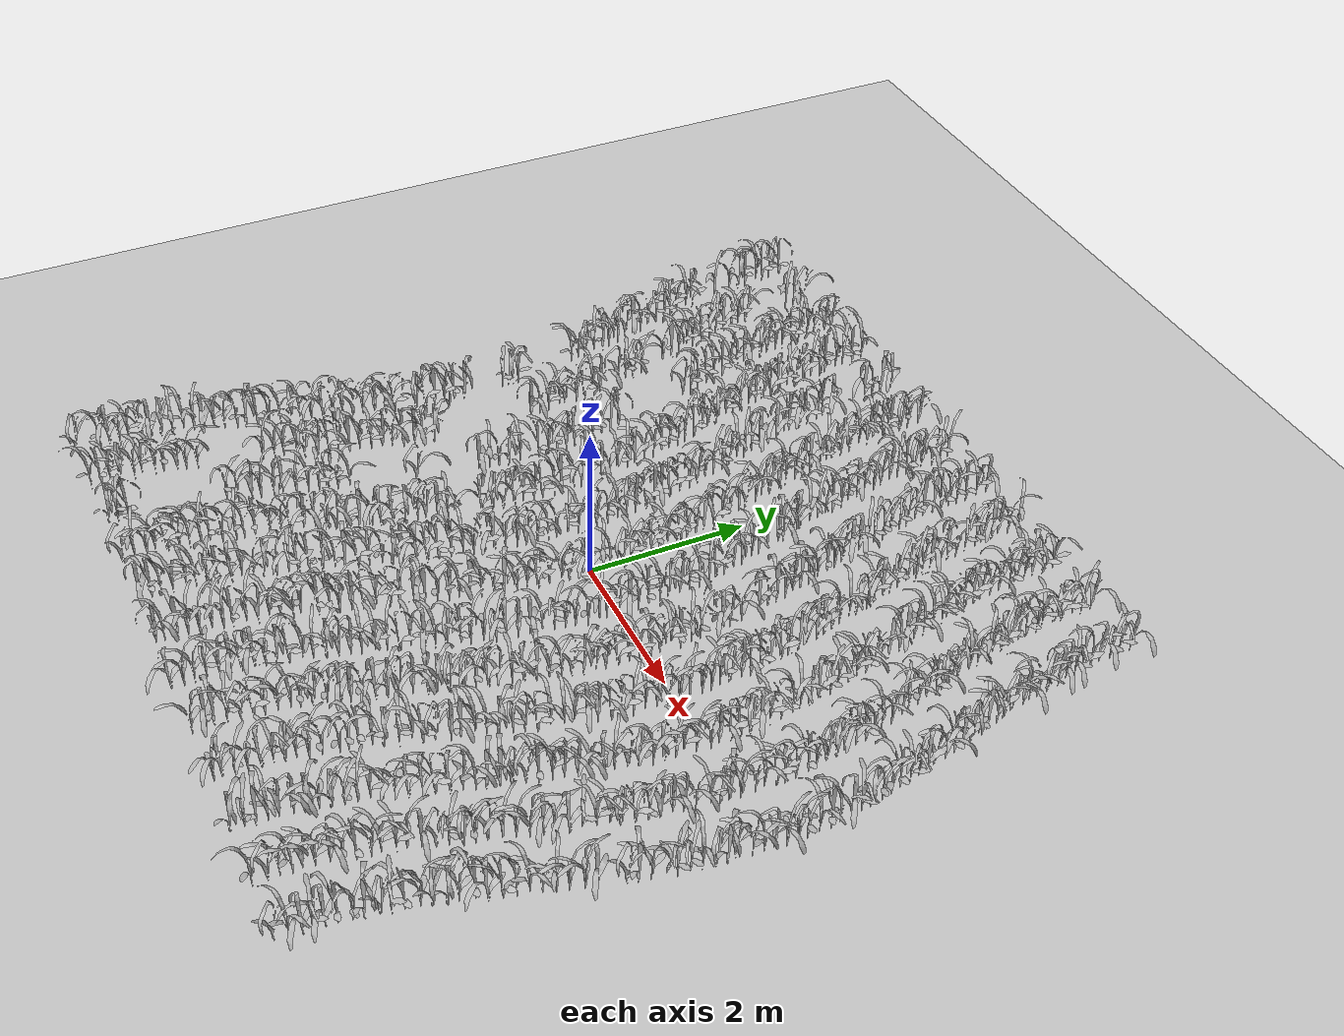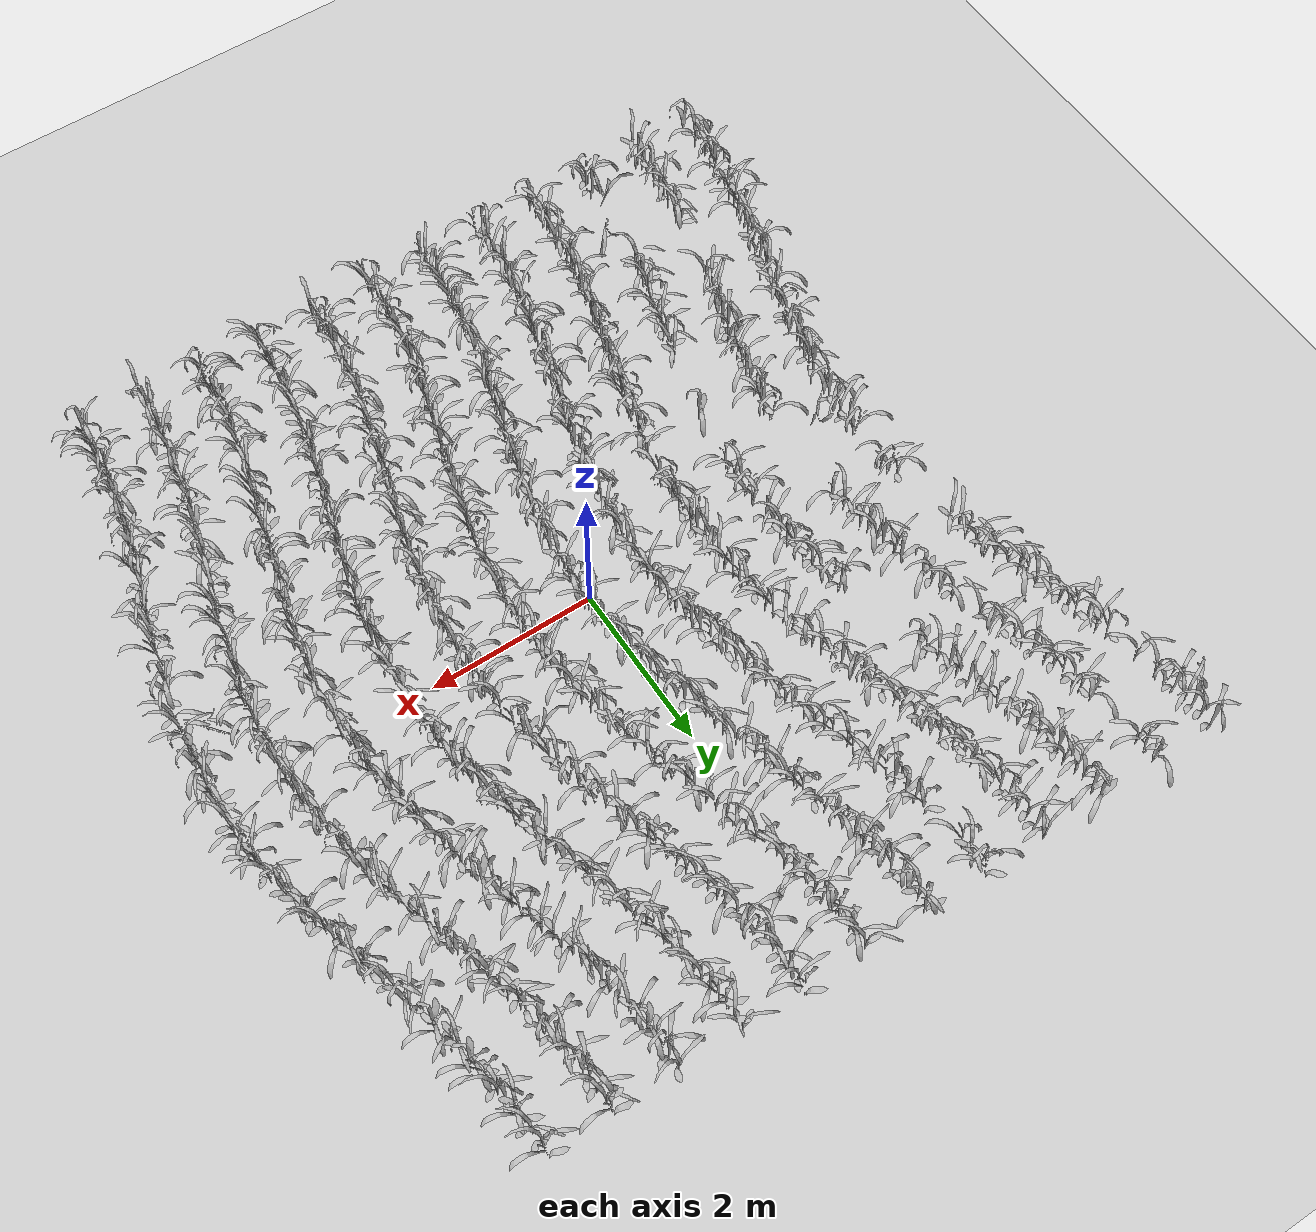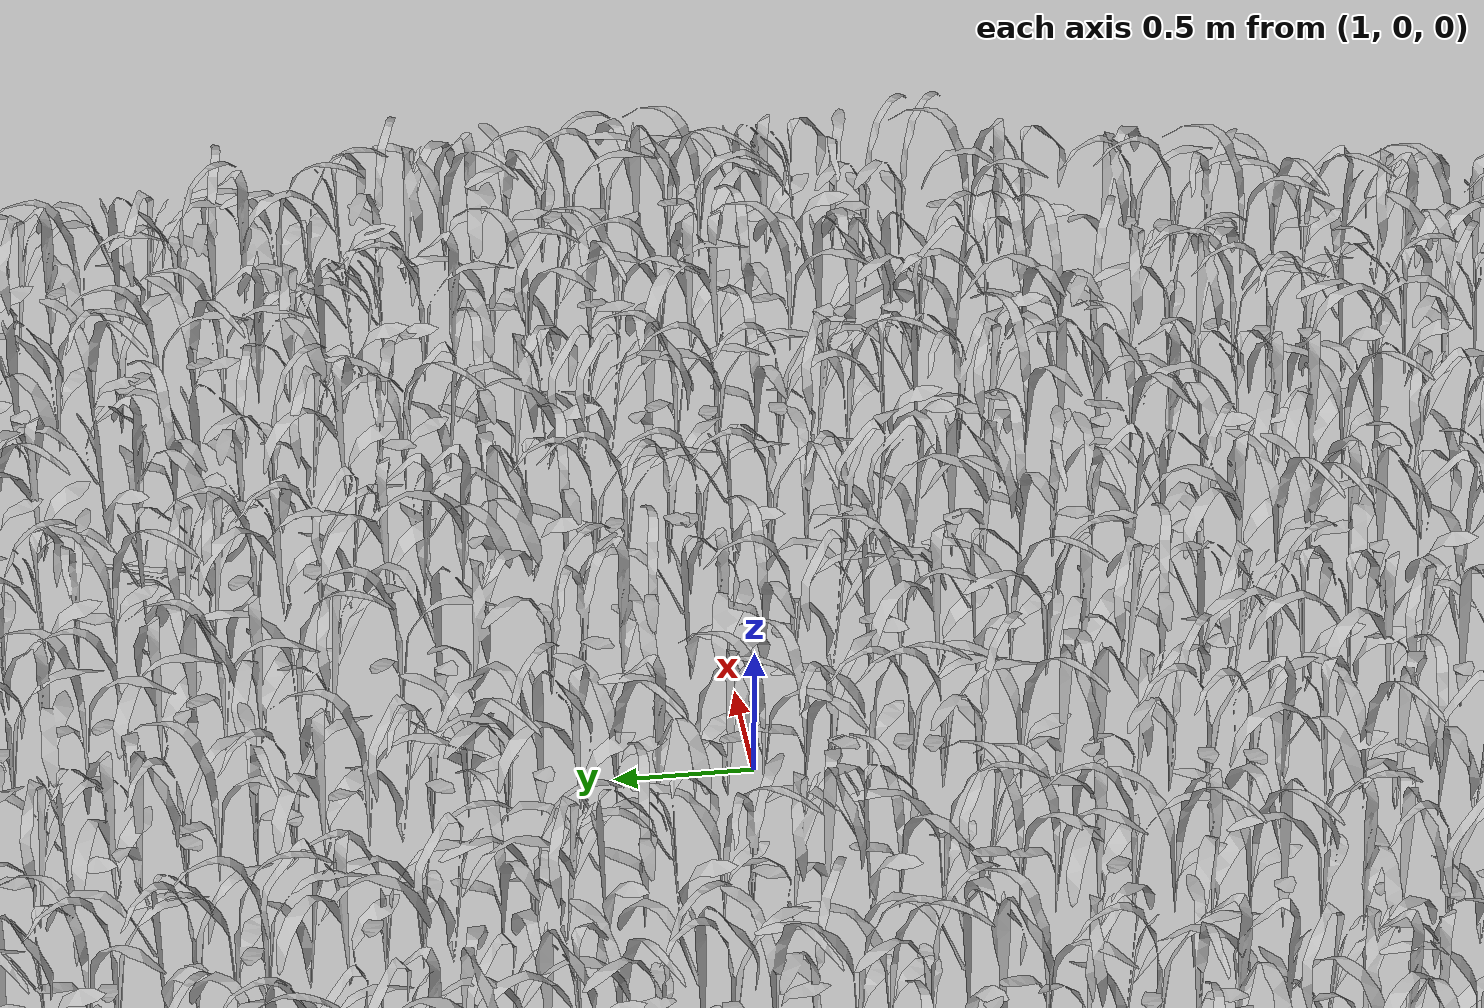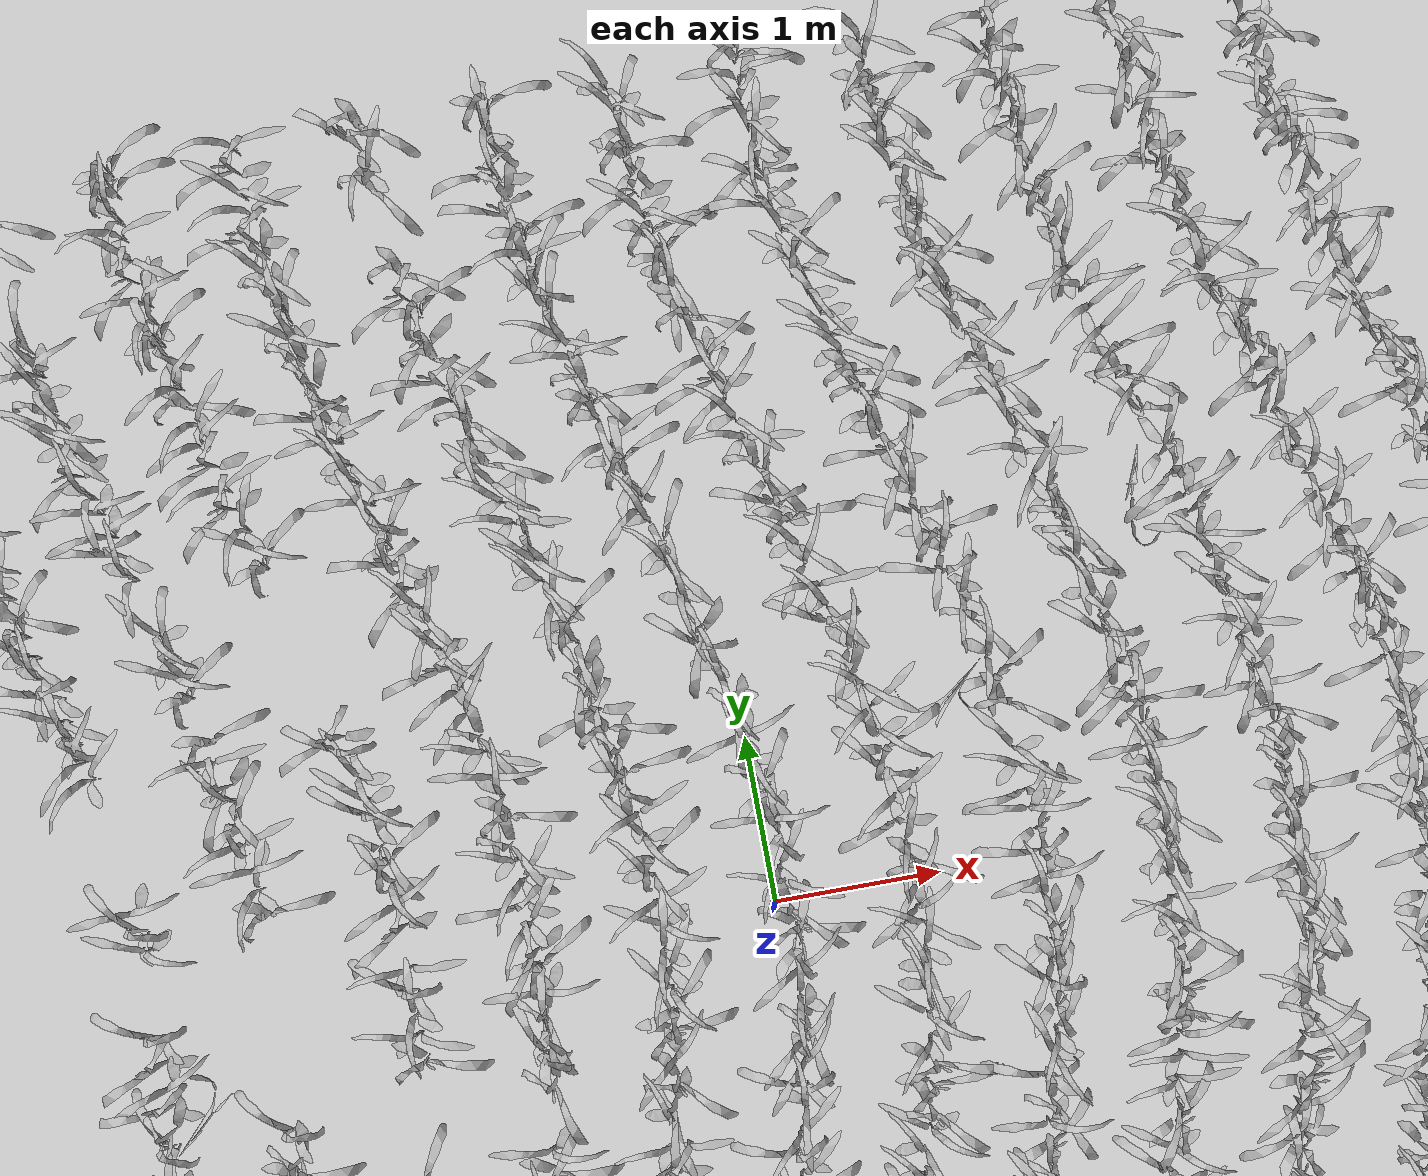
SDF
<sdf version="1.7">
 <world name="default">
  <light name="sun" type="directional">
   <pose>0 0 10 0 -0 0</pose>
   <diffuse>0.8 0.8 0.8 1</diffuse>
   <specular>0.2 0.2 0.2 1</specular>
   <attenuation>
    <range>1000</range>
    <constant>0.9</constant>
    <linear>0.01</linear>
    <quadratic>0.001</quadratic>
   </attenuation>
   <direction>-0.5 0.1 -0.9</direction>
   <spot><inner_angle>0</inner_angle><outer_angle>0</outer_angle><falloff>0</falloff></spot>
  </light>
  <gravity>0 0 -9.8</gravity>
  <magnetic_field>6e-06 2.3e-05 -4.2e-05</magnetic_field>
  <atmosphere type="adiabatic"/>
  <physics name="default_physics" default="0" type="ode">
   <max_step_size>0.005</max_step_size>
   <real_time_factor>1</real_time_factor>
   <real_time_update_rate>200</real_time_update_rate>
  </physics>
  <scene>
   <sky><clouds><speed>12</speed></clouds></sky>
   <ambient>0.4 0.4 0.4 1</ambient>
   <background>0.7 0.7 0.7 1</background>
   <grid>0</grid>
   <shadows>1</shadows>
  </scene>
  <audio><device>default</device></audio>
  <spherical_coordinates>
   <surface_model>EARTH_WGS84</surface_model>
   <latitude_deg>0</latitude_deg>
   <longitude_deg>0</longitude_deg>
   <elevation>0</elevation>
   <heading_deg>0</heading_deg>
  </spherical_coordinates>
  <model name="maize_01_0000">
   <pose>-4.60021 -4.94897 1e-06 3e-06 0.000156 2.6317</pose>
   <link name="maize_01_link">
    <inertial>
     <pose>0 0 0.01 0 -0 0</pose>
     <mass>0.3</mass>
     <inertia>
      <ixx>0.00334167</ixx>
      <ixy>0</ixy>
      <ixz>0</ixz>
      <iyy>0.00334167</iyy>
      <iyz>0</iyz>
      <izz>1.66667e-05</izz>
     </inertia>
     <pose>0 0 0.1 0 -0 0</pose>
    </inertial>
    <visual name="visual">
     <geometry>
      <mesh><uri>model://maize_01/meshes/maize_01.dae</uri><scale>0.683166 0.683166 0.683166</scale></mesh>
     </geometry>
    </visual>
   </link>
   <static>0</static>
  </model>
  <model name="maize_02_0001">
   <pose>-4.57675 -4.65483 -0 2.8e-05 5e-06 -2.64534</pose>
   <link name="maize_02_link">
    <inertial>
     <pose>0 0 0.01 0 -0 0</pose>
     <mass>0.3</mass>
     <inertia>
      <ixx>0.00334167</ixx>
      <ixy>0</ixy>
      <ixz>0</ixz>
      <iyy>0.00334167</iyy>
      <iyz>0</iyz>
      <izz>1.66667e-05</izz>
     </inertia>
     <pose>0 0 0.1 0 -0 0</pose>
    </inertial>
    <visual name="visual">
     <geometry>
      <mesh><uri>model://maize_02/meshes/maize_02.dae</uri><scale>0.683166 0.683166 0.683166</scale></mesh>
     </geometry>
    </visual>
   </link>
   <static>0</static>
  </model>
  <model name="maize_01_0002">
   <pose>-4.60094 -4.53894 -0 5e-06 2.8e-05 0.324141</pose>
   <link name="maize_01_link">
    <inertial>
     <pose>0 0 0.01 0 -0 0</pose>
     <mass>0.3</mass>
     <inertia>
      <ixx>0.00334167</ixx>
      <ixy>0</ixy>
      <ixz>0</ixz>
      <iyy>0.00334167</iyy>
      <iyz>0</iyz>
      <izz>1.66667e-05</izz>
     </inertia>
     <pose>0 0 0.1 0 -0 0</pose>
    </inertial>
    <visual name="visual">
     <geometry>
      <mesh><uri>model://maize_01/meshes/maize_01.dae</uri><scale>0.683166 0.683166 0.683166</scale></mesh>
     </geometry>
    </visual>
   </link>
   <static>0</static>
  </model>
  <model name="maize_02_0003">
   <pose>-4.56877 -4.41225 -0 -5e-06 -2.8e-05 0.481009</pose>
   <link name="maize_02_link">
    <inertial>
     <pose>0 0 0.01 0 -0 0</pose>
     <mass>0.3</mass>
     <inertia>
      <ixx>0.00334167</ixx>
      <ixy>0</ixy>
      <ixz>0</ixz>
      <iyy>0.00334167</iyy>
      <iyz>0</iyz>
      <izz>1.66667e-05</izz>
     </inertia>
     <pose>0 0 0.1 0 -0 0</pose>
    </inertial>
    <visual name="visual">
     <geometry>
      <mesh><uri>model://maize_02/meshes/maize_02.dae</uri><scale>0.683166 0.683166 0.683166</scale></mesh>
     </geometry>
    </visual>
   </link>
   <static>0</static>
  </model>
  <model name="maize_02_0004">
   <pose>-4.55891 -4.29432 1e-06 0.000156 3e-06 -0.575998</pose>
   <link name="maize_02_link">
    <inertial>
     <pose>0 0 0.01 0 -0 0</pose>
     <mass>0.3</mass>
     <inertia>
      <ixx>0.00334167</ixx>
      <ixy>0</ixy>
      <ixz>0</ixz>
      <iyy>0.00334167</iyy>
      <iyz>0</iyz>
      <izz>1.66667e-05</izz>
     </inertia>
     <pose>0 0 0.1 0 -0 0</pose>
    </inertial>
    <visual name="visual">
     <geometry>
      <mesh><uri>model://maize_02/meshes/maize_02.dae</uri><scale>0.683166 0.683166 0.683166</scale></mesh>
     </geometry>
    </visual>
   </link>
   <static>0</static>
  </model>
  <model name="maize_01_0005">
   <pose>-4.53132 -4.14815 -0 -5e-06 2.8e-05 -0.755377</pose>
   <link name="maize_01_link">
    <inertial>
     <pose>0 0 0.01 0 -0 0</pose>
     <mass>0.3</mass>
     <inertia>
      <ixx>0.00334167</ixx>
      <ixy>0</ixy>
      <ixz>0</ixz>
      <iyy>0.00334167</iyy>
      <iyz>0</iyz>
      <izz>1.66667e-05</izz>
     </inertia>
     <pose>0 0 0.1 0 -0 0</pose>
    </inertial>
    <visual name="visual">
     <geometry>
      <mesh><uri>model://maize_01/meshes/maize_01.dae</uri><scale>0.683166 0.683166 0.683166</scale></mesh>
     </geometry>
    </visual>
   </link>
   <static>0</static>
  </model>
  <model name="maize_01_0006">
   <pose>-4.49697 -4.03278 -0.000245 1.2e-05 -1.4e-05 0.581643</pose>
   <link name="maize_01_link">
    <inertial>
     <pose>0 0 0.01 0 -0 0</pose>
     <mass>0.3</mass>
     <inertia>
      <ixx>0.00334167</ixx>
      <ixy>0</ixy>
      <ixz>0</ixz>
      <iyy>0.00334167</iyy>
      <iyz>0</iyz>
      <izz>1.66667e-05</izz>
     </inertia>
     <pose>0 0 0.1 0 -0 0</pose>
    </inertial>
    <visual name="visual">
     <geometry>
      <mesh><uri>model://maize_01/meshes/maize_01.dae</uri><scale>0.683166 0.683166 0.683166</scale></mesh>
     </geometry>
    </visual>
   </link>
   <static>0</static>
  </model>
  <model name="maize_01_0007">
   <pose>-4.50994 -3.88738 -0 5e-06 2.8e-05 3.00576</pose>
   <link name="maize_01_link">
    <inertial>
     <pose>0 0 0.01 0 -0 0</pose>
     <mass>0.3</mass>
     <inertia>
      <ixx>0.00334167</ixx>
      <ixy>0</ixy>
      <ixz>0</ixz>
      <iyy>0.00334167</iyy>
      <iyz>0</iyz>
      <izz>1.66667e-05</izz>
     </inertia>
     <pose>0 0 0.1 0 -0 0</pose>
    </inertial>
    <visual name="visual">
     <geometry>
      <mesh><uri>model://maize_01/meshes/maize_01.dae</uri><scale>0.683166 0.683166 0.683166</scale></mesh>
     </geometry>
    </visual>
   </link>
   <static>0</static>
  </model>
  <model name="maize_02_0008">
   <pose>-4.47133 -3.76023 -0.000245 1.2e-05 -1.4e-05 2.06232</pose>
   <link name="maize_02_link">
    <inertial>
     <pose>0 0 0.01 0 -0 0</pose>
     <mass>0.3</mass>
     <inertia>
      <ixx>0.00334167</ixx>
      <ixy>0</ixy>
      <ixz>0</ixz>
      <iyy>0.00334167</iyy>
      <iyz>0</iyz>
      <izz>1.66667e-05</izz>
     </inertia>
     <pose>0 0 0.1 0 -0 0</pose>
    </inertial>
    <visual name="visual">
     <geometry>
      <mesh><uri>model://maize_02/meshes/maize_02.dae</uri><scale>0.683166 0.683166 0.683166</scale></mesh>
     </geometry>
    </visual>
   </link>
   <static>0</static>
  </model>
  <model name="maize_02_0009">
   <pose>-4.44709 -3.6212 -1e-06 -6e-06 8.6e-05 2.49509</pose>
   <link name="maize_02_link">
    <inertial>
     <pose>0 0 0.01 0 -0 0</pose>
     <mass>0.3</mass>
     <inertia>
      <ixx>0.00334167</ixx>
      <ixy>0</ixy>
      <ixz>0</ixz>
      <iyy>0.00334167</iyy>
      <iyz>0</iyz>
      <izz>1.66667e-05</izz>
     </inertia>
     <pose>0 0 0.1 0 -0 0</pose>
    </inertial>
    <visual name="visual">
     <geometry>
      <mesh><uri>model://maize_02/meshes/maize_02.dae</uri><scale>0.683166 0.683166 0.683166</scale></mesh>
     </geometry>
    </visual>
   </link>
   <static>0</static>
  </model>
  <model name="maize_02_0010">
   <pose>-4.40786 -3.49529 -1e-06 6e-06 -8.9e-05 1.60225</pose>
   <link name="maize_02_link">
    <inertial>
     <pose>0 0 0.01 0 -0 0</pose>
     <mass>0.3</mass>
     <inertia>
      <ixx>0.00334167</ixx>
      <ixy>0</ixy>
      <ixz>0</ixz>
      <iyy>0.00334167</iyy>
      <iyz>0</iyz>
      <izz>1.66667e-05</izz>
     </inertia>
     <pose>0 0 0.1 0 -0 0</pose>
    </inertial>
    <visual name="visual">
     <geometry>
      <mesh><uri>model://maize_02/meshes/maize_02.dae</uri><scale>0.683166 0.683166 0.683166</scale></mesh>
     </geometry>
    </visual>
   </link>
   <static>0</static>
  </model>
  <model name="maize_01_0011">
   <pose>-4.36571 -3.38741 -0 -5e-06 -2.8e-05 0.583081</pose>
   <link name="maize_01_link">
    <inertial>
     <pose>0 0 0.01 0 -0 0</pose>
     <mass>0.3</mass>
     <inertia>
      <ixx>0.00334167</ixx>
      <ixy>0</ixy>
      <ixz>0</ixz>
      <iyy>0.00334167</iyy>
      <iyz>0</iyz>
      <izz>1.66667e-05</izz>
     </inertia>
     <pose>0 0 0.1 0 -0 0</pose>
    </inertial>
    <visual name="visual">
     <geometry>
      <mesh><uri>model://maize_01/meshes/maize_01.dae</uri><scale>0.683166 0.683166 0.683166</scale></mesh>
     </geometry>
    </visual>
   </link>
   <static>0</static>
  </model>
  <model name="maize_02_0012">
   <pose>-4.34671 -3.25216 -1e-06 -6e-06 7.9e-05 -0.329562</pose>
   <link name="maize_02_link">
    <inertial>
     <pose>0 0 0.01 0 -0 0</pose>
     <mass>0.3</mass>
     <inertia>
      <ixx>0.00334167</ixx>
      <ixy>0</ixy>
      <ixz>0</ixz>
      <iyy>0.00334167</iyy>
      <iyz>0</iyz>
      <izz>1.66667e-05</izz>
     </inertia>
     <pose>0 0 0.1 0 -0 0</pose>
    </inertial>
    <visual name="visual">
     <geometry>
      <mesh><uri>model://maize_02/meshes/maize_02.dae</uri><scale>0.683166 0.683166 0.683166</scale></mesh>
     </geometry>
    </visual>
   </link>
   <static>0</static>
  </model>
  <model name="maize_02_0013">
   <pose>-4.31019 -3.12789 -0.000245 1.2e-05 1.4e-05 0.347552</pose>
   <link name="maize_02_link">
    <inertial>
     <pose>0 0 0.01 0 -0 0</pose>
     <mass>0.3</mass>
     <inertia>
      <ixx>0.00334167</ixx>
      <ixy>0</ixy>
      <ixz>0</ixz>
      <iyy>0.00334167</iyy>
      <iyz>0</iyz>
      <izz>1.66667e-05</izz>
     </inertia>
     <pose>0 0 0.1 0 -0 0</pose>
    </inertial>
    <visual name="visual">
     <geometry>
      <mesh><uri>model://maize_02/meshes/maize_02.dae</uri><scale>0.683166 0.683166 0.683166</scale></mesh>
     </geometry>
    </visual>
   </link>
   <static>0</static>
  </model>
  <model name="maize_02_0014">
   <pose>-4.26656 -2.97332 -0 -5e-06 -2.8e-05 -2.56514</pose>
   <link name="maize_02_link">
    <inertial>
     <pose>0 0 0.01 0 -0 0</pose>
     <mass>0.3</mass>
     <inertia>
      <ixx>0.00334167</ixx>
      <ixy>0</ixy>
      <ixz>0</ixz>
      <iyy>0.00334167</iyy>
      <iyz>0</iyz>
      <izz>1.66667e-05</izz>
     </inertia>
     <pose>0 0 0.1 0 -0 0</pose>
    </inertial>
    <visual name="visual">
     <geometry>
      <mesh><uri>model://maize_02/meshes/maize_02.dae</uri><scale>0.683166 0.683166 0.683166</scale></mesh>
     </geometry>
    </visual>
   </link>
   <static>0</static>
  </model>
  <model name="maize_01_0015">
   <pose>-4.24242 -2.86003 -0.000245 -1.4e-05 -1.2e-05 -2.74685</pose>
   <link name="maize_01_link">
    <inertial>
     <pose>0 0 0.01 0 -0 0</pose>
     <mass>0.3</mass>
     <inertia>
      <ixx>0.00334167</ixx>
      <ixy>0</ixy>
      <ixz>0</ixz>
      <iyy>0.00334167</iyy>
      <iyz>0</iyz>
      <izz>1.66667e-05</izz>
     </inertia>
     <pose>0 0 0.1 0 -0 0</pose>
    </inertial>
    <visual name="visual">
     <geometry>
      <mesh><uri>model://maize_01/meshes/maize_01.dae</uri><scale>0.683166 0.683166 0.683166</scale></mesh>
     </geometry>
    </visual>
   </link>
   <static>0</static>
  </model>
  <model name="maize_01_0016">
   <pose>-4.19923 -2.72609 -0 -4.8e-05 -6e-06 -1.69412</pose>
   <link name="maize_01_link">
    <inertial>
     <pose>0 0 0.01 0 -0 0</pose>
     <mass>0.3</mass>
     <inertia>
      <ixx>0.00334167</ixx>
      <ixy>0</ixy>
      <ixz>0</ixz>
      <iyy>0.00334167</iyy>
      <iyz>0</iyz>
      <izz>1.66667e-05</izz>
     </inertia>
     <pose>0 0 0.1 0 -0 0</pose>
    </inertial>
    <visual name="visual">
     <geometry>
      <mesh><uri>model://maize_01/meshes/maize_01.dae</uri><scale>0.683166 0.683166 0.683166</scale></mesh>
     </geometry>
    </visual>
   </link>
   <static>0</static>
  </model>
  <model name="maize_02_0017">
   <pose>-4.17695 -2.58355 -1e-06 -8.3e-05 -6e-06 -2.62048</pose>
   <link name="maize_02_link">
    <inertial>
     <pose>0 0 0.01 0 -0 0</pose>
     <mass>0.3</mass>
     <inertia>
      <ixx>0.00334167</ixx>
      <ixy>0</ixy>
      <ixz>0</ixz>
      <iyy>0.00334167</iyy>
      <iyz>0</iyz>
      <izz>1.66667e-05</izz>
     </inertia>
     <pose>0 0 0.1 0 -0 0</pose>
    </inertial>
    <visual name="visual">
     <geometry>
      <mesh><uri>model://maize_02/meshes/maize_02.dae</uri><scale>0.683166 0.683166 0.683166</scale></mesh>
     </geometry>
    </visual>
   </link>
   <static>0</static>
  </model>
  <model name="maize_02_0018">
   <pose>-4.12042 -2.44918 1e-06 2e-06 0.000116 -3.07479</pose>
   <link name="maize_02_link">
    <inertial>
     <pose>0 0 0.01 0 -0 0</pose>
     <mass>0.3</mass>
     <inertia>
      <ixx>0.00334167</ixx>
      <ixy>0</ixy>
      <ixz>0</ixz>
      <iyy>0.00334167</iyy>
      <iyz>0</iyz>
      <izz>1.66667e-05</izz>
     </inertia>
     <pose>0 0 0.1 0 -0 0</pose>
    </inertial>
    <visual name="visual">
     <geometry>
      <mesh><uri>model://maize_02/meshes/maize_02.dae</uri><scale>0.683166 0.683166 0.683166</scale></mesh>
     </geometry>
    </visual>
   </link>
   <static>0</static>
  </model>
  <model name="maize_01_0019">
   <pose>-4.09401 -2.31646 -0 -2.8e-05 5e-06 2.97261</pose>
   <link name="maize_01_link">
    <inertial>
     <pose>0 0 0.01 0 -0 0</pose>
     <mass>0.3</mass>
     <inertia>
      <ixx>0.00334167</ixx>
      <ixy>0</ixy>
      <ixz>0</ixz>
      <iyy>0.00334167</iyy>
      <iyz>0</iyz>
      <izz>1.66667e-05</izz>
     </inertia>
     <pose>0 0 0.1 0 -0 0</pose>
    </inertial>
    <visual name="visual">
     <geometry>
      <mesh><uri>model://maize_01/meshes/maize_01.dae</uri><scale>0.683166 0.683166 0.683166</scale></mesh>
     </geometry>
    </visual>
   </link>
   <static>0</static>
  </model>
  <model name="maize_02_0020">
   <pose>-4.06344 -2.20729 -1e-06 -8.9e-05 -6e-06 2.96076</pose>
   <link name="maize_02_link">
    <inertial>
     <pose>0 0 0.01 0 -0 0</pose>
     <mass>0.3</mass>
     <inertia>
      <ixx>0.00334167</ixx>
      <ixy>0</ixy>
      <ixz>0</ixz>
      <iyy>0.00334167</iyy>
      <iyz>0</iyz>
      <izz>1.66667e-05</izz>
     </inertia>
     <pose>0 0 0.1 0 -0 0</pose>
    </inertial>
    <visual name="visual">
     <geometry>
      <mesh><uri>model://maize_02/meshes/maize_02.dae</uri><scale>0.683166 0.683166 0.683166</scale></mesh>
     </geometry>
    </visual>
   </link>
   <static>0</static>
  </model>
  <model name="maize_02_0021">
   <pose>-4.01691 -2.0727 -1e-06 -6e-06 8.6e-05 0.953992</pose>
   <link name="maize_02_link">
    <inertial>
     <pose>0 0 0.01 0 -0 0</pose>
     <mass>0.3</mass>
     <inertia>
      <ixx>0.00334167</ixx>
      <ixy>0</ixy>
      <ixz>0</ixz>
      <iyy>0.00334167</iyy>
      <iyz>0</iyz>
      <izz>1.66667e-05</izz>
     </inertia>
     <pose>0 0 0.1 0 -0 0</pose>
    </inertial>
    <visual name="visual">
     <geometry>
      <mesh><uri>model://maize_02/meshes/maize_02.dae</uri><scale>0.683166 0.683166 0.683166</scale></mesh>
     </geometry>
    </visual>
   </link>
   <static>0</static>
  </model>
  <model name="maize_01_0022">
   <pose>-3.97051 -1.92991 -0.000245 -1.2e-05 1.4e-05 -0.147421</pose>
   <link name="maize_01_link">
    <inertial>
     <pose>0 0 0.01 0 -0 0</pose>
     <mass>0.3</mass>
     <inertia>
      <ixx>0.00334167</ixx>
      <ixy>0</ixy>
      <ixz>0</ixz>
      <iyy>0.00334167</iyy>
      <iyz>0</iyz>
      <izz>1.66667e-05</izz>
     </inertia>
     <pose>0 0 0.1 0 -0 0</pose>
    </inertial>
    <visual name="visual">
     <geometry>
      <mesh><uri>model://maize_01/meshes/maize_01.dae</uri><scale>0.683166 0.683166 0.683166</scale></mesh>
     </geometry>
    </visual>
   </link>
   <static>0</static>
  </model>
  <model name="maize_02_0023">
   <pose>-3.93771 -1.81544 1e-06 -3e-06 0.000156 -2.11151</pose>
   <link name="maize_02_link">
    <inertial>
     <pose>0 0 0.01 0 -0 0</pose>
     <mass>0.3</mass>
     <inertia>
      <ixx>0.00334167</ixx>
      <ixy>0</ixy>
      <ixz>0</ixz>
      <iyy>0.00334167</iyy>
      <iyz>0</iyz>
      <izz>1.66667e-05</izz>
     </inertia>
     <pose>0 0 0.1 0 -0 0</pose>
    </inertial>
    <visual name="visual">
     <geometry>
      <mesh><uri>model://maize_02/meshes/maize_02.dae</uri><scale>0.683166 0.683166 0.683166</scale></mesh>
     </geometry>
    </visual>
   </link>
   <static>0</static>
  </model>
  <model name="maize_01_0024">
   <pose>-3.90844 -1.69421 -1e-06 -8.6e-05 6e-06 -2.31971</pose>
   <link name="maize_01_link">
    <inertial>
     <pose>0 0 0.01 0 -0 0</pose>
     <mass>0.3</mass>
     <inertia>
      <ixx>0.00334167</ixx>
      <ixy>0</ixy>
      <ixz>0</ixz>
      <iyy>0.00334167</iyy>
      <iyz>0</iyz>
      <izz>1.66667e-05</izz>
     </inertia>
     <pose>0 0 0.1 0 -0 0</pose>
    </inertial>
    <visual name="visual">
     <geometry>
      <mesh><uri>model://maize_01/meshes/maize_01.dae</uri><scale>0.683166 0.683166 0.683166</scale></mesh>
     </geometry>
    </visual>
   </link>
   <static>0</static>
  </model>
  <model name="maize_01_0025">
   <pose>-3.89953 -1.5496 1e-06 -3e-06 -0.000156 2.05247</pose>
   <link name="maize_01_link">
    <inertial>
     <pose>0 0 0.01 0 -0 0</pose>
     <mass>0.3</mass>
     <inertia>
      <ixx>0.00334167</ixx>
      <ixy>0</ixy>
      <ixz>0</ixz>
      <iyy>0.00334167</iyy>
      <iyz>0</iyz>
      <izz>1.66667e-05</izz>
     </inertia>
     <pose>0 0 0.1 0 -0 0</pose>
    </inertial>
    <visual name="visual">
     <geometry>
      <mesh><uri>model://maize_01/meshes/maize_01.dae</uri><scale>0.683166 0.683166 0.683166</scale></mesh>
     </geometry>
    </visual>
   </link>
   <static>0</static>
  </model>
  <model name="maize_02_0026">
   <pose>-3.86631 -1.43265 -1e-06 6e-06 8.9e-05 0.61974</pose>
   <link name="maize_02_link">
    <inertial>
     <pose>0 0 0.01 0 -0 0</pose>
     <mass>0.3</mass>
     <inertia>
      <ixx>0.00334167</ixx>
      <ixy>0</ixy>
      <ixz>0</ixz>
      <iyy>0.00334167</iyy>
      <iyz>0</iyz>
      <izz>1.66667e-05</izz>
     </inertia>
     <pose>0 0 0.1 0 -0 0</pose>
    </inertial>
    <visual name="visual">
     <geometry>
      <mesh><uri>model://maize_02/meshes/maize_02.dae</uri><scale>0.683166 0.683166 0.683166</scale></mesh>
     </geometry>
    </visual>
   </link>
   <static>0</static>
  </model>
  <model name="maize_01_0027">
   <pose>-3.82293 -1.29197 1e-06 -0.000156 -3e-06 1.10234</pose>
   <link name="maize_01_link">
    <inertial>
     <pose>0 0 0.01 0 -0 0</pose>
     <mass>0.3</mass>
     <inertia>
      <ixx>0.00334167</ixx>
      <ixy>0</ixy>
      <ixz>0</ixz>
      <iyy>0.00334167</iyy>
      <iyz>0</iyz>
      <izz>1.66667e-05</izz>
     </inertia>
     <pose>0 0 0.1 0 -0 0</pose>
    </inertial>
    <visual name="visual">
     <geometry>
      <mesh><uri>model://maize_01/meshes/maize_01.dae</uri><scale>0.683166 0.683166 0.683166</scale></mesh>
     </geometry>
    </visual>
   </link>
   <static>0</static>
  </model>
  <model name="maize_02_0028">
   <pose>-3.7826 -1.15412 -0 2.8e-05 5e-06 -1.97203</pose>
   <link name="maize_02_link">
    <inertial>
     <pose>0 0 0.01 0 -0 0</pose>
     <mass>0.3</mass>
     <inertia>
      <ixx>0.00334167</ixx>
      <ixy>0</ixy>
      <ixz>0</ixz>
      <iyy>0.00334167</iyy>
      <iyz>0</iyz>
      <izz>1.66667e-05</izz>
     </inertia>
     <pose>0 0 0.1 0 -0 0</pose>
    </inertial>
    <visual name="visual">
     <geometry>
      <mesh><uri>model://maize_02/meshes/maize_02.dae</uri><scale>0.683166 0.683166 0.683166</scale></mesh>
     </geometry>
    </visual>
   </link>
   <static>0</static>
  </model>
  <model name="maize_01_0029">
   <pose>-3.77198 -1.04541 -0 2.8e-05 -5e-06 -1.11484</pose>
   <link name="maize_01_link">
    <inertial>
     <pose>0 0 0.01 0 -0 0</pose>
     <mass>0.3</mass>
     <inertia>
      <ixx>0.00334167</ixx>
      <ixy>0</ixy>
      <ixz>0</ixz>
      <iyy>0.00334167</iyy>
      <iyz>0</iyz>
      <izz>1.66667e-05</izz>
     </inertia>
     <pose>0 0 0.1 0 -0 0</pose>
    </inertial>
    <visual name="visual">
     <geometry>
      <mesh><uri>model://maize_01/meshes/maize_01.dae</uri><scale>0.683166 0.683166 0.683166</scale></mesh>
     </geometry>
    </visual>
   </link>
   <static>0</static>
  </model>
  <model name="maize_02_0030">
   <pose>-3.7565 -0.837103 0.009953 -1.5708 -0.00477 -0.829308</pose>
   <link name="maize_02_link">
    <inertial>
     <pose>0 0 0.01 0 -0 0</pose>
     <mass>0.3</mass>
     <inertia>
      <ixx>0.00334167</ixx>
      <ixy>0</ixy>
      <ixz>0</ixz>
      <iyy>0.00334167</iyy>
      <iyz>0</iyz>
      <izz>1.66667e-05</izz>
     </inertia>
     <pose>0 0 0.1 0 -0 0</pose>
    </inertial>
    <visual name="visual">
     <geometry>
      <mesh><uri>model://maize_02/meshes/maize_02.dae</uri><scale>0.683166 0.683166 0.683166</scale></mesh>
     </geometry>
    </visual>
   </link>
   <static>0</static>
  </model>
  <model name="maize_01_0031">
   <pose>-3.72155 -0.761612 -0 5e-06 -2.8e-05 2.68565</pose>
   <link name="maize_01_link">
    <inertial>
     <pose>0 0 0.01 0 -0 0</pose>
     <mass>0.3</mass>
     <inertia>
      <ixx>0.00334167</ixx>
      <ixy>0</ixy>
      <ixz>0</ixz>
      <iyy>0.00334167</iyy>
      <iyz>0</iyz>
      <izz>1.66667e-05</izz>
     </inertia>
     <pose>0 0 0.1 0 -0 0</pose>
    </inertial>
    <visual name="visual">
     <geometry>
      <mesh><uri>model://maize_01/meshes/maize_01.dae</uri><scale>0.683166 0.683166 0.683166</scale></mesh>
     </geometry>
    </visual>
   </link>
   <static>0</static>
  </model>
  <model name="maize_01_0032">
   <pose>-3.70659 -0.645785 -0 5e-06 -2.8e-05 -0.829071</pose>
   <link name="maize_01_link">
    <inertial>
     <pose>0 0 0.01 0 -0 0</pose>
     <mass>0.3</mass>
     <inertia>
      <ixx>0.00334167</ixx>
      <ixy>0</ixy>
      <ixz>0</ixz>
      <iyy>0.00334167</iyy>
      <iyz>0</iyz>
      <izz>1.66667e-05</izz>
     </inertia>
     <pose>0 0 0.1 0 -0 0</pose>
    </inertial>
    <visual name="visual">
     <geometry>
      <mesh><uri>model://maize_01/meshes/maize_01.dae</uri><scale>0.683166 0.683166 0.683166</scale></mesh>
     </geometry>
    </visual>
   </link>
   <static>0</static>
  </model>
  <model name="maize_01_0033">
   <pose>-3.68856 -0.516251 -0 -2.8e-05 -5e-06 -2.32412</pose>
   <link name="maize_01_link">
    <inertial>
     <pose>0 0 0.01 0 -0 0</pose>
     <mass>0.3</mass>
     <inertia>
      <ixx>0.00334167</ixx>
      <ixy>0</ixy>
      <ixz>0</ixz>
      <iyy>0.00334167</iyy>
      <iyz>0</iyz>
      <izz>1.66667e-05</izz>
     </inertia>
     <pose>0 0 0.1 0 -0 0</pose>
    </inertial>
    <visual name="visual">
     <geometry>
      <mesh><uri>model://maize_01/meshes/maize_01.dae</uri><scale>0.683166 0.683166 0.683166</scale></mesh>
     </geometry>
    </visual>
   </link>
   <static>0</static>
  </model>
  <model name="maize_02_0034">
   <pose>-3.66675 -0.396472 -0 4.8e-05 6e-06 -0.572521</pose>
   <link name="maize_02_link">
    <inertial>
     <pose>0 0 0.01 0 -0 0</pose>
     <mass>0.3</mass>
     <inertia>
      <ixx>0.00334167</ixx>
      <ixy>0</ixy>
      <ixz>0</ixz>
      <iyy>0.00334167</iyy>
      <iyz>0</iyz>
      <izz>1.66667e-05</izz>
     </inertia>
     <pose>0 0 0.1 0 -0 0</pose>
    </inertial>
    <visual name="visual">
     <geometry>
      <mesh><uri>model://maize_02/meshes/maize_02.dae</uri><scale>0.683166 0.683166 0.683166</scale></mesh>
     </geometry>
    </visual>
   </link>
   <static>0</static>
  </model>
  <model name="maize_01_0035">
   <pose>-3.68278 -0.252334 -0 -2.8e-05 -5e-06 -1.92935</pose>
   <link name="maize_01_link">
    <inertial>
     <pose>0 0 0.01 0 -0 0</pose>
     <mass>0.3</mass>
     <inertia>
      <ixx>0.00334167</ixx>
      <ixy>0</ixy>
      <ixz>0</ixz>
      <iyy>0.00334167</iyy>
      <iyz>0</iyz>
      <izz>1.66667e-05</izz>
     </inertia>
     <pose>0 0 0.1 0 -0 0</pose>
    </inertial>
    <visual name="visual">
     <geometry>
      <mesh><uri>model://maize_01/meshes/maize_01.dae</uri><scale>0.683166 0.683166 0.683166</scale></mesh>
     </geometry>
    </visual>
   </link>
   <static>0</static>
  </model>
  <model name="maize_01_0036">
   <pose>-3.67981 -0.112768 -1e-06 -8.9e-05 -6e-06 -2.89943</pose>
   <link name="maize_01_link">
    <inertial>
     <pose>0 0 0.01 0 -0 0</pose>
     <mass>0.3</mass>
     <inertia>
      <ixx>0.00334167</ixx>
      <ixy>0</ixy>
      <ixz>0</ixz>
      <iyy>0.00334167</iyy>
      <iyz>0</iyz>
      <izz>1.66667e-05</izz>
     </inertia>
     <pose>0 0 0.1 0 -0 0</pose>
    </inertial>
    <visual name="visual">
     <geometry>
      <mesh><uri>model://maize_01/meshes/maize_01.dae</uri><scale>0.683166 0.683166 0.683166</scale></mesh>
     </geometry>
    </visual>
   </link>
   <static>0</static>
  </model>
  <model name="maize_02_0037">
   <pose>-3.66027 0.410487 -0.000245 1.4e-05 -1.2e-05 -1.38058</pose>
   <link name="maize_02_link">
    <inertial>
     <pose>0 0 0.01 0 -0 0</pose>
     <mass>0.3</mass>
     <inertia>
      <ixx>0.00334167</ixx>
      <ixy>0</ixy>
      <ixz>0</ixz>
      <iyy>0.00334167</iyy>
      <iyz>0</iyz>
      <izz>1.66667e-05</izz>
     </inertia>
     <pose>0 0 0.1 0 -0 0</pose>
    </inertial>
    <visual name="visual">
     <geometry>
      <mesh><uri>model://maize_02/meshes/maize_02.dae</uri><scale>0.683166 0.683166 0.683166</scale></mesh>
     </geometry>
    </visual>
   </link>
   <static>0</static>
  </model>
  <model name="maize_01_0038">
   <pose>-3.68555 0.516604 -0 -5e-06 -2.8e-05 2.98925</pose>
   <link name="maize_01_link">
    <inertial>
     <pose>0 0 0.01 0 -0 0</pose>
     <mass>0.3</mass>
     <inertia>
      <ixx>0.00334167</ixx>
      <ixy>0</ixy>
      <ixz>0</ixz>
      <iyy>0.00334167</iyy>
      <iyz>0</iyz>
      <izz>1.66667e-05</izz>
     </inertia>
     <pose>0 0 0.1 0 -0 0</pose>
    </inertial>
    <visual name="visual">
     <geometry>
      <mesh><uri>model://maize_01/meshes/maize_01.dae</uri><scale>0.683166 0.683166 0.683166</scale></mesh>
     </geometry>
    </visual>
   </link>
   <static>0</static>
  </model>
  <model name="maize_02_0039">
   <pose>-3.70169 0.643585 -0 -5e-06 -2.8e-05 -0.865449</pose>
   <link name="maize_02_link">
    <inertial>
     <pose>0 0 0.01 0 -0 0</pose>
     <mass>0.3</mass>
     <inertia>
      <ixx>0.00334167</ixx>
      <ixy>0</ixy>
      <ixz>0</ixz>
      <iyy>0.00334167</iyy>
      <iyz>0</iyz>
      <izz>1.66667e-05</izz>
     </inertia>
     <pose>0 0 0.1 0 -0 0</pose>
    </inertial>
    <visual name="visual">
     <geometry>
      <mesh><uri>model://maize_02/meshes/maize_02.dae</uri><scale>0.683166 0.683166 0.683166</scale></mesh>
     </geometry>
    </visual>
   </link>
   <static>0</static>
  </model>
  <model name="maize_02_0040">
   <pose>-3.81636 1.45517 -1e-06 6e-06 -8.3e-05 2.98124</pose>
   <link name="maize_02_link">
    <inertial>
     <pose>0 0 0.01 0 -0 0</pose>
     <mass>0.3</mass>
     <inertia>
      <ixx>0.00334167</ixx>
      <ixy>0</ixy>
      <ixz>0</ixz>
      <iyy>0.00334167</iyy>
      <iyz>0</iyz>
      <izz>1.66667e-05</izz>
     </inertia>
     <pose>0 0 0.1 0 -0 0</pose>
    </inertial>
    <visual name="visual">
     <geometry>
      <mesh><uri>model://maize_02/meshes/maize_02.dae</uri><scale>0.683166 0.683166 0.683166</scale></mesh>
     </geometry>
    </visual>
   </link>
   <static>0</static>
  </model>
  <model name="maize_02_0041">
   <pose>-3.86791 1.56843 -0 -5e-06 -2.8e-05 -0.060182</pose>
   <link name="maize_02_link">
    <inertial>
     <pose>0 0 0.01 0 -0 0</pose>
     <mass>0.3</mass>
     <inertia>
      <ixx>0.00334167</ixx>
      <ixy>0</ixy>
      <ixz>0</ixz>
      <iyy>0.00334167</iyy>
      <iyz>0</iyz>
      <izz>1.66667e-05</izz>
     </inertia>
     <pose>0 0 0.1 0 -0 0</pose>
    </inertial>
    <visual name="visual">
     <geometry>
      <mesh><uri>model://maize_02/meshes/maize_02.dae</uri><scale>0.683166 0.683166 0.683166</scale></mesh>
     </geometry>
    </visual>
   </link>
   <static>0</static>
  </model>
  <model name="maize_01_0042">
   <pose>-3.88179 1.68025 -0 5e-06 2.8e-05 2.52057</pose>
   <link name="maize_01_link">
    <inertial>
     <pose>0 0 0.01 0 -0 0</pose>
     <mass>0.3</mass>
     <inertia>
      <ixx>0.00334167</ixx>
      <ixy>0</ixy>
      <ixz>0</ixz>
      <iyy>0.00334167</iyy>
      <iyz>0</iyz>
      <izz>1.66667e-05</izz>
     </inertia>
     <pose>0 0 0.1 0 -0 0</pose>
    </inertial>
    <visual name="visual">
     <geometry>
      <mesh><uri>model://maize_01/meshes/maize_01.dae</uri><scale>0.683166 0.683166 0.683166</scale></mesh>
     </geometry>
    </visual>
   </link>
   <static>0</static>
  </model>
  <model name="maize_02_0043">
   <pose>-3.91967 1.8181 -1e-06 6e-06 -8.9e-05 1.71097</pose>
   <link name="maize_02_link">
    <inertial>
     <pose>0 0 0.01 0 -0 0</pose>
     <mass>0.3</mass>
     <inertia>
      <ixx>0.00334167</ixx>
      <ixy>0</ixy>
      <ixz>0</ixz>
      <iyy>0.00334167</iyy>
      <iyz>0</iyz>
      <izz>1.66667e-05</izz>
     </inertia>
     <pose>0 0 0.1 0 -0 0</pose>
    </inertial>
    <visual name="visual">
     <geometry>
      <mesh><uri>model://maize_02/meshes/maize_02.dae</uri><scale>0.683166 0.683166 0.683166</scale></mesh>
     </geometry>
    </visual>
   </link>
   <static>0</static>
  </model>
  <model name="maize_01_0044">
   <pose>-3.93956 1.9696 -0 -5e-06 2.8e-05 -2.6524</pose>
   <link name="maize_01_link">
    <inertial>
     <pose>0 0 0.01 0 -0 0</pose>
     <mass>0.3</mass>
     <inertia>
      <ixx>0.00334167</ixx>
      <ixy>0</ixy>
      <ixz>0</ixz>
      <iyy>0.00334167</iyy>
      <iyz>0</iyz>
      <izz>1.66667e-05</izz>
     </inertia>
     <pose>0 0 0.1 0 -0 0</pose>
    </inertial>
    <visual name="visual">
     <geometry>
      <mesh><uri>model://maize_01/meshes/maize_01.dae</uri><scale>0.683166 0.683166 0.683166</scale></mesh>
     </geometry>
    </visual>
   </link>
   <static>0</static>
  </model>
  <model name="maize_02_0045">
   <pose>-3.9841 2.06864 -1e-06 -6e-06 -8.6e-05 0.629892</pose>
   <link name="maize_02_link">
    <inertial>
     <pose>0 0 0.01 0 -0 0</pose>
     <mass>0.3</mass>
     <inertia>
      <ixx>0.00334167</ixx>
      <ixy>0</ixy>
      <ixz>0</ixz>
      <iyy>0.00334167</iyy>
      <iyz>0</iyz>
      <izz>1.66667e-05</izz>
     </inertia>
     <pose>0 0 0.1 0 -0 0</pose>
    </inertial>
    <visual name="visual">
     <geometry>
      <mesh><uri>model://maize_02/meshes/maize_02.dae</uri><scale>0.683166 0.683166 0.683166</scale></mesh>
     </geometry>
    </visual>
   </link>
   <static>0</static>
  </model>
  <model name="maize_02_0046">
   <pose>-4.032 2.22437 1e-06 0.000156 3e-06 1.39377</pose>
   <link name="maize_02_link">
    <inertial>
     <pose>0 0 0.01 0 -0 0</pose>
     <mass>0.3</mass>
     <inertia>
      <ixx>0.00334167</ixx>
      <ixy>0</ixy>
      <ixz>0</ixz>
      <iyy>0.00334167</iyy>
      <iyz>0</iyz>
      <izz>1.66667e-05</izz>
     </inertia>
     <pose>0 0 0.1 0 -0 0</pose>
    </inertial>
    <visual name="visual">
     <geometry>
      <mesh><uri>model://maize_02/meshes/maize_02.dae</uri><scale>0.683166 0.683166 0.683166</scale></mesh>
     </geometry>
    </visual>
   </link>
   <static>0</static>
  </model>
  <model name="maize_01_0047">
   <pose>-4.07566 2.35813 -1e-06 -8.6e-05 -6e-06 1.76775</pose>
   <link name="maize_01_link">
    <inertial>
     <pose>0 0 0.01 0 -0 0</pose>
     <mass>0.3</mass>
     <inertia>
      <ixx>0.00334167</ixx>
      <ixy>0</ixy>
      <ixz>0</ixz>
      <iyy>0.00334167</iyy>
      <iyz>0</iyz>
      <izz>1.66667e-05</izz>
     </inertia>
     <pose>0 0 0.1 0 -0 0</pose>
    </inertial>
    <visual name="visual">
     <geometry>
      <mesh><uri>model://maize_01/meshes/maize_01.dae</uri><scale>0.683166 0.683166 0.683166</scale></mesh>
     </geometry>
    </visual>
   </link>
   <static>0</static>
  </model>
  <model name="maize_01_0048">
   <pose>-4.11248 2.47616 -0 -5e-06 -2.8e-05 0.41705</pose>
   <link name="maize_01_link">
    <inertial>
     <pose>0 0 0.01 0 -0 0</pose>
     <mass>0.3</mass>
     <inertia>
      <ixx>0.00334167</ixx>
      <ixy>0</ixy>
      <ixz>0</ixz>
      <iyy>0.00334167</iyy>
      <iyz>0</iyz>
      <izz>1.66667e-05</izz>
     </inertia>
     <pose>0 0 0.1 0 -0 0</pose>
    </inertial>
    <visual name="visual">
     <geometry>
      <mesh><uri>model://maize_01/meshes/maize_01.dae</uri><scale>0.683166 0.683166 0.683166</scale></mesh>
     </geometry>
    </visual>
   </link>
   <static>0</static>
  </model>
  <model name="maize_02_0049">
   <pose>-4.11988 2.59848 1e-06 0.000156 -3e-06 -2.78928</pose>
   <link name="maize_02_link">
    <inertial>
     <pose>0 0 0.01 0 -0 0</pose>
     <mass>0.3</mass>
     <inertia>
      <ixx>0.00334167</ixx>
      <ixy>0</ixy>
      <ixz>0</ixz>
      <iyy>0.00334167</iyy>
      <iyz>0</iyz>
      <izz>1.66667e-05</izz>
     </inertia>
     <pose>0 0 0.1 0 -0 0</pose>
    </inertial>
    <visual name="visual">
     <geometry>
      <mesh><uri>model://maize_02/meshes/maize_02.dae</uri><scale>0.683166 0.683166 0.683166</scale></mesh>
     </geometry>
    </visual>
   </link>
   <static>0</static>
  </model>
  <model name="maize_02_0050">
   <pose>-4.18842 2.74315 -0 -5e-06 -2.8e-05 -2.40135</pose>
   <link name="maize_02_link">
    <inertial>
     <pose>0 0 0.01 0 -0 0</pose>
     <mass>0.3</mass>
     <inertia>
      <ixx>0.00334167</ixx>
      <ixy>0</ixy>
      <ixz>0</ixz>
      <iyy>0.00334167</iyy>
      <iyz>0</iyz>
      <izz>1.66667e-05</izz>
     </inertia>
     <pose>0 0 0.1 0 -0 0</pose>
    </inertial>
    <visual name="visual">
     <geometry>
      <mesh><uri>model://maize_02/meshes/maize_02.dae</uri><scale>0.683166 0.683166 0.683166</scale></mesh>
     </geometry>
    </visual>
   </link>
   <static>0</static>
  </model>
  <model name="maize_02_0051">
   <pose>-4.23114 2.88787 -1e-06 -8.3e-05 6e-06 -1.63363</pose>
   <link name="maize_02_link">
    <inertial>
     <pose>0 0 0.01 0 -0 0</pose>
     <mass>0.3</mass>
     <inertia>
      <ixx>0.00334167</ixx>
      <ixy>0</ixy>
      <ixz>0</ixz>
      <iyy>0.00334167</iyy>
      <iyz>0</iyz>
      <izz>1.66667e-05</izz>
     </inertia>
     <pose>0 0 0.1 0 -0 0</pose>
    </inertial>
    <visual name="visual">
     <geometry>
      <mesh><uri>model://maize_02/meshes/maize_02.dae</uri><scale>0.683166 0.683166 0.683166</scale></mesh>
     </geometry>
    </visual>
   </link>
   <static>0</static>
  </model>
  <model name="maize_02_0052">
   <pose>-4.23301 3.01179 -0 2.8e-05 5e-06 -1.29424</pose>
   <link name="maize_02_link">
    <inertial>
     <pose>0 0 0.01 0 -0 0</pose>
     <mass>0.3</mass>
     <inertia>
      <ixx>0.00334167</ixx>
      <ixy>0</ixy>
      <ixz>0</ixz>
      <iyy>0.00334167</iyy>
      <iyz>0</iyz>
      <izz>1.66667e-05</izz>
     </inertia>
     <pose>0 0 0.1 0 -0 0</pose>
    </inertial>
    <visual name="visual">
     <geometry>
      <mesh><uri>model://maize_02/meshes/maize_02.dae</uri><scale>0.683166 0.683166 0.683166</scale></mesh>
     </geometry>
    </visual>
   </link>
   <static>0</static>
  </model>
  <model name="maize_01_0053">
   <pose>-4.26939 3.11892 -0 -5e-06 2.8e-05 -0.46424</pose>
   <link name="maize_01_link">
    <inertial>
     <pose>0 0 0.01 0 -0 0</pose>
     <mass>0.3</mass>
     <inertia>
      <ixx>0.00334167</ixx>
      <ixy>0</ixy>
      <ixz>0</ixz>
      <iyy>0.00334167</iyy>
      <iyz>0</iyz>
      <izz>1.66667e-05</izz>
     </inertia>
     <pose>0 0 0.1 0 -0 0</pose>
    </inertial>
    <visual name="visual">
     <geometry>
      <mesh><uri>model://maize_01/meshes/maize_01.dae</uri><scale>0.683166 0.683166 0.683166</scale></mesh>
     </geometry>
    </visual>
   </link>
   <static>0</static>
  </model>
  <model name="maize_02_0054">
   <pose>-4.32742 3.24059 -0.000245 -1.4e-05 -1.2e-05 -0.260914</pose>
   <link name="maize_02_link">
    <inertial>
     <pose>0 0 0.01 0 -0 0</pose>
     <mass>0.3</mass>
     <inertia>
      <ixx>0.00334167</ixx>
      <ixy>0</ixy>
      <ixz>0</ixz>
      <iyy>0.00334167</iyy>
      <iyz>0</iyz>
      <izz>1.66667e-05</izz>
     </inertia>
     <pose>0 0 0.1 0 -0 0</pose>
    </inertial>
    <visual name="visual">
     <geometry>
      <mesh><uri>model://maize_02/meshes/maize_02.dae</uri><scale>0.683166 0.683166 0.683166</scale></mesh>
     </geometry>
    </visual>
   </link>
   <static>0</static>
  </model>
  <model name="maize_02_0055">
   <pose>-4.34067 3.38274 -0 -5e-06 -2.8e-05 2.29495</pose>
   <link name="maize_02_link">
    <inertial>
     <pose>0 0 0.01 0 -0 0</pose>
     <mass>0.3</mass>
     <inertia>
      <ixx>0.00334167</ixx>
      <ixy>0</ixy>
      <ixz>0</ixz>
      <iyy>0.00334167</iyy>
      <iyz>0</iyz>
      <izz>1.66667e-05</izz>
     </inertia>
     <pose>0 0 0.1 0 -0 0</pose>
    </inertial>
    <visual name="visual">
     <geometry>
      <mesh><uri>model://maize_02/meshes/maize_02.dae</uri><scale>0.683166 0.683166 0.683166</scale></mesh>
     </geometry>
    </visual>
   </link>
   <static>0</static>
  </model>
  <model name="maize_01_0056">
   <pose>-4.3924 3.50386 1e-06 0.000156 -3e-06 -0.615377</pose>
   <link name="maize_01_link">
    <inertial>
     <pose>0 0 0.01 0 -0 0</pose>
     <mass>0.3</mass>
     <inertia>
      <ixx>0.00334167</ixx>
      <ixy>0</ixy>
      <ixz>0</ixz>
      <iyy>0.00334167</iyy>
      <iyz>0</iyz>
      <izz>1.66667e-05</izz>
     </inertia>
     <pose>0 0 0.1 0 -0 0</pose>
    </inertial>
    <visual name="visual">
     <geometry>
      <mesh><uri>model://maize_01/meshes/maize_01.dae</uri><scale>0.683166 0.683166 0.683166</scale></mesh>
     </geometry>
    </visual>
   </link>
   <static>0</static>
  </model>
  <model name="maize_02_0057">
   <pose>-4.46833 3.89039 -0 -6e-06 -4.8e-05 1.35351</pose>
   <link name="maize_02_link">
    <inertial>
     <pose>0 0 0.01 0 -0 0</pose>
     <mass>0.3</mass>
     <inertia>
      <ixx>0.00334167</ixx>
      <ixy>0</ixy>
      <ixz>0</ixz>
      <iyy>0.00334167</iyy>
      <iyz>0</iyz>
      <izz>1.66667e-05</izz>
     </inertia>
     <pose>0 0 0.1 0 -0 0</pose>
    </inertial>
    <visual name="visual">
     <geometry>
      <mesh><uri>model://maize_02/meshes/maize_02.dae</uri><scale>0.683166 0.683166 0.683166</scale></mesh>
     </geometry>
    </visual>
   </link>
   <static>0</static>
  </model>
  <model name="maize_02_0058">
   <pose>-4.52459 4.14872 -1e-06 -7.9e-05 -6e-06 0.559828</pose>
   <link name="maize_02_link">
    <inertial>
     <pose>0 0 0.01 0 -0 0</pose>
     <mass>0.3</mass>
     <inertia>
      <ixx>0.00334167</ixx>
      <ixy>0</ixy>
      <ixz>0</ixz>
      <iyy>0.00334167</iyy>
      <iyz>0</iyz>
      <izz>1.66667e-05</izz>
     </inertia>
     <pose>0 0 0.1 0 -0 0</pose>
    </inertial>
    <visual name="visual">
     <geometry>
      <mesh><uri>model://maize_02/meshes/maize_02.dae</uri><scale>0.683166 0.683166 0.683166</scale></mesh>
     </geometry>
    </visual>
   </link>
   <static>0</static>
  </model>
  <model name="maize_01_0059">
   <pose>-4.53421 4.30195 -0 -2.8e-05 -5e-06 2.91604</pose>
   <link name="maize_01_link">
    <inertial>
     <pose>0 0 0.01 0 -0 0</pose>
     <mass>0.3</mass>
     <inertia>
      <ixx>0.00334167</ixx>
      <ixy>0</ixy>
      <ixz>0</ixz>
      <iyy>0.00334167</iyy>
      <iyz>0</iyz>
      <izz>1.66667e-05</izz>
     </inertia>
     <pose>0 0 0.1 0 -0 0</pose>
    </inertial>
    <visual name="visual">
     <geometry>
      <mesh><uri>model://maize_01/meshes/maize_01.dae</uri><scale>0.683166 0.683166 0.683166</scale></mesh>
     </geometry>
    </visual>
   </link>
   <static>0</static>
  </model>
  <model name="maize_01_0060">
   <pose>-4.55051 4.41382 -0 5e-06 -2.8e-05 -1.92431</pose>
   <link name="maize_01_link">
    <inertial>
     <pose>0 0 0.01 0 -0 0</pose>
     <mass>0.3</mass>
     <inertia>
      <ixx>0.00334167</ixx>
      <ixy>0</ixy>
      <ixz>0</ixz>
      <iyy>0.00334167</iyy>
      <iyz>0</iyz>
      <izz>1.66667e-05</izz>
     </inertia>
     <pose>0 0 0.1 0 -0 0</pose>
    </inertial>
    <visual name="visual">
     <geometry>
      <mesh><uri>model://maize_01/meshes/maize_01.dae</uri><scale>0.683166 0.683166 0.683166</scale></mesh>
     </geometry>
    </visual>
   </link>
   <static>0</static>
  </model>
  <model name="maize_02_0061">
   <pose>-4.55444 4.57599 1e-06 0.000156 3e-06 2.58788</pose>
   <link name="maize_02_link">
    <inertial>
     <pose>0 0 0.01 0 -0 0</pose>
     <mass>0.3</mass>
     <inertia>
      <ixx>0.00334167</ixx>
      <ixy>0</ixy>
      <ixz>0</ixz>
      <iyy>0.00334167</iyy>
      <iyz>0</iyz>
      <izz>1.66667e-05</izz>
     </inertia>
     <pose>0 0 0.1 0 -0 0</pose>
    </inertial>
    <visual name="visual">
     <geometry>
      <mesh><uri>model://maize_02/meshes/maize_02.dae</uri><scale>0.683166 0.683166 0.683166</scale></mesh>
     </geometry>
    </visual>
   </link>
   <static>0</static>
  </model>
  <model name="maize_01_0062">
   <pose>-4.5745 4.68495 -0 5e-06 -2.8e-05 -1.58331</pose>
   <link name="maize_01_link">
    <inertial>
     <pose>0 0 0.01 0 -0 0</pose>
     <mass>0.3</mass>
     <inertia>
      <ixx>0.00334167</ixx>
      <ixy>0</ixy>
      <ixz>0</ixz>
      <iyy>0.00334167</iyy>
      <iyz>0</iyz>
      <izz>1.66667e-05</izz>
     </inertia>
     <pose>0 0 0.1 0 -0 0</pose>
    </inertial>
    <visual name="visual">
     <geometry>
      <mesh><uri>model://maize_01/meshes/maize_01.dae</uri><scale>0.683166 0.683166 0.683166</scale></mesh>
     </geometry>
    </visual>
   </link>
   <static>0</static>
  </model>
  <model name="maize_02_0063">
   <pose>-4.58951 4.8046 -0 5e-06 -2.8e-05 -1.67682</pose>
   <link name="maize_02_link">
    <inertial>
     <pose>0 0 0.01 0 -0 0</pose>
     <mass>0.3</mass>
     <inertia>
      <ixx>0.00334167</ixx>
      <ixy>0</ixy>
      <ixz>0</ixz>
      <iyy>0.00334167</iyy>
      <iyz>0</iyz>
      <izz>1.66667e-05</izz>
     </inertia>
     <pose>0 0 0.1 0 -0 0</pose>
    </inertial>
    <visual name="visual">
     <geometry>
      <mesh><uri>model://maize_02/meshes/maize_02.dae</uri><scale>0.683166 0.683166 0.683166</scale></mesh>
     </geometry>
    </visual>
   </link>
   <static>0</static>
  </model>
  <model name="maize_01_0064">
   <pose>-4.58613 4.96197 -0 2.8e-05 5e-06 -1.7606</pose>
   <link name="maize_01_link">
    <inertial>
     <pose>0 0 0.01 0 -0 0</pose>
     <mass>0.3</mass>
     <inertia>
      <ixx>0.00334167</ixx>
      <ixy>0</ixy>
      <ixz>0</ixz>
      <iyy>0.00334167</iyy>
      <iyz>0</iyz>
      <izz>1.66667e-05</izz>
     </inertia>
     <pose>0 0 0.1 0 -0 0</pose>
    </inertial>
    <visual name="visual">
     <geometry>
      <mesh><uri>model://maize_01/meshes/maize_01.dae</uri><scale>0.683166 0.683166 0.683166</scale></mesh>
     </geometry>
    </visual>
   </link>
   <static>0</static>
  </model>
  <model name="maize_02_0065">
   <pose>-3.83726 -4.94838 -0 -5e-06 2.8e-05 -3.10134</pose>
   <link name="maize_02_link">
    <inertial>
     <pose>0 0 0.01 0 -0 0</pose>
     <mass>0.3</mass>
     <inertia>
      <ixx>0.00334167</ixx>
      <ixy>0</ixy>
      <ixz>0</ixz>
      <iyy>0.00334167</iyy>
      <iyz>0</iyz>
      <izz>1.66667e-05</izz>
     </inertia>
     <pose>0 0 0.1 0 -0 0</pose>
    </inertial>
    <visual name="visual">
     <geometry>
      <mesh><uri>model://maize_02/meshes/maize_02.dae</uri><scale>0.683166 0.683166 0.683166</scale></mesh>
     </geometry>
    </visual>
   </link>
   <static>0</static>
  </model>
  <model name="maize_01_0066">
   <pose>-3.83989 -4.81857 1e-06 -3e-06 -0.000156 -1.69358</pose>
   <link name="maize_01_link">
    <inertial>
     <pose>0 0 0.01 0 -0 0</pose>
     <mass>0.3</mass>
     <inertia>
      <ixx>0.00334167</ixx>
      <ixy>0</ixy>
      <ixz>0</ixz>
      <iyy>0.00334167</iyy>
      <iyz>0</iyz>
      <izz>1.66667e-05</izz>
     </inertia>
     <pose>0 0 0.1 0 -0 0</pose>
    </inertial>
    <visual name="visual">
     <geometry>
      <mesh><uri>model://maize_01/meshes/maize_01.dae</uri><scale>0.683166 0.683166 0.683166</scale></mesh>
     </geometry>
    </visual>
   </link>
   <static>0</static>
  </model>
  <model name="maize_02_0067">
   <pose>-3.82858 -4.70818 -0 5e-06 -2.8e-05 -0.593022</pose>
   <link name="maize_02_link">
    <inertial>
     <pose>0 0 0.01 0 -0 0</pose>
     <mass>0.3</mass>
     <inertia>
      <ixx>0.00334167</ixx>
      <ixy>0</ixy>
      <ixz>0</ixz>
      <iyy>0.00334167</iyy>
      <iyz>0</iyz>
      <izz>1.66667e-05</izz>
     </inertia>
     <pose>0 0 0.1 0 -0 0</pose>
    </inertial>
    <visual name="visual">
     <geometry>
      <mesh><uri>model://maize_02/meshes/maize_02.dae</uri><scale>0.683166 0.683166 0.683166</scale></mesh>
     </geometry>
    </visual>
   </link>
   <static>0</static>
  </model>
  <model name="maize_01_0068">
   <pose>-3.82711 -4.58084 -0 -2.8e-05 -5e-06 3.01801</pose>
   <link name="maize_01_link">
    <inertial>
     <pose>0 0 0.01 0 -0 0</pose>
     <mass>0.3</mass>
     <inertia>
      <ixx>0.00334167</ixx>
      <ixy>0</ixy>
      <ixz>0</ixz>
      <iyy>0.00334167</iyy>
      <iyz>0</iyz>
      <izz>1.66667e-05</izz>
     </inertia>
     <pose>0 0 0.1 0 -0 0</pose>
    </inertial>
    <visual name="visual">
     <geometry>
      <mesh><uri>model://maize_01/meshes/maize_01.dae</uri><scale>0.683166 0.683166 0.683166</scale></mesh>
     </geometry>
    </visual>
   </link>
   <static>0</static>
  </model>
  <model name="maize_02_0069">
   <pose>-3.80594 -4.41671 1e-06 -0.000156 3e-06 0.200611</pose>
   <link name="maize_02_link">
    <inertial>
     <pose>0 0 0.01 0 -0 0</pose>
     <mass>0.3</mass>
     <inertia>
      <ixx>0.00334167</ixx>
      <ixy>0</ixy>
      <ixz>0</ixz>
      <iyy>0.00334167</iyy>
      <iyz>0</iyz>
      <izz>1.66667e-05</izz>
     </inertia>
     <pose>0 0 0.1 0 -0 0</pose>
    </inertial>
    <visual name="visual">
     <geometry>
      <mesh><uri>model://maize_02/meshes/maize_02.dae</uri><scale>0.683166 0.683166 0.683166</scale></mesh>
     </geometry>
    </visual>
   </link>
   <static>0</static>
  </model>
  <model name="maize_02_0070">
   <pose>-3.81408 -4.31588 1e-06 0.000156 3e-06 -0.592649</pose>
   <link name="maize_02_link">
    <inertial>
     <pose>0 0 0.01 0 -0 0</pose>
     <mass>0.3</mass>
     <inertia>
      <ixx>0.00334167</ixx>
      <ixy>0</ixy>
      <ixz>0</ixz>
      <iyy>0.00334167</iyy>
      <iyz>0</iyz>
      <izz>1.66667e-05</izz>
     </inertia>
     <pose>0 0 0.1 0 -0 0</pose>
    </inertial>
    <visual name="visual">
     <geometry>
      <mesh><uri>model://maize_02/meshes/maize_02.dae</uri><scale>0.683166 0.683166 0.683166</scale></mesh>
     </geometry>
    </visual>
   </link>
   <static>0</static>
  </model>
  <model name="maize_02_0071">
   <pose>-3.77636 -4.16197 -0 5e-06 -2.8e-05 3.03421</pose>
   <link name="maize_02_link">
    <inertial>
     <pose>0 0 0.01 0 -0 0</pose>
     <mass>0.3</mass>
     <inertia>
      <ixx>0.00334167</ixx>
      <ixy>0</ixy>
      <ixz>0</ixz>
      <iyy>0.00334167</iyy>
      <iyz>0</iyz>
      <izz>1.66667e-05</izz>
     </inertia>
     <pose>0 0 0.1 0 -0 0</pose>
    </inertial>
    <visual name="visual">
     <geometry>
      <mesh><uri>model://maize_02/meshes/maize_02.dae</uri><scale>0.683166 0.683166 0.683166</scale></mesh>
     </geometry>
    </visual>
   </link>
   <static>0</static>
  </model>
  <model name="maize_02_0072">
   <pose>-3.77167 -4.0588 -1e-06 6e-06 -8.3e-05 -1.79891</pose>
   <link name="maize_02_link">
    <inertial>
     <pose>0 0 0.01 0 -0 0</pose>
     <mass>0.3</mass>
     <inertia>
      <ixx>0.00334167</ixx>
      <ixy>0</ixy>
      <ixz>0</ixz>
      <iyy>0.00334167</iyy>
      <iyz>0</iyz>
      <izz>1.66667e-05</izz>
     </inertia>
     <pose>0 0 0.1 0 -0 0</pose>
    </inertial>
    <visual name="visual">
     <geometry>
      <mesh><uri>model://maize_02/meshes/maize_02.dae</uri><scale>0.683166 0.683166 0.683166</scale></mesh>
     </geometry>
    </visual>
   </link>
   <static>0</static>
  </model>
  <model name="maize_01_0073">
   <pose>-3.75105 -3.89092 -0 2.8e-05 -5e-06 1.92099</pose>
   <link name="maize_01_link">
    <inertial>
     <pose>0 0 0.01 0 -0 0</pose>
     <mass>0.3</mass>
     <inertia>
      <ixx>0.00334167</ixx>
      <ixy>0</ixy>
      <ixz>0</ixz>
      <iyy>0.00334167</iyy>
      <iyz>0</iyz>
      <izz>1.66667e-05</izz>
     </inertia>
     <pose>0 0 0.1 0 -0 0</pose>
    </inertial>
    <visual name="visual">
     <geometry>
      <mesh><uri>model://maize_01/meshes/maize_01.dae</uri><scale>0.683166 0.683166 0.683166</scale></mesh>
     </geometry>
    </visual>
   </link>
   <static>0</static>
  </model>
  <model name="maize_02_0074">
   <pose>-3.71124 -3.79204 -0 6e-06 4.8e-05 0.703993</pose>
   <link name="maize_02_link">
    <inertial>
     <pose>0 0 0.01 0 -0 0</pose>
     <mass>0.3</mass>
     <inertia>
      <ixx>0.00334167</ixx>
      <ixy>0</ixy>
      <ixz>0</ixz>
      <iyy>0.00334167</iyy>
      <iyz>0</iyz>
      <izz>1.66667e-05</izz>
     </inertia>
     <pose>0 0 0.1 0 -0 0</pose>
    </inertial>
    <visual name="visual">
     <geometry>
      <mesh><uri>model://maize_02/meshes/maize_02.dae</uri><scale>0.683166 0.683166 0.683166</scale></mesh>
     </geometry>
    </visual>
   </link>
   <static>0</static>
  </model>
  <model name="maize_02_0075">
   <pose>-3.68409 -3.65346 -1e-06 -8.9e-05 -6e-06 0.506094</pose>
   <link name="maize_02_link">
    <inertial>
     <pose>0 0 0.01 0 -0 0</pose>
     <mass>0.3</mass>
     <inertia>
      <ixx>0.00334167</ixx>
      <ixy>0</ixy>
      <ixz>0</ixz>
      <iyy>0.00334167</iyy>
      <iyz>0</iyz>
      <izz>1.66667e-05</izz>
     </inertia>
     <pose>0 0 0.1 0 -0 0</pose>
    </inertial>
    <visual name="visual">
     <geometry>
      <mesh><uri>model://maize_02/meshes/maize_02.dae</uri><scale>0.683166 0.683166 0.683166</scale></mesh>
     </geometry>
    </visual>
   </link>
   <static>0</static>
  </model>
  <model name="maize_02_0076">
   <pose>-3.50202 -2.87021 -0 2.8e-05 -5e-06 1.23043</pose>
   <link name="maize_02_link">
    <inertial>
     <pose>0 0 0.01 0 -0 0</pose>
     <mass>0.3</mass>
     <inertia>
      <ixx>0.00334167</ixx>
      <ixy>0</ixy>
      <ixz>0</ixz>
      <iyy>0.00334167</iyy>
      <iyz>0</iyz>
      <izz>1.66667e-05</izz>
     </inertia>
     <pose>0 0 0.1 0 -0 0</pose>
    </inertial>
    <visual name="visual">
     <geometry>
      <mesh><uri>model://maize_02/meshes/maize_02.dae</uri><scale>0.683166 0.683166 0.683166</scale></mesh>
     </geometry>
    </visual>
   </link>
   <static>0</static>
  </model>
  <model name="maize_02_0077">
   <pose>-3.47733 -2.72731 1e-06 -3e-06 -0.000156 -0.078349</pose>
   <link name="maize_02_link">
    <inertial>
     <pose>0 0 0.01 0 -0 0</pose>
     <mass>0.3</mass>
     <inertia>
      <ixx>0.00334167</ixx>
      <ixy>0</ixy>
      <ixz>0</ixz>
      <iyy>0.00334167</iyy>
      <iyz>0</iyz>
      <izz>1.66667e-05</izz>
     </inertia>
     <pose>0 0 0.1 0 -0 0</pose>
    </inertial>
    <visual name="visual">
     <geometry>
      <mesh><uri>model://maize_02/meshes/maize_02.dae</uri><scale>0.683166 0.683166 0.683166</scale></mesh>
     </geometry>
    </visual>
   </link>
   <static>0</static>
  </model>
  <model name="maize_02_0078">
   <pose>-3.43995 -2.61803 -0 5e-06 2.8e-05 -0.448794</pose>
   <link name="maize_02_link">
    <inertial>
     <pose>0 0 0.01 0 -0 0</pose>
     <mass>0.3</mass>
     <inertia>
      <ixx>0.00334167</ixx>
      <ixy>0</ixy>
      <ixz>0</ixz>
      <iyy>0.00334167</iyy>
      <iyz>0</iyz>
      <izz>1.66667e-05</izz>
     </inertia>
     <pose>0 0 0.1 0 -0 0</pose>
    </inertial>
    <visual name="visual">
     <geometry>
      <mesh><uri>model://maize_02/meshes/maize_02.dae</uri><scale>0.683166 0.683166 0.683166</scale></mesh>
     </geometry>
    </visual>
   </link>
   <static>0</static>
  </model>
  <model name="maize_02_0079">
   <pose>-3.38802 -2.46608 -0 -4.8e-05 -6e-06 2.88127</pose>
   <link name="maize_02_link">
    <inertial>
     <pose>0 0 0.01 0 -0 0</pose>
     <mass>0.3</mass>
     <inertia>
      <ixx>0.00334167</ixx>
      <ixy>0</ixy>
      <ixz>0</ixz>
      <iyy>0.00334167</iyy>
      <iyz>0</iyz>
      <izz>1.66667e-05</izz>
     </inertia>
     <pose>0 0 0.1 0 -0 0</pose>
    </inertial>
    <visual name="visual">
     <geometry>
      <mesh><uri>model://maize_02/meshes/maize_02.dae</uri><scale>0.683166 0.683166 0.683166</scale></mesh>
     </geometry>
    </visual>
   </link>
   <static>0</static>
  </model>
  <model name="maize_01_0080">
   <pose>-3.33888 -2.36785 -1e-06 8.6e-05 -6e-06 2.50035</pose>
   <link name="maize_01_link">
    <inertial>
     <pose>0 0 0.01 0 -0 0</pose>
     <mass>0.3</mass>
     <inertia>
      <ixx>0.00334167</ixx>
      <ixy>0</ixy>
      <ixz>0</ixz>
      <iyy>0.00334167</iyy>
      <iyz>0</iyz>
      <izz>1.66667e-05</izz>
     </inertia>
     <pose>0 0 0.1 0 -0 0</pose>
    </inertial>
    <visual name="visual">
     <geometry>
      <mesh><uri>model://maize_01/meshes/maize_01.dae</uri><scale>0.683166 0.683166 0.683166</scale></mesh>
     </geometry>
    </visual>
   </link>
   <static>0</static>
  </model>
  <model name="maize_01_0081">
   <pose>-3.30256 -2.21604 -0 2.8e-05 5e-06 1.55681</pose>
   <link name="maize_01_link">
    <inertial>
     <pose>0 0 0.01 0 -0 0</pose>
     <mass>0.3</mass>
     <inertia>
      <ixx>0.00334167</ixx>
      <ixy>0</ixy>
      <ixz>0</ixz>
      <iyy>0.00334167</iyy>
      <iyz>0</iyz>
      <izz>1.66667e-05</izz>
     </inertia>
     <pose>0 0 0.1 0 -0 0</pose>
    </inertial>
    <visual name="visual">
     <geometry>
      <mesh><uri>model://maize_01/meshes/maize_01.dae</uri><scale>0.683166 0.683166 0.683166</scale></mesh>
     </geometry>
    </visual>
   </link>
   <static>0</static>
  </model>
  <model name="maize_01_0082">
   <pose>-3.2827 -2.08157 -0 5e-06 -2.8e-05 -1.41117</pose>
   <link name="maize_01_link">
    <inertial>
     <pose>0 0 0.01 0 -0 0</pose>
     <mass>0.3</mass>
     <inertia>
      <ixx>0.00334167</ixx>
      <ixy>0</ixy>
      <ixz>0</ixz>
      <iyy>0.00334167</iyy>
      <iyz>0</iyz>
      <izz>1.66667e-05</izz>
     </inertia>
     <pose>0 0 0.1 0 -0 0</pose>
    </inertial>
    <visual name="visual">
     <geometry>
      <mesh><uri>model://maize_01/meshes/maize_01.dae</uri><scale>0.683166 0.683166 0.683166</scale></mesh>
     </geometry>
    </visual>
   </link>
   <static>0</static>
  </model>
  <model name="maize_02_0083">
   <pose>-3.22256 -1.97658 -0 5e-06 -2.8e-05 -1.33515</pose>
   <link name="maize_02_link">
    <inertial>
     <pose>0 0 0.01 0 -0 0</pose>
     <mass>0.3</mass>
     <inertia>
      <ixx>0.00334167</ixx>
      <ixy>0</ixy>
      <ixz>0</ixz>
      <iyy>0.00334167</iyy>
      <iyz>0</iyz>
      <izz>1.66667e-05</izz>
     </inertia>
     <pose>0 0 0.1 0 -0 0</pose>
    </inertial>
    <visual name="visual">
     <geometry>
      <mesh><uri>model://maize_02/meshes/maize_02.dae</uri><scale>0.683166 0.683166 0.683166</scale></mesh>
     </geometry>
    </visual>
   </link>
   <static>0</static>
  </model>
  <model name="maize_01_0084">
   <pose>-3.18759 -1.83846 -0 2.8e-05 -5e-06 -2.23258</pose>
   <link name="maize_01_link">
    <inertial>
     <pose>0 0 0.01 0 -0 0</pose>
     <mass>0.3</mass>
     <inertia>
      <ixx>0.00334167</ixx>
      <ixy>0</ixy>
      <ixz>0</ixz>
      <iyy>0.00334167</iyy>
      <iyz>0</iyz>
      <izz>1.66667e-05</izz>
     </inertia>
     <pose>0 0 0.1 0 -0 0</pose>
    </inertial>
    <visual name="visual">
     <geometry>
      <mesh><uri>model://maize_01/meshes/maize_01.dae</uri><scale>0.683166 0.683166 0.683166</scale></mesh>
     </geometry>
    </visual>
   </link>
   <static>0</static>
  </model>
  <model name="maize_02_0085">
   <pose>-3.1699 -1.71527 -1e-06 -6e-06 -8.3e-05 -0.582872</pose>
   <link name="maize_02_link">
    <inertial>
     <pose>0 0 0.01 0 -0 0</pose>
     <mass>0.3</mass>
     <inertia>
      <ixx>0.00334167</ixx>
      <ixy>0</ixy>
      <ixz>0</ixz>
      <iyy>0.00334167</iyy>
      <iyz>0</iyz>
      <izz>1.66667e-05</izz>
     </inertia>
     <pose>0 0 0.1 0 -0 0</pose>
    </inertial>
    <visual name="visual">
     <geometry>
      <mesh><uri>model://maize_02/meshes/maize_02.dae</uri><scale>0.683166 0.683166 0.683166</scale></mesh>
     </geometry>
    </visual>
   </link>
   <static>0</static>
  </model>
  <model name="maize_02_0086">
   <pose>-3.13196 -1.57457 -0 -5e-06 2.8e-05 -1.022</pose>
   <link name="maize_02_link">
    <inertial>
     <pose>0 0 0.01 0 -0 0</pose>
     <mass>0.3</mass>
     <inertia>
      <ixx>0.00334167</ixx>
      <ixy>0</ixy>
      <ixz>0</ixz>
      <iyy>0.00334167</iyy>
      <iyz>0</iyz>
      <izz>1.66667e-05</izz>
     </inertia>
     <pose>0 0 0.1 0 -0 0</pose>
    </inertial>
    <visual name="visual">
     <geometry>
      <mesh><uri>model://maize_02/meshes/maize_02.dae</uri><scale>0.683166 0.683166 0.683166</scale></mesh>
     </geometry>
    </visual>
   </link>
   <static>0</static>
  </model>
  <model name="maize_01_0087">
   <pose>-3.10416 -1.43977 1e-06 -3e-06 0.000156 1.3568</pose>
   <link name="maize_01_link">
    <inertial>
     <pose>0 0 0.01 0 -0 0</pose>
     <mass>0.3</mass>
     <inertia>
      <ixx>0.00334167</ixx>
      <ixy>0</ixy>
      <ixz>0</ixz>
      <iyy>0.00334167</iyy>
      <iyz>0</iyz>
      <izz>1.66667e-05</izz>
     </inertia>
     <pose>0 0 0.1 0 -0 0</pose>
    </inertial>
    <visual name="visual">
     <geometry>
      <mesh><uri>model://maize_01/meshes/maize_01.dae</uri><scale>0.683166 0.683166 0.683166</scale></mesh>
     </geometry>
    </visual>
   </link>
   <static>0</static>
  </model>
  <model name="maize_02_0088">
   <pose>-3.07685 -1.31902 -0.000245 1.4e-05 -1.2e-05 0.36054</pose>
   <link name="maize_02_link">
    <inertial>
     <pose>0 0 0.01 0 -0 0</pose>
     <mass>0.3</mass>
     <inertia>
      <ixx>0.00334167</ixx>
      <ixy>0</ixy>
      <ixz>0</ixz>
      <iyy>0.00334167</iyy>
      <iyz>0</iyz>
      <izz>1.66667e-05</izz>
     </inertia>
     <pose>0 0 0.1 0 -0 0</pose>
    </inertial>
    <visual name="visual">
     <geometry>
      <mesh><uri>model://maize_02/meshes/maize_02.dae</uri><scale>0.683166 0.683166 0.683166</scale></mesh>
     </geometry>
    </visual>
   </link>
   <static>0</static>
  </model>
  <model name="maize_01_0089">
   <pose>-3.04901 -1.17785 -0 -2.8e-05 -5e-06 -1.96417</pose>
   <link name="maize_01_link">
    <inertial>
     <pose>0 0 0.01 0 -0 0</pose>
     <mass>0.3</mass>
     <inertia>
      <ixx>0.00334167</ixx>
      <ixy>0</ixy>
      <ixz>0</ixz>
      <iyy>0.00334167</iyy>
      <iyz>0</iyz>
      <izz>1.66667e-05</izz>
     </inertia>
     <pose>0 0 0.1 0 -0 0</pose>
    </inertial>
    <visual name="visual">
     <geometry>
      <mesh><uri>model://maize_01/meshes/maize_01.dae</uri><scale>0.683166 0.683166 0.683166</scale></mesh>
     </geometry>
    </visual>
   </link>
   <static>0</static>
  </model>
  <model name="maize_01_0090">
   <pose>-3.03486 -1.04684 -1e-06 -8.3e-05 -6e-06 0.783834</pose>
   <link name="maize_01_link">
    <inertial>
     <pose>0 0 0.01 0 -0 0</pose>
     <mass>0.3</mass>
     <inertia>
      <ixx>0.00334167</ixx>
      <ixy>0</ixy>
      <ixz>0</ixz>
      <iyy>0.00334167</iyy>
      <iyz>0</iyz>
      <izz>1.66667e-05</izz>
     </inertia>
     <pose>0 0 0.1 0 -0 0</pose>
    </inertial>
    <visual name="visual">
     <geometry>
      <mesh><uri>model://maize_01/meshes/maize_01.dae</uri><scale>0.683166 0.683166 0.683166</scale></mesh>
     </geometry>
    </visual>
   </link>
   <static>0</static>
  </model>
  <model name="maize_01_0091">
   <pose>-2.99364 -0.929546 -0 2.8e-05 5e-06 -0.493809</pose>
   <link name="maize_01_link">
    <inertial>
     <pose>0 0 0.01 0 -0 0</pose>
     <mass>0.3</mass>
     <inertia>
      <ixx>0.00334167</ixx>
      <ixy>0</ixy>
      <ixz>0</ixz>
      <iyy>0.00334167</iyy>
      <iyz>0</iyz>
      <izz>1.66667e-05</izz>
     </inertia>
     <pose>0 0 0.1 0 -0 0</pose>
    </inertial>
    <visual name="visual">
     <geometry>
      <mesh><uri>model://maize_01/meshes/maize_01.dae</uri><scale>0.683166 0.683166 0.683166</scale></mesh>
     </geometry>
    </visual>
   </link>
   <static>0</static>
  </model>
  <model name="maize_01_0092">
   <pose>-2.99395 -0.790672 -0 5e-06 2.8e-05 3.11328</pose>
   <link name="maize_01_link">
    <inertial>
     <pose>0 0 0.01 0 -0 0</pose>
     <mass>0.3</mass>
     <inertia>
      <ixx>0.00334167</ixx>
      <ixy>0</ixy>
      <ixz>0</ixz>
      <iyy>0.00334167</iyy>
      <iyz>0</iyz>
      <izz>1.66667e-05</izz>
     </inertia>
     <pose>0 0 0.1 0 -0 0</pose>
    </inertial>
    <visual name="visual">
     <geometry>
      <mesh><uri>model://maize_01/meshes/maize_01.dae</uri><scale>0.683166 0.683166 0.683166</scale></mesh>
     </geometry>
    </visual>
   </link>
   <static>0</static>
  </model>
  <model name="maize_01_0093">
   <pose>-2.93056 0.493052 -0 2.8e-05 5e-06 0.88541</pose>
   <link name="maize_01_link">
    <inertial>
     <pose>0 0 0.01 0 -0 0</pose>
     <mass>0.3</mass>
     <inertia>
      <ixx>0.00334167</ixx>
      <ixy>0</ixy>
      <ixz>0</ixz>
      <iyy>0.00334167</iyy>
      <iyz>0</iyz>
      <izz>1.66667e-05</izz>
     </inertia>
     <pose>0 0 0.1 0 -0 0</pose>
    </inertial>
    <visual name="visual">
     <geometry>
      <mesh><uri>model://maize_01/meshes/maize_01.dae</uri><scale>0.683166 0.683166 0.683166</scale></mesh>
     </geometry>
    </visual>
   </link>
   <static>0</static>
  </model>
  <model name="maize_02_0094">
   <pose>-2.96289 0.639365 -0 -5e-06 2.8e-05 -2.89464</pose>
   <link name="maize_02_link">
    <inertial>
     <pose>0 0 0.01 0 -0 0</pose>
     <mass>0.3</mass>
     <inertia>
      <ixx>0.00334167</ixx>
      <ixy>0</ixy>
      <ixz>0</ixz>
      <iyy>0.00334167</iyy>
      <iyz>0</iyz>
      <izz>1.66667e-05</izz>
     </inertia>
     <pose>0 0 0.1 0 -0 0</pose>
    </inertial>
    <visual name="visual">
     <geometry>
      <mesh><uri>model://maize_02/meshes/maize_02.dae</uri><scale>0.683166 0.683166 0.683166</scale></mesh>
     </geometry>
    </visual>
   </link>
   <static>0</static>
  </model>
  <model name="maize_02_0095">
   <pose>-2.95871 0.760134 1e-06 3e-06 0.000156 -0.87129</pose>
   <link name="maize_02_link">
    <inertial>
     <pose>0 0 0.01 0 -0 0</pose>
     <mass>0.3</mass>
     <inertia>
      <ixx>0.00334167</ixx>
      <ixy>0</ixy>
      <ixz>0</ixz>
      <iyy>0.00334167</iyy>
      <iyz>0</iyz>
      <izz>1.66667e-05</izz>
     </inertia>
     <pose>0 0 0.1 0 -0 0</pose>
    </inertial>
    <visual name="visual">
     <geometry>
      <mesh><uri>model://maize_02/meshes/maize_02.dae</uri><scale>0.683166 0.683166 0.683166</scale></mesh>
     </geometry>
    </visual>
   </link>
   <static>0</static>
  </model>
  <model name="maize_02_0096">
   <pose>-2.99314 0.916088 -1e-06 8.9e-05 -6e-06 2.45607</pose>
   <link name="maize_02_link">
    <inertial>
     <pose>0 0 0.01 0 -0 0</pose>
     <mass>0.3</mass>
     <inertia>
      <ixx>0.00334167</ixx>
      <ixy>0</ixy>
      <ixz>0</ixz>
      <iyy>0.00334167</iyy>
      <iyz>0</iyz>
      <izz>1.66667e-05</izz>
     </inertia>
     <pose>0 0 0.1 0 -0 0</pose>
    </inertial>
    <visual name="visual">
     <geometry>
      <mesh><uri>model://maize_02/meshes/maize_02.dae</uri><scale>0.683166 0.683166 0.683166</scale></mesh>
     </geometry>
    </visual>
   </link>
   <static>0</static>
  </model>
  <model name="maize_01_0097">
   <pose>-3.02066 1.01691 -1e-06 8.9e-05 6e-06 1.8454</pose>
   <link name="maize_01_link">
    <inertial>
     <pose>0 0 0.01 0 -0 0</pose>
     <mass>0.3</mass>
     <inertia>
      <ixx>0.00334167</ixx>
      <ixy>0</ixy>
      <ixz>0</ixz>
      <iyy>0.00334167</iyy>
      <iyz>0</iyz>
      <izz>1.66667e-05</izz>
     </inertia>
     <pose>0 0 0.1 0 -0 0</pose>
    </inertial>
    <visual name="visual">
     <geometry>
      <mesh><uri>model://maize_01/meshes/maize_01.dae</uri><scale>0.683166 0.683166 0.683166</scale></mesh>
     </geometry>
    </visual>
   </link>
   <static>0</static>
  </model>
  <model name="maize_02_0098">
   <pose>-3.02673 1.17492 -1e-06 6e-06 -8.3e-05 1.11427</pose>
   <link name="maize_02_link">
    <inertial>
     <pose>0 0 0.01 0 -0 0</pose>
     <mass>0.3</mass>
     <inertia>
      <ixx>0.00334167</ixx>
      <ixy>0</ixy>
      <ixz>0</ixz>
      <iyy>0.00334167</iyy>
      <iyz>0</iyz>
      <izz>1.66667e-05</izz>
     </inertia>
     <pose>0 0 0.1 0 -0 0</pose>
    </inertial>
    <visual name="visual">
     <geometry>
      <mesh><uri>model://maize_02/meshes/maize_02.dae</uri><scale>0.683166 0.683166 0.683166</scale></mesh>
     </geometry>
    </visual>
   </link>
   <static>0</static>
  </model>
  <model name="maize_01_0099">
   <pose>-3.03337 1.28259 -0.000245 -1.2e-05 1.4e-05 -1.16432</pose>
   <link name="maize_01_link">
    <inertial>
     <pose>0 0 0.01 0 -0 0</pose>
     <mass>0.3</mass>
     <inertia>
      <ixx>0.00334167</ixx>
      <ixy>0</ixy>
      <ixz>0</ixz>
      <iyy>0.00334167</iyy>
      <iyz>0</iyz>
      <izz>1.66667e-05</izz>
     </inertia>
     <pose>0 0 0.1 0 -0 0</pose>
    </inertial>
    <visual name="visual">
     <geometry>
      <mesh><uri>model://maize_01/meshes/maize_01.dae</uri><scale>0.683166 0.683166 0.683166</scale></mesh>
     </geometry>
    </visual>
   </link>
   <static>0</static>
  </model>
  <model name="maize_02_0100">
   <pose>-3.08329 1.42152 -0 -5e-06 -2.8e-05 2.30613</pose>
   <link name="maize_02_link">
    <inertial>
     <pose>0 0 0.01 0 -0 0</pose>
     <mass>0.3</mass>
     <inertia>
      <ixx>0.00334167</ixx>
      <ixy>0</ixy>
      <ixz>0</ixz>
      <iyy>0.00334167</iyy>
      <iyz>0</iyz>
      <izz>1.66667e-05</izz>
     </inertia>
     <pose>0 0 0.1 0 -0 0</pose>
    </inertial>
    <visual name="visual">
     <geometry>
      <mesh><uri>model://maize_02/meshes/maize_02.dae</uri><scale>0.683166 0.683166 0.683166</scale></mesh>
     </geometry>
    </visual>
   </link>
   <static>0</static>
  </model>
  <model name="maize_01_0101">
   <pose>-3.09985 1.53604 -0 2.8e-05 5e-06 1.07932</pose>
   <link name="maize_01_link">
    <inertial>
     <pose>0 0 0.01 0 -0 0</pose>
     <mass>0.3</mass>
     <inertia>
      <ixx>0.00334167</ixx>
      <ixy>0</ixy>
      <ixz>0</ixz>
      <iyy>0.00334167</iyy>
      <iyz>0</iyz>
      <izz>1.66667e-05</izz>
     </inertia>
     <pose>0 0 0.1 0 -0 0</pose>
    </inertial>
    <visual name="visual">
     <geometry>
      <mesh><uri>model://maize_01/meshes/maize_01.dae</uri><scale>0.683166 0.683166 0.683166</scale></mesh>
     </geometry>
    </visual>
   </link>
   <static>0</static>
  </model>
  <model name="maize_01_0102">
   <pose>-3.1717 1.82014 -1e-06 6e-06 -7.9e-05 1.47643</pose>
   <link name="maize_01_link">
    <inertial>
     <pose>0 0 0.01 0 -0 0</pose>
     <mass>0.3</mass>
     <inertia>
      <ixx>0.00334167</ixx>
      <ixy>0</ixy>
      <ixz>0</ixz>
      <iyy>0.00334167</iyy>
      <iyz>0</iyz>
      <izz>1.66667e-05</izz>
     </inertia>
     <pose>0 0 0.1 0 -0 0</pose>
    </inertial>
    <visual name="visual">
     <geometry>
      <mesh><uri>model://maize_01/meshes/maize_01.dae</uri><scale>0.683166 0.683166 0.683166</scale></mesh>
     </geometry>
    </visual>
   </link>
   <static>0</static>
  </model>
  <model name="maize_02_0103">
   <pose>-3.19366 1.94614 -0 2.8e-05 -5e-06 -1.38904</pose>
   <link name="maize_02_link">
    <inertial>
     <pose>0 0 0.01 0 -0 0</pose>
     <mass>0.3</mass>
     <inertia>
      <ixx>0.00334167</ixx>
      <ixy>0</ixy>
      <ixz>0</ixz>
      <iyy>0.00334167</iyy>
      <iyz>0</iyz>
      <izz>1.66667e-05</izz>
     </inertia>
     <pose>0 0 0.1 0 -0 0</pose>
    </inertial>
    <visual name="visual">
     <geometry>
      <mesh><uri>model://maize_02/meshes/maize_02.dae</uri><scale>0.683166 0.683166 0.683166</scale></mesh>
     </geometry>
    </visual>
   </link>
   <static>0</static>
  </model>
  <model name="maize_01_0104">
   <pose>-3.22049 2.0755 -0.000245 -1.2e-05 1.4e-05 2.25526</pose>
   <link name="maize_01_link">
    <inertial>
     <pose>0 0 0.01 0 -0 0</pose>
     <mass>0.3</mass>
     <inertia>
      <ixx>0.00334167</ixx>
      <ixy>0</ixy>
      <ixz>0</ixz>
      <iyy>0.00334167</iyy>
      <iyz>0</iyz>
      <izz>1.66667e-05</izz>
     </inertia>
     <pose>0 0 0.1 0 -0 0</pose>
    </inertial>
    <visual name="visual">
     <geometry>
      <mesh><uri>model://maize_01/meshes/maize_01.dae</uri><scale>0.683166 0.683166 0.683166</scale></mesh>
     </geometry>
    </visual>
   </link>
   <static>0</static>
  </model>
  <model name="maize_02_0105">
   <pose>-3.27385 2.21698 -0 -6e-06 4.8e-05 -1.84694</pose>
   <link name="maize_02_link">
    <inertial>
     <pose>0 0 0.01 0 -0 0</pose>
     <mass>0.3</mass>
     <inertia>
      <ixx>0.00334167</ixx>
      <ixy>0</ixy>
      <ixz>0</ixz>
      <iyy>0.00334167</iyy>
      <iyz>0</iyz>
      <izz>1.66667e-05</izz>
     </inertia>
     <pose>0 0 0.1 0 -0 0</pose>
    </inertial>
    <visual name="visual">
     <geometry>
      <mesh><uri>model://maize_02/meshes/maize_02.dae</uri><scale>0.683166 0.683166 0.683166</scale></mesh>
     </geometry>
    </visual>
   </link>
   <static>0</static>
  </model>
  <model name="maize_02_0106">
   <pose>-3.37915 2.57296 -0 -5e-06 -2.8e-05 0.613587</pose>
   <link name="maize_02_link">
    <inertial>
     <pose>0 0 0.01 0 -0 0</pose>
     <mass>0.3</mass>
     <inertia>
      <ixx>0.00334167</ixx>
      <ixy>0</ixy>
      <ixz>0</ixz>
      <iyy>0.00334167</iyy>
      <iyz>0</iyz>
      <izz>1.66667e-05</izz>
     </inertia>
     <pose>0 0 0.1 0 -0 0</pose>
    </inertial>
    <visual name="visual">
     <geometry>
      <mesh><uri>model://maize_02/meshes/maize_02.dae</uri><scale>0.683166 0.683166 0.683166</scale></mesh>
     </geometry>
    </visual>
   </link>
   <static>0</static>
  </model>
  <model name="maize_01_0107">
   <pose>-3.40671 2.71972 -0 -5e-06 -2.8e-05 -2.52351</pose>
   <link name="maize_01_link">
    <inertial>
     <pose>0 0 0.01 0 -0 0</pose>
     <mass>0.3</mass>
     <inertia>
      <ixx>0.00334167</ixx>
      <ixy>0</ixy>
      <ixz>0</ixz>
      <iyy>0.00334167</iyy>
      <iyz>0</iyz>
      <izz>1.66667e-05</izz>
     </inertia>
     <pose>0 0 0.1 0 -0 0</pose>
    </inertial>
    <visual name="visual">
     <geometry>
      <mesh><uri>model://maize_01/meshes/maize_01.dae</uri><scale>0.683166 0.683166 0.683166</scale></mesh>
     </geometry>
    </visual>
   </link>
   <static>0</static>
  </model>
  <model name="maize_02_0108">
   <pose>-3.45413 2.84813 -1e-06 -6e-06 8.9e-05 -0.724634</pose>
   <link name="maize_02_link">
    <inertial>
     <pose>0 0 0.01 0 -0 0</pose>
     <mass>0.3</mass>
     <inertia>
      <ixx>0.00334167</ixx>
      <ixy>0</ixy>
      <ixz>0</ixz>
      <iyy>0.00334167</iyy>
      <iyz>0</iyz>
      <izz>1.66667e-05</izz>
     </inertia>
     <pose>0 0 0.1 0 -0 0</pose>
    </inertial>
    <visual name="visual">
     <geometry>
      <mesh><uri>model://maize_02/meshes/maize_02.dae</uri><scale>0.683166 0.683166 0.683166</scale></mesh>
     </geometry>
    </visual>
   </link>
   <static>0</static>
  </model>
  <model name="maize_02_0109">
   <pose>-3.50124 2.9957 -0 -5e-06 2.8e-05 -0.940592</pose>
   <link name="maize_02_link">
    <inertial>
     <pose>0 0 0.01 0 -0 0</pose>
     <mass>0.3</mass>
     <inertia>
      <ixx>0.00334167</ixx>
      <ixy>0</ixy>
      <ixz>0</ixz>
      <iyy>0.00334167</iyy>
      <iyz>0</iyz>
      <izz>1.66667e-05</izz>
     </inertia>
     <pose>0 0 0.1 0 -0 0</pose>
    </inertial>
    <visual name="visual">
     <geometry>
      <mesh><uri>model://maize_02/meshes/maize_02.dae</uri><scale>0.683166 0.683166 0.683166</scale></mesh>
     </geometry>
    </visual>
   </link>
   <static>0</static>
  </model>
  <model name="maize_02_0110">
   <pose>-3.54151 3.09762 1e-06 -0.000156 3e-06 0.754845</pose>
   <link name="maize_02_link">
    <inertial>
     <pose>0 0 0.01 0 -0 0</pose>
     <mass>0.3</mass>
     <inertia>
      <ixx>0.00334167</ixx>
      <ixy>0</ixy>
      <ixz>0</ixz>
      <iyy>0.00334167</iyy>
      <iyz>0</iyz>
      <izz>1.66667e-05</izz>
     </inertia>
     <pose>0 0 0.1 0 -0 0</pose>
    </inertial>
    <visual name="visual">
     <geometry>
      <mesh><uri>model://maize_02/meshes/maize_02.dae</uri><scale>0.683166 0.683166 0.683166</scale></mesh>
     </geometry>
    </visual>
   </link>
   <static>0</static>
  </model>
  <model name="maize_01_0111">
   <pose>-3.57436 3.24035 -0 2.8e-05 -5e-06 -1.54894</pose>
   <link name="maize_01_link">
    <inertial>
     <pose>0 0 0.01 0 -0 0</pose>
     <mass>0.3</mass>
     <inertia>
      <ixx>0.00334167</ixx>
      <ixy>0</ixy>
      <ixz>0</ixz>
      <iyy>0.00334167</iyy>
      <iyz>0</iyz>
      <izz>1.66667e-05</izz>
     </inertia>
     <pose>0 0 0.1 0 -0 0</pose>
    </inertial>
    <visual name="visual">
     <geometry>
      <mesh><uri>model://maize_01/meshes/maize_01.dae</uri><scale>0.683166 0.683166 0.683166</scale></mesh>
     </geometry>
    </visual>
   </link>
   <static>0</static>
  </model>
  <model name="maize_02_0112">
   <pose>-3.6167 3.38806 -0 5e-06 2.8e-05 1.40205</pose>
   <link name="maize_02_link">
    <inertial>
     <pose>0 0 0.01 0 -0 0</pose>
     <mass>0.3</mass>
     <inertia>
      <ixx>0.00334167</ixx>
      <ixy>0</ixy>
      <ixz>0</ixz>
      <iyy>0.00334167</iyy>
      <iyz>0</iyz>
      <izz>1.66667e-05</izz>
     </inertia>
     <pose>0 0 0.1 0 -0 0</pose>
    </inertial>
    <visual name="visual">
     <geometry>
      <mesh><uri>model://maize_02/meshes/maize_02.dae</uri><scale>0.683166 0.683166 0.683166</scale></mesh>
     </geometry>
    </visual>
   </link>
   <static>0</static>
  </model>
  <model name="maize_02_0113">
   <pose>-3.6465 3.49514 -0 -6e-06 4.8e-05 -1.45268</pose>
   <link name="maize_02_link">
    <inertial>
     <pose>0 0 0.01 0 -0 0</pose>
     <mass>0.3</mass>
     <inertia>
      <ixx>0.00334167</ixx>
      <ixy>0</ixy>
      <ixz>0</ixz>
      <iyy>0.00334167</iyy>
      <iyz>0</iyz>
      <izz>1.66667e-05</izz>
     </inertia>
     <pose>0 0 0.1 0 -0 0</pose>
    </inertial>
    <visual name="visual">
     <geometry>
      <mesh><uri>model://maize_02/meshes/maize_02.dae</uri><scale>0.683166 0.683166 0.683166</scale></mesh>
     </geometry>
    </visual>
   </link>
   <static>0</static>
  </model>
  <model name="maize_01_0114">
   <pose>-3.68044 3.6315 -1e-06 -8.9e-05 -6e-06 -0.196647</pose>
   <link name="maize_01_link">
    <inertial>
     <pose>0 0 0.01 0 -0 0</pose>
     <mass>0.3</mass>
     <inertia>
      <ixx>0.00334167</ixx>
      <ixy>0</ixy>
      <ixz>0</ixz>
      <iyy>0.00334167</iyy>
      <iyz>0</iyz>
      <izz>1.66667e-05</izz>
     </inertia>
     <pose>0 0 0.1 0 -0 0</pose>
    </inertial>
    <visual name="visual">
     <geometry>
      <mesh><uri>model://maize_01/meshes/maize_01.dae</uri><scale>0.683166 0.683166 0.683166</scale></mesh>
     </geometry>
    </visual>
   </link>
   <static>0</static>
  </model>
  <model name="maize_02_0115">
   <pose>-3.70262 3.7636 -0.000245 -1.4e-05 -1.2e-05 -2.03925</pose>
   <link name="maize_02_link">
    <inertial>
     <pose>0 0 0.01 0 -0 0</pose>
     <mass>0.3</mass>
     <inertia>
      <ixx>0.00334167</ixx>
      <ixy>0</ixy>
      <ixz>0</ixz>
      <iyy>0.00334167</iyy>
      <iyz>0</iyz>
      <izz>1.66667e-05</izz>
     </inertia>
     <pose>0 0 0.1 0 -0 0</pose>
    </inertial>
    <visual name="visual">
     <geometry>
      <mesh><uri>model://maize_02/meshes/maize_02.dae</uri><scale>0.683166 0.683166 0.683166</scale></mesh>
     </geometry>
    </visual>
   </link>
   <static>0</static>
  </model>
  <model name="maize_02_0116">
   <pose>-3.71103 3.86856 1e-06 -3e-06 -0.000156 -0.698277</pose>
   <link name="maize_02_link">
    <inertial>
     <pose>0 0 0.01 0 -0 0</pose>
     <mass>0.3</mass>
     <inertia>
      <ixx>0.00334167</ixx>
      <ixy>0</ixy>
      <ixz>0</ixz>
      <iyy>0.00334167</iyy>
      <iyz>0</iyz>
      <izz>1.66667e-05</izz>
     </inertia>
     <pose>0 0 0.1 0 -0 0</pose>
    </inertial>
    <visual name="visual">
     <geometry>
      <mesh><uri>model://maize_02/meshes/maize_02.dae</uri><scale>0.683166 0.683166 0.683166</scale></mesh>
     </geometry>
    </visual>
   </link>
   <static>0</static>
  </model>
  <model name="maize_01_0117">
   <pose>-3.74616 4.00537 -0 -6e-06 -4.8e-05 2.27841</pose>
   <link name="maize_01_link">
    <inertial>
     <pose>0 0 0.01 0 -0 0</pose>
     <mass>0.3</mass>
     <inertia>
      <ixx>0.00334167</ixx>
      <ixy>0</ixy>
      <ixz>0</ixz>
      <iyy>0.00334167</iyy>
      <iyz>0</iyz>
      <izz>1.66667e-05</izz>
     </inertia>
     <pose>0 0 0.1 0 -0 0</pose>
    </inertial>
    <visual name="visual">
     <geometry>
      <mesh><uri>model://maize_01/meshes/maize_01.dae</uri><scale>0.683166 0.683166 0.683166</scale></mesh>
     </geometry>
    </visual>
   </link>
   <static>0</static>
  </model>
  <model name="maize_02_0118">
   <pose>-3.83664 4.6619 -0 -5e-06 -2.8e-05 1.45399</pose>
   <link name="maize_02_link">
    <inertial>
     <pose>0 0 0.01 0 -0 0</pose>
     <mass>0.3</mass>
     <inertia>
      <ixx>0.00334167</ixx>
      <ixy>0</ixy>
      <ixz>0</ixz>
      <iyy>0.00334167</iyy>
      <iyz>0</iyz>
      <izz>1.66667e-05</izz>
     </inertia>
     <pose>0 0 0.1 0 -0 0</pose>
    </inertial>
    <visual name="visual">
     <geometry>
      <mesh><uri>model://maize_02/meshes/maize_02.dae</uri><scale>0.683166 0.683166 0.683166</scale></mesh>
     </geometry>
    </visual>
   </link>
   <static>0</static>
  </model>
  <model name="maize_01_0119">
   <pose>-3.84534 4.78544 -0 -2.8e-05 -5e-06 0.408962</pose>
   <link name="maize_01_link">
    <inertial>
     <pose>0 0 0.01 0 -0 0</pose>
     <mass>0.3</mass>
     <inertia>
      <ixx>0.00334167</ixx>
      <ixy>0</ixy>
      <ixz>0</ixz>
      <iyy>0.00334167</iyy>
      <iyz>0</iyz>
      <izz>1.66667e-05</izz>
     </inertia>
     <pose>0 0 0.1 0 -0 0</pose>
    </inertial>
    <visual name="visual">
     <geometry>
      <mesh><uri>model://maize_01/meshes/maize_01.dae</uri><scale>0.683166 0.683166 0.683166</scale></mesh>
     </geometry>
    </visual>
   </link>
   <static>0</static>
  </model>
  <model name="maize_01_0120">
   <pose>-3.83707 4.9276 -1e-06 6e-06 -8.6e-05 1.98019</pose>
   <link name="maize_01_link">
    <inertial>
     <pose>0 0 0.01 0 -0 0</pose>
     <mass>0.3</mass>
     <inertia>
      <ixx>0.00334167</ixx>
      <ixy>0</ixy>
      <ixz>0</ixz>
      <iyy>0.00334167</iyy>
      <iyz>0</iyz>
      <izz>1.66667e-05</izz>
     </inertia>
     <pose>0 0 0.1 0 -0 0</pose>
    </inertial>
    <visual name="visual">
     <geometry>
      <mesh><uri>model://maize_01/meshes/maize_01.dae</uri><scale>0.683166 0.683166 0.683166</scale></mesh>
     </geometry>
    </visual>
   </link>
   <static>0</static>
  </model>
  <model name="maize_01_0121">
   <pose>-3.10625 -4.90537 -0 5e-06 -2.8e-05 -2.97728</pose>
   <link name="maize_01_link">
    <inertial>
     <pose>0 0 0.01 0 -0 0</pose>
     <mass>0.3</mass>
     <inertia>
      <ixx>0.00334167</ixx>
      <ixy>0</ixy>
      <ixz>0</ixz>
      <iyy>0.00334167</iyy>
      <iyz>0</iyz>
      <izz>1.66667e-05</izz>
     </inertia>
     <pose>0 0 0.1 0 -0 0</pose>
    </inertial>
    <visual name="visual">
     <geometry>
      <mesh><uri>model://maize_01/meshes/maize_01.dae</uri><scale>0.683166 0.683166 0.683166</scale></mesh>
     </geometry>
    </visual>
   </link>
   <static>0</static>
  </model>
  <model name="maize_02_0122">
   <pose>-3.07703 -4.80382 -0 -5e-06 -2.8e-05 -1.31924</pose>
   <link name="maize_02_link">
    <inertial>
     <pose>0 0 0.01 0 -0 0</pose>
     <mass>0.3</mass>
     <inertia>
      <ixx>0.00334167</ixx>
      <ixy>0</ixy>
      <ixz>0</ixz>
      <iyy>0.00334167</iyy>
      <iyz>0</iyz>
      <izz>1.66667e-05</izz>
     </inertia>
     <pose>0 0 0.1 0 -0 0</pose>
    </inertial>
    <visual name="visual">
     <geometry>
      <mesh><uri>model://maize_02/meshes/maize_02.dae</uri><scale>0.683166 0.683166 0.683166</scale></mesh>
     </geometry>
    </visual>
   </link>
   <static>0</static>
  </model>
  <model name="maize_01_0123">
   <pose>-3.07015 -4.66917 1e-06 0.000156 -3e-06 -1.52106</pose>
   <link name="maize_01_link">
    <inertial>
     <pose>0 0 0.01 0 -0 0</pose>
     <mass>0.3</mass>
     <inertia>
      <ixx>0.00334167</ixx>
      <ixy>0</ixy>
      <ixz>0</ixz>
      <iyy>0.00334167</iyy>
      <iyz>0</iyz>
      <izz>1.66667e-05</izz>
     </inertia>
     <pose>0 0 0.1 0 -0 0</pose>
    </inertial>
    <visual name="visual">
     <geometry>
      <mesh><uri>model://maize_01/meshes/maize_01.dae</uri><scale>0.683166 0.683166 0.683166</scale></mesh>
     </geometry>
    </visual>
   </link>
   <static>0</static>
  </model>
  <model name="maize_02_0124">
   <pose>-3.07247 -4.51114 0.009953 1.5708 1.56603 -0.872502</pose>
   <link name="maize_02_link">
    <inertial>
     <pose>0 0 0.01 0 -0 0</pose>
     <mass>0.3</mass>
     <inertia>
      <ixx>0.00334167</ixx>
      <ixy>0</ixy>
      <ixz>0</ixz>
      <iyy>0.00334167</iyy>
      <iyz>0</iyz>
      <izz>1.66667e-05</izz>
     </inertia>
     <pose>0 0 0.1 0 -0 0</pose>
    </inertial>
    <visual name="visual">
     <geometry>
      <mesh><uri>model://maize_02/meshes/maize_02.dae</uri><scale>0.683166 0.683166 0.683166</scale></mesh>
     </geometry>
    </visual>
   </link>
   <static>0</static>
  </model>
  <model name="maize_01_0125">
   <pose>-3.07966 -4.35658 0.009953 -1.5708 1.56603 -0.663974</pose>
   <link name="maize_01_link">
    <inertial>
     <pose>0 0 0.01 0 -0 0</pose>
     <mass>0.3</mass>
     <inertia>
      <ixx>0.00334167</ixx>
      <ixy>0</ixy>
      <ixz>0</ixz>
      <iyy>0.00334167</iyy>
      <iyz>0</iyz>
      <izz>1.66667e-05</izz>
     </inertia>
     <pose>0 0 0.1 0 -0 0</pose>
    </inertial>
    <visual name="visual">
     <geometry>
      <mesh><uri>model://maize_01/meshes/maize_01.dae</uri><scale>0.683166 0.683166 0.683166</scale></mesh>
     </geometry>
    </visual>
   </link>
   <static>0</static>
  </model>
  <model name="maize_02_0126">
   <pose>-2.93149 -3.49923 -0 -5e-06 2.8e-05 -1.79181</pose>
   <link name="maize_02_link">
    <inertial>
     <pose>0 0 0.01 0 -0 0</pose>
     <mass>0.3</mass>
     <inertia>
      <ixx>0.00334167</ixx>
      <ixy>0</ixy>
      <ixz>0</ixz>
      <iyy>0.00334167</iyy>
      <iyz>0</iyz>
      <izz>1.66667e-05</izz>
     </inertia>
     <pose>0 0 0.1 0 -0 0</pose>
    </inertial>
    <visual name="visual">
     <geometry>
      <mesh><uri>model://maize_02/meshes/maize_02.dae</uri><scale>0.683166 0.683166 0.683166</scale></mesh>
     </geometry>
    </visual>
   </link>
   <static>0</static>
  </model>
  <model name="maize_02_0127">
   <pose>-2.87751 -3.37431 -0 -2.8e-05 -5e-06 -2.35316</pose>
   <link name="maize_02_link">
    <inertial>
     <pose>0 0 0.01 0 -0 0</pose>
     <mass>0.3</mass>
     <inertia>
      <ixx>0.00334167</ixx>
      <ixy>0</ixy>
      <ixz>0</ixz>
      <iyy>0.00334167</iyy>
      <iyz>0</iyz>
      <izz>1.66667e-05</izz>
     </inertia>
     <pose>0 0 0.1 0 -0 0</pose>
    </inertial>
    <visual name="visual">
     <geometry>
      <mesh><uri>model://maize_02/meshes/maize_02.dae</uri><scale>0.683166 0.683166 0.683166</scale></mesh>
     </geometry>
    </visual>
   </link>
   <static>0</static>
  </model>
  <model name="maize_01_0128">
   <pose>-2.84475 -3.21298 -0 5e-06 2.8e-05 1.51664</pose>
   <link name="maize_01_link">
    <inertial>
     <pose>0 0 0.01 0 -0 0</pose>
     <mass>0.3</mass>
     <inertia>
      <ixx>0.00334167</ixx>
      <ixy>0</ixy>
      <ixz>0</ixz>
      <iyy>0.00334167</iyy>
      <iyz>0</iyz>
      <izz>1.66667e-05</izz>
     </inertia>
     <pose>0 0 0.1 0 -0 0</pose>
    </inertial>
    <visual name="visual">
     <geometry>
      <mesh><uri>model://maize_01/meshes/maize_01.dae</uri><scale>0.683166 0.683166 0.683166</scale></mesh>
     </geometry>
    </visual>
   </link>
   <static>0</static>
  </model>
  <model name="maize_02_0129">
   <pose>-2.83258 -3.10629 1e-06 -0.000156 3e-06 1.12285</pose>
   <link name="maize_02_link">
    <inertial>
     <pose>0 0 0.01 0 -0 0</pose>
     <mass>0.3</mass>
     <inertia>
      <ixx>0.00334167</ixx>
      <ixy>0</ixy>
      <ixz>0</ixz>
      <iyy>0.00334167</iyy>
      <iyz>0</iyz>
      <izz>1.66667e-05</izz>
     </inertia>
     <pose>0 0 0.1 0 -0 0</pose>
    </inertial>
    <visual name="visual">
     <geometry>
      <mesh><uri>model://maize_02/meshes/maize_02.dae</uri><scale>0.683166 0.683166 0.683166</scale></mesh>
     </geometry>
    </visual>
   </link>
   <static>0</static>
  </model>
  <model name="maize_02_0130">
   <pose>-2.7711 -2.95625 -0 2.8e-05 -5e-06 0.026838</pose>
   <link name="maize_02_link">
    <inertial>
     <pose>0 0 0.01 0 -0 0</pose>
     <mass>0.3</mass>
     <inertia>
      <ixx>0.00334167</ixx>
      <ixy>0</ixy>
      <ixz>0</ixz>
      <iyy>0.00334167</iyy>
      <iyz>0</iyz>
      <izz>1.66667e-05</izz>
     </inertia>
     <pose>0 0 0.1 0 -0 0</pose>
    </inertial>
    <visual name="visual">
     <geometry>
      <mesh><uri>model://maize_02/meshes/maize_02.dae</uri><scale>0.683166 0.683166 0.683166</scale></mesh>
     </geometry>
    </visual>
   </link>
   <static>0</static>
  </model>
  <model name="maize_01_0131">
   <pose>-2.74042 -2.84833 -1e-06 -8.9e-05 -6e-06 0.355027</pose>
   <link name="maize_01_link">
    <inertial>
     <pose>0 0 0.01 0 -0 0</pose>
     <mass>0.3</mass>
     <inertia>
      <ixx>0.00334167</ixx>
      <ixy>0</ixy>
      <ixz>0</ixz>
      <iyy>0.00334167</iyy>
      <iyz>0</iyz>
      <izz>1.66667e-05</izz>
     </inertia>
     <pose>0 0 0.1 0 -0 0</pose>
    </inertial>
    <visual name="visual">
     <geometry>
      <mesh><uri>model://maize_01/meshes/maize_01.dae</uri><scale>0.683166 0.683166 0.683166</scale></mesh>
     </geometry>
    </visual>
   </link>
   <static>0</static>
  </model>
  <model name="maize_02_0132">
   <pose>-2.69428 -2.6977 -1e-06 -6e-06 7.9e-05 1.43497</pose>
   <link name="maize_02_link">
    <inertial>
     <pose>0 0 0.01 0 -0 0</pose>
     <mass>0.3</mass>
     <inertia>
      <ixx>0.00334167</ixx>
      <ixy>0</ixy>
      <ixz>0</ixz>
      <iyy>0.00334167</iyy>
      <iyz>0</iyz>
      <izz>1.66667e-05</izz>
     </inertia>
     <pose>0 0 0.1 0 -0 0</pose>
    </inertial>
    <visual name="visual">
     <geometry>
      <mesh><uri>model://maize_02/meshes/maize_02.dae</uri><scale>0.683166 0.683166 0.683166</scale></mesh>
     </geometry>
    </visual>
   </link>
   <static>0</static>
  </model>
  <model name="maize_02_0133">
   <pose>-2.66452 -2.55337 -1e-06 6e-06 7.9e-05 2.95359</pose>
   <link name="maize_02_link">
    <inertial>
     <pose>0 0 0.01 0 -0 0</pose>
     <mass>0.3</mass>
     <inertia>
      <ixx>0.00334167</ixx>
      <ixy>0</ixy>
      <ixz>0</ixz>
      <iyy>0.00334167</iyy>
      <iyz>0</iyz>
      <izz>1.66667e-05</izz>
     </inertia>
     <pose>0 0 0.1 0 -0 0</pose>
    </inertial>
    <visual name="visual">
     <geometry>
      <mesh><uri>model://maize_02/meshes/maize_02.dae</uri><scale>0.683166 0.683166 0.683166</scale></mesh>
     </geometry>
    </visual>
   </link>
   <static>0</static>
  </model>
  <model name="maize_02_0134">
   <pose>-2.60651 -2.42917 -1e-06 6e-06 -8.9e-05 -1.11929</pose>
   <link name="maize_02_link">
    <inertial>
     <pose>0 0 0.01 0 -0 0</pose>
     <mass>0.3</mass>
     <inertia>
      <ixx>0.00334167</ixx>
      <ixy>0</ixy>
      <ixz>0</ixz>
      <iyy>0.00334167</iyy>
      <iyz>0</iyz>
      <izz>1.66667e-05</izz>
     </inertia>
     <pose>0 0 0.1 0 -0 0</pose>
    </inertial>
    <visual name="visual">
     <geometry>
      <mesh><uri>model://maize_02/meshes/maize_02.dae</uri><scale>0.683166 0.683166 0.683166</scale></mesh>
     </geometry>
    </visual>
   </link>
   <static>0</static>
  </model>
  <model name="maize_01_0135">
   <pose>-2.61156 -2.32896 -0 5e-06 2.8e-05 -0.588499</pose>
   <link name="maize_01_link">
    <inertial>
     <pose>0 0 0.01 0 -0 0</pose>
     <mass>0.3</mass>
     <inertia>
      <ixx>0.00334167</ixx>
      <ixy>0</ixy>
      <ixz>0</ixz>
      <iyy>0.00334167</iyy>
      <iyz>0</iyz>
      <izz>1.66667e-05</izz>
     </inertia>
     <pose>0 0 0.1 0 -0 0</pose>
    </inertial>
    <visual name="visual">
     <geometry>
      <mesh><uri>model://maize_01/meshes/maize_01.dae</uri><scale>0.683166 0.683166 0.683166</scale></mesh>
     </geometry>
    </visual>
   </link>
   <static>0</static>
  </model>
  <model name="maize_02_0136">
   <pose>-2.56333 -2.20671 -0 4.8e-05 6e-06 0.943891</pose>
   <link name="maize_02_link">
    <inertial>
     <pose>0 0 0.01 0 -0 0</pose>
     <mass>0.3</mass>
     <inertia>
      <ixx>0.00334167</ixx>
      <ixy>0</ixy>
      <ixz>0</ixz>
      <iyy>0.00334167</iyy>
      <iyz>0</iyz>
      <izz>1.66667e-05</izz>
     </inertia>
     <pose>0 0 0.1 0 -0 0</pose>
    </inertial>
    <visual name="visual">
     <geometry>
      <mesh><uri>model://maize_02/meshes/maize_02.dae</uri><scale>0.683166 0.683166 0.683166</scale></mesh>
     </geometry>
    </visual>
   </link>
   <static>0</static>
  </model>
  <model name="maize_02_0137">
   <pose>-2.50934 -2.06932 -0.000245 1.2e-05 -1.4e-05 3.07893</pose>
   <link name="maize_02_link">
    <inertial>
     <pose>0 0 0.01 0 -0 0</pose>
     <mass>0.3</mass>
     <inertia>
      <ixx>0.00334167</ixx>
      <ixy>0</ixy>
      <ixz>0</ixz>
      <iyy>0.00334167</iyy>
      <iyz>0</iyz>
      <izz>1.66667e-05</izz>
     </inertia>
     <pose>0 0 0.1 0 -0 0</pose>
    </inertial>
    <visual name="visual">
     <geometry>
      <mesh><uri>model://maize_02/meshes/maize_02.dae</uri><scale>0.683166 0.683166 0.683166</scale></mesh>
     </geometry>
    </visual>
   </link>
   <static>0</static>
  </model>
  <model name="maize_01_0138">
   <pose>-2.31482 -1.26895 -0 -5e-06 2.8e-05 1.87667</pose>
   <link name="maize_01_link">
    <inertial>
     <pose>0 0 0.01 0 -0 0</pose>
     <mass>0.3</mass>
     <inertia>
      <ixx>0.00334167</ixx>
      <ixy>0</ixy>
      <ixz>0</ixz>
      <iyy>0.00334167</iyy>
      <iyz>0</iyz>
      <izz>1.66667e-05</izz>
     </inertia>
     <pose>0 0 0.1 0 -0 0</pose>
    </inertial>
    <visual name="visual">
     <geometry>
      <mesh><uri>model://maize_01/meshes/maize_01.dae</uri><scale>0.683166 0.683166 0.683166</scale></mesh>
     </geometry>
    </visual>
   </link>
   <static>0</static>
  </model>
  <model name="maize_01_0139">
   <pose>-2.18263 -0.512078 -1e-06 -8.9e-05 -6e-06 0.575609</pose>
   <link name="maize_01_link">
    <inertial>
     <pose>0 0 0.01 0 -0 0</pose>
     <mass>0.3</mass>
     <inertia>
      <ixx>0.00334167</ixx>
      <ixy>0</ixy>
      <ixz>0</ixz>
      <iyy>0.00334167</iyy>
      <iyz>0</iyz>
      <izz>1.66667e-05</izz>
     </inertia>
     <pose>0 0 0.1 0 -0 0</pose>
    </inertial>
    <visual name="visual">
     <geometry>
      <mesh><uri>model://maize_01/meshes/maize_01.dae</uri><scale>0.683166 0.683166 0.683166</scale></mesh>
     </geometry>
    </visual>
   </link>
   <static>0</static>
  </model>
  <model name="maize_02_0140">
   <pose>-2.1893 -0.367532 -0.000245 -1.4e-05 1.2e-05 1.86966</pose>
   <link name="maize_02_link">
    <inertial>
     <pose>0 0 0.01 0 -0 0</pose>
     <mass>0.3</mass>
     <inertia>
      <ixx>0.00334167</ixx>
      <ixy>0</ixy>
      <ixz>0</ixz>
      <iyy>0.00334167</iyy>
      <iyz>0</iyz>
      <izz>1.66667e-05</izz>
     </inertia>
     <pose>0 0 0.1 0 -0 0</pose>
    </inertial>
    <visual name="visual">
     <geometry>
      <mesh><uri>model://maize_02/meshes/maize_02.dae</uri><scale>0.683166 0.683166 0.683166</scale></mesh>
     </geometry>
    </visual>
   </link>
   <static>0</static>
  </model>
  <model name="maize_02_0141">
   <pose>-2.18421 -0.245608 -1e-06 -6e-06 -7.9e-05 -2.60665</pose>
   <link name="maize_02_link">
    <inertial>
     <pose>0 0 0.01 0 -0 0</pose>
     <mass>0.3</mass>
     <inertia>
      <ixx>0.00334167</ixx>
      <ixy>0</ixy>
      <ixz>0</ixz>
      <iyy>0.00334167</iyy>
      <iyz>0</iyz>
      <izz>1.66667e-05</izz>
     </inertia>
     <pose>0 0 0.1 0 -0 0</pose>
    </inertial>
    <visual name="visual">
     <geometry>
      <mesh><uri>model://maize_02/meshes/maize_02.dae</uri><scale>0.683166 0.683166 0.683166</scale></mesh>
     </geometry>
    </visual>
   </link>
   <static>0</static>
  </model>
  <model name="maize_01_0142">
   <pose>-2.17085 -0.116285 -0 -5e-06 -2.8e-05 -3.01338</pose>
   <link name="maize_01_link">
    <inertial>
     <pose>0 0 0.01 0 -0 0</pose>
     <mass>0.3</mass>
     <inertia>
      <ixx>0.00334167</ixx>
      <ixy>0</ixy>
      <ixz>0</ixz>
      <iyy>0.00334167</iyy>
      <iyz>0</iyz>
      <izz>1.66667e-05</izz>
     </inertia>
     <pose>0 0 0.1 0 -0 0</pose>
    </inertial>
    <visual name="visual">
     <geometry>
      <mesh><uri>model://maize_01/meshes/maize_01.dae</uri><scale>0.683166 0.683166 0.683166</scale></mesh>
     </geometry>
    </visual>
   </link>
   <static>0</static>
  </model>
  <model name="maize_02_0143">
   <pose>-2.16256 0.024378 -0 -5e-06 -2.8e-05 2.18611</pose>
   <link name="maize_02_link">
    <inertial>
     <pose>0 0 0.01 0 -0 0</pose>
     <mass>0.3</mass>
     <inertia>
      <ixx>0.00334167</ixx>
      <ixy>0</ixy>
      <ixz>0</ixz>
      <iyy>0.00334167</iyy>
      <iyz>0</iyz>
      <izz>1.66667e-05</izz>
     </inertia>
     <pose>0 0 0.1 0 -0 0</pose>
    </inertial>
    <visual name="visual">
     <geometry>
      <mesh><uri>model://maize_02/meshes/maize_02.dae</uri><scale>0.683166 0.683166 0.683166</scale></mesh>
     </geometry>
    </visual>
   </link>
   <static>0</static>
  </model>
  <model name="maize_01_0144">
   <pose>-2.15626 0.281954 -1e-06 -6e-06 -8.9e-05 -1.73536</pose>
   <link name="maize_01_link">
    <inertial>
     <pose>0 0 0.01 0 -0 0</pose>
     <mass>0.3</mass>
     <inertia>
      <ixx>0.00334167</ixx>
      <ixy>0</ixy>
      <ixz>0</ixz>
      <iyy>0.00334167</iyy>
      <iyz>0</iyz>
      <izz>1.66667e-05</izz>
     </inertia>
     <pose>0 0 0.1 0 -0 0</pose>
    </inertial>
    <visual name="visual">
     <geometry>
      <mesh><uri>model://maize_01/meshes/maize_01.dae</uri><scale>0.683166 0.683166 0.683166</scale></mesh>
     </geometry>
    </visual>
   </link>
   <static>0</static>
  </model>
  <model name="maize_02_0145">
   <pose>-2.15983 0.413186 -0 -4.8e-05 6e-06 -0.513506</pose>
   <link name="maize_02_link">
    <inertial>
     <pose>0 0 0.01 0 -0 0</pose>
     <mass>0.3</mass>
     <inertia>
      <ixx>0.00334167</ixx>
      <ixy>0</ixy>
      <ixz>0</ixz>
      <iyy>0.00334167</iyy>
      <iyz>0</iyz>
      <izz>1.66667e-05</izz>
     </inertia>
     <pose>0 0 0.1 0 -0 0</pose>
    </inertial>
    <visual name="visual">
     <geometry>
      <mesh><uri>model://maize_02/meshes/maize_02.dae</uri><scale>0.683166 0.683166 0.683166</scale></mesh>
     </geometry>
    </visual>
   </link>
   <static>0</static>
  </model>
  <model name="maize_02_0146">
   <pose>-2.17793 0.537337 1e-06 -0.000156 3e-06 -2.04433</pose>
   <link name="maize_02_link">
    <inertial>
     <pose>0 0 0.01 0 -0 0</pose>
     <mass>0.3</mass>
     <inertia>
      <ixx>0.00334167</ixx>
      <ixy>0</ixy>
      <ixz>0</ixz>
      <iyy>0.00334167</iyy>
      <iyz>0</iyz>
      <izz>1.66667e-05</izz>
     </inertia>
     <pose>0 0 0.1 0 -0 0</pose>
    </inertial>
    <visual name="visual">
     <geometry>
      <mesh><uri>model://maize_02/meshes/maize_02.dae</uri><scale>0.683166 0.683166 0.683166</scale></mesh>
     </geometry>
    </visual>
   </link>
   <static>0</static>
  </model>
  <model name="maize_01_0147">
   <pose>-2.1831 0.662623 -0.000245 1.2e-05 -1.4e-05 1.36303</pose>
   <link name="maize_01_link">
    <inertial>
     <pose>0 0 0.01 0 -0 0</pose>
     <mass>0.3</mass>
     <inertia>
      <ixx>0.00334167</ixx>
      <ixy>0</ixy>
      <ixz>0</ixz>
      <iyy>0.00334167</iyy>
      <iyz>0</iyz>
      <izz>1.66667e-05</izz>
     </inertia>
     <pose>0 0 0.1 0 -0 0</pose>
    </inertial>
    <visual name="visual">
     <geometry>
      <mesh><uri>model://maize_01/meshes/maize_01.dae</uri><scale>0.683166 0.683166 0.683166</scale></mesh>
     </geometry>
    </visual>
   </link>
   <static>0</static>
  </model>
  <model name="maize_01_0148">
   <pose>-2.20458 0.781522 1e-06 -3e-06 -0.000156 -0.322041</pose>
   <link name="maize_01_link">
    <inertial>
     <pose>0 0 0.01 0 -0 0</pose>
     <mass>0.3</mass>
     <inertia>
      <ixx>0.00334167</ixx>
      <ixy>0</ixy>
      <ixz>0</ixz>
      <iyy>0.00334167</iyy>
      <iyz>0</iyz>
      <izz>1.66667e-05</izz>
     </inertia>
     <pose>0 0 0.1 0 -0 0</pose>
    </inertial>
    <visual name="visual">
     <geometry>
      <mesh><uri>model://maize_01/meshes/maize_01.dae</uri><scale>0.683166 0.683166 0.683166</scale></mesh>
     </geometry>
    </visual>
   </link>
   <static>0</static>
  </model>
  <model name="maize_01_0149">
   <pose>-2.21857 0.932793 -0.000245 1.4e-05 -1.2e-05 -2.96804</pose>
   <link name="maize_01_link">
    <inertial>
     <pose>0 0 0.01 0 -0 0</pose>
     <mass>0.3</mass>
     <inertia>
      <ixx>0.00334167</ixx>
      <ixy>0</ixy>
      <ixz>0</ixz>
      <iyy>0.00334167</iyy>
      <iyz>0</iyz>
      <izz>1.66667e-05</izz>
     </inertia>
     <pose>0 0 0.1 0 -0 0</pose>
    </inertial>
    <visual name="visual">
     <geometry>
      <mesh><uri>model://maize_01/meshes/maize_01.dae</uri><scale>0.683166 0.683166 0.683166</scale></mesh>
     </geometry>
    </visual>
   </link>
   <static>0</static>
  </model>
  <model name="maize_02_0150">
   <pose>-2.24388 1.0459 -1e-06 -6e-06 8.9e-05 -1.68531</pose>
   <link name="maize_02_link">
    <inertial>
     <pose>0 0 0.01 0 -0 0</pose>
     <mass>0.3</mass>
     <inertia>
      <ixx>0.00334167</ixx>
      <ixy>0</ixy>
      <ixz>0</ixz>
      <iyy>0.00334167</iyy>
      <iyz>0</iyz>
      <izz>1.66667e-05</izz>
     </inertia>
     <pose>0 0 0.1 0 -0 0</pose>
    </inertial>
    <visual name="visual">
     <geometry>
      <mesh><uri>model://maize_02/meshes/maize_02.dae</uri><scale>0.683166 0.683166 0.683166</scale></mesh>
     </geometry>
    </visual>
   </link>
   <static>0</static>
  </model>
  <model name="maize_02_0151">
   <pose>-2.25707 1.17896 -1e-06 6e-06 7.9e-05 -2.07257</pose>
   <link name="maize_02_link">
    <inertial>
     <pose>0 0 0.01 0 -0 0</pose>
     <mass>0.3</mass>
     <inertia>
      <ixx>0.00334167</ixx>
      <ixy>0</ixy>
      <ixz>0</ixz>
      <iyy>0.00334167</iyy>
      <iyz>0</iyz>
      <izz>1.66667e-05</izz>
     </inertia>
     <pose>0 0 0.1 0 -0 0</pose>
    </inertial>
    <visual name="visual">
     <geometry>
      <mesh><uri>model://maize_02/meshes/maize_02.dae</uri><scale>0.683166 0.683166 0.683166</scale></mesh>
     </geometry>
    </visual>
   </link>
   <static>0</static>
  </model>
  <model name="maize_01_0152">
   <pose>-2.29463 1.32279 1e-06 -0.000156 3e-06 -2.91684</pose>
   <link name="maize_01_link">
    <inertial>
     <pose>0 0 0.01 0 -0 0</pose>
     <mass>0.3</mass>
     <inertia>
      <ixx>0.00334167</ixx>
      <ixy>0</ixy>
      <ixz>0</ixz>
      <iyy>0.00334167</iyy>
      <iyz>0</iyz>
      <izz>1.66667e-05</izz>
     </inertia>
     <pose>0 0 0.1 0 -0 0</pose>
    </inertial>
    <visual name="visual">
     <geometry>
      <mesh><uri>model://maize_01/meshes/maize_01.dae</uri><scale>0.683166 0.683166 0.683166</scale></mesh>
     </geometry>
    </visual>
   </link>
   <static>0</static>
  </model>
  <model name="maize_01_0153">
   <pose>-2.32665 1.4433 -0 -2.8e-05 -5e-06 -1.94214</pose>
   <link name="maize_01_link">
    <inertial>
     <pose>0 0 0.01 0 -0 0</pose>
     <mass>0.3</mass>
     <inertia>
      <ixx>0.00334167</ixx>
      <ixy>0</ixy>
      <ixz>0</ixz>
      <iyy>0.00334167</iyy>
      <iyz>0</iyz>
      <izz>1.66667e-05</izz>
     </inertia>
     <pose>0 0 0.1 0 -0 0</pose>
    </inertial>
    <visual name="visual">
     <geometry>
      <mesh><uri>model://maize_01/meshes/maize_01.dae</uri><scale>0.683166 0.683166 0.683166</scale></mesh>
     </geometry>
    </visual>
   </link>
   <static>0</static>
  </model>
  <model name="maize_01_0154">
   <pose>-2.6006 2.49434 -0 5e-06 2.8e-05 1.55058</pose>
   <link name="maize_01_link">
    <inertial>
     <pose>0 0 0.01 0 -0 0</pose>
     <mass>0.3</mass>
     <inertia>
      <ixx>0.00334167</ixx>
      <ixy>0</ixy>
      <ixz>0</ixz>
      <iyy>0.00334167</iyy>
      <iyz>0</iyz>
      <izz>1.66667e-05</izz>
     </inertia>
     <pose>0 0 0.1 0 -0 0</pose>
    </inertial>
    <visual name="visual">
     <geometry>
      <mesh><uri>model://maize_01/meshes/maize_01.dae</uri><scale>0.683166 0.683166 0.683166</scale></mesh>
     </geometry>
    </visual>
   </link>
   <static>0</static>
  </model>
  <model name="maize_02_0155">
   <pose>-2.61883 2.61506 1e-06 3e-06 -0.000156 -1.43455</pose>
   <link name="maize_02_link">
    <inertial>
     <pose>0 0 0.01 0 -0 0</pose>
     <mass>0.3</mass>
     <inertia>
      <ixx>0.00334167</ixx>
      <ixy>0</ixy>
      <ixz>0</ixz>
      <iyy>0.00334167</iyy>
      <iyz>0</iyz>
      <izz>1.66667e-05</izz>
     </inertia>
     <pose>0 0 0.1 0 -0 0</pose>
    </inertial>
    <visual name="visual">
     <geometry>
      <mesh><uri>model://maize_02/meshes/maize_02.dae</uri><scale>0.683166 0.683166 0.683166</scale></mesh>
     </geometry>
    </visual>
   </link>
   <static>0</static>
  </model>
  <model name="maize_02_0156">
   <pose>-2.67107 2.73942 1e-06 -3e-06 0.000156 -2.89269</pose>
   <link name="maize_02_link">
    <inertial>
     <pose>0 0 0.01 0 -0 0</pose>
     <mass>0.3</mass>
     <inertia>
      <ixx>0.00334167</ixx>
      <ixy>0</ixy>
      <ixz>0</ixz>
      <iyy>0.00334167</iyy>
      <iyz>0</iyz>
      <izz>1.66667e-05</izz>
     </inertia>
     <pose>0 0 0.1 0 -0 0</pose>
    </inertial>
    <visual name="visual">
     <geometry>
      <mesh><uri>model://maize_02/meshes/maize_02.dae</uri><scale>0.683166 0.683166 0.683166</scale></mesh>
     </geometry>
    </visual>
   </link>
   <static>0</static>
  </model>
  <model name="maize_01_0157">
   <pose>-2.72199 2.88595 -0 -2.8e-05 5e-06 -1.60913</pose>
   <link name="maize_01_link">
    <inertial>
     <pose>0 0 0.01 0 -0 0</pose>
     <mass>0.3</mass>
     <inertia>
      <ixx>0.00334167</ixx>
      <ixy>0</ixy>
      <ixz>0</ixz>
      <iyy>0.00334167</iyy>
      <iyz>0</iyz>
      <izz>1.66667e-05</izz>
     </inertia>
     <pose>0 0 0.1 0 -0 0</pose>
    </inertial>
    <visual name="visual">
     <geometry>
      <mesh><uri>model://maize_01/meshes/maize_01.dae</uri><scale>0.683166 0.683166 0.683166</scale></mesh>
     </geometry>
    </visual>
   </link>
   <static>0</static>
  </model>
  <model name="maize_02_0158">
   <pose>-2.739 2.99052 -1e-06 -8.9e-05 6e-06 2.54449</pose>
   <link name="maize_02_link">
    <inertial>
     <pose>0 0 0.01 0 -0 0</pose>
     <mass>0.3</mass>
     <inertia>
      <ixx>0.00334167</ixx>
      <ixy>0</ixy>
      <ixz>0</ixz>
      <iyy>0.00334167</iyy>
      <iyz>0</iyz>
      <izz>1.66667e-05</izz>
     </inertia>
     <pose>0 0 0.1 0 -0 0</pose>
    </inertial>
    <visual name="visual">
     <geometry>
      <mesh><uri>model://maize_02/meshes/maize_02.dae</uri><scale>0.683166 0.683166 0.683166</scale></mesh>
     </geometry>
    </visual>
   </link>
   <static>0</static>
  </model>
  <model name="maize_01_0159">
   <pose>-2.77149 3.1503 -0 2.8e-05 5e-06 -1.81311</pose>
   <link name="maize_01_link">
    <inertial>
     <pose>0 0 0.01 0 -0 0</pose>
     <mass>0.3</mass>
     <inertia>
      <ixx>0.00334167</ixx>
      <ixy>0</ixy>
      <ixz>0</ixz>
      <iyy>0.00334167</iyy>
      <iyz>0</iyz>
      <izz>1.66667e-05</izz>
     </inertia>
     <pose>0 0 0.1 0 -0 0</pose>
    </inertial>
    <visual name="visual">
     <geometry>
      <mesh><uri>model://maize_01/meshes/maize_01.dae</uri><scale>0.683166 0.683166 0.683166</scale></mesh>
     </geometry>
    </visual>
   </link>
   <static>0</static>
  </model>
  <model name="maize_02_0160">
   <pose>-2.82173 3.28241 -0 -6e-06 4.8e-05 -0.500704</pose>
   <link name="maize_02_link">
    <inertial>
     <pose>0 0 0.01 0 -0 0</pose>
     <mass>0.3</mass>
     <inertia>
      <ixx>0.00334167</ixx>
      <ixy>0</ixy>
      <ixz>0</ixz>
      <iyy>0.00334167</iyy>
      <iyz>0</iyz>
      <izz>1.66667e-05</izz>
     </inertia>
     <pose>0 0 0.1 0 -0 0</pose>
    </inertial>
    <visual name="visual">
     <geometry>
      <mesh><uri>model://maize_02/meshes/maize_02.dae</uri><scale>0.683166 0.683166 0.683166</scale></mesh>
     </geometry>
    </visual>
   </link>
   <static>0</static>
  </model>
  <model name="maize_02_0161">
   <pose>-2.83432 3.40024 1e-06 3e-06 -0.000156 3.02237</pose>
   <link name="maize_02_link">
    <inertial>
     <pose>0 0 0.01 0 -0 0</pose>
     <mass>0.3</mass>
     <inertia>
      <ixx>0.00334167</ixx>
      <ixy>0</ixy>
      <ixz>0</ixz>
      <iyy>0.00334167</iyy>
      <iyz>0</iyz>
      <izz>1.66667e-05</izz>
     </inertia>
     <pose>0 0 0.1 0 -0 0</pose>
    </inertial>
    <visual name="visual">
     <geometry>
      <mesh><uri>model://maize_02/meshes/maize_02.dae</uri><scale>0.683166 0.683166 0.683166</scale></mesh>
     </geometry>
    </visual>
   </link>
   <static>0</static>
  </model>
  <model name="maize_01_0162">
   <pose>-2.88158 3.51346 -0.000245 -1.4e-05 1.2e-05 0.498348</pose>
   <link name="maize_01_link">
    <inertial>
     <pose>0 0 0.01 0 -0 0</pose>
     <mass>0.3</mass>
     <inertia>
      <ixx>0.00334167</ixx>
      <ixy>0</ixy>
      <ixz>0</ixz>
      <iyy>0.00334167</iyy>
      <iyz>0</iyz>
      <izz>1.66667e-05</izz>
     </inertia>
     <pose>0 0 0.1 0 -0 0</pose>
    </inertial>
    <visual name="visual">
     <geometry>
      <mesh><uri>model://maize_01/meshes/maize_01.dae</uri><scale>0.683166 0.683166 0.683166</scale></mesh>
     </geometry>
    </visual>
   </link>
   <static>0</static>
  </model>
  <model name="maize_02_0163">
   <pose>-2.92067 3.64728 -0 4.8e-05 6e-06 -0.342391</pose>
   <link name="maize_02_link">
    <inertial>
     <pose>0 0 0.01 0 -0 0</pose>
     <mass>0.3</mass>
     <inertia>
      <ixx>0.00334167</ixx>
      <ixy>0</ixy>
      <ixz>0</ixz>
      <iyy>0.00334167</iyy>
      <iyz>0</iyz>
      <izz>1.66667e-05</izz>
     </inertia>
     <pose>0 0 0.1 0 -0 0</pose>
    </inertial>
    <visual name="visual">
     <geometry>
      <mesh><uri>model://maize_02/meshes/maize_02.dae</uri><scale>0.683166 0.683166 0.683166</scale></mesh>
     </geometry>
    </visual>
   </link>
   <static>0</static>
  </model>
  <model name="maize_01_0164">
   <pose>-2.93684 3.8025 -1e-06 -6e-06 8.9e-05 2.65967</pose>
   <link name="maize_01_link">
    <inertial>
     <pose>0 0 0.01 0 -0 0</pose>
     <mass>0.3</mass>
     <inertia>
      <ixx>0.00334167</ixx>
      <ixy>0</ixy>
      <ixz>0</ixz>
      <iyy>0.00334167</iyy>
      <iyz>0</iyz>
      <izz>1.66667e-05</izz>
     </inertia>
     <pose>0 0 0.1 0 -0 0</pose>
    </inertial>
    <visual name="visual">
     <geometry>
      <mesh><uri>model://maize_01/meshes/maize_01.dae</uri><scale>0.683166 0.683166 0.683166</scale></mesh>
     </geometry>
    </visual>
   </link>
   <static>0</static>
  </model>
  <model name="maize_01_0165">
   <pose>-2.97716 3.91831 -1e-06 6e-06 8.3e-05 1.4115</pose>
   <link name="maize_01_link">
    <inertial>
     <pose>0 0 0.01 0 -0 0</pose>
     <mass>0.3</mass>
     <inertia>
      <ixx>0.00334167</ixx>
      <ixy>0</ixy>
      <ixz>0</ixz>
      <iyy>0.00334167</iyy>
      <iyz>0</iyz>
      <izz>1.66667e-05</izz>
     </inertia>
     <pose>0 0 0.1 0 -0 0</pose>
    </inertial>
    <visual name="visual">
     <geometry>
      <mesh><uri>model://maize_01/meshes/maize_01.dae</uri><scale>0.683166 0.683166 0.683166</scale></mesh>
     </geometry>
    </visual>
   </link>
   <static>0</static>
  </model>
  <model name="maize_02_0166">
   <pose>-2.99169 4.05007 -0 -5e-06 -2.8e-05 -2.77609</pose>
   <link name="maize_02_link">
    <inertial>
     <pose>0 0 0.01 0 -0 0</pose>
     <mass>0.3</mass>
     <inertia>
      <ixx>0.00334167</ixx>
      <ixy>0</ixy>
      <ixz>0</ixz>
      <iyy>0.00334167</iyy>
      <iyz>0</iyz>
      <izz>1.66667e-05</izz>
     </inertia>
     <pose>0 0 0.1 0 -0 0</pose>
    </inertial>
    <visual name="visual">
     <geometry>
      <mesh><uri>model://maize_02/meshes/maize_02.dae</uri><scale>0.683166 0.683166 0.683166</scale></mesh>
     </geometry>
    </visual>
   </link>
   <static>0</static>
  </model>
  <model name="maize_02_0167">
   <pose>-3.0101 4.16931 -0 -2.8e-05 -5e-06 -0.799917</pose>
   <link name="maize_02_link">
    <inertial>
     <pose>0 0 0.01 0 -0 0</pose>
     <mass>0.3</mass>
     <inertia>
      <ixx>0.00334167</ixx>
      <ixy>0</ixy>
      <ixz>0</ixz>
      <iyy>0.00334167</iyy>
      <iyz>0</iyz>
      <izz>1.66667e-05</izz>
     </inertia>
     <pose>0 0 0.1 0 -0 0</pose>
    </inertial>
    <visual name="visual">
     <geometry>
      <mesh><uri>model://maize_02/meshes/maize_02.dae</uri><scale>0.683166 0.683166 0.683166</scale></mesh>
     </geometry>
    </visual>
   </link>
   <static>0</static>
  </model>
  <model name="maize_01_0168">
   <pose>-3.04424 4.31259 -0 -2.8e-05 -5e-06 -1.44818</pose>
   <link name="maize_01_link">
    <inertial>
     <pose>0 0 0.01 0 -0 0</pose>
     <mass>0.3</mass>
     <inertia>
      <ixx>0.00334167</ixx>
      <ixy>0</ixy>
      <ixz>0</ixz>
      <iyy>0.00334167</iyy>
      <iyz>0</iyz>
      <izz>1.66667e-05</izz>
     </inertia>
     <pose>0 0 0.1 0 -0 0</pose>
    </inertial>
    <visual name="visual">
     <geometry>
      <mesh><uri>model://maize_01/meshes/maize_01.dae</uri><scale>0.683166 0.683166 0.683166</scale></mesh>
     </geometry>
    </visual>
   </link>
   <static>0</static>
  </model>
  <model name="maize_02_0169">
   <pose>-3.04076 4.42307 -0 2.8e-05 5e-06 1.58437</pose>
   <link name="maize_02_link">
    <inertial>
     <pose>0 0 0.01 0 -0 0</pose>
     <mass>0.3</mass>
     <inertia>
      <ixx>0.00334167</ixx>
      <ixy>0</ixy>
      <ixz>0</ixz>
      <iyy>0.00334167</iyy>
      <iyz>0</iyz>
      <izz>1.66667e-05</izz>
     </inertia>
     <pose>0 0 0.1 0 -0 0</pose>
    </inertial>
    <visual name="visual">
     <geometry>
      <mesh><uri>model://maize_02/meshes/maize_02.dae</uri><scale>0.683166 0.683166 0.683166</scale></mesh>
     </geometry>
    </visual>
   </link>
   <static>0</static>
  </model>
  <model name="maize_02_0170">
   <pose>-3.08292 4.57497 -0 -2.8e-05 -5e-06 2.33349</pose>
   <link name="maize_02_link">
    <inertial>
     <pose>0 0 0.01 0 -0 0</pose>
     <mass>0.3</mass>
     <inertia>
      <ixx>0.00334167</ixx>
      <ixy>0</ixy>
      <ixz>0</ixz>
      <iyy>0.00334167</iyy>
      <iyz>0</iyz>
      <izz>1.66667e-05</izz>
     </inertia>
     <pose>0 0 0.1 0 -0 0</pose>
    </inertial>
    <visual name="visual">
     <geometry>
      <mesh><uri>model://maize_02/meshes/maize_02.dae</uri><scale>0.683166 0.683166 0.683166</scale></mesh>
     </geometry>
    </visual>
   </link>
   <static>0</static>
  </model>
  <model name="maize_02_0171">
   <pose>-3.09469 4.6843 -0.000245 1.2e-05 1.4e-05 0.453725</pose>
   <link name="maize_02_link">
    <inertial>
     <pose>0 0 0.01 0 -0 0</pose>
     <mass>0.3</mass>
     <inertia>
      <ixx>0.00334167</ixx>
      <ixy>0</ixy>
      <ixz>0</ixz>
      <iyy>0.00334167</iyy>
      <iyz>0</iyz>
      <izz>1.66667e-05</izz>
     </inertia>
     <pose>0 0 0.1 0 -0 0</pose>
    </inertial>
    <visual name="visual">
     <geometry>
      <mesh><uri>model://maize_02/meshes/maize_02.dae</uri><scale>0.683166 0.683166 0.683166</scale></mesh>
     </geometry>
    </visual>
   </link>
   <static>0</static>
  </model>
  <model name="maize_01_0172">
   <pose>-3.08496 4.84375 -0 -5e-06 -2.8e-05 1.03741</pose>
   <link name="maize_01_link">
    <inertial>
     <pose>0 0 0.01 0 -0 0</pose>
     <mass>0.3</mass>
     <inertia>
      <ixx>0.00334167</ixx>
      <ixy>0</ixy>
      <ixz>0</ixz>
      <iyy>0.00334167</iyy>
      <iyz>0</iyz>
      <izz>1.66667e-05</izz>
     </inertia>
     <pose>0 0 0.1 0 -0 0</pose>
    </inertial>
    <visual name="visual">
     <geometry>
      <mesh><uri>model://maize_01/meshes/maize_01.dae</uri><scale>0.683166 0.683166 0.683166</scale></mesh>
     </geometry>
    </visual>
   </link>
   <static>0</static>
  </model>
  <model name="maize_01_0173">
   <pose>-3.09487 4.95408 -0 6e-06 -4.8e-05 1.31187</pose>
   <link name="maize_01_link">
    <inertial>
     <pose>0 0 0.01 0 -0 0</pose>
     <mass>0.3</mass>
     <inertia>
      <ixx>0.00334167</ixx>
      <ixy>0</ixy>
      <ixz>0</ixz>
      <iyy>0.00334167</iyy>
      <iyz>0</iyz>
      <izz>1.66667e-05</izz>
     </inertia>
     <pose>0 0 0.1 0 -0 0</pose>
    </inertial>
    <visual name="visual">
     <geometry>
      <mesh><uri>model://maize_01/meshes/maize_01.dae</uri><scale>0.683166 0.683166 0.683166</scale></mesh>
     </geometry>
    </visual>
   </link>
   <static>0</static>
  </model>
  <model name="maize_01_0174">
   <pose>-2.33216 -4.93794 -1e-06 8.6e-05 6e-06 2.16298</pose>
   <link name="maize_01_link">
    <inertial>
     <pose>0 0 0.01 0 -0 0</pose>
     <mass>0.3</mass>
     <inertia>
      <ixx>0.00334167</ixx>
      <ixy>0</ixy>
      <ixz>0</ixz>
      <iyy>0.00334167</iyy>
      <iyz>0</iyz>
      <izz>1.66667e-05</izz>
     </inertia>
     <pose>0 0 0.1 0 -0 0</pose>
    </inertial>
    <visual name="visual">
     <geometry>
      <mesh><uri>model://maize_01/meshes/maize_01.dae</uri><scale>0.683166 0.683166 0.683166</scale></mesh>
     </geometry>
    </visual>
   </link>
   <static>0</static>
  </model>
  <model name="maize_02_0175">
   <pose>-2.33553 -4.79201 -0 -2.8e-05 5e-06 1.84083</pose>
   <link name="maize_02_link">
    <inertial>
     <pose>0 0 0.01 0 -0 0</pose>
     <mass>0.3</mass>
     <inertia>
      <ixx>0.00334167</ixx>
      <ixy>0</ixy>
      <ixz>0</ixz>
      <iyy>0.00334167</iyy>
      <iyz>0</iyz>
      <izz>1.66667e-05</izz>
     </inertia>
     <pose>0 0 0.1 0 -0 0</pose>
    </inertial>
    <visual name="visual">
     <geometry>
      <mesh><uri>model://maize_02/meshes/maize_02.dae</uri><scale>0.683166 0.683166 0.683166</scale></mesh>
     </geometry>
    </visual>
   </link>
   <static>0</static>
  </model>
  <model name="maize_02_0176">
   <pose>-2.33704 -4.64424 1e-06 -3e-06 0.000156 0.820507</pose>
   <link name="maize_02_link">
    <inertial>
     <pose>0 0 0.01 0 -0 0</pose>
     <mass>0.3</mass>
     <inertia>
      <ixx>0.00334167</ixx>
      <ixy>0</ixy>
      <ixz>0</ixz>
      <iyy>0.00334167</iyy>
      <iyz>0</iyz>
      <izz>1.66667e-05</izz>
     </inertia>
     <pose>0 0 0.1 0 -0 0</pose>
    </inertial>
    <visual name="visual">
     <geometry>
      <mesh><uri>model://maize_02/meshes/maize_02.dae</uri><scale>0.683166 0.683166 0.683166</scale></mesh>
     </geometry>
    </visual>
   </link>
   <static>0</static>
  </model>
  <model name="maize_02_0177">
   <pose>-2.34051 -4.54026 -0 -2.8e-05 5e-06 -0.132594</pose>
   <link name="maize_02_link">
    <inertial>
     <pose>0 0 0.01 0 -0 0</pose>
     <mass>0.3</mass>
     <inertia>
      <ixx>0.00334167</ixx>
      <ixy>0</ixy>
      <ixz>0</ixz>
      <iyy>0.00334167</iyy>
      <iyz>0</iyz>
      <izz>1.66667e-05</izz>
     </inertia>
     <pose>0 0 0.1 0 -0 0</pose>
    </inertial>
    <visual name="visual">
     <geometry>
      <mesh><uri>model://maize_02/meshes/maize_02.dae</uri><scale>0.683166 0.683166 0.683166</scale></mesh>
     </geometry>
    </visual>
   </link>
   <static>0</static>
  </model>
  <model name="maize_01_0178">
   <pose>-2.30319 -4.40953 1e-06 0.000156 3e-06 -0.759122</pose>
   <link name="maize_01_link">
    <inertial>
     <pose>0 0 0.01 0 -0 0</pose>
     <mass>0.3</mass>
     <inertia>
      <ixx>0.00334167</ixx>
      <ixy>0</ixy>
      <ixz>0</ixz>
      <iyy>0.00334167</iyy>
      <iyz>0</iyz>
      <izz>1.66667e-05</izz>
     </inertia>
     <pose>0 0 0.1 0 -0 0</pose>
    </inertial>
    <visual name="visual">
     <geometry>
      <mesh><uri>model://maize_01/meshes/maize_01.dae</uri><scale>0.683166 0.683166 0.683166</scale></mesh>
     </geometry>
    </visual>
   </link>
   <static>0</static>
  </model>
  <model name="maize_02_0179">
   <pose>-2.28282 -4.26406 -0 6e-06 -4.8e-05 0.787591</pose>
   <link name="maize_02_link">
    <inertial>
     <pose>0 0 0.01 0 -0 0</pose>
     <mass>0.3</mass>
     <inertia>
      <ixx>0.00334167</ixx>
      <ixy>0</ixy>
      <ixz>0</ixz>
      <iyy>0.00334167</iyy>
      <iyz>0</iyz>
      <izz>1.66667e-05</izz>
     </inertia>
     <pose>0 0 0.1 0 -0 0</pose>
    </inertial>
    <visual name="visual">
     <geometry>
      <mesh><uri>model://maize_02/meshes/maize_02.dae</uri><scale>0.683166 0.683166 0.683166</scale></mesh>
     </geometry>
    </visual>
   </link>
   <static>0</static>
  </model>
  <model name="maize_02_0180">
   <pose>-2.2749 -4.14452 -1e-06 -7.9e-05 6e-06 -3.05632</pose>
   <link name="maize_02_link">
    <inertial>
     <pose>0 0 0.01 0 -0 0</pose>
     <mass>0.3</mass>
     <inertia>
      <ixx>0.00334167</ixx>
      <ixy>0</ixy>
      <ixz>0</ixz>
      <iyy>0.00334167</iyy>
      <iyz>0</iyz>
      <izz>1.66667e-05</izz>
     </inertia>
     <pose>0 0 0.1 0 -0 0</pose>
    </inertial>
    <visual name="visual">
     <geometry>
      <mesh><uri>model://maize_02/meshes/maize_02.dae</uri><scale>0.683166 0.683166 0.683166</scale></mesh>
     </geometry>
    </visual>
   </link>
   <static>0</static>
  </model>
  <model name="maize_02_0181">
   <pose>-2.27345 -4.01101 -1e-06 -6e-06 8.9e-05 1.6669</pose>
   <link name="maize_02_link">
    <inertial>
     <pose>0 0 0.01 0 -0 0</pose>
     <mass>0.3</mass>
     <inertia>
      <ixx>0.00334167</ixx>
      <ixy>0</ixy>
      <ixz>0</ixz>
      <iyy>0.00334167</iyy>
      <iyz>0</iyz>
      <izz>1.66667e-05</izz>
     </inertia>
     <pose>0 0 0.1 0 -0 0</pose>
    </inertial>
    <visual name="visual">
     <geometry>
      <mesh><uri>model://maize_02/meshes/maize_02.dae</uri><scale>0.683166 0.683166 0.683166</scale></mesh>
     </geometry>
    </visual>
   </link>
   <static>0</static>
  </model>
  <model name="maize_01_0182">
   <pose>-2.26328 -3.897 -0.000245 1.4e-05 -1.2e-05 -1.81864</pose>
   <link name="maize_01_link">
    <inertial>
     <pose>0 0 0.01 0 -0 0</pose>
     <mass>0.3</mass>
     <inertia>
      <ixx>0.00334167</ixx>
      <ixy>0</ixy>
      <ixz>0</ixz>
      <iyy>0.00334167</iyy>
      <iyz>0</iyz>
      <izz>1.66667e-05</izz>
     </inertia>
     <pose>0 0 0.1 0 -0 0</pose>
    </inertial>
    <visual name="visual">
     <geometry>
      <mesh><uri>model://maize_01/meshes/maize_01.dae</uri><scale>0.683166 0.683166 0.683166</scale></mesh>
     </geometry>
    </visual>
   </link>
   <static>0</static>
  </model>
  <model name="maize_02_0183">
   <pose>-2.21874 -3.76271 -1e-06 -8.6e-05 -6e-06 -2.3134</pose>
   <link name="maize_02_link">
    <inertial>
     <pose>0 0 0.01 0 -0 0</pose>
     <mass>0.3</mass>
     <inertia>
      <ixx>0.00334167</ixx>
      <ixy>0</ixy>
      <ixz>0</ixz>
      <iyy>0.00334167</iyy>
      <iyz>0</iyz>
      <izz>1.66667e-05</izz>
     </inertia>
     <pose>0 0 0.1 0 -0 0</pose>
    </inertial>
    <visual name="visual">
     <geometry>
      <mesh><uri>model://maize_02/meshes/maize_02.dae</uri><scale>0.683166 0.683166 0.683166</scale></mesh>
     </geometry>
    </visual>
   </link>
   <static>0</static>
  </model>
  <model name="maize_02_0184">
   <pose>-2.18506 -3.60588 -0 -5e-06 -2.8e-05 1.80505</pose>
   <link name="maize_02_link">
    <inertial>
     <pose>0 0 0.01 0 -0 0</pose>
     <mass>0.3</mass>
     <inertia>
      <ixx>0.00334167</ixx>
      <ixy>0</ixy>
      <ixz>0</ixz>
      <iyy>0.00334167</iyy>
      <iyz>0</iyz>
      <izz>1.66667e-05</izz>
     </inertia>
     <pose>0 0 0.1 0 -0 0</pose>
    </inertial>
    <visual name="visual">
     <geometry>
      <mesh><uri>model://maize_02/meshes/maize_02.dae</uri><scale>0.683166 0.683166 0.683166</scale></mesh>
     </geometry>
    </visual>
   </link>
   <static>0</static>
  </model>
  <model name="maize_02_0185">
   <pose>-2.16417 -3.51239 -0 -2.8e-05 -5e-06 -2.80518</pose>
   <link name="maize_02_link">
    <inertial>
     <pose>0 0 0.01 0 -0 0</pose>
     <mass>0.3</mass>
     <inertia>
      <ixx>0.00334167</ixx>
      <ixy>0</ixy>
      <ixz>0</ixz>
      <iyy>0.00334167</iyy>
      <iyz>0</iyz>
      <izz>1.66667e-05</izz>
     </inertia>
     <pose>0 0 0.1 0 -0 0</pose>
    </inertial>
    <visual name="visual">
     <geometry>
      <mesh><uri>model://maize_02/meshes/maize_02.dae</uri><scale>0.683166 0.683166 0.683166</scale></mesh>
     </geometry>
    </visual>
   </link>
   <static>0</static>
  </model>
  <model name="maize_01_0186">
   <pose>-2.14631 -3.37609 -1e-06 -6e-06 -8.3e-05 -2.0753</pose>
   <link name="maize_01_link">
    <inertial>
     <pose>0 0 0.01 0 -0 0</pose>
     <mass>0.3</mass>
     <inertia>
      <ixx>0.00334167</ixx>
      <ixy>0</ixy>
      <ixz>0</ixz>
      <iyy>0.00334167</iyy>
      <iyz>0</iyz>
      <izz>1.66667e-05</izz>
     </inertia>
     <pose>0 0 0.1 0 -0 0</pose>
    </inertial>
    <visual name="visual">
     <geometry>
      <mesh><uri>model://maize_01/meshes/maize_01.dae</uri><scale>0.683166 0.683166 0.683166</scale></mesh>
     </geometry>
    </visual>
   </link>
   <static>0</static>
  </model>
  <model name="maize_02_0187">
   <pose>-2.10576 -3.2123 1e-06 0.000156 -3e-06 0.313637</pose>
   <link name="maize_02_link">
    <inertial>
     <pose>0 0 0.01 0 -0 0</pose>
     <mass>0.3</mass>
     <inertia>
      <ixx>0.00334167</ixx>
      <ixy>0</ixy>
      <ixz>0</ixz>
      <iyy>0.00334167</iyy>
      <iyz>0</iyz>
      <izz>1.66667e-05</izz>
     </inertia>
     <pose>0 0 0.1 0 -0 0</pose>
    </inertial>
    <visual name="visual">
     <geometry>
      <mesh><uri>model://maize_02/meshes/maize_02.dae</uri><scale>0.683166 0.683166 0.683166</scale></mesh>
     </geometry>
    </visual>
   </link>
   <static>0</static>
  </model>
  <model name="maize_02_0188">
   <pose>-2.05691 -3.09104 -0 5e-06 -2.8e-05 0.391221</pose>
   <link name="maize_02_link">
    <inertial>
     <pose>0 0 0.01 0 -0 0</pose>
     <mass>0.3</mass>
     <inertia>
      <ixx>0.00334167</ixx>
      <ixy>0</ixy>
      <ixz>0</ixz>
      <iyy>0.00334167</iyy>
      <iyz>0</iyz>
      <izz>1.66667e-05</izz>
     </inertia>
     <pose>0 0 0.1 0 -0 0</pose>
    </inertial>
    <visual name="visual">
     <geometry>
      <mesh><uri>model://maize_02/meshes/maize_02.dae</uri><scale>0.683166 0.683166 0.683166</scale></mesh>
     </geometry>
    </visual>
   </link>
   <static>0</static>
  </model>
  <model name="maize_01_0189">
   <pose>-2.0258 -2.98191 1e-06 -3e-06 0.000156 -0.922366</pose>
   <link name="maize_01_link">
    <inertial>
     <pose>0 0 0.01 0 -0 0</pose>
     <mass>0.3</mass>
     <inertia>
      <ixx>0.00334167</ixx>
      <ixy>0</ixy>
      <ixz>0</ixz>
      <iyy>0.00334167</iyy>
      <iyz>0</iyz>
      <izz>1.66667e-05</izz>
     </inertia>
     <pose>0 0 0.1 0 -0 0</pose>
    </inertial>
    <visual name="visual">
     <geometry>
      <mesh><uri>model://maize_01/meshes/maize_01.dae</uri><scale>0.683166 0.683166 0.683166</scale></mesh>
     </geometry>
    </visual>
   </link>
   <static>0</static>
  </model>
  <model name="maize_01_0190">
   <pose>-2.01392 -2.82531 -0 -5e-06 -2.8e-05 1.01356</pose>
   <link name="maize_01_link">
    <inertial>
     <pose>0 0 0.01 0 -0 0</pose>
     <mass>0.3</mass>
     <inertia>
      <ixx>0.00334167</ixx>
      <ixy>0</ixy>
      <ixz>0</ixz>
      <iyy>0.00334167</iyy>
      <iyz>0</iyz>
      <izz>1.66667e-05</izz>
     </inertia>
     <pose>0 0 0.1 0 -0 0</pose>
    </inertial>
    <visual name="visual">
     <geometry>
      <mesh><uri>model://maize_01/meshes/maize_01.dae</uri><scale>0.683166 0.683166 0.683166</scale></mesh>
     </geometry>
    </visual>
   </link>
   <static>0</static>
  </model>
  <model name="maize_01_0191">
   <pose>-1.94183 -2.69051 -1e-06 -6e-06 8.3e-05 -0.258173</pose>
   <link name="maize_01_link">
    <inertial>
     <pose>0 0 0.01 0 -0 0</pose>
     <mass>0.3</mass>
     <inertia>
      <ixx>0.00334167</ixx>
      <ixy>0</ixy>
      <ixz>0</ixz>
      <iyy>0.00334167</iyy>
      <iyz>0</iyz>
      <izz>1.66667e-05</izz>
     </inertia>
     <pose>0 0 0.1 0 -0 0</pose>
    </inertial>
    <visual name="visual">
     <geometry>
      <mesh><uri>model://maize_01/meshes/maize_01.dae</uri><scale>0.683166 0.683166 0.683166</scale></mesh>
     </geometry>
    </visual>
   </link>
   <static>0</static>
  </model>
  <model name="maize_01_0192">
   <pose>-1.91318 -2.56343 -0 -2.8e-05 -5e-06 1.24831</pose>
   <link name="maize_01_link">
    <inertial>
     <pose>0 0 0.01 0 -0 0</pose>
     <mass>0.3</mass>
     <inertia>
      <ixx>0.00334167</ixx>
      <ixy>0</ixy>
      <ixz>0</ixz>
      <iyy>0.00334167</iyy>
      <iyz>0</iyz>
      <izz>1.66667e-05</izz>
     </inertia>
     <pose>0 0 0.1 0 -0 0</pose>
    </inertial>
    <visual name="visual">
     <geometry>
      <mesh><uri>model://maize_01/meshes/maize_01.dae</uri><scale>0.683166 0.683166 0.683166</scale></mesh>
     </geometry>
    </visual>
   </link>
   <static>0</static>
  </model>
  <model name="maize_01_0193">
   <pose>-1.87408 -2.46165 -0 -2.8e-05 5e-06 2.15711</pose>
   <link name="maize_01_link">
    <inertial>
     <pose>0 0 0.01 0 -0 0</pose>
     <mass>0.3</mass>
     <inertia>
      <ixx>0.00334167</ixx>
      <ixy>0</ixy>
      <ixz>0</ixz>
      <iyy>0.00334167</iyy>
      <iyz>0</iyz>
      <izz>1.66667e-05</izz>
     </inertia>
     <pose>0 0 0.1 0 -0 0</pose>
    </inertial>
    <visual name="visual">
     <geometry>
      <mesh><uri>model://maize_01/meshes/maize_01.dae</uri><scale>0.683166 0.683166 0.683166</scale></mesh>
     </geometry>
    </visual>
   </link>
   <static>0</static>
  </model>
  <model name="maize_02_0194">
   <pose>-1.84827 -2.34208 -0 -2.8e-05 -5e-06 -0.455877</pose>
   <link name="maize_02_link">
    <inertial>
     <pose>0 0 0.01 0 -0 0</pose>
     <mass>0.3</mass>
     <inertia>
      <ixx>0.00334167</ixx>
      <ixy>0</ixy>
      <ixz>0</ixz>
      <iyy>0.00334167</iyy>
      <iyz>0</iyz>
      <izz>1.66667e-05</izz>
     </inertia>
     <pose>0 0 0.1 0 -0 0</pose>
    </inertial>
    <visual name="visual">
     <geometry>
      <mesh><uri>model://maize_02/meshes/maize_02.dae</uri><scale>0.683166 0.683166 0.683166</scale></mesh>
     </geometry>
    </visual>
   </link>
   <static>0</static>
  </model>
  <model name="maize_01_0195">
   <pose>-1.79972 -2.1918 -0 -4.8e-05 6e-06 -2.62706</pose>
   <link name="maize_01_link">
    <inertial>
     <pose>0 0 0.01 0 -0 0</pose>
     <mass>0.3</mass>
     <inertia>
      <ixx>0.00334167</ixx>
      <ixy>0</ixy>
      <ixz>0</ixz>
      <iyy>0.00334167</iyy>
      <iyz>0</iyz>
      <izz>1.66667e-05</izz>
     </inertia>
     <pose>0 0 0.1 0 -0 0</pose>
    </inertial>
    <visual name="visual">
     <geometry>
      <mesh><uri>model://maize_01/meshes/maize_01.dae</uri><scale>0.683166 0.683166 0.683166</scale></mesh>
     </geometry>
    </visual>
   </link>
   <static>0</static>
  </model>
  <model name="maize_02_0196">
   <pose>-1.77288 -2.04538 1e-06 -0.000156 3e-06 0.306569</pose>
   <link name="maize_02_link">
    <inertial>
     <pose>0 0 0.01 0 -0 0</pose>
     <mass>0.3</mass>
     <inertia>
      <ixx>0.00334167</ixx>
      <ixy>0</ixy>
      <ixz>0</ixz>
      <iyy>0.00334167</iyy>
      <iyz>0</iyz>
      <izz>1.66667e-05</izz>
     </inertia>
     <pose>0 0 0.1 0 -0 0</pose>
    </inertial>
    <visual name="visual">
     <geometry>
      <mesh><uri>model://maize_02/meshes/maize_02.dae</uri><scale>0.683166 0.683166 0.683166</scale></mesh>
     </geometry>
    </visual>
   </link>
   <static>0</static>
  </model>
  <model name="maize_01_0197">
   <pose>-1.74723 -1.95192 1e-06 2e-06 -0.000116 0.009071</pose>
   <link name="maize_01_link">
    <inertial>
     <pose>0 0 0.01 0 -0 0</pose>
     <mass>0.3</mass>
     <inertia>
      <ixx>0.00334167</ixx>
      <ixy>0</ixy>
      <ixz>0</ixz>
      <iyy>0.00334167</iyy>
      <iyz>0</iyz>
      <izz>1.66667e-05</izz>
     </inertia>
     <pose>0 0 0.1 0 -0 0</pose>
    </inertial>
    <visual name="visual">
     <geometry>
      <mesh><uri>model://maize_01/meshes/maize_01.dae</uri><scale>0.683166 0.683166 0.683166</scale></mesh>
     </geometry>
    </visual>
   </link>
   <static>0</static>
  </model>
  <model name="maize_01_0198">
   <pose>-1.69332 -1.81195 -1e-06 -7.9e-05 6e-06 -0.246721</pose>
   <link name="maize_01_link">
    <inertial>
     <pose>0 0 0.01 0 -0 0</pose>
     <mass>0.3</mass>
     <inertia>
      <ixx>0.00334167</ixx>
      <ixy>0</ixy>
      <ixz>0</ixz>
      <iyy>0.00334167</iyy>
      <iyz>0</iyz>
      <izz>1.66667e-05</izz>
     </inertia>
     <pose>0 0 0.1 0 -0 0</pose>
    </inertial>
    <visual name="visual">
     <geometry>
      <mesh><uri>model://maize_01/meshes/maize_01.dae</uri><scale>0.683166 0.683166 0.683166</scale></mesh>
     </geometry>
    </visual>
   </link>
   <static>0</static>
  </model>
  <model name="maize_01_0199">
   <pose>-1.66122 -1.67341 -0 -5e-06 2.8e-05 3.07493</pose>
   <link name="maize_01_link">
    <inertial>
     <pose>0 0 0.01 0 -0 0</pose>
     <mass>0.3</mass>
     <inertia>
      <ixx>0.00334167</ixx>
      <ixy>0</ixy>
      <ixz>0</ixz>
      <iyy>0.00334167</iyy>
      <iyz>0</iyz>
      <izz>1.66667e-05</izz>
     </inertia>
     <pose>0 0 0.1 0 -0 0</pose>
    </inertial>
    <visual name="visual">
     <geometry>
      <mesh><uri>model://maize_01/meshes/maize_01.dae</uri><scale>0.683166 0.683166 0.683166</scale></mesh>
     </geometry>
    </visual>
   </link>
   <static>0</static>
  </model>
  <model name="maize_02_0200">
   <pose>-1.65213 -1.51637 -0 5e-06 -2.8e-05 0.482195</pose>
   <link name="maize_02_link">
    <inertial>
     <pose>0 0 0.01 0 -0 0</pose>
     <mass>0.3</mass>
     <inertia>
      <ixx>0.00334167</ixx>
      <ixy>0</ixy>
      <ixz>0</ixz>
      <iyy>0.00334167</iyy>
      <iyz>0</iyz>
      <izz>1.66667e-05</izz>
     </inertia>
     <pose>0 0 0.1 0 -0 0</pose>
    </inertial>
    <visual name="visual">
     <geometry>
      <mesh><uri>model://maize_02/meshes/maize_02.dae</uri><scale>0.683166 0.683166 0.683166</scale></mesh>
     </geometry>
    </visual>
   </link>
   <static>0</static>
  </model>
  <model name="maize_01_0201">
   <pose>-1.60629 -1.41965 -0 -2.8e-05 -5e-06 1.76972</pose>
   <link name="maize_01_link">
    <inertial>
     <pose>0 0 0.01 0 -0 0</pose>
     <mass>0.3</mass>
     <inertia>
      <ixx>0.00334167</ixx>
      <ixy>0</ixy>
      <ixz>0</ixz>
      <iyy>0.00334167</iyy>
      <iyz>0</iyz>
      <izz>1.66667e-05</izz>
     </inertia>
     <pose>0 0 0.1 0 -0 0</pose>
    </inertial>
    <visual name="visual">
     <geometry>
      <mesh><uri>model://maize_01/meshes/maize_01.dae</uri><scale>0.683166 0.683166 0.683166</scale></mesh>
     </geometry>
    </visual>
   </link>
   <static>0</static>
  </model>
  <model name="maize_01_0202">
   <pose>-1.55569 -1.3009 1e-06 -0.000156 3e-06 0.728557</pose>
   <link name="maize_01_link">
    <inertial>
     <pose>0 0 0.01 0 -0 0</pose>
     <mass>0.3</mass>
     <inertia>
      <ixx>0.00334167</ixx>
      <ixy>0</ixy>
      <ixz>0</ixz>
      <iyy>0.00334167</iyy>
      <iyz>0</iyz>
      <izz>1.66667e-05</izz>
     </inertia>
     <pose>0 0 0.1 0 -0 0</pose>
    </inertial>
    <visual name="visual">
     <geometry>
      <mesh><uri>model://maize_01/meshes/maize_01.dae</uri><scale>0.683166 0.683166 0.683166</scale></mesh>
     </geometry>
    </visual>
   </link>
   <static>0</static>
  </model>
  <model name="maize_02_0203">
   <pose>-1.53441 -1.16904 -0.000245 -1.2e-05 1.4e-05 -1.12865</pose>
   <link name="maize_02_link">
    <inertial>
     <pose>0 0 0.01 0 -0 0</pose>
     <mass>0.3</mass>
     <inertia>
      <ixx>0.00334167</ixx>
      <ixy>0</ixy>
      <ixz>0</ixz>
      <iyy>0.00334167</iyy>
      <iyz>0</iyz>
      <izz>1.66667e-05</izz>
     </inertia>
     <pose>0 0 0.1 0 -0 0</pose>
    </inertial>
    <visual name="visual">
     <geometry>
      <mesh><uri>model://maize_02/meshes/maize_02.dae</uri><scale>0.683166 0.683166 0.683166</scale></mesh>
     </geometry>
    </visual>
   </link>
   <static>0</static>
  </model>
  <model name="maize_01_0204">
   <pose>-1.4577 -0.768248 -1e-06 -7.9e-05 6e-06 -0.482356</pose>
   <link name="maize_01_link">
    <inertial>
     <pose>0 0 0.01 0 -0 0</pose>
     <mass>0.3</mass>
     <inertia>
      <ixx>0.00334167</ixx>
      <ixy>0</ixy>
      <ixz>0</ixz>
      <iyy>0.00334167</iyy>
      <iyz>0</iyz>
      <izz>1.66667e-05</izz>
     </inertia>
     <pose>0 0 0.1 0 -0 0</pose>
    </inertial>
    <visual name="visual">
     <geometry>
      <mesh><uri>model://maize_01/meshes/maize_01.dae</uri><scale>0.683166 0.683166 0.683166</scale></mesh>
     </geometry>
    </visual>
   </link>
   <static>0</static>
  </model>
  <model name="maize_01_0205">
   <pose>-1.47053 -0.613675 -1e-06 6e-06 -8.6e-05 2.67751</pose>
   <link name="maize_01_link">
    <inertial>
     <pose>0 0 0.01 0 -0 0</pose>
     <mass>0.3</mass>
     <inertia>
      <ixx>0.00334167</ixx>
      <ixy>0</ixy>
      <ixz>0</ixz>
      <iyy>0.00334167</iyy>
      <iyz>0</iyz>
      <izz>1.66667e-05</izz>
     </inertia>
     <pose>0 0 0.1 0 -0 0</pose>
    </inertial>
    <visual name="visual">
     <geometry>
      <mesh><uri>model://maize_01/meshes/maize_01.dae</uri><scale>0.683166 0.683166 0.683166</scale></mesh>
     </geometry>
    </visual>
   </link>
   <static>0</static>
  </model>
  <model name="maize_01_0206">
   <pose>-1.4337 -0.489419 -1e-06 -6e-06 -7.9e-05 2.2981</pose>
   <link name="maize_01_link">
    <inertial>
     <pose>0 0 0.01 0 -0 0</pose>
     <mass>0.3</mass>
     <inertia>
      <ixx>0.00334167</ixx>
      <ixy>0</ixy>
      <ixz>0</ixz>
      <iyy>0.00334167</iyy>
      <iyz>0</iyz>
      <izz>1.66667e-05</izz>
     </inertia>
     <pose>0 0 0.1 0 -0 0</pose>
    </inertial>
    <visual name="visual">
     <geometry>
      <mesh><uri>model://maize_01/meshes/maize_01.dae</uri><scale>0.683166 0.683166 0.683166</scale></mesh>
     </geometry>
    </visual>
   </link>
   <static>0</static>
  </model>
  <model name="maize_01_0207">
   <pose>-1.43557 -0.355632 -0 -2.8e-05 5e-06 -0.509316</pose>
   <link name="maize_01_link">
    <inertial>
     <pose>0 0 0.01 0 -0 0</pose>
     <mass>0.3</mass>
     <inertia>
      <ixx>0.00334167</ixx>
      <ixy>0</ixy>
      <ixz>0</ixz>
      <iyy>0.00334167</iyy>
      <iyz>0</iyz>
      <izz>1.66667e-05</izz>
     </inertia>
     <pose>0 0 0.1 0 -0 0</pose>
    </inertial>
    <visual name="visual">
     <geometry>
      <mesh><uri>model://maize_01/meshes/maize_01.dae</uri><scale>0.683166 0.683166 0.683166</scale></mesh>
     </geometry>
    </visual>
   </link>
   <static>0</static>
  </model>
  <model name="maize_02_0208">
   <pose>-1.40628 -0.243913 -0 5e-06 2.8e-05 -0.983816</pose>
   <link name="maize_02_link">
    <inertial>
     <pose>0 0 0.01 0 -0 0</pose>
     <mass>0.3</mass>
     <inertia>
      <ixx>0.00334167</ixx>
      <ixy>0</ixy>
      <ixz>0</ixz>
      <iyy>0.00334167</iyy>
      <iyz>0</iyz>
      <izz>1.66667e-05</izz>
     </inertia>
     <pose>0 0 0.1 0 -0 0</pose>
    </inertial>
    <visual name="visual">
     <geometry>
      <mesh><uri>model://maize_02/meshes/maize_02.dae</uri><scale>0.683166 0.683166 0.683166</scale></mesh>
     </geometry>
    </visual>
   </link>
   <static>0</static>
  </model>
  <model name="maize_01_0209">
   <pose>-1.41762 -0.101498 -1e-06 -8.3e-05 6e-06 1.36774</pose>
   <link name="maize_01_link">
    <inertial>
     <pose>0 0 0.01 0 -0 0</pose>
     <mass>0.3</mass>
     <inertia>
      <ixx>0.00334167</ixx>
      <ixy>0</ixy>
      <ixz>0</ixz>
      <iyy>0.00334167</iyy>
      <iyz>0</iyz>
      <izz>1.66667e-05</izz>
     </inertia>
     <pose>0 0 0.1 0 -0 0</pose>
    </inertial>
    <visual name="visual">
     <geometry>
      <mesh><uri>model://maize_01/meshes/maize_01.dae</uri><scale>0.683166 0.683166 0.683166</scale></mesh>
     </geometry>
    </visual>
   </link>
   <static>0</static>
  </model>
  <model name="maize_01_0210">
   <pose>-1.41972 0.002456 -0 2.8e-05 5e-06 -1.34326</pose>
   <link name="maize_01_link">
    <inertial>
     <pose>0 0 0.01 0 -0 0</pose>
     <mass>0.3</mass>
     <inertia>
      <ixx>0.00334167</ixx>
      <ixy>0</ixy>
      <ixz>0</ixz>
      <iyy>0.00334167</iyy>
      <iyz>0</iyz>
      <izz>1.66667e-05</izz>
     </inertia>
     <pose>0 0 0.1 0 -0 0</pose>
    </inertial>
    <visual name="visual">
     <geometry>
      <mesh><uri>model://maize_01/meshes/maize_01.dae</uri><scale>0.683166 0.683166 0.683166</scale></mesh>
     </geometry>
    </visual>
   </link>
   <static>0</static>
  </model>
  <model name="maize_02_0211">
   <pose>-1.41599 0.168044 -0 5e-06 2.8e-05 3.12304</pose>
   <link name="maize_02_link">
    <inertial>
     <pose>0 0 0.01 0 -0 0</pose>
     <mass>0.3</mass>
     <inertia>
      <ixx>0.00334167</ixx>
      <ixy>0</ixy>
      <ixz>0</ixz>
      <iyy>0.00334167</iyy>
      <iyz>0</iyz>
      <izz>1.66667e-05</izz>
     </inertia>
     <pose>0 0 0.1 0 -0 0</pose>
    </inertial>
    <visual name="visual">
     <geometry>
      <mesh><uri>model://maize_02/meshes/maize_02.dae</uri><scale>0.683166 0.683166 0.683166</scale></mesh>
     </geometry>
    </visual>
   </link>
   <static>0</static>
  </model>
  <model name="maize_01_0212">
   <pose>-1.43218 0.270782 -1e-06 6e-06 8.6e-05 -2.32081</pose>
   <link name="maize_01_link">
    <inertial>
     <pose>0 0 0.01 0 -0 0</pose>
     <mass>0.3</mass>
     <inertia>
      <ixx>0.00334167</ixx>
      <ixy>0</ixy>
      <ixz>0</ixz>
      <iyy>0.00334167</iyy>
      <iyz>0</iyz>
      <izz>1.66667e-05</izz>
     </inertia>
     <pose>0 0 0.1 0 -0 0</pose>
    </inertial>
    <visual name="visual">
     <geometry>
      <mesh><uri>model://maize_01/meshes/maize_01.dae</uri><scale>0.683166 0.683166 0.683166</scale></mesh>
     </geometry>
    </visual>
   </link>
   <static>0</static>
  </model>
  <model name="maize_02_0213">
   <pose>-1.40939 0.423124 -0.000245 -1.4e-05 -1.2e-05 3.08653</pose>
   <link name="maize_02_link">
    <inertial>
     <pose>0 0 0.01 0 -0 0</pose>
     <mass>0.3</mass>
     <inertia>
      <ixx>0.00334167</ixx>
      <ixy>0</ixy>
      <ixz>0</ixz>
      <iyy>0.00334167</iyy>
      <iyz>0</iyz>
      <izz>1.66667e-05</izz>
     </inertia>
     <pose>0 0 0.1 0 -0 0</pose>
    </inertial>
    <visual name="visual">
     <geometry>
      <mesh><uri>model://maize_02/meshes/maize_02.dae</uri><scale>0.683166 0.683166 0.683166</scale></mesh>
     </geometry>
    </visual>
   </link>
   <static>0</static>
  </model>
  <model name="maize_02_0214">
   <pose>-1.42888 0.530303 -0 -6e-06 -4.8e-05 1.75059</pose>
   <link name="maize_02_link">
    <inertial>
     <pose>0 0 0.01 0 -0 0</pose>
     <mass>0.3</mass>
     <inertia>
      <ixx>0.00334167</ixx>
      <ixy>0</ixy>
      <ixz>0</ixz>
      <iyy>0.00334167</iyy>
      <iyz>0</iyz>
      <izz>1.66667e-05</izz>
     </inertia>
     <pose>0 0 0.1 0 -0 0</pose>
    </inertial>
    <visual name="visual">
     <geometry>
      <mesh><uri>model://maize_02/meshes/maize_02.dae</uri><scale>0.683166 0.683166 0.683166</scale></mesh>
     </geometry>
    </visual>
   </link>
   <static>0</static>
  </model>
  <model name="maize_01_0215">
   <pose>-1.46623 0.646424 -0 -5e-06 -2.8e-05 -0.19178</pose>
   <link name="maize_01_link">
    <inertial>
     <pose>0 0 0.01 0 -0 0</pose>
     <mass>0.3</mass>
     <inertia>
      <ixx>0.00334167</ixx>
      <ixy>0</ixy>
      <ixz>0</ixz>
      <iyy>0.00334167</iyy>
      <iyz>0</iyz>
      <izz>1.66667e-05</izz>
     </inertia>
     <pose>0 0 0.1 0 -0 0</pose>
    </inertial>
    <visual name="visual">
     <geometry>
      <mesh><uri>model://maize_01/meshes/maize_01.dae</uri><scale>0.683166 0.683166 0.683166</scale></mesh>
     </geometry>
    </visual>
   </link>
   <static>0</static>
  </model>
  <model name="maize_01_0216">
   <pose>-1.44909 0.80581 -0 2.8e-05 5e-06 0.599218</pose>
   <link name="maize_01_link">
    <inertial>
     <pose>0 0 0.01 0 -0 0</pose>
     <mass>0.3</mass>
     <inertia>
      <ixx>0.00334167</ixx>
      <ixy>0</ixy>
      <ixz>0</ixz>
      <iyy>0.00334167</iyy>
      <iyz>0</iyz>
      <izz>1.66667e-05</izz>
     </inertia>
     <pose>0 0 0.1 0 -0 0</pose>
    </inertial>
    <visual name="visual">
     <geometry>
      <mesh><uri>model://maize_01/meshes/maize_01.dae</uri><scale>0.683166 0.683166 0.683166</scale></mesh>
     </geometry>
    </visual>
   </link>
   <static>0</static>
  </model>
  <model name="maize_02_0217">
   <pose>-1.46583 0.91761 -0 -5e-06 -2.8e-05 0.438514</pose>
   <link name="maize_02_link">
    <inertial>
     <pose>0 0 0.01 0 -0 0</pose>
     <mass>0.3</mass>
     <inertia>
      <ixx>0.00334167</ixx>
      <ixy>0</ixy>
      <ixz>0</ixz>
      <iyy>0.00334167</iyy>
      <iyz>0</iyz>
      <izz>1.66667e-05</izz>
     </inertia>
     <pose>0 0 0.1 0 -0 0</pose>
    </inertial>
    <visual name="visual">
     <geometry>
      <mesh><uri>model://maize_02/meshes/maize_02.dae</uri><scale>0.683166 0.683166 0.683166</scale></mesh>
     </geometry>
    </visual>
   </link>
   <static>0</static>
  </model>
  <model name="maize_02_0218">
   <pose>-1.4932 1.0447 -0 -5e-06 2.8e-05 -1.08015</pose>
   <link name="maize_02_link">
    <inertial>
     <pose>0 0 0.01 0 -0 0</pose>
     <mass>0.3</mass>
     <inertia>
      <ixx>0.00334167</ixx>
      <ixy>0</ixy>
      <ixz>0</ixz>
      <iyy>0.00334167</iyy>
      <iyz>0</iyz>
      <izz>1.66667e-05</izz>
     </inertia>
     <pose>0 0 0.1 0 -0 0</pose>
    </inertial>
    <visual name="visual">
     <geometry>
      <mesh><uri>model://maize_02/meshes/maize_02.dae</uri><scale>0.683166 0.683166 0.683166</scale></mesh>
     </geometry>
    </visual>
   </link>
   <static>0</static>
  </model>
  <model name="maize_02_0219">
   <pose>-1.51101 1.18855 -0 -2.8e-05 -5e-06 1.8255</pose>
   <link name="maize_02_link">
    <inertial>
     <pose>0 0 0.01 0 -0 0</pose>
     <mass>0.3</mass>
     <inertia>
      <ixx>0.00334167</ixx>
      <ixy>0</ixy>
      <ixz>0</ixz>
      <iyy>0.00334167</iyy>
      <iyz>0</iyz>
      <izz>1.66667e-05</izz>
     </inertia>
     <pose>0 0 0.1 0 -0 0</pose>
    </inertial>
    <visual name="visual">
     <geometry>
      <mesh><uri>model://maize_02/meshes/maize_02.dae</uri><scale>0.683166 0.683166 0.683166</scale></mesh>
     </geometry>
    </visual>
   </link>
   <static>0</static>
  </model>
  <model name="maize_01_0220">
   <pose>-1.53632 1.30288 -0 -2.8e-05 5e-06 -0.16564</pose>
   <link name="maize_01_link">
    <inertial>
     <pose>0 0 0.01 0 -0 0</pose>
     <mass>0.3</mass>
     <inertia>
      <ixx>0.00334167</ixx>
      <ixy>0</ixy>
      <ixz>0</ixz>
      <iyy>0.00334167</iyy>
      <iyz>0</iyz>
      <izz>1.66667e-05</izz>
     </inertia>
     <pose>0 0 0.1 0 -0 0</pose>
    </inertial>
    <visual name="visual">
     <geometry>
      <mesh><uri>model://maize_01/meshes/maize_01.dae</uri><scale>0.683166 0.683166 0.683166</scale></mesh>
     </geometry>
    </visual>
   </link>
   <static>0</static>
  </model>
  <model name="maize_02_0221">
   <pose>-1.57488 1.44692 -0 6e-06 4.8e-05 -0.056055</pose>
   <link name="maize_02_link">
    <inertial>
     <pose>0 0 0.01 0 -0 0</pose>
     <mass>0.3</mass>
     <inertia>
      <ixx>0.00334167</ixx>
      <ixy>0</ixy>
      <ixz>0</ixz>
      <iyy>0.00334167</iyy>
      <iyz>0</iyz>
      <izz>1.66667e-05</izz>
     </inertia>
     <pose>0 0 0.1 0 -0 0</pose>
    </inertial>
    <visual name="visual">
     <geometry>
      <mesh><uri>model://maize_02/meshes/maize_02.dae</uri><scale>0.683166 0.683166 0.683166</scale></mesh>
     </geometry>
    </visual>
   </link>
   <static>0</static>
  </model>
  <model name="maize_02_0222">
   <pose>-1.59857 1.58583 1e-06 0.000156 -3e-06 -0.372372</pose>
   <link name="maize_02_link">
    <inertial>
     <pose>0 0 0.01 0 -0 0</pose>
     <mass>0.3</mass>
     <inertia>
      <ixx>0.00334167</ixx>
      <ixy>0</ixy>
      <ixz>0</ixz>
      <iyy>0.00334167</iyy>
      <iyz>0</iyz>
      <izz>1.66667e-05</izz>
     </inertia>
     <pose>0 0 0.1 0 -0 0</pose>
    </inertial>
    <visual name="visual">
     <geometry>
      <mesh><uri>model://maize_02/meshes/maize_02.dae</uri><scale>0.683166 0.683166 0.683166</scale></mesh>
     </geometry>
    </visual>
   </link>
   <static>0</static>
  </model>
  <model name="maize_01_0223">
   <pose>-1.63715 1.72 -0 5e-06 -2.8e-05 -2.10746</pose>
   <link name="maize_01_link">
    <inertial>
     <pose>0 0 0.01 0 -0 0</pose>
     <mass>0.3</mass>
     <inertia>
      <ixx>0.00334167</ixx>
      <ixy>0</ixy>
      <ixz>0</ixz>
      <iyy>0.00334167</iyy>
      <iyz>0</iyz>
      <izz>1.66667e-05</izz>
     </inertia>
     <pose>0 0 0.1 0 -0 0</pose>
    </inertial>
    <visual name="visual">
     <geometry>
      <mesh><uri>model://maize_01/meshes/maize_01.dae</uri><scale>0.683166 0.683166 0.683166</scale></mesh>
     </geometry>
    </visual>
   </link>
   <static>0</static>
  </model>
  <model name="maize_02_0224">
   <pose>-1.67127 1.84173 1e-06 -0.000156 3e-06 -1.83994</pose>
   <link name="maize_02_link">
    <inertial>
     <pose>0 0 0.01 0 -0 0</pose>
     <mass>0.3</mass>
     <inertia>
      <ixx>0.00334167</ixx>
      <ixy>0</ixy>
      <ixz>0</ixz>
      <iyy>0.00334167</iyy>
      <iyz>0</iyz>
      <izz>1.66667e-05</izz>
     </inertia>
     <pose>0 0 0.1 0 -0 0</pose>
    </inertial>
    <visual name="visual">
     <geometry>
      <mesh><uri>model://maize_02/meshes/maize_02.dae</uri><scale>0.683166 0.683166 0.683166</scale></mesh>
     </geometry>
    </visual>
   </link>
   <static>0</static>
  </model>
  <model name="maize_02_0225">
   <pose>-1.69866 1.97323 -0 5e-06 2.8e-05 0.257611</pose>
   <link name="maize_02_link">
    <inertial>
     <pose>0 0 0.01 0 -0 0</pose>
     <mass>0.3</mass>
     <inertia>
      <ixx>0.00334167</ixx>
      <ixy>0</ixy>
      <ixz>0</ixz>
      <iyy>0.00334167</iyy>
      <iyz>0</iyz>
      <izz>1.66667e-05</izz>
     </inertia>
     <pose>0 0 0.1 0 -0 0</pose>
    </inertial>
    <visual name="visual">
     <geometry>
      <mesh><uri>model://maize_02/meshes/maize_02.dae</uri><scale>0.683166 0.683166 0.683166</scale></mesh>
     </geometry>
    </visual>
   </link>
   <static>0</static>
  </model>
  <model name="maize_02_0226">
   <pose>-1.7364 2.08989 -0.000245 -1.4e-05 -1.2e-05 1.21908</pose>
   <link name="maize_02_link">
    <inertial>
     <pose>0 0 0.01 0 -0 0</pose>
     <mass>0.3</mass>
     <inertia>
      <ixx>0.00334167</ixx>
      <ixy>0</ixy>
      <ixz>0</ixz>
      <iyy>0.00334167</iyy>
      <iyz>0</iyz>
      <izz>1.66667e-05</izz>
     </inertia>
     <pose>0 0 0.1 0 -0 0</pose>
    </inertial>
    <visual name="visual">
     <geometry>
      <mesh><uri>model://maize_02/meshes/maize_02.dae</uri><scale>0.683166 0.683166 0.683166</scale></mesh>
     </geometry>
    </visual>
   </link>
   <static>0</static>
  </model>
  <model name="maize_01_0227">
   <pose>-1.76908 2.23271 -1e-06 -6e-06 -7.9e-05 -1.51202</pose>
   <link name="maize_01_link">
    <inertial>
     <pose>0 0 0.01 0 -0 0</pose>
     <mass>0.3</mass>
     <inertia>
      <ixx>0.00334167</ixx>
      <ixy>0</ixy>
      <ixz>0</ixz>
      <iyy>0.00334167</iyy>
      <iyz>0</iyz>
      <izz>1.66667e-05</izz>
     </inertia>
     <pose>0 0 0.1 0 -0 0</pose>
    </inertial>
    <visual name="visual">
     <geometry>
      <mesh><uri>model://maize_01/meshes/maize_01.dae</uri><scale>0.683166 0.683166 0.683166</scale></mesh>
     </geometry>
    </visual>
   </link>
   <static>0</static>
  </model>
  <model name="maize_01_0228">
   <pose>-1.81012 2.37373 -0 5e-06 -2.8e-05 -2.44315</pose>
   <link name="maize_01_link">
    <inertial>
     <pose>0 0 0.01 0 -0 0</pose>
     <mass>0.3</mass>
     <inertia>
      <ixx>0.00334167</ixx>
      <ixy>0</ixy>
      <ixz>0</ixz>
      <iyy>0.00334167</iyy>
      <iyz>0</iyz>
      <izz>1.66667e-05</izz>
     </inertia>
     <pose>0 0 0.1 0 -0 0</pose>
    </inertial>
    <visual name="visual">
     <geometry>
      <mesh><uri>model://maize_01/meshes/maize_01.dae</uri><scale>0.683166 0.683166 0.683166</scale></mesh>
     </geometry>
    </visual>
   </link>
   <static>0</static>
  </model>
  <model name="maize_01_0229">
   <pose>-1.8613 2.48508 1e-06 3e-06 -0.000156 1.80592</pose>
   <link name="maize_01_link">
    <inertial>
     <pose>0 0 0.01 0 -0 0</pose>
     <mass>0.3</mass>
     <inertia>
      <ixx>0.00334167</ixx>
      <ixy>0</ixy>
      <ixz>0</ixz>
      <iyy>0.00334167</iyy>
      <iyz>0</iyz>
      <izz>1.66667e-05</izz>
     </inertia>
     <pose>0 0 0.1 0 -0 0</pose>
    </inertial>
    <visual name="visual">
     <geometry>
      <mesh><uri>model://maize_01/meshes/maize_01.dae</uri><scale>0.683166 0.683166 0.683166</scale></mesh>
     </geometry>
    </visual>
   </link>
   <static>0</static>
  </model>
  <model name="maize_01_0230">
   <pose>-1.88281 2.60481 -0 -5e-06 -2.8e-05 2.79415</pose>
   <link name="maize_01_link">
    <inertial>
     <pose>0 0 0.01 0 -0 0</pose>
     <mass>0.3</mass>
     <inertia>
      <ixx>0.00334167</ixx>
      <ixy>0</ixy>
      <ixz>0</ixz>
      <iyy>0.00334167</iyy>
      <iyz>0</iyz>
      <izz>1.66667e-05</izz>
     </inertia>
     <pose>0 0 0.1 0 -0 0</pose>
    </inertial>
    <visual name="visual">
     <geometry>
      <mesh><uri>model://maize_01/meshes/maize_01.dae</uri><scale>0.683166 0.683166 0.683166</scale></mesh>
     </geometry>
    </visual>
   </link>
   <static>0</static>
  </model>
  <model name="maize_02_0231">
   <pose>-1.91741 2.75949 -0.000245 1.2e-05 1.4e-05 -0.972009</pose>
   <link name="maize_02_link">
    <inertial>
     <pose>0 0 0.01 0 -0 0</pose>
     <mass>0.3</mass>
     <inertia>
      <ixx>0.00334167</ixx>
      <ixy>0</ixy>
      <ixz>0</ixz>
      <iyy>0.00334167</iyy>
      <iyz>0</iyz>
      <izz>1.66667e-05</izz>
     </inertia>
     <pose>0 0 0.1 0 -0 0</pose>
    </inertial>
    <visual name="visual">
     <geometry>
      <mesh><uri>model://maize_02/meshes/maize_02.dae</uri><scale>0.683166 0.683166 0.683166</scale></mesh>
     </geometry>
    </visual>
   </link>
   <static>0</static>
  </model>
  <model name="maize_02_0232">
   <pose>-1.97957 2.89013 1e-06 -3e-06 0.000156 0.91455</pose>
   <link name="maize_02_link">
    <inertial>
     <pose>0 0 0.01 0 -0 0</pose>
     <mass>0.3</mass>
     <inertia>
      <ixx>0.00334167</ixx>
      <ixy>0</ixy>
      <ixz>0</ixz>
      <iyy>0.00334167</iyy>
      <iyz>0</iyz>
      <izz>1.66667e-05</izz>
     </inertia>
     <pose>0 0 0.1 0 -0 0</pose>
    </inertial>
    <visual name="visual">
     <geometry>
      <mesh><uri>model://maize_02/meshes/maize_02.dae</uri><scale>0.683166 0.683166 0.683166</scale></mesh>
     </geometry>
    </visual>
   </link>
   <static>0</static>
  </model>
  <model name="maize_02_0233">
   <pose>-1.98932 2.99493 -0.000245 -1.2e-05 1.4e-05 1.321</pose>
   <link name="maize_02_link">
    <inertial>
     <pose>0 0 0.01 0 -0 0</pose>
     <mass>0.3</mass>
     <inertia>
      <ixx>0.00334167</ixx>
      <ixy>0</ixy>
      <ixz>0</ixz>
      <iyy>0.00334167</iyy>
      <iyz>0</iyz>
      <izz>1.66667e-05</izz>
     </inertia>
     <pose>0 0 0.1 0 -0 0</pose>
    </inertial>
    <visual name="visual">
     <geometry>
      <mesh><uri>model://maize_02/meshes/maize_02.dae</uri><scale>0.683166 0.683166 0.683166</scale></mesh>
     </geometry>
    </visual>
   </link>
   <static>0</static>
  </model>
  <model name="maize_02_0234">
   <pose>-2.03699 3.15571 1e-06 -0.000156 -3e-06 -0.791161</pose>
   <link name="maize_02_link">
    <inertial>
     <pose>0 0 0.01 0 -0 0</pose>
     <mass>0.3</mass>
     <inertia>
      <ixx>0.00334167</ixx>
      <ixy>0</ixy>
      <ixz>0</ixz>
      <iyy>0.00334167</iyy>
      <iyz>0</iyz>
      <izz>1.66667e-05</izz>
     </inertia>
     <pose>0 0 0.1 0 -0 0</pose>
    </inertial>
    <visual name="visual">
     <geometry>
      <mesh><uri>model://maize_02/meshes/maize_02.dae</uri><scale>0.683166 0.683166 0.683166</scale></mesh>
     </geometry>
    </visual>
   </link>
   <static>0</static>
  </model>
  <model name="maize_01_0235">
   <pose>-2.08381 3.28077 -0 2.8e-05 5e-06 -2.50641</pose>
   <link name="maize_01_link">
    <inertial>
     <pose>0 0 0.01 0 -0 0</pose>
     <mass>0.3</mass>
     <inertia>
      <ixx>0.00334167</ixx>
      <ixy>0</ixy>
      <ixz>0</ixz>
      <iyy>0.00334167</iyy>
      <iyz>0</iyz>
      <izz>1.66667e-05</izz>
     </inertia>
     <pose>0 0 0.1 0 -0 0</pose>
    </inertial>
    <visual name="visual">
     <geometry>
      <mesh><uri>model://maize_01/meshes/maize_01.dae</uri><scale>0.683166 0.683166 0.683166</scale></mesh>
     </geometry>
    </visual>
   </link>
   <static>0</static>
  </model>
  <model name="maize_01_0236">
   <pose>-2.09427 3.38705 -1e-06 -8.6e-05 -6e-06 2.73671</pose>
   <link name="maize_01_link">
    <inertial>
     <pose>0 0 0.01 0 -0 0</pose>
     <mass>0.3</mass>
     <inertia>
      <ixx>0.00334167</ixx>
      <ixy>0</ixy>
      <ixz>0</ixz>
      <iyy>0.00334167</iyy>
      <iyz>0</iyz>
      <izz>1.66667e-05</izz>
     </inertia>
     <pose>0 0 0.1 0 -0 0</pose>
    </inertial>
    <visual name="visual">
     <geometry>
      <mesh><uri>model://maize_01/meshes/maize_01.dae</uri><scale>0.683166 0.683166 0.683166</scale></mesh>
     </geometry>
    </visual>
   </link>
   <static>0</static>
  </model>
  <model name="maize_01_0237">
   <pose>-2.11869 3.51618 -0 -4.8e-05 -6e-06 -0.716741</pose>
   <link name="maize_01_link">
    <inertial>
     <pose>0 0 0.01 0 -0 0</pose>
     <mass>0.3</mass>
     <inertia>
      <ixx>0.00334167</ixx>
      <ixy>0</ixy>
      <ixz>0</ixz>
      <iyy>0.00334167</iyy>
      <iyz>0</iyz>
      <izz>1.66667e-05</izz>
     </inertia>
     <pose>0 0 0.1 0 -0 0</pose>
    </inertial>
    <visual name="visual">
     <geometry>
      <mesh><uri>model://maize_01/meshes/maize_01.dae</uri><scale>0.683166 0.683166 0.683166</scale></mesh>
     </geometry>
    </visual>
   </link>
   <static>0</static>
  </model>
  <model name="maize_01_0238">
   <pose>-2.1821 3.66088 -0.000245 1.4e-05 -1.2e-05 -0.478808</pose>
   <link name="maize_01_link">
    <inertial>
     <pose>0 0 0.01 0 -0 0</pose>
     <mass>0.3</mass>
     <inertia>
      <ixx>0.00334167</ixx>
      <ixy>0</ixy>
      <ixz>0</ixz>
      <iyy>0.00334167</iyy>
      <iyz>0</iyz>
      <izz>1.66667e-05</izz>
     </inertia>
     <pose>0 0 0.1 0 -0 0</pose>
    </inertial>
    <visual name="visual">
     <geometry>
      <mesh><uri>model://maize_01/meshes/maize_01.dae</uri><scale>0.683166 0.683166 0.683166</scale></mesh>
     </geometry>
    </visual>
   </link>
   <static>0</static>
  </model>
  <model name="maize_02_0239">
   <pose>-2.20319 3.79837 1e-06 3e-06 0.000156 -1.46432</pose>
   <link name="maize_02_link">
    <inertial>
     <pose>0 0 0.01 0 -0 0</pose>
     <mass>0.3</mass>
     <inertia>
      <ixx>0.00334167</ixx>
      <ixy>0</ixy>
      <ixz>0</ixz>
      <iyy>0.00334167</iyy>
      <iyz>0</iyz>
      <izz>1.66667e-05</izz>
     </inertia>
     <pose>0 0 0.1 0 -0 0</pose>
    </inertial>
    <visual name="visual">
     <geometry>
      <mesh><uri>model://maize_02/meshes/maize_02.dae</uri><scale>0.683166 0.683166 0.683166</scale></mesh>
     </geometry>
    </visual>
   </link>
   <static>0</static>
  </model>
  <model name="maize_01_0240">
   <pose>-2.20917 3.91527 -1e-06 -6e-06 -7.9e-05 2.00323</pose>
   <link name="maize_01_link">
    <inertial>
     <pose>0 0 0.01 0 -0 0</pose>
     <mass>0.3</mass>
     <inertia>
      <ixx>0.00334167</ixx>
      <ixy>0</ixy>
      <ixz>0</ixz>
      <iyy>0.00334167</iyy>
      <iyz>0</iyz>
      <izz>1.66667e-05</izz>
     </inertia>
     <pose>0 0 0.1 0 -0 0</pose>
    </inertial>
    <visual name="visual">
     <geometry>
      <mesh><uri>model://maize_01/meshes/maize_01.dae</uri><scale>0.683166 0.683166 0.683166</scale></mesh>
     </geometry>
    </visual>
   </link>
   <static>0</static>
  </model>
  <model name="maize_01_0241">
   <pose>-2.24295 4.05743 -0 5e-06 -2.8e-05 -0.501747</pose>
   <link name="maize_01_link">
    <inertial>
     <pose>0 0 0.01 0 -0 0</pose>
     <mass>0.3</mass>
     <inertia>
      <ixx>0.00334167</ixx>
      <ixy>0</ixy>
      <ixz>0</ixz>
      <iyy>0.00334167</iyy>
      <iyz>0</iyz>
      <izz>1.66667e-05</izz>
     </inertia>
     <pose>0 0 0.1 0 -0 0</pose>
    </inertial>
    <visual name="visual">
     <geometry>
      <mesh><uri>model://maize_01/meshes/maize_01.dae</uri><scale>0.683166 0.683166 0.683166</scale></mesh>
     </geometry>
    </visual>
   </link>
   <static>0</static>
  </model>
  <model name="maize_02_0242">
   <pose>-2.27506 4.18919 -1e-06 -6e-06 8.9e-05 1.3945</pose>
   <link name="maize_02_link">
    <inertial>
     <pose>0 0 0.01 0 -0 0</pose>
     <mass>0.3</mass>
     <inertia>
      <ixx>0.00334167</ixx>
      <ixy>0</ixy>
      <ixz>0</ixz>
      <iyy>0.00334167</iyy>
      <iyz>0</iyz>
      <izz>1.66667e-05</izz>
     </inertia>
     <pose>0 0 0.1 0 -0 0</pose>
    </inertial>
    <visual name="visual">
     <geometry>
      <mesh><uri>model://maize_02/meshes/maize_02.dae</uri><scale>0.683166 0.683166 0.683166</scale></mesh>
     </geometry>
    </visual>
   </link>
   <static>0</static>
  </model>
  <model name="maize_01_0243">
   <pose>-2.27752 4.32836 -1e-06 -8.9e-05 -6e-06 -0.585614</pose>
   <link name="maize_01_link">
    <inertial>
     <pose>0 0 0.01 0 -0 0</pose>
     <mass>0.3</mass>
     <inertia>
      <ixx>0.00334167</ixx>
      <ixy>0</ixy>
      <ixz>0</ixz>
      <iyy>0.00334167</iyy>
      <iyz>0</iyz>
      <izz>1.66667e-05</izz>
     </inertia>
     <pose>0 0 0.1 0 -0 0</pose>
    </inertial>
    <visual name="visual">
     <geometry>
      <mesh><uri>model://maize_01/meshes/maize_01.dae</uri><scale>0.683166 0.683166 0.683166</scale></mesh>
     </geometry>
    </visual>
   </link>
   <static>0</static>
  </model>
  <model name="maize_01_0244">
   <pose>-2.30924 4.42027 -0.000245 1.4e-05 -1.2e-05 -2.14747</pose>
   <link name="maize_01_link">
    <inertial>
     <pose>0 0 0.01 0 -0 0</pose>
     <mass>0.3</mass>
     <inertia>
      <ixx>0.00334167</ixx>
      <ixy>0</ixy>
      <ixz>0</ixz>
      <iyy>0.00334167</iyy>
      <iyz>0</iyz>
      <izz>1.66667e-05</izz>
     </inertia>
     <pose>0 0 0.1 0 -0 0</pose>
    </inertial>
    <visual name="visual">
     <geometry>
      <mesh><uri>model://maize_01/meshes/maize_01.dae</uri><scale>0.683166 0.683166 0.683166</scale></mesh>
     </geometry>
    </visual>
   </link>
   <static>0</static>
  </model>
  <model name="maize_02_0245">
   <pose>-2.30648 4.57257 -0 5e-06 2.8e-05 2.3602</pose>
   <link name="maize_02_link">
    <inertial>
     <pose>0 0 0.01 0 -0 0</pose>
     <mass>0.3</mass>
     <inertia>
      <ixx>0.00334167</ixx>
      <ixy>0</ixy>
      <ixz>0</ixz>
      <iyy>0.00334167</iyy>
      <iyz>0</iyz>
      <izz>1.66667e-05</izz>
     </inertia>
     <pose>0 0 0.1 0 -0 0</pose>
    </inertial>
    <visual name="visual">
     <geometry>
      <mesh><uri>model://maize_02/meshes/maize_02.dae</uri><scale>0.683166 0.683166 0.683166</scale></mesh>
     </geometry>
    </visual>
   </link>
   <static>0</static>
  </model>
  <model name="maize_02_0246">
   <pose>-2.33565 4.69727 -0 2.8e-05 5e-06 -1.59219</pose>
   <link name="maize_02_link">
    <inertial>
     <pose>0 0 0.01 0 -0 0</pose>
     <mass>0.3</mass>
     <inertia>
      <ixx>0.00334167</ixx>
      <ixy>0</ixy>
      <ixz>0</ixz>
      <iyy>0.00334167</iyy>
      <iyz>0</iyz>
      <izz>1.66667e-05</izz>
     </inertia>
     <pose>0 0 0.1 0 -0 0</pose>
    </inertial>
    <visual name="visual">
     <geometry>
      <mesh><uri>model://maize_02/meshes/maize_02.dae</uri><scale>0.683166 0.683166 0.683166</scale></mesh>
     </geometry>
    </visual>
   </link>
   <static>0</static>
  </model>
  <model name="maize_01_0247">
   <pose>-2.33475 4.84258 -0 -5e-06 -2.8e-05 -1.94419</pose>
   <link name="maize_01_link">
    <inertial>
     <pose>0 0 0.01 0 -0 0</pose>
     <mass>0.3</mass>
     <inertia>
      <ixx>0.00334167</ixx>
      <ixy>0</ixy>
      <ixz>0</ixz>
      <iyy>0.00334167</iyy>
      <iyz>0</iyz>
      <izz>1.66667e-05</izz>
     </inertia>
     <pose>0 0 0.1 0 -0 0</pose>
    </inertial>
    <visual name="visual">
     <geometry>
      <mesh><uri>model://maize_01/meshes/maize_01.dae</uri><scale>0.683166 0.683166 0.683166</scale></mesh>
     </geometry>
    </visual>
   </link>
   <static>0</static>
  </model>
  <model name="maize_02_0248">
   <pose>-2.33736 4.97445 -1e-06 -6e-06 8.9e-05 2.23806</pose>
   <link name="maize_02_link">
    <inertial>
     <pose>0 0 0.01 0 -0 0</pose>
     <mass>0.3</mass>
     <inertia>
      <ixx>0.00334167</ixx>
      <ixy>0</ixy>
      <ixz>0</ixz>
      <iyy>0.00334167</iyy>
      <iyz>0</iyz>
      <izz>1.66667e-05</izz>
     </inertia>
     <pose>0 0 0.1 0 -0 0</pose>
    </inertial>
    <visual name="visual">
     <geometry>
      <mesh><uri>model://maize_02/meshes/maize_02.dae</uri><scale>0.683166 0.683166 0.683166</scale></mesh>
     </geometry>
    </visual>
   </link>
   <static>0</static>
  </model>
  <model name="maize_01_0249">
   <pose>-1.58007 -4.91705 -0 5e-06 -2.8e-05 0.665746</pose>
   <link name="maize_01_link">
    <inertial>
     <pose>0 0 0.01 0 -0 0</pose>
     <mass>0.3</mass>
     <inertia>
      <ixx>0.00334167</ixx>
      <ixy>0</ixy>
      <ixz>0</ixz>
      <iyy>0.00334167</iyy>
      <iyz>0</iyz>
      <izz>1.66667e-05</izz>
     </inertia>
     <pose>0 0 0.1 0 -0 0</pose>
    </inertial>
    <visual name="visual">
     <geometry>
      <mesh><uri>model://maize_01/meshes/maize_01.dae</uri><scale>0.683166 0.683166 0.683166</scale></mesh>
     </geometry>
    </visual>
   </link>
   <static>0</static>
  </model>
  <model name="maize_01_0250">
   <pose>-1.58901 -4.7784 -1e-06 -8.9e-05 6e-06 -1.90324</pose>
   <link name="maize_01_link">
    <inertial>
     <pose>0 0 0.01 0 -0 0</pose>
     <mass>0.3</mass>
     <inertia>
      <ixx>0.00334167</ixx>
      <ixy>0</ixy>
      <ixz>0</ixz>
      <iyy>0.00334167</iyy>
      <iyz>0</iyz>
      <izz>1.66667e-05</izz>
     </inertia>
     <pose>0 0 0.1 0 -0 0</pose>
    </inertial>
    <visual name="visual">
     <geometry>
      <mesh><uri>model://maize_01/meshes/maize_01.dae</uri><scale>0.683166 0.683166 0.683166</scale></mesh>
     </geometry>
    </visual>
   </link>
   <static>0</static>
  </model>
  <model name="maize_02_0251">
   <pose>-1.59561 -4.66736 -0 4.8e-05 6e-06 -3.00717</pose>
   <link name="maize_02_link">
    <inertial>
     <pose>0 0 0.01 0 -0 0</pose>
     <mass>0.3</mass>
     <inertia>
      <ixx>0.00334167</ixx>
      <ixy>0</ixy>
      <ixz>0</ixz>
      <iyy>0.00334167</iyy>
      <iyz>0</iyz>
      <izz>1.66667e-05</izz>
     </inertia>
     <pose>0 0 0.1 0 -0 0</pose>
    </inertial>
    <visual name="visual">
     <geometry>
      <mesh><uri>model://maize_02/meshes/maize_02.dae</uri><scale>0.683166 0.683166 0.683166</scale></mesh>
     </geometry>
    </visual>
   </link>
   <static>0</static>
  </model>
  <model name="maize_02_0252">
   <pose>-1.57042 -4.53499 1e-06 -3e-06 -0.000156 -0.447969</pose>
   <link name="maize_02_link">
    <inertial>
     <pose>0 0 0.01 0 -0 0</pose>
     <mass>0.3</mass>
     <inertia>
      <ixx>0.00334167</ixx>
      <ixy>0</ixy>
      <ixz>0</ixz>
      <iyy>0.00334167</iyy>
      <iyz>0</iyz>
      <izz>1.66667e-05</izz>
     </inertia>
     <pose>0 0 0.1 0 -0 0</pose>
    </inertial>
    <visual name="visual">
     <geometry>
      <mesh><uri>model://maize_02/meshes/maize_02.dae</uri><scale>0.683166 0.683166 0.683166</scale></mesh>
     </geometry>
    </visual>
   </link>
   <static>0</static>
  </model>
  <model name="maize_02_0253">
   <pose>-1.58208 -4.38062 -0 2.8e-05 -5e-06 2.51202</pose>
   <link name="maize_02_link">
    <inertial>
     <pose>0 0 0.01 0 -0 0</pose>
     <mass>0.3</mass>
     <inertia>
      <ixx>0.00334167</ixx>
      <ixy>0</ixy>
      <ixz>0</ixz>
      <iyy>0.00334167</iyy>
      <iyz>0</iyz>
      <izz>1.66667e-05</izz>
     </inertia>
     <pose>0 0 0.1 0 -0 0</pose>
    </inertial>
    <visual name="visual">
     <geometry>
      <mesh><uri>model://maize_02/meshes/maize_02.dae</uri><scale>0.683166 0.683166 0.683166</scale></mesh>
     </geometry>
    </visual>
   </link>
   <static>0</static>
  </model>
  <model name="maize_02_0254">
   <pose>-1.57275 -4.26578 -0 2.8e-05 -5e-06 3.13893</pose>
   <link name="maize_02_link">
    <inertial>
     <pose>0 0 0.01 0 -0 0</pose>
     <mass>0.3</mass>
     <inertia>
      <ixx>0.00334167</ixx>
      <ixy>0</ixy>
      <ixz>0</ixz>
      <iyy>0.00334167</iyy>
      <iyz>0</iyz>
      <izz>1.66667e-05</izz>
     </inertia>
     <pose>0 0 0.1 0 -0 0</pose>
    </inertial>
    <visual name="visual">
     <geometry>
      <mesh><uri>model://maize_02/meshes/maize_02.dae</uri><scale>0.683166 0.683166 0.683166</scale></mesh>
     </geometry>
    </visual>
   </link>
   <static>0</static>
  </model>
  <model name="maize_02_0255">
   <pose>-1.55351 -4.13645 1e-06 3e-06 -0.000156 -1.33259</pose>
   <link name="maize_02_link">
    <inertial>
     <pose>0 0 0.01 0 -0 0</pose>
     <mass>0.3</mass>
     <inertia>
      <ixx>0.00334167</ixx>
      <ixy>0</ixy>
      <ixz>0</ixz>
      <iyy>0.00334167</iyy>
      <iyz>0</iyz>
      <izz>1.66667e-05</izz>
     </inertia>
     <pose>0 0 0.1 0 -0 0</pose>
    </inertial>
    <visual name="visual">
     <geometry>
      <mesh><uri>model://maize_02/meshes/maize_02.dae</uri><scale>0.683166 0.683166 0.683166</scale></mesh>
     </geometry>
    </visual>
   </link>
   <static>0</static>
  </model>
  <model name="maize_01_0256">
   <pose>-1.49806 -4.02213 1e-06 0.000156 -3e-06 -2.0026</pose>
   <link name="maize_01_link">
    <inertial>
     <pose>0 0 0.01 0 -0 0</pose>
     <mass>0.3</mass>
     <inertia>
      <ixx>0.00334167</ixx>
      <ixy>0</ixy>
      <ixz>0</ixz>
      <iyy>0.00334167</iyy>
      <iyz>0</iyz>
      <izz>1.66667e-05</izz>
     </inertia>
     <pose>0 0 0.1 0 -0 0</pose>
    </inertial>
    <visual name="visual">
     <geometry>
      <mesh><uri>model://maize_01/meshes/maize_01.dae</uri><scale>0.683166 0.683166 0.683166</scale></mesh>
     </geometry>
    </visual>
   </link>
   <static>0</static>
  </model>
  <model name="maize_01_0257">
   <pose>-1.48611 -3.86631 -0.000245 -1.4e-05 -1.2e-05 -0.054735</pose>
   <link name="maize_01_link">
    <inertial>
     <pose>0 0 0.01 0 -0 0</pose>
     <mass>0.3</mass>
     <inertia>
      <ixx>0.00334167</ixx>
      <ixy>0</ixy>
      <ixz>0</ixz>
      <iyy>0.00334167</iyy>
      <iyz>0</iyz>
      <izz>1.66667e-05</izz>
     </inertia>
     <pose>0 0 0.1 0 -0 0</pose>
    </inertial>
    <visual name="visual">
     <geometry>
      <mesh><uri>model://maize_01/meshes/maize_01.dae</uri><scale>0.683166 0.683166 0.683166</scale></mesh>
     </geometry>
    </visual>
   </link>
   <static>0</static>
  </model>
  <model name="maize_02_0258">
   <pose>-1.47778 -3.74815 -0 2.8e-05 -5e-06 2.55254</pose>
   <link name="maize_02_link">
    <inertial>
     <pose>0 0 0.01 0 -0 0</pose>
     <mass>0.3</mass>
     <inertia>
      <ixx>0.00334167</ixx>
      <ixy>0</ixy>
      <ixz>0</ixz>
      <iyy>0.00334167</iyy>
      <iyz>0</iyz>
      <izz>1.66667e-05</izz>
     </inertia>
     <pose>0 0 0.1 0 -0 0</pose>
    </inertial>
    <visual name="visual">
     <geometry>
      <mesh><uri>model://maize_02/meshes/maize_02.dae</uri><scale>0.683166 0.683166 0.683166</scale></mesh>
     </geometry>
    </visual>
   </link>
   <static>0</static>
  </model>
  <model name="maize_02_0259">
   <pose>-1.43831 -3.6152 -0 5e-06 -2.8e-05 0.41983</pose>
   <link name="maize_02_link">
    <inertial>
     <pose>0 0 0.01 0 -0 0</pose>
     <mass>0.3</mass>
     <inertia>
      <ixx>0.00334167</ixx>
      <ixy>0</ixy>
      <ixz>0</ixz>
      <iyy>0.00334167</iyy>
      <iyz>0</iyz>
      <izz>1.66667e-05</izz>
     </inertia>
     <pose>0 0 0.1 0 -0 0</pose>
    </inertial>
    <visual name="visual">
     <geometry>
      <mesh><uri>model://maize_02/meshes/maize_02.dae</uri><scale>0.683166 0.683166 0.683166</scale></mesh>
     </geometry>
    </visual>
   </link>
   <static>0</static>
  </model>
  <model name="maize_01_0260">
   <pose>-1.42355 -3.49175 -1e-06 8.9e-05 6e-06 -3.10302</pose>
   <link name="maize_01_link">
    <inertial>
     <pose>0 0 0.01 0 -0 0</pose>
     <mass>0.3</mass>
     <inertia>
      <ixx>0.00334167</ixx>
      <ixy>0</ixy>
      <ixz>0</ixz>
      <iyy>0.00334167</iyy>
      <iyz>0</iyz>
      <izz>1.66667e-05</izz>
     </inertia>
     <pose>0 0 0.1 0 -0 0</pose>
    </inertial>
    <visual name="visual">
     <geometry>
      <mesh><uri>model://maize_01/meshes/maize_01.dae</uri><scale>0.683166 0.683166 0.683166</scale></mesh>
     </geometry>
    </visual>
   </link>
   <static>0</static>
  </model>
  <model name="maize_02_0261">
   <pose>-1.37185 -3.35989 -0 -5e-06 -2.8e-05 1.09314</pose>
   <link name="maize_02_link">
    <inertial>
     <pose>0 0 0.01 0 -0 0</pose>
     <mass>0.3</mass>
     <inertia>
      <ixx>0.00334167</ixx>
      <ixy>0</ixy>
      <ixz>0</ixz>
      <iyy>0.00334167</iyy>
      <iyz>0</iyz>
      <izz>1.66667e-05</izz>
     </inertia>
     <pose>0 0 0.1 0 -0 0</pose>
    </inertial>
    <visual name="visual">
     <geometry>
      <mesh><uri>model://maize_02/meshes/maize_02.dae</uri><scale>0.683166 0.683166 0.683166</scale></mesh>
     </geometry>
    </visual>
   </link>
   <static>0</static>
  </model>
  <model name="maize_02_0262">
   <pose>-1.33409 -3.22039 -0.000245 1.4e-05 -1.2e-05 -1.25133</pose>
   <link name="maize_02_link">
    <inertial>
     <pose>0 0 0.01 0 -0 0</pose>
     <mass>0.3</mass>
     <inertia>
      <ixx>0.00334167</ixx>
      <ixy>0</ixy>
      <ixz>0</ixz>
      <iyy>0.00334167</iyy>
      <iyz>0</iyz>
      <izz>1.66667e-05</izz>
     </inertia>
     <pose>0 0 0.1 0 -0 0</pose>
    </inertial>
    <visual name="visual">
     <geometry>
      <mesh><uri>model://maize_02/meshes/maize_02.dae</uri><scale>0.683166 0.683166 0.683166</scale></mesh>
     </geometry>
    </visual>
   </link>
   <static>0</static>
  </model>
  <model name="maize_01_0263">
   <pose>-1.31337 -3.11597 -1e-06 8.6e-05 -6e-06 -0.225166</pose>
   <link name="maize_01_link">
    <inertial>
     <pose>0 0 0.01 0 -0 0</pose>
     <mass>0.3</mass>
     <inertia>
      <ixx>0.00334167</ixx>
      <ixy>0</ixy>
      <ixz>0</ixz>
      <iyy>0.00334167</iyy>
      <iyz>0</iyz>
      <izz>1.66667e-05</izz>
     </inertia>
     <pose>0 0 0.1 0 -0 0</pose>
    </inertial>
    <visual name="visual">
     <geometry>
      <mesh><uri>model://maize_01/meshes/maize_01.dae</uri><scale>0.683166 0.683166 0.683166</scale></mesh>
     </geometry>
    </visual>
   </link>
   <static>0</static>
  </model>
  <model name="maize_01_0264">
   <pose>-1.29684 -2.98966 1e-06 3e-06 -0.00013 -1.70076</pose>
   <link name="maize_01_link">
    <inertial>
     <pose>0 0 0.01 0 -0 0</pose>
     <mass>0.3</mass>
     <inertia>
      <ixx>0.00334167</ixx>
      <ixy>0</ixy>
      <ixz>0</ixz>
      <iyy>0.00334167</iyy>
      <iyz>0</iyz>
      <izz>1.66667e-05</izz>
     </inertia>
     <pose>0 0 0.1 0 -0 0</pose>
    </inertial>
    <visual name="visual">
     <geometry>
      <mesh><uri>model://maize_01/meshes/maize_01.dae</uri><scale>0.683166 0.683166 0.683166</scale></mesh>
     </geometry>
    </visual>
   </link>
   <static>0</static>
  </model>
  <model name="maize_01_0265">
   <pose>-1.24952 -2.8344 -1e-06 -6e-06 -8.9e-05 -2.90078</pose>
   <link name="maize_01_link">
    <inertial>
     <pose>0 0 0.01 0 -0 0</pose>
     <mass>0.3</mass>
     <inertia>
      <ixx>0.00334167</ixx>
      <ixy>0</ixy>
      <ixz>0</ixz>
      <iyy>0.00334167</iyy>
      <iyz>0</iyz>
      <izz>1.66667e-05</izz>
     </inertia>
     <pose>0 0 0.1 0 -0 0</pose>
    </inertial>
    <visual name="visual">
     <geometry>
      <mesh><uri>model://maize_01/meshes/maize_01.dae</uri><scale>0.683166 0.683166 0.683166</scale></mesh>
     </geometry>
    </visual>
   </link>
   <static>0</static>
  </model>
  <model name="maize_02_0266">
   <pose>-1.21906 -2.69869 -1e-06 8.6e-05 -6e-06 -2.9002</pose>
   <link name="maize_02_link">
    <inertial>
     <pose>0 0 0.01 0 -0 0</pose>
     <mass>0.3</mass>
     <inertia>
      <ixx>0.00334167</ixx>
      <ixy>0</ixy>
      <ixz>0</ixz>
      <iyy>0.00334167</iyy>
      <iyz>0</iyz>
      <izz>1.66667e-05</izz>
     </inertia>
     <pose>0 0 0.1 0 -0 0</pose>
    </inertial>
    <visual name="visual">
     <geometry>
      <mesh><uri>model://maize_02/meshes/maize_02.dae</uri><scale>0.683166 0.683166 0.683166</scale></mesh>
     </geometry>
    </visual>
   </link>
   <static>0</static>
  </model>
  <model name="maize_01_0267">
   <pose>-1.17482 -2.58777 -0 5e-06 2.8e-05 -2.60675</pose>
   <link name="maize_01_link">
    <inertial>
     <pose>0 0 0.01 0 -0 0</pose>
     <mass>0.3</mass>
     <inertia>
      <ixx>0.00334167</ixx>
      <ixy>0</ixy>
      <ixz>0</ixz>
      <iyy>0.00334167</iyy>
      <iyz>0</iyz>
      <izz>1.66667e-05</izz>
     </inertia>
     <pose>0 0 0.1 0 -0 0</pose>
    </inertial>
    <visual name="visual">
     <geometry>
      <mesh><uri>model://maize_01/meshes/maize_01.dae</uri><scale>0.683166 0.683166 0.683166</scale></mesh>
     </geometry>
    </visual>
   </link>
   <static>0</static>
  </model>
  <model name="maize_01_0268">
   <pose>-1.14631 -2.44412 -0 5e-06 2.8e-05 -1.03449</pose>
   <link name="maize_01_link">
    <inertial>
     <pose>0 0 0.01 0 -0 0</pose>
     <mass>0.3</mass>
     <inertia>
      <ixx>0.00334167</ixx>
      <ixy>0</ixy>
      <ixz>0</ixz>
      <iyy>0.00334167</iyy>
      <iyz>0</iyz>
      <izz>1.66667e-05</izz>
     </inertia>
     <pose>0 0 0.1 0 -0 0</pose>
    </inertial>
    <visual name="visual">
     <geometry>
      <mesh><uri>model://maize_01/meshes/maize_01.dae</uri><scale>0.683166 0.683166 0.683166</scale></mesh>
     </geometry>
    </visual>
   </link>
   <static>0</static>
  </model>
  <model name="maize_02_0269">
   <pose>-1.10263 -2.31988 -0.000245 -1.4e-05 1.2e-05 -0.212283</pose>
   <link name="maize_02_link">
    <inertial>
     <pose>0 0 0.01 0 -0 0</pose>
     <mass>0.3</mass>
     <inertia>
      <ixx>0.00334167</ixx>
      <ixy>0</ixy>
      <ixz>0</ixz>
      <iyy>0.00334167</iyy>
      <iyz>0</iyz>
      <izz>1.66667e-05</izz>
     </inertia>
     <pose>0 0 0.1 0 -0 0</pose>
    </inertial>
    <visual name="visual">
     <geometry>
      <mesh><uri>model://maize_02/meshes/maize_02.dae</uri><scale>0.683166 0.683166 0.683166</scale></mesh>
     </geometry>
    </visual>
   </link>
   <static>0</static>
  </model>
  <model name="maize_02_0270">
   <pose>-1.05323 -2.17308 -1e-06 6e-06 7.9e-05 -2.71286</pose>
   <link name="maize_02_link">
    <inertial>
     <pose>0 0 0.01 0 -0 0</pose>
     <mass>0.3</mass>
     <inertia>
      <ixx>0.00334167</ixx>
      <ixy>0</ixy>
      <ixz>0</ixz>
      <iyy>0.00334167</iyy>
      <iyz>0</iyz>
      <izz>1.66667e-05</izz>
     </inertia>
     <pose>0 0 0.1 0 -0 0</pose>
    </inertial>
    <visual name="visual">
     <geometry>
      <mesh><uri>model://maize_02/meshes/maize_02.dae</uri><scale>0.683166 0.683166 0.683166</scale></mesh>
     </geometry>
    </visual>
   </link>
   <static>0</static>
  </model>
  <model name="maize_01_0271">
   <pose>-1.01258 -2.06003 -0 5e-06 -2.8e-05 -3.13397</pose>
   <link name="maize_01_link">
    <inertial>
     <pose>0 0 0.01 0 -0 0</pose>
     <mass>0.3</mass>
     <inertia>
      <ixx>0.00334167</ixx>
      <ixy>0</ixy>
      <ixz>0</ixz>
      <iyy>0.00334167</iyy>
      <iyz>0</iyz>
      <izz>1.66667e-05</izz>
     </inertia>
     <pose>0 0 0.1 0 -0 0</pose>
    </inertial>
    <visual name="visual">
     <geometry>
      <mesh><uri>model://maize_01/meshes/maize_01.dae</uri><scale>0.683166 0.683166 0.683166</scale></mesh>
     </geometry>
    </visual>
   </link>
   <static>0</static>
  </model>
  <model name="maize_01_0272">
   <pose>-0.994138 -1.94309 1e-06 -0.000156 3e-06 -2.17775</pose>
   <link name="maize_01_link">
    <inertial>
     <pose>0 0 0.01 0 -0 0</pose>
     <mass>0.3</mass>
     <inertia>
      <ixx>0.00334167</ixx>
      <ixy>0</ixy>
      <ixz>0</ixz>
      <iyy>0.00334167</iyy>
      <iyz>0</iyz>
      <izz>1.66667e-05</izz>
     </inertia>
     <pose>0 0 0.1 0 -0 0</pose>
    </inertial>
    <visual name="visual">
     <geometry>
      <mesh><uri>model://maize_01/meshes/maize_01.dae</uri><scale>0.683166 0.683166 0.683166</scale></mesh>
     </geometry>
    </visual>
   </link>
   <static>0</static>
  </model>
  <model name="maize_01_0273">
   <pose>-0.930453 -1.79781 -0 5e-06 -2.8e-05 -0.006102</pose>
   <link name="maize_01_link">
    <inertial>
     <pose>0 0 0.01 0 -0 0</pose>
     <mass>0.3</mass>
     <inertia>
      <ixx>0.00334167</ixx>
      <ixy>0</ixy>
      <ixz>0</ixz>
      <iyy>0.00334167</iyy>
      <iyz>0</iyz>
      <izz>1.66667e-05</izz>
     </inertia>
     <pose>0 0 0.1 0 -0 0</pose>
    </inertial>
    <visual name="visual">
     <geometry>
      <mesh><uri>model://maize_01/meshes/maize_01.dae</uri><scale>0.683166 0.683166 0.683166</scale></mesh>
     </geometry>
    </visual>
   </link>
   <static>0</static>
  </model>
  <model name="maize_01_0274">
   <pose>-0.905879 -1.67646 -0.000245 -1.2e-05 1.4e-05 -0.593243</pose>
   <link name="maize_01_link">
    <inertial>
     <pose>0 0 0.01 0 -0 0</pose>
     <mass>0.3</mass>
     <inertia>
      <ixx>0.00334167</ixx>
      <ixy>0</ixy>
      <ixz>0</ixz>
      <iyy>0.00334167</iyy>
      <iyz>0</iyz>
      <izz>1.66667e-05</izz>
     </inertia>
     <pose>0 0 0.1 0 -0 0</pose>
    </inertial>
    <visual name="visual">
     <geometry>
      <mesh><uri>model://maize_01/meshes/maize_01.dae</uri><scale>0.683166 0.683166 0.683166</scale></mesh>
     </geometry>
    </visual>
   </link>
   <static>0</static>
  </model>
  <model name="maize_01_0275">
   <pose>-0.872901 -1.54295 -0 -5e-06 2.8e-05 -1.66984</pose>
   <link name="maize_01_link">
    <inertial>
     <pose>0 0 0.01 0 -0 0</pose>
     <mass>0.3</mass>
     <inertia>
      <ixx>0.00334167</ixx>
      <ixy>0</ixy>
      <ixz>0</ixz>
      <iyy>0.00334167</iyy>
      <iyz>0</iyz>
      <izz>1.66667e-05</izz>
     </inertia>
     <pose>0 0 0.1 0 -0 0</pose>
    </inertial>
    <visual name="visual">
     <geometry>
      <mesh><uri>model://maize_01/meshes/maize_01.dae</uri><scale>0.683166 0.683166 0.683166</scale></mesh>
     </geometry>
    </visual>
   </link>
   <static>0</static>
  </model>
  <model name="maize_01_0276">
   <pose>-0.833614 -1.39389 -1e-06 -8.6e-05 6e-06 -2.1599</pose>
   <link name="maize_01_link">
    <inertial>
     <pose>0 0 0.01 0 -0 0</pose>
     <mass>0.3</mass>
     <inertia>
      <ixx>0.00334167</ixx>
      <ixy>0</ixy>
      <ixz>0</ixz>
      <iyy>0.00334167</iyy>
      <iyz>0</iyz>
      <izz>1.66667e-05</izz>
     </inertia>
     <pose>0 0 0.1 0 -0 0</pose>
    </inertial>
    <visual name="visual">
     <geometry>
      <mesh><uri>model://maize_01/meshes/maize_01.dae</uri><scale>0.683166 0.683166 0.683166</scale></mesh>
     </geometry>
    </visual>
   </link>
   <static>0</static>
  </model>
  <model name="maize_02_0277">
   <pose>-0.82517 -1.26151 -0 -5e-06 2.8e-05 2.1402</pose>
   <link name="maize_02_link">
    <inertial>
     <pose>0 0 0.01 0 -0 0</pose>
     <mass>0.3</mass>
     <inertia>
      <ixx>0.00334167</ixx>
      <ixy>0</ixy>
      <ixz>0</ixz>
      <iyy>0.00334167</iyy>
      <iyz>0</iyz>
      <izz>1.66667e-05</izz>
     </inertia>
     <pose>0 0 0.1 0 -0 0</pose>
    </inertial>
    <visual name="visual">
     <geometry>
      <mesh><uri>model://maize_02/meshes/maize_02.dae</uri><scale>0.683166 0.683166 0.683166</scale></mesh>
     </geometry>
    </visual>
   </link>
   <static>0</static>
  </model>
  <model name="maize_02_0278">
   <pose>-0.802042 -1.1304 -0 5e-06 -2.8e-05 0.845214</pose>
   <link name="maize_02_link">
    <inertial>
     <pose>0 0 0.01 0 -0 0</pose>
     <mass>0.3</mass>
     <inertia>
      <ixx>0.00334167</ixx>
      <ixy>0</ixy>
      <ixz>0</ixz>
      <iyy>0.00334167</iyy>
      <iyz>0</iyz>
      <izz>1.66667e-05</izz>
     </inertia>
     <pose>0 0 0.1 0 -0 0</pose>
    </inertial>
    <visual name="visual">
     <geometry>
      <mesh><uri>model://maize_02/meshes/maize_02.dae</uri><scale>0.683166 0.683166 0.683166</scale></mesh>
     </geometry>
    </visual>
   </link>
   <static>0</static>
  </model>
  <model name="maize_01_0279">
   <pose>-0.783416 -1.01189 1e-06 0.000156 3e-06 -0.901197</pose>
   <link name="maize_01_link">
    <inertial>
     <pose>0 0 0.01 0 -0 0</pose>
     <mass>0.3</mass>
     <inertia>
      <ixx>0.00334167</ixx>
      <ixy>0</ixy>
      <ixz>0</ixz>
      <iyy>0.00334167</iyy>
      <iyz>0</iyz>
      <izz>1.66667e-05</izz>
     </inertia>
     <pose>0 0 0.1 0 -0 0</pose>
    </inertial>
    <visual name="visual">
     <geometry>
      <mesh><uri>model://maize_01/meshes/maize_01.dae</uri><scale>0.683166 0.683166 0.683166</scale></mesh>
     </geometry>
    </visual>
   </link>
   <static>0</static>
  </model>
  <model name="maize_01_0280">
   <pose>-0.755146 -0.892494 -0 -2.8e-05 5e-06 0.086274</pose>
   <link name="maize_01_link">
    <inertial>
     <pose>0 0 0.01 0 -0 0</pose>
     <mass>0.3</mass>
     <inertia>
      <ixx>0.00334167</ixx>
      <ixy>0</ixy>
      <ixz>0</ixz>
      <iyy>0.00334167</iyy>
      <iyz>0</iyz>
      <izz>1.66667e-05</izz>
     </inertia>
     <pose>0 0 0.1 0 -0 0</pose>
    </inertial>
    <visual name="visual">
     <geometry>
      <mesh><uri>model://maize_01/meshes/maize_01.dae</uri><scale>0.683166 0.683166 0.683166</scale></mesh>
     </geometry>
    </visual>
   </link>
   <static>0</static>
  </model>
  <model name="maize_02_0281">
   <pose>-0.727001 -0.762756 -0 2.8e-05 5e-06 -0.168254</pose>
   <link name="maize_02_link">
    <inertial>
     <pose>0 0 0.01 0 -0 0</pose>
     <mass>0.3</mass>
     <inertia>
      <ixx>0.00334167</ixx>
      <ixy>0</ixy>
      <ixz>0</ixz>
      <iyy>0.00334167</iyy>
      <iyz>0</iyz>
      <izz>1.66667e-05</izz>
     </inertia>
     <pose>0 0 0.1 0 -0 0</pose>
    </inertial>
    <visual name="visual">
     <geometry>
      <mesh><uri>model://maize_02/meshes/maize_02.dae</uri><scale>0.683166 0.683166 0.683166</scale></mesh>
     </geometry>
    </visual>
   </link>
   <static>0</static>
  </model>
  <model name="maize_01_0282">
   <pose>-0.733512 -0.609577 -0 -5e-06 2.8e-05 0.913001</pose>
   <link name="maize_01_link">
    <inertial>
     <pose>0 0 0.01 0 -0 0</pose>
     <mass>0.3</mass>
     <inertia>
      <ixx>0.00334167</ixx>
      <ixy>0</ixy>
      <ixz>0</ixz>
      <iyy>0.00334167</iyy>
      <iyz>0</iyz>
      <izz>1.66667e-05</izz>
     </inertia>
     <pose>0 0 0.1 0 -0 0</pose>
    </inertial>
    <visual name="visual">
     <geometry>
      <mesh><uri>model://maize_01/meshes/maize_01.dae</uri><scale>0.683166 0.683166 0.683166</scale></mesh>
     </geometry>
    </visual>
   </link>
   <static>0</static>
  </model>
  <model name="maize_01_0283">
   <pose>-0.684173 -0.507618 -0.000245 -1.2e-05 1.4e-05 1.66532</pose>
   <link name="maize_01_link">
    <inertial>
     <pose>0 0 0.01 0 -0 0</pose>
     <mass>0.3</mass>
     <inertia>
      <ixx>0.00334167</ixx>
      <ixy>0</ixy>
      <ixz>0</ixz>
      <iyy>0.00334167</iyy>
      <iyz>0</iyz>
      <izz>1.66667e-05</izz>
     </inertia>
     <pose>0 0 0.1 0 -0 0</pose>
    </inertial>
    <visual name="visual">
     <geometry>
      <mesh><uri>model://maize_01/meshes/maize_01.dae</uri><scale>0.683166 0.683166 0.683166</scale></mesh>
     </geometry>
    </visual>
   </link>
   <static>0</static>
  </model>
  <model name="maize_02_0284">
   <pose>-0.677657 -0.370369 -0 -2.8e-05 5e-06 -1.91496</pose>
   <link name="maize_02_link">
    <inertial>
     <pose>0 0 0.01 0 -0 0</pose>
     <mass>0.3</mass>
     <inertia>
      <ixx>0.00334167</ixx>
      <ixy>0</ixy>
      <ixz>0</ixz>
      <iyy>0.00334167</iyy>
      <iyz>0</iyz>
      <izz>1.66667e-05</izz>
     </inertia>
     <pose>0 0 0.1 0 -0 0</pose>
    </inertial>
    <visual name="visual">
     <geometry>
      <mesh><uri>model://maize_02/meshes/maize_02.dae</uri><scale>0.683166 0.683166 0.683166</scale></mesh>
     </geometry>
    </visual>
   </link>
   <static>0</static>
  </model>
  <model name="maize_02_0285">
   <pose>-0.658655 -0.237879 -0 2.8e-05 -5e-06 -3.01122</pose>
   <link name="maize_02_link">
    <inertial>
     <pose>0 0 0.01 0 -0 0</pose>
     <mass>0.3</mass>
     <inertia>
      <ixx>0.00334167</ixx>
      <ixy>0</ixy>
      <ixz>0</ixz>
      <iyy>0.00334167</iyy>
      <iyz>0</iyz>
      <izz>1.66667e-05</izz>
     </inertia>
     <pose>0 0 0.1 0 -0 0</pose>
    </inertial>
    <visual name="visual">
     <geometry>
      <mesh><uri>model://maize_02/meshes/maize_02.dae</uri><scale>0.683166 0.683166 0.683166</scale></mesh>
     </geometry>
    </visual>
   </link>
   <static>0</static>
  </model>
  <model name="maize_02_0286">
   <pose>-0.679031 -0.127317 -0 -2.8e-05 -5e-06 -2.67942</pose>
   <link name="maize_02_link">
    <inertial>
     <pose>0 0 0.01 0 -0 0</pose>
     <mass>0.3</mass>
     <inertia>
      <ixx>0.00334167</ixx>
      <ixy>0</ixy>
      <ixz>0</ixz>
      <iyy>0.00334167</iyy>
      <iyz>0</iyz>
      <izz>1.66667e-05</izz>
     </inertia>
     <pose>0 0 0.1 0 -0 0</pose>
    </inertial>
    <visual name="visual">
     <geometry>
      <mesh><uri>model://maize_02/meshes/maize_02.dae</uri><scale>0.683166 0.683166 0.683166</scale></mesh>
     </geometry>
    </visual>
   </link>
   <static>0</static>
  </model>
  <model name="maize_02_0287">
   <pose>-0.660084 0.016028 -0 -2.8e-05 5e-06 -1.44481</pose>
   <link name="maize_02_link">
    <inertial>
     <pose>0 0 0.01 0 -0 0</pose>
     <mass>0.3</mass>
     <inertia>
      <ixx>0.00334167</ixx>
      <ixy>0</ixy>
      <ixz>0</ixz>
      <iyy>0.00334167</iyy>
      <iyz>0</iyz>
      <izz>1.66667e-05</izz>
     </inertia>
     <pose>0 0 0.1 0 -0 0</pose>
    </inertial>
    <visual name="visual">
     <geometry>
      <mesh><uri>model://maize_02/meshes/maize_02.dae</uri><scale>0.683166 0.683166 0.683166</scale></mesh>
     </geometry>
    </visual>
   </link>
   <static>0</static>
  </model>
  <model name="maize_02_0288">
   <pose>-0.666898 0.150648 -0 4.8e-05 6e-06 2.61925</pose>
   <link name="maize_02_link">
    <inertial>
     <pose>0 0 0.01 0 -0 0</pose>
     <mass>0.3</mass>
     <inertia>
      <ixx>0.00334167</ixx>
      <ixy>0</ixy>
      <ixz>0</ixz>
      <iyy>0.00334167</iyy>
      <iyz>0</iyz>
      <izz>1.66667e-05</izz>
     </inertia>
     <pose>0 0 0.1 0 -0 0</pose>
    </inertial>
    <visual name="visual">
     <geometry>
      <mesh><uri>model://maize_02/meshes/maize_02.dae</uri><scale>0.683166 0.683166 0.683166</scale></mesh>
     </geometry>
    </visual>
   </link>
   <static>0</static>
  </model>
  <model name="maize_02_0289">
   <pose>-0.670414 0.294346 1e-06 -3e-06 0.000156 1.15714</pose>
   <link name="maize_02_link">
    <inertial>
     <pose>0 0 0.01 0 -0 0</pose>
     <mass>0.3</mass>
     <inertia>
      <ixx>0.00334167</ixx>
      <ixy>0</ixy>
      <ixz>0</ixz>
      <iyy>0.00334167</iyy>
      <iyz>0</iyz>
      <izz>1.66667e-05</izz>
     </inertia>
     <pose>0 0 0.1 0 -0 0</pose>
    </inertial>
    <visual name="visual">
     <geometry>
      <mesh><uri>model://maize_02/meshes/maize_02.dae</uri><scale>0.683166 0.683166 0.683166</scale></mesh>
     </geometry>
    </visual>
   </link>
   <static>0</static>
  </model>
  <model name="maize_01_0290">
   <pose>-0.668851 0.393497 -1e-06 -8.3e-05 6e-06 1.4094</pose>
   <link name="maize_01_link">
    <inertial>
     <pose>0 0 0.01 0 -0 0</pose>
     <mass>0.3</mass>
     <inertia>
      <ixx>0.00334167</ixx>
      <ixy>0</ixy>
      <ixz>0</ixz>
      <iyy>0.00334167</iyy>
      <iyz>0</iyz>
      <izz>1.66667e-05</izz>
     </inertia>
     <pose>0 0 0.1 0 -0 0</pose>
    </inertial>
    <visual name="visual">
     <geometry>
      <mesh><uri>model://maize_01/meshes/maize_01.dae</uri><scale>0.683166 0.683166 0.683166</scale></mesh>
     </geometry>
    </visual>
   </link>
   <static>0</static>
  </model>
  <model name="maize_02_0291">
   <pose>-0.674447 0.539609 -0.000245 -1.2e-05 -1.4e-05 -1.90962</pose>
   <link name="maize_02_link">
    <inertial>
     <pose>0 0 0.01 0 -0 0</pose>
     <mass>0.3</mass>
     <inertia>
      <ixx>0.00334167</ixx>
      <ixy>0</ixy>
      <ixz>0</ixz>
      <iyy>0.00334167</iyy>
      <iyz>0</iyz>
      <izz>1.66667e-05</izz>
     </inertia>
     <pose>0 0 0.1 0 -0 0</pose>
    </inertial>
    <visual name="visual">
     <geometry>
      <mesh><uri>model://maize_02/meshes/maize_02.dae</uri><scale>0.683166 0.683166 0.683166</scale></mesh>
     </geometry>
    </visual>
   </link>
   <static>0</static>
  </model>
  <model name="maize_02_0292">
   <pose>-0.684537 0.672892 -0.000245 1.2e-05 1.4e-05 2.59475</pose>
   <link name="maize_02_link">
    <inertial>
     <pose>0 0 0.01 0 -0 0</pose>
     <mass>0.3</mass>
     <inertia>
      <ixx>0.00334167</ixx>
      <ixy>0</ixy>
      <ixz>0</ixz>
      <iyy>0.00334167</iyy>
      <iyz>0</iyz>
      <izz>1.66667e-05</izz>
     </inertia>
     <pose>0 0 0.1 0 -0 0</pose>
    </inertial>
    <visual name="visual">
     <geometry>
      <mesh><uri>model://maize_02/meshes/maize_02.dae</uri><scale>0.683166 0.683166 0.683166</scale></mesh>
     </geometry>
    </visual>
   </link>
   <static>0</static>
  </model>
  <model name="maize_01_0293">
   <pose>-0.726013 0.807659 -0 5e-06 -2.8e-05 2.71274</pose>
   <link name="maize_01_link">
    <inertial>
     <pose>0 0 0.01 0 -0 0</pose>
     <mass>0.3</mass>
     <inertia>
      <ixx>0.00334167</ixx>
      <ixy>0</ixy>
      <ixz>0</ixz>
      <iyy>0.00334167</iyy>
      <iyz>0</iyz>
      <izz>1.66667e-05</izz>
     </inertia>
     <pose>0 0 0.1 0 -0 0</pose>
    </inertial>
    <visual name="visual">
     <geometry>
      <mesh><uri>model://maize_01/meshes/maize_01.dae</uri><scale>0.683166 0.683166 0.683166</scale></mesh>
     </geometry>
    </visual>
   </link>
   <static>0</static>
  </model>
  <model name="maize_01_0294">
   <pose>-0.727965 0.927977 -0 5e-06 -2.8e-05 0.936146</pose>
   <link name="maize_01_link">
    <inertial>
     <pose>0 0 0.01 0 -0 0</pose>
     <mass>0.3</mass>
     <inertia>
      <ixx>0.00334167</ixx>
      <ixy>0</ixy>
      <ixz>0</ixz>
      <iyy>0.00334167</iyy>
      <iyz>0</iyz>
      <izz>1.66667e-05</izz>
     </inertia>
     <pose>0 0 0.1 0 -0 0</pose>
    </inertial>
    <visual name="visual">
     <geometry>
      <mesh><uri>model://maize_01/meshes/maize_01.dae</uri><scale>0.683166 0.683166 0.683166</scale></mesh>
     </geometry>
    </visual>
   </link>
   <static>0</static>
  </model>
  <model name="maize_01_0295">
   <pose>-0.738259 1.07283 -0.000245 1.2e-05 -1.4e-05 -0.785103</pose>
   <link name="maize_01_link">
    <inertial>
     <pose>0 0 0.01 0 -0 0</pose>
     <mass>0.3</mass>
     <inertia>
      <ixx>0.00334167</ixx>
      <ixy>0</ixy>
      <ixz>0</ixz>
      <iyy>0.00334167</iyy>
      <iyz>0</iyz>
      <izz>1.66667e-05</izz>
     </inertia>
     <pose>0 0 0.1 0 -0 0</pose>
    </inertial>
    <visual name="visual">
     <geometry>
      <mesh><uri>model://maize_01/meshes/maize_01.dae</uri><scale>0.683166 0.683166 0.683166</scale></mesh>
     </geometry>
    </visual>
   </link>
   <static>0</static>
  </model>
  <model name="maize_01_0296">
   <pose>-0.789393 1.20917 -0.000245 1.2e-05 1.4e-05 0.580431</pose>
   <link name="maize_01_link">
    <inertial>
     <pose>0 0 0.01 0 -0 0</pose>
     <mass>0.3</mass>
     <inertia>
      <ixx>0.00334167</ixx>
      <ixy>0</ixy>
      <ixz>0</ixz>
      <iyy>0.00334167</iyy>
      <iyz>0</iyz>
      <izz>1.66667e-05</izz>
     </inertia>
     <pose>0 0 0.1 0 -0 0</pose>
    </inertial>
    <visual name="visual">
     <geometry>
      <mesh><uri>model://maize_01/meshes/maize_01.dae</uri><scale>0.683166 0.683166 0.683166</scale></mesh>
     </geometry>
    </visual>
   </link>
   <static>0</static>
  </model>
  <model name="maize_01_0297">
   <pose>-0.798297 1.32401 -0 4.8e-05 -6e-06 -1.99575</pose>
   <link name="maize_01_link">
    <inertial>
     <pose>0 0 0.01 0 -0 0</pose>
     <mass>0.3</mass>
     <inertia>
      <ixx>0.00334167</ixx>
      <ixy>0</ixy>
      <ixz>0</ixz>
      <iyy>0.00334167</iyy>
      <iyz>0</iyz>
      <izz>1.66667e-05</izz>
     </inertia>
     <pose>0 0 0.1 0 -0 0</pose>
    </inertial>
    <visual name="visual">
     <geometry>
      <mesh><uri>model://maize_01/meshes/maize_01.dae</uri><scale>0.683166 0.683166 0.683166</scale></mesh>
     </geometry>
    </visual>
   </link>
   <static>0</static>
  </model>
  <model name="maize_01_0298">
   <pose>-0.831399 1.43246 -1e-06 -7.9e-05 -6e-06 -0.69033</pose>
   <link name="maize_01_link">
    <inertial>
     <pose>0 0 0.01 0 -0 0</pose>
     <mass>0.3</mass>
     <inertia>
      <ixx>0.00334167</ixx>
      <ixy>0</ixy>
      <ixz>0</ixz>
      <iyy>0.00334167</iyy>
      <iyz>0</iyz>
      <izz>1.66667e-05</izz>
     </inertia>
     <pose>0 0 0.1 0 -0 0</pose>
    </inertial>
    <visual name="visual">
     <geometry>
      <mesh><uri>model://maize_01/meshes/maize_01.dae</uri><scale>0.683166 0.683166 0.683166</scale></mesh>
     </geometry>
    </visual>
   </link>
   <static>0</static>
  </model>
  <model name="maize_01_0299">
   <pose>-0.857316 1.57262 -1e-06 -7.9e-05 -6e-06 -0.966766</pose>
   <link name="maize_01_link">
    <inertial>
     <pose>0 0 0.01 0 -0 0</pose>
     <mass>0.3</mass>
     <inertia>
      <ixx>0.00334167</ixx>
      <ixy>0</ixy>
      <ixz>0</ixz>
      <iyy>0.00334167</iyy>
      <iyz>0</iyz>
      <izz>1.66667e-05</izz>
     </inertia>
     <pose>0 0 0.1 0 -0 0</pose>
    </inertial>
    <visual name="visual">
     <geometry>
      <mesh><uri>model://maize_01/meshes/maize_01.dae</uri><scale>0.683166 0.683166 0.683166</scale></mesh>
     </geometry>
    </visual>
   </link>
   <static>0</static>
  </model>
  <model name="maize_02_0300">
   <pose>-0.867463 1.7235 -0 -6e-06 4.8e-05 0.8468</pose>
   <link name="maize_02_link">
    <inertial>
     <pose>0 0 0.01 0 -0 0</pose>
     <mass>0.3</mass>
     <inertia>
      <ixx>0.00334167</ixx>
      <ixy>0</ixy>
      <ixz>0</ixz>
      <iyy>0.00334167</iyy>
      <iyz>0</iyz>
      <izz>1.66667e-05</izz>
     </inertia>
     <pose>0 0 0.1 0 -0 0</pose>
    </inertial>
    <visual name="visual">
     <geometry>
      <mesh><uri>model://maize_02/meshes/maize_02.dae</uri><scale>0.683166 0.683166 0.683166</scale></mesh>
     </geometry>
    </visual>
   </link>
   <static>0</static>
  </model>
  <model name="maize_01_0301">
   <pose>-0.902599 1.84816 -0 -4.8e-05 -6e-06 1.44264</pose>
   <link name="maize_01_link">
    <inertial>
     <pose>0 0 0.01 0 -0 0</pose>
     <mass>0.3</mass>
     <inertia>
      <ixx>0.00334167</ixx>
      <ixy>0</ixy>
      <ixz>0</ixz>
      <iyy>0.00334167</iyy>
      <iyz>0</iyz>
      <izz>1.66667e-05</izz>
     </inertia>
     <pose>0 0 0.1 0 -0 0</pose>
    </inertial>
    <visual name="visual">
     <geometry>
      <mesh><uri>model://maize_01/meshes/maize_01.dae</uri><scale>0.683166 0.683166 0.683166</scale></mesh>
     </geometry>
    </visual>
   </link>
   <static>0</static>
  </model>
  <model name="maize_02_0302">
   <pose>-0.954198 1.97898 -0 6e-06 4.8e-05 -2.73285</pose>
   <link name="maize_02_link">
    <inertial>
     <pose>0 0 0.01 0 -0 0</pose>
     <mass>0.3</mass>
     <inertia>
      <ixx>0.00334167</ixx>
      <ixy>0</ixy>
      <ixz>0</ixz>
      <iyy>0.00334167</iyy>
      <iyz>0</iyz>
      <izz>1.66667e-05</izz>
     </inertia>
     <pose>0 0 0.1 0 -0 0</pose>
    </inertial>
    <visual name="visual">
     <geometry>
      <mesh><uri>model://maize_02/meshes/maize_02.dae</uri><scale>0.683166 0.683166 0.683166</scale></mesh>
     </geometry>
    </visual>
   </link>
   <static>0</static>
  </model>
  <model name="maize_02_0303">
   <pose>-1.00234 2.11687 -1e-06 -7.9e-05 -6e-06 1.27908</pose>
   <link name="maize_02_link">
    <inertial>
     <pose>0 0 0.01 0 -0 0</pose>
     <mass>0.3</mass>
     <inertia>
      <ixx>0.00334167</ixx>
      <ixy>0</ixy>
      <ixz>0</ixz>
      <iyy>0.00334167</iyy>
      <iyz>0</iyz>
      <izz>1.66667e-05</izz>
     </inertia>
     <pose>0 0 0.1 0 -0 0</pose>
    </inertial>
    <visual name="visual">
     <geometry>
      <mesh><uri>model://maize_02/meshes/maize_02.dae</uri><scale>0.683166 0.683166 0.683166</scale></mesh>
     </geometry>
    </visual>
   </link>
   <static>0</static>
  </model>
  <model name="maize_02_0304">
   <pose>-1.01883 2.24745 1e-06 0.000156 -3e-06 -1.65232</pose>
   <link name="maize_02_link">
    <inertial>
     <pose>0 0 0.01 0 -0 0</pose>
     <mass>0.3</mass>
     <inertia>
      <ixx>0.00334167</ixx>
      <ixy>0</ixy>
      <ixz>0</ixz>
      <iyy>0.00334167</iyy>
      <iyz>0</iyz>
      <izz>1.66667e-05</izz>
     </inertia>
     <pose>0 0 0.1 0 -0 0</pose>
    </inertial>
    <visual name="visual">
     <geometry>
      <mesh><uri>model://maize_02/meshes/maize_02.dae</uri><scale>0.683166 0.683166 0.683166</scale></mesh>
     </geometry>
    </visual>
   </link>
   <static>0</static>
  </model>
  <model name="maize_01_0305">
   <pose>-1.04333 2.34856 1e-06 -3e-06 -0.000156 2.26615</pose>
   <link name="maize_01_link">
    <inertial>
     <pose>0 0 0.01 0 -0 0</pose>
     <mass>0.3</mass>
     <inertia>
      <ixx>0.00334167</ixx>
      <ixy>0</ixy>
      <ixz>0</ixz>
      <iyy>0.00334167</iyy>
      <iyz>0</iyz>
      <izz>1.66667e-05</izz>
     </inertia>
     <pose>0 0 0.1 0 -0 0</pose>
    </inertial>
    <visual name="visual">
     <geometry>
      <mesh><uri>model://maize_01/meshes/maize_01.dae</uri><scale>0.683166 0.683166 0.683166</scale></mesh>
     </geometry>
    </visual>
   </link>
   <static>0</static>
  </model>
  <model name="maize_02_0306">
   <pose>-1.10306 2.48812 1e-06 -3e-06 0.000156 2.016</pose>
   <link name="maize_02_link">
    <inertial>
     <pose>0 0 0.01 0 -0 0</pose>
     <mass>0.3</mass>
     <inertia>
      <ixx>0.00334167</ixx>
      <ixy>0</ixy>
      <ixz>0</ixz>
      <iyy>0.00334167</iyy>
      <iyz>0</iyz>
      <izz>1.66667e-05</izz>
     </inertia>
     <pose>0 0 0.1 0 -0 0</pose>
    </inertial>
    <visual name="visual">
     <geometry>
      <mesh><uri>model://maize_02/meshes/maize_02.dae</uri><scale>0.683166 0.683166 0.683166</scale></mesh>
     </geometry>
    </visual>
   </link>
   <static>0</static>
  </model>
  <model name="maize_02_0307">
   <pose>-1.14257 2.61559 -0 -5e-06 2.8e-05 1.54785</pose>
   <link name="maize_02_link">
    <inertial>
     <pose>0 0 0.01 0 -0 0</pose>
     <mass>0.3</mass>
     <inertia>
      <ixx>0.00334167</ixx>
      <ixy>0</ixy>
      <ixz>0</ixz>
      <iyy>0.00334167</iyy>
      <iyz>0</iyz>
      <izz>1.66667e-05</izz>
     </inertia>
     <pose>0 0 0.1 0 -0 0</pose>
    </inertial>
    <visual name="visual">
     <geometry>
      <mesh><uri>model://maize_02/meshes/maize_02.dae</uri><scale>0.683166 0.683166 0.683166</scale></mesh>
     </geometry>
    </visual>
   </link>
   <static>0</static>
  </model>
  <model name="maize_02_0308">
   <pose>-1.17646 2.73808 -1e-06 -8.9e-05 6e-06 -1.78323</pose>
   <link name="maize_02_link">
    <inertial>
     <pose>0 0 0.01 0 -0 0</pose>
     <mass>0.3</mass>
     <inertia>
      <ixx>0.00334167</ixx>
      <ixy>0</ixy>
      <ixz>0</ixz>
      <iyy>0.00334167</iyy>
      <iyz>0</iyz>
      <izz>1.66667e-05</izz>
     </inertia>
     <pose>0 0 0.1 0 -0 0</pose>
    </inertial>
    <visual name="visual">
     <geometry>
      <mesh><uri>model://maize_02/meshes/maize_02.dae</uri><scale>0.683166 0.683166 0.683166</scale></mesh>
     </geometry>
    </visual>
   </link>
   <static>0</static>
  </model>
  <model name="maize_01_0309">
   <pose>-1.2088 2.86539 1e-06 -3e-06 -0.000156 0.344051</pose>
   <link name="maize_01_link">
    <inertial>
     <pose>0 0 0.01 0 -0 0</pose>
     <mass>0.3</mass>
     <inertia>
      <ixx>0.00334167</ixx>
      <ixy>0</ixy>
      <ixz>0</ixz>
      <iyy>0.00334167</iyy>
      <iyz>0</iyz>
      <izz>1.66667e-05</izz>
     </inertia>
     <pose>0 0 0.1 0 -0 0</pose>
    </inertial>
    <visual name="visual">
     <geometry>
      <mesh><uri>model://maize_01/meshes/maize_01.dae</uri><scale>0.683166 0.683166 0.683166</scale></mesh>
     </geometry>
    </visual>
   </link>
   <static>0</static>
  </model>
  <model name="maize_02_0310">
   <pose>-1.26609 3.02682 -0 -6e-06 -4.8e-05 -2.52546</pose>
   <link name="maize_02_link">
    <inertial>
     <pose>0 0 0.01 0 -0 0</pose>
     <mass>0.3</mass>
     <inertia>
      <ixx>0.00334167</ixx>
      <ixy>0</ixy>
      <ixz>0</ixz>
      <iyy>0.00334167</iyy>
      <iyz>0</iyz>
      <izz>1.66667e-05</izz>
     </inertia>
     <pose>0 0 0.1 0 -0 0</pose>
    </inertial>
    <visual name="visual">
     <geometry>
      <mesh><uri>model://maize_02/meshes/maize_02.dae</uri><scale>0.683166 0.683166 0.683166</scale></mesh>
     </geometry>
    </visual>
   </link>
   <static>0</static>
  </model>
  <model name="maize_01_0311">
   <pose>-1.26642 3.13713 -0 5e-06 -2.8e-05 -0.001511</pose>
   <link name="maize_01_link">
    <inertial>
     <pose>0 0 0.01 0 -0 0</pose>
     <mass>0.3</mass>
     <inertia>
      <ixx>0.00334167</ixx>
      <ixy>0</ixy>
      <ixz>0</ixz>
      <iyy>0.00334167</iyy>
      <iyz>0</iyz>
      <izz>1.66667e-05</izz>
     </inertia>
     <pose>0 0 0.1 0 -0 0</pose>
    </inertial>
    <visual name="visual">
     <geometry>
      <mesh><uri>model://maize_01/meshes/maize_01.dae</uri><scale>0.683166 0.683166 0.683166</scale></mesh>
     </geometry>
    </visual>
   </link>
   <static>0</static>
  </model>
  <model name="maize_02_0312">
   <pose>-1.33169 3.27917 -1e-06 7.9e-05 -6e-06 -0.495715</pose>
   <link name="maize_02_link">
    <inertial>
     <pose>0 0 0.01 0 -0 0</pose>
     <mass>0.3</mass>
     <inertia>
      <ixx>0.00334167</ixx>
      <ixy>0</ixy>
      <ixz>0</ixz>
      <iyy>0.00334167</iyy>
      <iyz>0</iyz>
      <izz>1.66667e-05</izz>
     </inertia>
     <pose>0 0 0.1 0 -0 0</pose>
    </inertial>
    <visual name="visual">
     <geometry>
      <mesh><uri>model://maize_02/meshes/maize_02.dae</uri><scale>0.683166 0.683166 0.683166</scale></mesh>
     </geometry>
    </visual>
   </link>
   <static>0</static>
  </model>
  <model name="maize_01_0313">
   <pose>-1.37312 3.38122 -1e-06 -6e-06 -8.3e-05 -2.36866</pose>
   <link name="maize_01_link">
    <inertial>
     <pose>0 0 0.01 0 -0 0</pose>
     <mass>0.3</mass>
     <inertia>
      <ixx>0.00334167</ixx>
      <ixy>0</ixy>
      <ixz>0</ixz>
      <iyy>0.00334167</iyy>
      <iyz>0</iyz>
      <izz>1.66667e-05</izz>
     </inertia>
     <pose>0 0 0.1 0 -0 0</pose>
    </inertial>
    <visual name="visual">
     <geometry>
      <mesh><uri>model://maize_01/meshes/maize_01.dae</uri><scale>0.683166 0.683166 0.683166</scale></mesh>
     </geometry>
    </visual>
   </link>
   <static>0</static>
  </model>
  <model name="maize_01_0314">
   <pose>-1.40149 3.53858 -0.000245 -1.4e-05 1.2e-05 0.163749</pose>
   <link name="maize_01_link">
    <inertial>
     <pose>0 0 0.01 0 -0 0</pose>
     <mass>0.3</mass>
     <inertia>
      <ixx>0.00334167</ixx>
      <ixy>0</ixy>
      <ixz>0</ixz>
      <iyy>0.00334167</iyy>
      <iyz>0</iyz>
      <izz>1.66667e-05</izz>
     </inertia>
     <pose>0 0 0.1 0 -0 0</pose>
    </inertial>
    <visual name="visual">
     <geometry>
      <mesh><uri>model://maize_01/meshes/maize_01.dae</uri><scale>0.683166 0.683166 0.683166</scale></mesh>
     </geometry>
    </visual>
   </link>
   <static>0</static>
  </model>
  <model name="maize_01_0315">
   <pose>-1.41452 3.65039 -0.000245 -1.2e-05 1.4e-05 -1.33981</pose>
   <link name="maize_01_link">
    <inertial>
     <pose>0 0 0.01 0 -0 0</pose>
     <mass>0.3</mass>
     <inertia>
      <ixx>0.00334167</ixx>
      <ixy>0</ixy>
      <ixz>0</ixz>
      <iyy>0.00334167</iyy>
      <iyz>0</iyz>
      <izz>1.66667e-05</izz>
     </inertia>
     <pose>0 0 0.1 0 -0 0</pose>
    </inertial>
    <visual name="visual">
     <geometry>
      <mesh><uri>model://maize_01/meshes/maize_01.dae</uri><scale>0.683166 0.683166 0.683166</scale></mesh>
     </geometry>
    </visual>
   </link>
   <static>0</static>
  </model>
  <model name="maize_01_0316">
   <pose>-1.44039 3.8111 -0 2.8e-05 -5e-06 1.25328</pose>
   <link name="maize_01_link">
    <inertial>
     <pose>0 0 0.01 0 -0 0</pose>
     <mass>0.3</mass>
     <inertia>
      <ixx>0.00334167</ixx>
      <ixy>0</ixy>
      <ixz>0</ixz>
      <iyy>0.00334167</iyy>
      <iyz>0</iyz>
      <izz>1.66667e-05</izz>
     </inertia>
     <pose>0 0 0.1 0 -0 0</pose>
    </inertial>
    <visual name="visual">
     <geometry>
      <mesh><uri>model://maize_01/meshes/maize_01.dae</uri><scale>0.683166 0.683166 0.683166</scale></mesh>
     </geometry>
    </visual>
   </link>
   <static>0</static>
  </model>
  <model name="maize_01_0317">
   <pose>-1.4817 3.91634 -0 2.8e-05 -5e-06 -1.81015</pose>
   <link name="maize_01_link">
    <inertial>
     <pose>0 0 0.01 0 -0 0</pose>
     <mass>0.3</mass>
     <inertia>
      <ixx>0.00334167</ixx>
      <ixy>0</ixy>
      <ixz>0</ixz>
      <iyy>0.00334167</iyy>
      <iyz>0</iyz>
      <izz>1.66667e-05</izz>
     </inertia>
     <pose>0 0 0.1 0 -0 0</pose>
    </inertial>
    <visual name="visual">
     <geometry>
      <mesh><uri>model://maize_01/meshes/maize_01.dae</uri><scale>0.683166 0.683166 0.683166</scale></mesh>
     </geometry>
    </visual>
   </link>
   <static>0</static>
  </model>
  <model name="maize_01_0318">
   <pose>-1.4966 4.06194 -0.000245 1.2e-05 -1.4e-05 0.203784</pose>
   <link name="maize_01_link">
    <inertial>
     <pose>0 0 0.01 0 -0 0</pose>
     <mass>0.3</mass>
     <inertia>
      <ixx>0.00334167</ixx>
      <ixy>0</ixy>
      <ixz>0</ixz>
      <iyy>0.00334167</iyy>
      <iyz>0</iyz>
      <izz>1.66667e-05</izz>
     </inertia>
     <pose>0 0 0.1 0 -0 0</pose>
    </inertial>
    <visual name="visual">
     <geometry>
      <mesh><uri>model://maize_01/meshes/maize_01.dae</uri><scale>0.683166 0.683166 0.683166</scale></mesh>
     </geometry>
    </visual>
   </link>
   <static>0</static>
  </model>
  <model name="maize_01_0319">
   <pose>-1.57486 4.58904 -0 2.8e-05 -5e-06 -0.155134</pose>
   <link name="maize_01_link">
    <inertial>
     <pose>0 0 0.01 0 -0 0</pose>
     <mass>0.3</mass>
     <inertia>
      <ixx>0.00334167</ixx>
      <ixy>0</ixy>
      <ixz>0</ixz>
      <iyy>0.00334167</iyy>
      <iyz>0</iyz>
      <izz>1.66667e-05</izz>
     </inertia>
     <pose>0 0 0.1 0 -0 0</pose>
    </inertial>
    <visual name="visual">
     <geometry>
      <mesh><uri>model://maize_01/meshes/maize_01.dae</uri><scale>0.683166 0.683166 0.683166</scale></mesh>
     </geometry>
    </visual>
   </link>
   <static>0</static>
  </model>
  <model name="maize_02_0320">
   <pose>-1.57311 4.69787 -1e-06 -6e-06 7.9e-05 -2.94427</pose>
   <link name="maize_02_link">
    <inertial>
     <pose>0 0 0.01 0 -0 0</pose>
     <mass>0.3</mass>
     <inertia>
      <ixx>0.00334167</ixx>
      <ixy>0</ixy>
      <ixz>0</ixz>
      <iyy>0.00334167</iyy>
      <iyz>0</iyz>
      <izz>1.66667e-05</izz>
     </inertia>
     <pose>0 0 0.1 0 -0 0</pose>
    </inertial>
    <visual name="visual">
     <geometry>
      <mesh><uri>model://maize_02/meshes/maize_02.dae</uri><scale>0.683166 0.683166 0.683166</scale></mesh>
     </geometry>
    </visual>
   </link>
   <static>0</static>
  </model>
  <model name="maize_01_0321">
   <pose>-1.60271 4.85033 -1e-06 8.6e-05 6e-06 -2.98769</pose>
   <link name="maize_01_link">
    <inertial>
     <pose>0 0 0.01 0 -0 0</pose>
     <mass>0.3</mass>
     <inertia>
      <ixx>0.00334167</ixx>
      <ixy>0</ixy>
      <ixz>0</ixz>
      <iyy>0.00334167</iyy>
      <iyz>0</iyz>
      <izz>1.66667e-05</izz>
     </inertia>
     <pose>0 0 0.1 0 -0 0</pose>
    </inertial>
    <visual name="visual">
     <geometry>
      <mesh><uri>model://maize_01/meshes/maize_01.dae</uri><scale>0.683166 0.683166 0.683166</scale></mesh>
     </geometry>
    </visual>
   </link>
   <static>0</static>
  </model>
  <model name="maize_01_0322">
   <pose>-1.58975 4.9656 -1e-06 -7.9e-05 -6e-06 0.137604</pose>
   <link name="maize_01_link">
    <inertial>
     <pose>0 0 0.01 0 -0 0</pose>
     <mass>0.3</mass>
     <inertia>
      <ixx>0.00334167</ixx>
      <ixy>0</ixy>
      <ixz>0</ixz>
      <iyy>0.00334167</iyy>
      <iyz>0</iyz>
      <izz>1.66667e-05</izz>
     </inertia>
     <pose>0 0 0.1 0 -0 0</pose>
    </inertial>
    <visual name="visual">
     <geometry>
      <mesh><uri>model://maize_01/meshes/maize_01.dae</uri><scale>0.683166 0.683166 0.683166</scale></mesh>
     </geometry>
    </visual>
   </link>
   <static>0</static>
  </model>
  <model name="maize_01_0323">
   <pose>-0.827431 -4.93766 1e-06 0.000156 3e-06 1.24392</pose>
   <link name="maize_01_link">
    <inertial>
     <pose>0 0 0.01 0 -0 0</pose>
     <mass>0.3</mass>
     <inertia>
      <ixx>0.00334167</ixx>
      <ixy>0</ixy>
      <ixz>0</ixz>
      <iyy>0.00334167</iyy>
      <iyz>0</iyz>
      <izz>1.66667e-05</izz>
     </inertia>
     <pose>0 0 0.1 0 -0 0</pose>
    </inertial>
    <visual name="visual">
     <geometry>
      <mesh><uri>model://maize_01/meshes/maize_01.dae</uri><scale>0.683166 0.683166 0.683166</scale></mesh>
     </geometry>
    </visual>
   </link>
   <static>0</static>
  </model>
  <model name="maize_02_0324">
   <pose>-0.821961 -4.83537 -1e-06 -8.3e-05 6e-06 3.10107</pose>
   <link name="maize_02_link">
    <inertial>
     <pose>0 0 0.01 0 -0 0</pose>
     <mass>0.3</mass>
     <inertia>
      <ixx>0.00334167</ixx>
      <ixy>0</ixy>
      <ixz>0</ixz>
      <iyy>0.00334167</iyy>
      <iyz>0</iyz>
      <izz>1.66667e-05</izz>
     </inertia>
     <pose>0 0 0.1 0 -0 0</pose>
    </inertial>
    <visual name="visual">
     <geometry>
      <mesh><uri>model://maize_02/meshes/maize_02.dae</uri><scale>0.683166 0.683166 0.683166</scale></mesh>
     </geometry>
    </visual>
   </link>
   <static>0</static>
  </model>
  <model name="maize_01_0325">
   <pose>-0.852781 -4.67518 1e-06 -3e-06 -0.000156 -2.22874</pose>
   <link name="maize_01_link">
    <inertial>
     <pose>0 0 0.01 0 -0 0</pose>
     <mass>0.3</mass>
     <inertia>
      <ixx>0.00334167</ixx>
      <ixy>0</ixy>
      <ixz>0</ixz>
      <iyy>0.00334167</iyy>
      <iyz>0</iyz>
      <izz>1.66667e-05</izz>
     </inertia>
     <pose>0 0 0.1 0 -0 0</pose>
    </inertial>
    <visual name="visual">
     <geometry>
      <mesh><uri>model://maize_01/meshes/maize_01.dae</uri><scale>0.683166 0.683166 0.683166</scale></mesh>
     </geometry>
    </visual>
   </link>
   <static>0</static>
  </model>
  <model name="maize_02_0326">
   <pose>-0.820856 -4.56813 -0 4.8e-05 -6e-06 1.57103</pose>
   <link name="maize_02_link">
    <inertial>
     <pose>0 0 0.01 0 -0 0</pose>
     <mass>0.3</mass>
     <inertia>
      <ixx>0.00334167</ixx>
      <ixy>0</ixy>
      <ixz>0</ixz>
      <iyy>0.00334167</iyy>
      <iyz>0</iyz>
      <izz>1.66667e-05</izz>
     </inertia>
     <pose>0 0 0.1 0 -0 0</pose>
    </inertial>
    <visual name="visual">
     <geometry>
      <mesh><uri>model://maize_02/meshes/maize_02.dae</uri><scale>0.683166 0.683166 0.683166</scale></mesh>
     </geometry>
    </visual>
   </link>
   <static>0</static>
  </model>
  <model name="maize_02_0327">
   <pose>-0.806692 -4.43867 -1e-06 7.9e-05 -6e-06 1.19401</pose>
   <link name="maize_02_link">
    <inertial>
     <pose>0 0 0.01 0 -0 0</pose>
     <mass>0.3</mass>
     <inertia>
      <ixx>0.00334167</ixx>
      <ixy>0</ixy>
      <ixz>0</ixz>
      <iyy>0.00334167</iyy>
      <iyz>0</iyz>
      <izz>1.66667e-05</izz>
     </inertia>
     <pose>0 0 0.1 0 -0 0</pose>
    </inertial>
    <visual name="visual">
     <geometry>
      <mesh><uri>model://maize_02/meshes/maize_02.dae</uri><scale>0.683166 0.683166 0.683166</scale></mesh>
     </geometry>
    </visual>
   </link>
   <static>0</static>
  </model>
  <model name="maize_02_0328">
   <pose>-0.794247 -4.29683 -1e-06 6e-06 7.9e-05 1.31256</pose>
   <link name="maize_02_link">
    <inertial>
     <pose>0 0 0.01 0 -0 0</pose>
     <mass>0.3</mass>
     <inertia>
      <ixx>0.00334167</ixx>
      <ixy>0</ixy>
      <ixz>0</ixz>
      <iyy>0.00334167</iyy>
      <iyz>0</iyz>
      <izz>1.66667e-05</izz>
     </inertia>
     <pose>0 0 0.1 0 -0 0</pose>
    </inertial>
    <visual name="visual">
     <geometry>
      <mesh><uri>model://maize_02/meshes/maize_02.dae</uri><scale>0.683166 0.683166 0.683166</scale></mesh>
     </geometry>
    </visual>
   </link>
   <static>0</static>
  </model>
  <model name="maize_02_0329">
   <pose>-0.771792 -4.17402 -1e-06 8.3e-05 -6e-06 1.42156</pose>
   <link name="maize_02_link">
    <inertial>
     <pose>0 0 0.01 0 -0 0</pose>
     <mass>0.3</mass>
     <inertia>
      <ixx>0.00334167</ixx>
      <ixy>0</ixy>
      <ixz>0</ixz>
      <iyy>0.00334167</iyy>
      <iyz>0</iyz>
      <izz>1.66667e-05</izz>
     </inertia>
     <pose>0 0 0.1 0 -0 0</pose>
    </inertial>
    <visual name="visual">
     <geometry>
      <mesh><uri>model://maize_02/meshes/maize_02.dae</uri><scale>0.683166 0.683166 0.683166</scale></mesh>
     </geometry>
    </visual>
   </link>
   <static>0</static>
  </model>
  <model name="maize_01_0330">
   <pose>-0.770331 -4.05984 -0 5e-06 -2.8e-05 -1.76818</pose>
   <link name="maize_01_link">
    <inertial>
     <pose>0 0 0.01 0 -0 0</pose>
     <mass>0.3</mass>
     <inertia>
      <ixx>0.00334167</ixx>
      <ixy>0</ixy>
      <ixz>0</ixz>
      <iyy>0.00334167</iyy>
      <iyz>0</iyz>
      <izz>1.66667e-05</izz>
     </inertia>
     <pose>0 0 0.1 0 -0 0</pose>
    </inertial>
    <visual name="visual">
     <geometry>
      <mesh><uri>model://maize_01/meshes/maize_01.dae</uri><scale>0.683166 0.683166 0.683166</scale></mesh>
     </geometry>
    </visual>
   </link>
   <static>0</static>
  </model>
  <model name="maize_02_0331">
   <pose>-0.740481 -3.91064 -0.000245 1.4e-05 -1.2e-05 1.56963</pose>
   <link name="maize_02_link">
    <inertial>
     <pose>0 0 0.01 0 -0 0</pose>
     <mass>0.3</mass>
     <inertia>
      <ixx>0.00334167</ixx>
      <ixy>0</ixy>
      <ixz>0</ixz>
      <iyy>0.00334167</iyy>
      <iyz>0</iyz>
      <izz>1.66667e-05</izz>
     </inertia>
     <pose>0 0 0.1 0 -0 0</pose>
    </inertial>
    <visual name="visual">
     <geometry>
      <mesh><uri>model://maize_02/meshes/maize_02.dae</uri><scale>0.683166 0.683166 0.683166</scale></mesh>
     </geometry>
    </visual>
   </link>
   <static>0</static>
  </model>
  <model name="maize_01_0332">
   <pose>-0.70252 -3.78214 -0 -2.8e-05 5e-06 1.69687</pose>
   <link name="maize_01_link">
    <inertial>
     <pose>0 0 0.01 0 -0 0</pose>
     <mass>0.3</mass>
     <inertia>
      <ixx>0.00334167</ixx>
      <ixy>0</ixy>
      <ixz>0</ixz>
      <iyy>0.00334167</iyy>
      <iyz>0</iyz>
      <izz>1.66667e-05</izz>
     </inertia>
     <pose>0 0 0.1 0 -0 0</pose>
    </inertial>
    <visual name="visual">
     <geometry>
      <mesh><uri>model://maize_01/meshes/maize_01.dae</uri><scale>0.683166 0.683166 0.683166</scale></mesh>
     </geometry>
    </visual>
   </link>
   <static>0</static>
  </model>
  <model name="maize_02_0333">
   <pose>-0.690324 -3.65266 -0 -2.8e-05 -5e-06 -0.665058</pose>
   <link name="maize_02_link">
    <inertial>
     <pose>0 0 0.01 0 -0 0</pose>
     <mass>0.3</mass>
     <inertia>
      <ixx>0.00334167</ixx>
      <ixy>0</ixy>
      <ixz>0</ixz>
      <iyy>0.00334167</iyy>
      <iyz>0</iyz>
      <izz>1.66667e-05</izz>
     </inertia>
     <pose>0 0 0.1 0 -0 0</pose>
    </inertial>
    <visual name="visual">
     <geometry>
      <mesh><uri>model://maize_02/meshes/maize_02.dae</uri><scale>0.683166 0.683166 0.683166</scale></mesh>
     </geometry>
    </visual>
   </link>
   <static>0</static>
  </model>
  <model name="maize_01_0334">
   <pose>-0.669423 -3.52009 -1e-06 -8.9e-05 6e-06 2.2424</pose>
   <link name="maize_01_link">
    <inertial>
     <pose>0 0 0.01 0 -0 0</pose>
     <mass>0.3</mass>
     <inertia>
      <ixx>0.00334167</ixx>
      <ixy>0</ixy>
      <ixz>0</ixz>
      <iyy>0.00334167</iyy>
      <iyz>0</iyz>
      <izz>1.66667e-05</izz>
     </inertia>
     <pose>0 0 0.1 0 -0 0</pose>
    </inertial>
    <visual name="visual">
     <geometry>
      <mesh><uri>model://maize_01/meshes/maize_01.dae</uri><scale>0.683166 0.683166 0.683166</scale></mesh>
     </geometry>
    </visual>
   </link>
   <static>0</static>
  </model>
  <model name="maize_02_0335">
   <pose>-0.628911 -3.39896 -0 5e-06 -2.8e-05 0.578584</pose>
   <link name="maize_02_link">
    <inertial>
     <pose>0 0 0.01 0 -0 0</pose>
     <mass>0.3</mass>
     <inertia>
      <ixx>0.00334167</ixx>
      <ixy>0</ixy>
      <ixz>0</ixz>
      <iyy>0.00334167</iyy>
      <iyz>0</iyz>
      <izz>1.66667e-05</izz>
     </inertia>
     <pose>0 0 0.1 0 -0 0</pose>
    </inertial>
    <visual name="visual">
     <geometry>
      <mesh><uri>model://maize_02/meshes/maize_02.dae</uri><scale>0.683166 0.683166 0.683166</scale></mesh>
     </geometry>
    </visual>
   </link>
   <static>0</static>
  </model>
  <model name="maize_02_0336">
   <pose>-0.671571 -3.30107 -0 2.8e-05 5e-06 -2.34635</pose>
   <link name="maize_02_link">
    <inertial>
     <pose>0 0 0.01 0 -0 0</pose>
     <mass>0.3</mass>
     <inertia>
      <ixx>0.00334167</ixx>
      <ixy>0</ixy>
      <ixz>0</ixz>
      <iyy>0.00334167</iyy>
      <iyz>0</iyz>
      <izz>1.66667e-05</izz>
     </inertia>
     <pose>0 0 0.1 0 -0 0</pose>
    </inertial>
    <visual name="visual">
     <geometry>
      <mesh><uri>model://maize_02/meshes/maize_02.dae</uri><scale>0.683166 0.683166 0.683166</scale></mesh>
     </geometry>
    </visual>
   </link>
   <static>0</static>
  </model>
  <model name="maize_01_0337">
   <pose>-0.559282 -3.11511 -1e-06 6e-06 -8.6e-05 -1.85949</pose>
   <link name="maize_01_link">
    <inertial>
     <pose>0 0 0.01 0 -0 0</pose>
     <mass>0.3</mass>
     <inertia>
      <ixx>0.00334167</ixx>
      <ixy>0</ixy>
      <ixz>0</ixz>
      <iyy>0.00334167</iyy>
      <iyz>0</iyz>
      <izz>1.66667e-05</izz>
     </inertia>
     <pose>0 0 0.1 0 -0 0</pose>
    </inertial>
    <visual name="visual">
     <geometry>
      <mesh><uri>model://maize_01/meshes/maize_01.dae</uri><scale>0.683166 0.683166 0.683166</scale></mesh>
     </geometry>
    </visual>
   </link>
   <static>0</static>
  </model>
  <model name="maize_01_0338">
   <pose>-0.525188 -2.98905 -0 5e-06 2.8e-05 -2.11541</pose>
   <link name="maize_01_link">
    <inertial>
     <pose>0 0 0.01 0 -0 0</pose>
     <mass>0.3</mass>
     <inertia>
      <ixx>0.00334167</ixx>
      <ixy>0</ixy>
      <ixz>0</ixz>
      <iyy>0.00334167</iyy>
      <iyz>0</iyz>
      <izz>1.66667e-05</izz>
     </inertia>
     <pose>0 0 0.1 0 -0 0</pose>
    </inertial>
    <visual name="visual">
     <geometry>
      <mesh><uri>model://maize_01/meshes/maize_01.dae</uri><scale>0.683166 0.683166 0.683166</scale></mesh>
     </geometry>
    </visual>
   </link>
   <static>0</static>
  </model>
  <model name="maize_02_0339">
   <pose>-0.497466 -2.88997 1e-06 0.000156 -3e-06 1.05558</pose>
   <link name="maize_02_link">
    <inertial>
     <pose>0 0 0.01 0 -0 0</pose>
     <mass>0.3</mass>
     <inertia>
      <ixx>0.00334167</ixx>
      <ixy>0</ixy>
      <ixz>0</ixz>
      <iyy>0.00334167</iyy>
      <iyz>0</iyz>
      <izz>1.66667e-05</izz>
     </inertia>
     <pose>0 0 0.1 0 -0 0</pose>
    </inertial>
    <visual name="visual">
     <geometry>
      <mesh><uri>model://maize_02/meshes/maize_02.dae</uri><scale>0.683166 0.683166 0.683166</scale></mesh>
     </geometry>
    </visual>
   </link>
   <static>0</static>
  </model>
  <model name="maize_01_0340">
   <pose>-0.468156 -2.75861 -1e-06 -6e-06 8.9e-05 1.16128</pose>
   <link name="maize_01_link">
    <inertial>
     <pose>0 0 0.01 0 -0 0</pose>
     <mass>0.3</mass>
     <inertia>
      <ixx>0.00334167</ixx>
      <ixy>0</ixy>
      <ixz>0</ixz>
      <iyy>0.00334167</iyy>
      <iyz>0</iyz>
      <izz>1.66667e-05</izz>
     </inertia>
     <pose>0 0 0.1 0 -0 0</pose>
    </inertial>
    <visual name="visual">
     <geometry>
      <mesh><uri>model://maize_01/meshes/maize_01.dae</uri><scale>0.683166 0.683166 0.683166</scale></mesh>
     </geometry>
    </visual>
   </link>
   <static>0</static>
  </model>
  <model name="maize_01_0341">
   <pose>-0.43272 -2.62617 -0 2.8e-05 -5e-06 -1.45459</pose>
   <link name="maize_01_link">
    <inertial>
     <pose>0 0 0.01 0 -0 0</pose>
     <mass>0.3</mass>
     <inertia>
      <ixx>0.00334167</ixx>
      <ixy>0</ixy>
      <ixz>0</ixz>
      <iyy>0.00334167</iyy>
      <iyz>0</iyz>
      <izz>1.66667e-05</izz>
     </inertia>
     <pose>0 0 0.1 0 -0 0</pose>
    </inertial>
    <visual name="visual">
     <geometry>
      <mesh><uri>model://maize_01/meshes/maize_01.dae</uri><scale>0.683166 0.683166 0.683166</scale></mesh>
     </geometry>
    </visual>
   </link>
   <static>0</static>
  </model>
  <model name="maize_02_0342">
   <pose>-0.399285 -2.47903 1e-06 -3e-06 0.000156 -0.76464</pose>
   <link name="maize_02_link">
    <inertial>
     <pose>0 0 0.01 0 -0 0</pose>
     <mass>0.3</mass>
     <inertia>
      <ixx>0.00334167</ixx>
      <ixy>0</ixy>
      <ixz>0</ixz>
      <iyy>0.00334167</iyy>
      <iyz>0</iyz>
      <izz>1.66667e-05</izz>
     </inertia>
     <pose>0 0 0.1 0 -0 0</pose>
    </inertial>
    <visual name="visual">
     <geometry>
      <mesh><uri>model://maize_02/meshes/maize_02.dae</uri><scale>0.683166 0.683166 0.683166</scale></mesh>
     </geometry>
    </visual>
   </link>
   <static>0</static>
  </model>
  <model name="maize_01_0343">
   <pose>-0.359969 -2.33942 -0 2.8e-05 5e-06 -1.04649</pose>
   <link name="maize_01_link">
    <inertial>
     <pose>0 0 0.01 0 -0 0</pose>
     <mass>0.3</mass>
     <inertia>
      <ixx>0.00334167</ixx>
      <ixy>0</ixy>
      <ixz>0</ixz>
      <iyy>0.00334167</iyy>
      <iyz>0</iyz>
      <izz>1.66667e-05</izz>
     </inertia>
     <pose>0 0 0.1 0 -0 0</pose>
    </inertial>
    <visual name="visual">
     <geometry>
      <mesh><uri>model://maize_01/meshes/maize_01.dae</uri><scale>0.683166 0.683166 0.683166</scale></mesh>
     </geometry>
    </visual>
   </link>
   <static>0</static>
  </model>
  <model name="maize_02_0344">
   <pose>-0.30534 -2.2353 -1e-06 -6e-06 -7.9e-05 1.16185</pose>
   <link name="maize_02_link">
    <inertial>
     <pose>0 0 0.01 0 -0 0</pose>
     <mass>0.3</mass>
     <inertia>
      <ixx>0.00334167</ixx>
      <ixy>0</ixy>
      <ixz>0</ixz>
      <iyy>0.00334167</iyy>
      <iyz>0</iyz>
      <izz>1.66667e-05</izz>
     </inertia>
     <pose>0 0 0.1 0 -0 0</pose>
    </inertial>
    <visual name="visual">
     <geometry>
      <mesh><uri>model://maize_02/meshes/maize_02.dae</uri><scale>0.683166 0.683166 0.683166</scale></mesh>
     </geometry>
    </visual>
   </link>
   <static>0</static>
  </model>
  <model name="maize_01_0345">
   <pose>-0.266287 -2.0772 -0 5e-06 -2.8e-05 0.594766</pose>
   <link name="maize_01_link">
    <inertial>
     <pose>0 0 0.01 0 -0 0</pose>
     <mass>0.3</mass>
     <inertia>
      <ixx>0.00334167</ixx>
      <ixy>0</ixy>
      <ixz>0</ixz>
      <iyy>0.00334167</iyy>
      <iyz>0</iyz>
      <izz>1.66667e-05</izz>
     </inertia>
     <pose>0 0 0.1 0 -0 0</pose>
    </inertial>
    <visual name="visual">
     <geometry>
      <mesh><uri>model://maize_01/meshes/maize_01.dae</uri><scale>0.683166 0.683166 0.683166</scale></mesh>
     </geometry>
    </visual>
   </link>
   <static>0</static>
  </model>
  <model name="maize_01_0346">
   <pose>-0.224964 -1.95359 -0 2.8e-05 -5e-06 -2.32601</pose>
   <link name="maize_01_link">
    <inertial>
     <pose>0 0 0.01 0 -0 0</pose>
     <mass>0.3</mass>
     <inertia>
      <ixx>0.00334167</ixx>
      <ixy>0</ixy>
      <ixz>0</ixz>
      <iyy>0.00334167</iyy>
      <iyz>0</iyz>
      <izz>1.66667e-05</izz>
     </inertia>
     <pose>0 0 0.1 0 -0 0</pose>
    </inertial>
    <visual name="visual">
     <geometry>
      <mesh><uri>model://maize_01/meshes/maize_01.dae</uri><scale>0.683166 0.683166 0.683166</scale></mesh>
     </geometry>
    </visual>
   </link>
   <static>0</static>
  </model>
  <model name="maize_02_0347">
   <pose>-0.203386 -1.8123 -0 -2.8e-05 -5e-06 -2.44266</pose>
   <link name="maize_02_link">
    <inertial>
     <pose>0 0 0.01 0 -0 0</pose>
     <mass>0.3</mass>
     <inertia>
      <ixx>0.00334167</ixx>
      <ixy>0</ixy>
      <ixz>0</ixz>
      <iyy>0.00334167</iyy>
      <iyz>0</iyz>
      <izz>1.66667e-05</izz>
     </inertia>
     <pose>0 0 0.1 0 -0 0</pose>
    </inertial>
    <visual name="visual">
     <geometry>
      <mesh><uri>model://maize_02/meshes/maize_02.dae</uri><scale>0.683166 0.683166 0.683166</scale></mesh>
     </geometry>
    </visual>
   </link>
   <static>0</static>
  </model>
  <model name="maize_01_0348">
   <pose>-0.173435 -1.68593 1e-06 -3e-06 -0.000156 1.09234</pose>
   <link name="maize_01_link">
    <inertial>
     <pose>0 0 0.01 0 -0 0</pose>
     <mass>0.3</mass>
     <inertia>
      <ixx>0.00334167</ixx>
      <ixy>0</ixy>
      <ixz>0</ixz>
      <iyy>0.00334167</iyy>
      <iyz>0</iyz>
      <izz>1.66667e-05</izz>
     </inertia>
     <pose>0 0 0.1 0 -0 0</pose>
    </inertial>
    <visual name="visual">
     <geometry>
      <mesh><uri>model://maize_01/meshes/maize_01.dae</uri><scale>0.683166 0.683166 0.683166</scale></mesh>
     </geometry>
    </visual>
   </link>
   <static>0</static>
  </model>
  <model name="maize_02_0349">
   <pose>-0.121573 -1.57713 -0 5e-06 -2.8e-05 2.92207</pose>
   <link name="maize_02_link">
    <inertial>
     <pose>0 0 0.01 0 -0 0</pose>
     <mass>0.3</mass>
     <inertia>
      <ixx>0.00334167</ixx>
      <ixy>0</ixy>
      <ixz>0</ixz>
      <iyy>0.00334167</iyy>
      <iyz>0</iyz>
      <izz>1.66667e-05</izz>
     </inertia>
     <pose>0 0 0.1 0 -0 0</pose>
    </inertial>
    <visual name="visual">
     <geometry>
      <mesh><uri>model://maize_02/meshes/maize_02.dae</uri><scale>0.683166 0.683166 0.683166</scale></mesh>
     </geometry>
    </visual>
   </link>
   <static>0</static>
  </model>
  <model name="maize_01_0350">
   <pose>-0.106971 -1.44608 -0 4.8e-05 -6e-06 -2.66104</pose>
   <link name="maize_01_link">
    <inertial>
     <pose>0 0 0.01 0 -0 0</pose>
     <mass>0.3</mass>
     <inertia>
      <ixx>0.00334167</ixx>
      <ixy>0</ixy>
      <ixz>0</ixz>
      <iyy>0.00334167</iyy>
      <iyz>0</iyz>
      <izz>1.66667e-05</izz>
     </inertia>
     <pose>0 0 0.1 0 -0 0</pose>
    </inertial>
    <visual name="visual">
     <geometry>
      <mesh><uri>model://maize_01/meshes/maize_01.dae</uri><scale>0.683166 0.683166 0.683166</scale></mesh>
     </geometry>
    </visual>
   </link>
   <static>0</static>
  </model>
  <model name="maize_02_0351">
   <pose>-0.077959 -1.32067 -0 -5e-06 2.8e-05 2.91157</pose>
   <link name="maize_02_link">
    <inertial>
     <pose>0 0 0.01 0 -0 0</pose>
     <mass>0.3</mass>
     <inertia>
      <ixx>0.00334167</ixx>
      <ixy>0</ixy>
      <ixz>0</ixz>
      <iyy>0.00334167</iyy>
      <iyz>0</iyz>
      <izz>1.66667e-05</izz>
     </inertia>
     <pose>0 0 0.1 0 -0 0</pose>
    </inertial>
    <visual name="visual">
     <geometry>
      <mesh><uri>model://maize_02/meshes/maize_02.dae</uri><scale>0.683166 0.683166 0.683166</scale></mesh>
     </geometry>
    </visual>
   </link>
   <static>0</static>
  </model>
  <model name="maize_02_0352">
   <pose>-0.035504 -1.18587 -0 2.8e-05 -5e-06 0.532852</pose>
   <link name="maize_02_link">
    <inertial>
     <pose>0 0 0.01 0 -0 0</pose>
     <mass>0.3</mass>
     <inertia>
      <ixx>0.00334167</ixx>
      <ixy>0</ixy>
      <ixz>0</ixz>
      <iyy>0.00334167</iyy>
      <iyz>0</iyz>
      <izz>1.66667e-05</izz>
     </inertia>
     <pose>0 0 0.1 0 -0 0</pose>
    </inertial>
    <visual name="visual">
     <geometry>
      <mesh><uri>model://maize_02/meshes/maize_02.dae</uri><scale>0.683166 0.683166 0.683166</scale></mesh>
     </geometry>
    </visual>
   </link>
   <static>0</static>
  </model>
  <model name="maize_01_0353">
   <pose>-0.005064 -1.0681 -0 -5e-06 -2.8e-05 -2.77321</pose>
   <link name="maize_01_link">
    <inertial>
     <pose>0 0 0.01 0 -0 0</pose>
     <mass>0.3</mass>
     <inertia>
      <ixx>0.00334167</ixx>
      <ixy>0</ixy>
      <ixz>0</ixz>
      <iyy>0.00334167</iyy>
      <iyz>0</iyz>
      <izz>1.66667e-05</izz>
     </inertia>
     <pose>0 0 0.1 0 -0 0</pose>
    </inertial>
    <visual name="visual">
     <geometry>
      <mesh><uri>model://maize_01/meshes/maize_01.dae</uri><scale>0.683166 0.683166 0.683166</scale></mesh>
     </geometry>
    </visual>
   </link>
   <static>0</static>
  </model>
  <model name="maize_02_0354">
   <pose>0.009191 -0.920965 -1e-06 8.3e-05 -6e-06 -0.112337</pose>
   <link name="maize_02_link">
    <inertial>
     <pose>0 0 0.01 0 -0 0</pose>
     <mass>0.3</mass>
     <inertia>
      <ixx>0.00334167</ixx>
      <ixy>0</ixy>
      <ixz>0</ixz>
      <iyy>0.00334167</iyy>
      <iyz>0</iyz>
      <izz>1.66667e-05</izz>
     </inertia>
     <pose>0 0 0.1 0 -0 0</pose>
    </inertial>
    <visual name="visual">
     <geometry>
      <mesh><uri>model://maize_02/meshes/maize_02.dae</uri><scale>0.683166 0.683166 0.683166</scale></mesh>
     </geometry>
    </visual>
   </link>
   <static>0</static>
  </model>
  <model name="maize_02_0355">
   <pose>0.017724 -0.794849 -0 5e-06 -2.8e-05 -0.233801</pose>
   <link name="maize_02_link">
    <inertial>
     <pose>0 0 0.01 0 -0 0</pose>
     <mass>0.3</mass>
     <inertia>
      <ixx>0.00334167</ixx>
      <ixy>0</ixy>
      <ixz>0</ixz>
      <iyy>0.00334167</iyy>
      <iyz>0</iyz>
      <izz>1.66667e-05</izz>
     </inertia>
     <pose>0 0 0.1 0 -0 0</pose>
    </inertial>
    <visual name="visual">
     <geometry>
      <mesh><uri>model://maize_02/meshes/maize_02.dae</uri><scale>0.683166 0.683166 0.683166</scale></mesh>
     </geometry>
    </visual>
   </link>
   <static>0</static>
  </model>
  <model name="maize_01_0356">
   <pose>0.059336 -0.681946 -0 -5e-06 2.8e-05 -0.611977</pose>
   <link name="maize_01_link">
    <inertial>
     <pose>0 0 0.01 0 -0 0</pose>
     <mass>0.3</mass>
     <inertia>
      <ixx>0.00334167</ixx>
      <ixy>0</ixy>
      <ixz>0</ixz>
      <iyy>0.00334167</iyy>
      <iyz>0</iyz>
      <izz>1.66667e-05</izz>
     </inertia>
     <pose>0 0 0.1 0 -0 0</pose>
    </inertial>
    <visual name="visual">
     <geometry>
      <mesh><uri>model://maize_01/meshes/maize_01.dae</uri><scale>0.683166 0.683166 0.683166</scale></mesh>
     </geometry>
    </visual>
   </link>
   <static>0</static>
  </model>
  <model name="maize_02_0357">
   <pose>0.056634 -0.535019 1e-06 0.000156 3e-06 -2.6587</pose>
   <link name="maize_02_link">
    <inertial>
     <pose>0 0 0.01 0 -0 0</pose>
     <mass>0.3</mass>
     <inertia>
      <ixx>0.00334167</ixx>
      <ixy>0</ixy>
      <ixz>0</ixz>
      <iyy>0.00334167</iyy>
      <iyz>0</iyz>
      <izz>1.66667e-05</izz>
     </inertia>
     <pose>0 0 0.1 0 -0 0</pose>
    </inertial>
    <visual name="visual">
     <geometry>
      <mesh><uri>model://maize_02/meshes/maize_02.dae</uri><scale>0.683166 0.683166 0.683166</scale></mesh>
     </geometry>
    </visual>
   </link>
   <static>0</static>
  </model>
  <model name="maize_02_0358">
   <pose>0.077081 -0.384181 -1e-06 -6e-06 -8.6e-05 -0.410135</pose>
   <link name="maize_02_link">
    <inertial>
     <pose>0 0 0.01 0 -0 0</pose>
     <mass>0.3</mass>
     <inertia>
      <ixx>0.00334167</ixx>
      <ixy>0</ixy>
      <ixz>0</ixz>
      <iyy>0.00334167</iyy>
      <iyz>0</iyz>
      <izz>1.66667e-05</izz>
     </inertia>
     <pose>0 0 0.1 0 -0 0</pose>
    </inertial>
    <visual name="visual">
     <geometry>
      <mesh><uri>model://maize_02/meshes/maize_02.dae</uri><scale>0.683166 0.683166 0.683166</scale></mesh>
     </geometry>
    </visual>
   </link>
   <static>0</static>
  </model>
  <model name="maize_01_0359">
   <pose>0.080274 -0.284781 -0 -5e-06 -2.8e-05 2.04182</pose>
   <link name="maize_01_link">
    <inertial>
     <pose>0 0 0.01 0 -0 0</pose>
     <mass>0.3</mass>
     <inertia>
      <ixx>0.00334167</ixx>
      <ixy>0</ixy>
      <ixz>0</ixz>
      <iyy>0.00334167</iyy>
      <iyz>0</iyz>
      <izz>1.66667e-05</izz>
     </inertia>
     <pose>0 0 0.1 0 -0 0</pose>
    </inertial>
    <visual name="visual">
     <geometry>
      <mesh><uri>model://maize_01/meshes/maize_01.dae</uri><scale>0.683166 0.683166 0.683166</scale></mesh>
     </geometry>
    </visual>
   </link>
   <static>0</static>
  </model>
  <model name="maize_01_0360">
   <pose>0.092147 -0.132803 1e-06 0.000156 3e-06 0.605969</pose>
   <link name="maize_01_link">
    <inertial>
     <pose>0 0 0.01 0 -0 0</pose>
     <mass>0.3</mass>
     <inertia>
      <ixx>0.00334167</ixx>
      <ixy>0</ixy>
      <ixz>0</ixz>
      <iyy>0.00334167</iyy>
      <iyz>0</iyz>
      <izz>1.66667e-05</izz>
     </inertia>
     <pose>0 0 0.1 0 -0 0</pose>
    </inertial>
    <visual name="visual">
     <geometry>
      <mesh><uri>model://maize_01/meshes/maize_01.dae</uri><scale>0.683166 0.683166 0.683166</scale></mesh>
     </geometry>
    </visual>
   </link>
   <static>0</static>
  </model>
  <model name="maize_01_0361">
   <pose>0.077556 -0.016198 1e-06 0.000116 2e-06 0.01029</pose>
   <link name="maize_01_link">
    <inertial>
     <pose>0 0 0.01 0 -0 0</pose>
     <mass>0.3</mass>
     <inertia>
      <ixx>0.00334167</ixx>
      <ixy>0</ixy>
      <ixz>0</ixz>
      <iyy>0.00334167</iyy>
      <iyz>0</iyz>
      <izz>1.66667e-05</izz>
     </inertia>
     <pose>0 0 0.1 0 -0 0</pose>
    </inertial>
    <visual name="visual">
     <geometry>
      <mesh><uri>model://maize_01/meshes/maize_01.dae</uri><scale>0.683166 0.683166 0.683166</scale></mesh>
     </geometry>
    </visual>
   </link>
   <static>0</static>
  </model>
  <model name="maize_02_0362">
   <pose>0.088263 0.1287 -0 -5e-06 2.8e-05 1.77473</pose>
   <link name="maize_02_link">
    <inertial>
     <pose>0 0 0.01 0 -0 0</pose>
     <mass>0.3</mass>
     <inertia>
      <ixx>0.00334167</ixx>
      <ixy>0</ixy>
      <ixz>0</ixz>
      <iyy>0.00334167</iyy>
      <iyz>0</iyz>
      <izz>1.66667e-05</izz>
     </inertia>
     <pose>0 0 0.1 0 -0 0</pose>
    </inertial>
    <visual name="visual">
     <geometry>
      <mesh><uri>model://maize_02/meshes/maize_02.dae</uri><scale>0.683166 0.683166 0.683166</scale></mesh>
     </geometry>
    </visual>
   </link>
   <static>0</static>
  </model>
  <model name="maize_02_0363">
   <pose>0.080575 0.228252 -0 -5e-06 -2.8e-05 -3.0766</pose>
   <link name="maize_02_link">
    <inertial>
     <pose>0 0 0.01 0 -0 0</pose>
     <mass>0.3</mass>
     <inertia>
      <ixx>0.00334167</ixx>
      <ixy>0</ixy>
      <ixz>0</ixz>
      <iyy>0.00334167</iyy>
      <iyz>0</iyz>
      <izz>1.66667e-05</izz>
     </inertia>
     <pose>0 0 0.1 0 -0 0</pose>
    </inertial>
    <visual name="visual">
     <geometry>
      <mesh><uri>model://maize_02/meshes/maize_02.dae</uri><scale>0.683166 0.683166 0.683166</scale></mesh>
     </geometry>
    </visual>
   </link>
   <static>0</static>
  </model>
  <model name="maize_01_0364">
   <pose>0.093603 0.379705 -0 -5e-06 2.8e-05 2.3243</pose>
   <link name="maize_01_link">
    <inertial>
     <pose>0 0 0.01 0 -0 0</pose>
     <mass>0.3</mass>
     <inertia>
      <ixx>0.00334167</ixx>
      <ixy>0</ixy>
      <ixz>0</ixz>
      <iyy>0.00334167</iyy>
      <iyz>0</iyz>
      <izz>1.66667e-05</izz>
     </inertia>
     <pose>0 0 0.1 0 -0 0</pose>
    </inertial>
    <visual name="visual">
     <geometry>
      <mesh><uri>model://maize_01/meshes/maize_01.dae</uri><scale>0.683166 0.683166 0.683166</scale></mesh>
     </geometry>
    </visual>
   </link>
   <static>0</static>
  </model>
  <model name="maize_02_0365">
   <pose>0.072341 0.506981 -0.000245 -1.2e-05 1.4e-05 -1.01158</pose>
   <link name="maize_02_link">
    <inertial>
     <pose>0 0 0.01 0 -0 0</pose>
     <mass>0.3</mass>
     <inertia>
      <ixx>0.00334167</ixx>
      <ixy>0</ixy>
      <ixz>0</ixz>
      <iyy>0.00334167</iyy>
      <iyz>0</iyz>
      <izz>1.66667e-05</izz>
     </inertia>
     <pose>0 0 0.1 0 -0 0</pose>
    </inertial>
    <visual name="visual">
     <geometry>
      <mesh><uri>model://maize_02/meshes/maize_02.dae</uri><scale>0.683166 0.683166 0.683166</scale></mesh>
     </geometry>
    </visual>
   </link>
   <static>0</static>
  </model>
  <model name="maize_01_0366">
   <pose>0.046971 0.640654 -1e-06 -8.9e-05 -6e-06 1.86165</pose>
   <link name="maize_01_link">
    <inertial>
     <pose>0 0 0.01 0 -0 0</pose>
     <mass>0.3</mass>
     <inertia>
      <ixx>0.00334167</ixx>
      <ixy>0</ixy>
      <ixz>0</ixz>
      <iyy>0.00334167</iyy>
      <iyz>0</iyz>
      <izz>1.66667e-05</izz>
     </inertia>
     <pose>0 0 0.1 0 -0 0</pose>
    </inertial>
    <visual name="visual">
     <geometry>
      <mesh><uri>model://maize_01/meshes/maize_01.dae</uri><scale>0.683166 0.683166 0.683166</scale></mesh>
     </geometry>
    </visual>
   </link>
   <static>0</static>
  </model>
  <model name="maize_01_0367">
   <pose>0.02872 0.77959 -0.000245 -1.4e-05 -1.2e-05 -0.301726</pose>
   <link name="maize_01_link">
    <inertial>
     <pose>0 0 0.01 0 -0 0</pose>
     <mass>0.3</mass>
     <inertia>
      <ixx>0.00334167</ixx>
      <ixy>0</ixy>
      <ixz>0</ixz>
      <iyy>0.00334167</iyy>
      <iyz>0</iyz>
      <izz>1.66667e-05</izz>
     </inertia>
     <pose>0 0 0.1 0 -0 0</pose>
    </inertial>
    <visual name="visual">
     <geometry>
      <mesh><uri>model://maize_01/meshes/maize_01.dae</uri><scale>0.683166 0.683166 0.683166</scale></mesh>
     </geometry>
    </visual>
   </link>
   <static>0</static>
  </model>
  <model name="maize_02_0368">
   <pose>0.027886 0.889194 1e-06 3e-06 0.000156 -2.21408</pose>
   <link name="maize_02_link">
    <inertial>
     <pose>0 0 0.01 0 -0 0</pose>
     <mass>0.3</mass>
     <inertia>
      <ixx>0.00334167</ixx>
      <ixy>0</ixy>
      <ixz>0</ixz>
      <iyy>0.00334167</iyy>
      <iyz>0</iyz>
      <izz>1.66667e-05</izz>
     </inertia>
     <pose>0 0 0.1 0 -0 0</pose>
    </inertial>
    <visual name="visual">
     <geometry>
      <mesh><uri>model://maize_02/meshes/maize_02.dae</uri><scale>0.683166 0.683166 0.683166</scale></mesh>
     </geometry>
    </visual>
   </link>
   <static>0</static>
  </model>
  <model name="maize_02_0369">
   <pose>-0.006235 1.00893 -0 5e-06 -2.8e-05 -0.693982</pose>
   <link name="maize_02_link">
    <inertial>
     <pose>0 0 0.01 0 -0 0</pose>
     <mass>0.3</mass>
     <inertia>
      <ixx>0.00334167</ixx>
      <ixy>0</ixy>
      <ixz>0</ixz>
      <iyy>0.00334167</iyy>
      <iyz>0</iyz>
      <izz>1.66667e-05</izz>
     </inertia>
     <pose>0 0 0.1 0 -0 0</pose>
    </inertial>
    <visual name="visual">
     <geometry>
      <mesh><uri>model://maize_02/meshes/maize_02.dae</uri><scale>0.683166 0.683166 0.683166</scale></mesh>
     </geometry>
    </visual>
   </link>
   <static>0</static>
  </model>
  <model name="maize_01_0370">
   <pose>-0.027261 1.17715 1e-06 -0.000156 3e-06 -0.782089</pose>
   <link name="maize_01_link">
    <inertial>
     <pose>0 0 0.01 0 -0 0</pose>
     <mass>0.3</mass>
     <inertia>
      <ixx>0.00334167</ixx>
      <ixy>0</ixy>
      <ixz>0</ixz>
      <iyy>0.00334167</iyy>
      <iyz>0</iyz>
      <izz>1.66667e-05</izz>
     </inertia>
     <pose>0 0 0.1 0 -0 0</pose>
    </inertial>
    <visual name="visual">
     <geometry>
      <mesh><uri>model://maize_01/meshes/maize_01.dae</uri><scale>0.683166 0.683166 0.683166</scale></mesh>
     </geometry>
    </visual>
   </link>
   <static>0</static>
  </model>
  <model name="maize_02_0371">
   <pose>-0.04128 1.28331 -0 -5e-06 2.8e-05 -2.23462</pose>
   <link name="maize_02_link">
    <inertial>
     <pose>0 0 0.01 0 -0 0</pose>
     <mass>0.3</mass>
     <inertia>
      <ixx>0.00334167</ixx>
      <ixy>0</ixy>
      <ixz>0</ixz>
      <iyy>0.00334167</iyy>
      <iyz>0</iyz>
      <izz>1.66667e-05</izz>
     </inertia>
     <pose>0 0 0.1 0 -0 0</pose>
    </inertial>
    <visual name="visual">
     <geometry>
      <mesh><uri>model://maize_02/meshes/maize_02.dae</uri><scale>0.683166 0.683166 0.683166</scale></mesh>
     </geometry>
    </visual>
   </link>
   <static>0</static>
  </model>
  <model name="maize_02_0372">
   <pose>-0.067984 1.41312 -0 2.8e-05 -5e-06 0.815689</pose>
   <link name="maize_02_link">
    <inertial>
     <pose>0 0 0.01 0 -0 0</pose>
     <mass>0.3</mass>
     <inertia>
      <ixx>0.00334167</ixx>
      <ixy>0</ixy>
      <ixz>0</ixz>
      <iyy>0.00334167</iyy>
      <iyz>0</iyz>
      <izz>1.66667e-05</izz>
     </inertia>
     <pose>0 0 0.1 0 -0 0</pose>
    </inertial>
    <visual name="visual">
     <geometry>
      <mesh><uri>model://maize_02/meshes/maize_02.dae</uri><scale>0.683166 0.683166 0.683166</scale></mesh>
     </geometry>
    </visual>
   </link>
   <static>0</static>
  </model>
  <model name="maize_01_0373">
   <pose>-0.113331 1.54529 -1e-06 -8.9e-05 -6e-06 -3.03059</pose>
   <link name="maize_01_link">
    <inertial>
     <pose>0 0 0.01 0 -0 0</pose>
     <mass>0.3</mass>
     <inertia>
      <ixx>0.00334167</ixx>
      <ixy>0</ixy>
      <ixz>0</ixz>
      <iyy>0.00334167</iyy>
      <iyz>0</iyz>
      <izz>1.66667e-05</izz>
     </inertia>
     <pose>0 0 0.1 0 -0 0</pose>
    </inertial>
    <visual name="visual">
     <geometry>
      <mesh><uri>model://maize_01/meshes/maize_01.dae</uri><scale>0.683166 0.683166 0.683166</scale></mesh>
     </geometry>
    </visual>
   </link>
   <static>0</static>
  </model>
  <model name="maize_01_0374">
   <pose>-0.122837 1.67723 -1e-06 -6e-06 -8.6e-05 -1.07019</pose>
   <link name="maize_01_link">
    <inertial>
     <pose>0 0 0.01 0 -0 0</pose>
     <mass>0.3</mass>
     <inertia>
      <ixx>0.00334167</ixx>
      <ixy>0</ixy>
      <ixz>0</ixz>
      <iyy>0.00334167</iyy>
      <iyz>0</iyz>
      <izz>1.66667e-05</izz>
     </inertia>
     <pose>0 0 0.1 0 -0 0</pose>
    </inertial>
    <visual name="visual">
     <geometry>
      <mesh><uri>model://maize_01/meshes/maize_01.dae</uri><scale>0.683166 0.683166 0.683166</scale></mesh>
     </geometry>
    </visual>
   </link>
   <static>0</static>
  </model>
  <model name="maize_02_0375">
   <pose>-0.181907 1.82578 1e-06 0.000156 3e-06 0.758487</pose>
   <link name="maize_02_link">
    <inertial>
     <pose>0 0 0.01 0 -0 0</pose>
     <mass>0.3</mass>
     <inertia>
      <ixx>0.00334167</ixx>
      <ixy>0</ixy>
      <ixz>0</ixz>
      <iyy>0.00334167</iyy>
      <iyz>0</iyz>
      <izz>1.66667e-05</izz>
     </inertia>
     <pose>0 0 0.1 0 -0 0</pose>
    </inertial>
    <visual name="visual">
     <geometry>
      <mesh><uri>model://maize_02/meshes/maize_02.dae</uri><scale>0.683166 0.683166 0.683166</scale></mesh>
     </geometry>
    </visual>
   </link>
   <static>0</static>
  </model>
  <model name="maize_02_0376">
   <pose>-0.208779 1.93366 1e-06 -0.000156 3e-06 -2.46979</pose>
   <link name="maize_02_link">
    <inertial>
     <pose>0 0 0.01 0 -0 0</pose>
     <mass>0.3</mass>
     <inertia>
      <ixx>0.00334167</ixx>
      <ixy>0</ixy>
      <ixz>0</ixz>
      <iyy>0.00334167</iyy>
      <iyz>0</iyz>
      <izz>1.66667e-05</izz>
     </inertia>
     <pose>0 0 0.1 0 -0 0</pose>
    </inertial>
    <visual name="visual">
     <geometry>
      <mesh><uri>model://maize_02/meshes/maize_02.dae</uri><scale>0.683166 0.683166 0.683166</scale></mesh>
     </geometry>
    </visual>
   </link>
   <static>0</static>
  </model>
  <model name="maize_02_0377">
   <pose>-0.235744 2.0703 1e-06 3e-06 -0.000156 1.25426</pose>
   <link name="maize_02_link">
    <inertial>
     <pose>0 0 0.01 0 -0 0</pose>
     <mass>0.3</mass>
     <inertia>
      <ixx>0.00334167</ixx>
      <ixy>0</ixy>
      <ixz>0</ixz>
      <iyy>0.00334167</iyy>
      <iyz>0</iyz>
      <izz>1.66667e-05</izz>
     </inertia>
     <pose>0 0 0.1 0 -0 0</pose>
    </inertial>
    <visual name="visual">
     <geometry>
      <mesh><uri>model://maize_02/meshes/maize_02.dae</uri><scale>0.683166 0.683166 0.683166</scale></mesh>
     </geometry>
    </visual>
   </link>
   <static>0</static>
  </model>
  <model name="maize_01_0378">
   <pose>-0.263312 2.17844 -0 -5e-06 -2.8e-05 1.9444</pose>
   <link name="maize_01_link">
    <inertial>
     <pose>0 0 0.01 0 -0 0</pose>
     <mass>0.3</mass>
     <inertia>
      <ixx>0.00334167</ixx>
      <ixy>0</ixy>
      <ixz>0</ixz>
      <iyy>0.00334167</iyy>
      <iyz>0</iyz>
      <izz>1.66667e-05</izz>
     </inertia>
     <pose>0 0 0.1 0 -0 0</pose>
    </inertial>
    <visual name="visual">
     <geometry>
      <mesh><uri>model://maize_01/meshes/maize_01.dae</uri><scale>0.683166 0.683166 0.683166</scale></mesh>
     </geometry>
    </visual>
   </link>
   <static>0</static>
  </model>
  <model name="maize_02_0379">
   <pose>-0.318999 2.34388 -0 -2.8e-05 -5e-06 0.990659</pose>
   <link name="maize_02_link">
    <inertial>
     <pose>0 0 0.01 0 -0 0</pose>
     <mass>0.3</mass>
     <inertia>
      <ixx>0.00334167</ixx>
      <ixy>0</ixy>
      <ixz>0</ixz>
      <iyy>0.00334167</iyy>
      <iyz>0</iyz>
      <izz>1.66667e-05</izz>
     </inertia>
     <pose>0 0 0.1 0 -0 0</pose>
    </inertial>
    <visual name="visual">
     <geometry>
      <mesh><uri>model://maize_02/meshes/maize_02.dae</uri><scale>0.683166 0.683166 0.683166</scale></mesh>
     </geometry>
    </visual>
   </link>
   <static>0</static>
  </model>
  <model name="maize_02_0380">
   <pose>-0.364258 2.44413 -0 -5e-06 -2.8e-05 -0.15348</pose>
   <link name="maize_02_link">
    <inertial>
     <pose>0 0 0.01 0 -0 0</pose>
     <mass>0.3</mass>
     <inertia>
      <ixx>0.00334167</ixx>
      <ixy>0</ixy>
      <ixz>0</ixz>
      <iyy>0.00334167</iyy>
      <iyz>0</iyz>
      <izz>1.66667e-05</izz>
     </inertia>
     <pose>0 0 0.1 0 -0 0</pose>
    </inertial>
    <visual name="visual">
     <geometry>
      <mesh><uri>model://maize_02/meshes/maize_02.dae</uri><scale>0.683166 0.683166 0.683166</scale></mesh>
     </geometry>
    </visual>
   </link>
   <static>0</static>
  </model>
  <model name="maize_01_0381">
   <pose>-0.392837 2.5824 1e-06 0.000156 -3e-06 2.42523</pose>
   <link name="maize_01_link">
    <inertial>
     <pose>0 0 0.01 0 -0 0</pose>
     <mass>0.3</mass>
     <inertia>
      <ixx>0.00334167</ixx>
      <ixy>0</ixy>
      <ixz>0</ixz>
      <iyy>0.00334167</iyy>
      <iyz>0</iyz>
      <izz>1.66667e-05</izz>
     </inertia>
     <pose>0 0 0.1 0 -0 0</pose>
    </inertial>
    <visual name="visual">
     <geometry>
      <mesh><uri>model://maize_01/meshes/maize_01.dae</uri><scale>0.683166 0.683166 0.683166</scale></mesh>
     </geometry>
    </visual>
   </link>
   <static>0</static>
  </model>
  <model name="maize_01_0382">
   <pose>-0.426534 2.72717 -0 5e-06 2.8e-05 1.15511</pose>
   <link name="maize_01_link">
    <inertial>
     <pose>0 0 0.01 0 -0 0</pose>
     <mass>0.3</mass>
     <inertia>
      <ixx>0.00334167</ixx>
      <ixy>0</ixy>
      <ixz>0</ixz>
      <iyy>0.00334167</iyy>
      <iyz>0</iyz>
      <izz>1.66667e-05</izz>
     </inertia>
     <pose>0 0 0.1 0 -0 0</pose>
    </inertial>
    <visual name="visual">
     <geometry>
      <mesh><uri>model://maize_01/meshes/maize_01.dae</uri><scale>0.683166 0.683166 0.683166</scale></mesh>
     </geometry>
    </visual>
   </link>
   <static>0</static>
  </model>
  <model name="maize_02_0383">
   <pose>-0.46661 2.83465 -0 2.8e-05 -5e-06 2.64738</pose>
   <link name="maize_02_link">
    <inertial>
     <pose>0 0 0.01 0 -0 0</pose>
     <mass>0.3</mass>
     <inertia>
      <ixx>0.00334167</ixx>
      <ixy>0</ixy>
      <ixz>0</ixz>
      <iyy>0.00334167</iyy>
      <iyz>0</iyz>
      <izz>1.66667e-05</izz>
     </inertia>
     <pose>0 0 0.1 0 -0 0</pose>
    </inertial>
    <visual name="visual">
     <geometry>
      <mesh><uri>model://maize_02/meshes/maize_02.dae</uri><scale>0.683166 0.683166 0.683166</scale></mesh>
     </geometry>
    </visual>
   </link>
   <static>0</static>
  </model>
  <model name="maize_02_0384">
   <pose>-0.510292 2.99396 -1e-06 -6e-06 8.9e-05 0.85316</pose>
   <link name="maize_02_link">
    <inertial>
     <pose>0 0 0.01 0 -0 0</pose>
     <mass>0.3</mass>
     <inertia>
      <ixx>0.00334167</ixx>
      <ixy>0</ixy>
      <ixz>0</ixz>
      <iyy>0.00334167</iyy>
      <iyz>0</iyz>
      <izz>1.66667e-05</izz>
     </inertia>
     <pose>0 0 0.1 0 -0 0</pose>
    </inertial>
    <visual name="visual">
     <geometry>
      <mesh><uri>model://maize_02/meshes/maize_02.dae</uri><scale>0.683166 0.683166 0.683166</scale></mesh>
     </geometry>
    </visual>
   </link>
   <static>0</static>
  </model>
  <model name="maize_01_0385">
   <pose>-0.536076 3.10361 -1e-06 7.9e-05 -6e-06 0.797373</pose>
   <link name="maize_01_link">
    <inertial>
     <pose>0 0 0.01 0 -0 0</pose>
     <mass>0.3</mass>
     <inertia>
      <ixx>0.00334167</ixx>
      <ixy>0</ixy>
      <ixz>0</ixz>
      <iyy>0.00334167</iyy>
      <iyz>0</iyz>
      <izz>1.66667e-05</izz>
     </inertia>
     <pose>0 0 0.1 0 -0 0</pose>
    </inertial>
    <visual name="visual">
     <geometry>
      <mesh><uri>model://maize_01/meshes/maize_01.dae</uri><scale>0.683166 0.683166 0.683166</scale></mesh>
     </geometry>
    </visual>
   </link>
   <static>0</static>
  </model>
  <model name="maize_01_0386">
   <pose>-0.55675 3.22541 -1e-06 8.3e-05 -6e-06 -0.113978</pose>
   <link name="maize_01_link">
    <inertial>
     <pose>0 0 0.01 0 -0 0</pose>
     <mass>0.3</mass>
     <inertia>
      <ixx>0.00334167</ixx>
      <ixy>0</ixy>
      <ixz>0</ixz>
      <iyy>0.00334167</iyy>
      <iyz>0</iyz>
      <izz>1.66667e-05</izz>
     </inertia>
     <pose>0 0 0.1 0 -0 0</pose>
    </inertial>
    <visual name="visual">
     <geometry>
      <mesh><uri>model://maize_01/meshes/maize_01.dae</uri><scale>0.683166 0.683166 0.683166</scale></mesh>
     </geometry>
    </visual>
   </link>
   <static>0</static>
  </model>
  <model name="maize_02_0387">
   <pose>-0.586219 3.38658 -0 -2.8e-05 -5e-06 -0.98601</pose>
   <link name="maize_02_link">
    <inertial>
     <pose>0 0 0.01 0 -0 0</pose>
     <mass>0.3</mass>
     <inertia>
      <ixx>0.00334167</ixx>
      <ixy>0</ixy>
      <ixz>0</ixz>
      <iyy>0.00334167</iyy>
      <iyz>0</iyz>
      <izz>1.66667e-05</izz>
     </inertia>
     <pose>0 0 0.1 0 -0 0</pose>
    </inertial>
    <visual name="visual">
     <geometry>
      <mesh><uri>model://maize_02/meshes/maize_02.dae</uri><scale>0.683166 0.683166 0.683166</scale></mesh>
     </geometry>
    </visual>
   </link>
   <static>0</static>
  </model>
  <model name="maize_02_0388">
   <pose>-0.627814 3.49285 -1e-06 -6e-06 8.3e-05 1.71558</pose>
   <link name="maize_02_link">
    <inertial>
     <pose>0 0 0.01 0 -0 0</pose>
     <mass>0.3</mass>
     <inertia>
      <ixx>0.00334167</ixx>
      <ixy>0</ixy>
      <ixz>0</ixz>
      <iyy>0.00334167</iyy>
      <iyz>0</iyz>
      <izz>1.66667e-05</izz>
     </inertia>
     <pose>0 0 0.1 0 -0 0</pose>
    </inertial>
    <visual name="visual">
     <geometry>
      <mesh><uri>model://maize_02/meshes/maize_02.dae</uri><scale>0.683166 0.683166 0.683166</scale></mesh>
     </geometry>
    </visual>
   </link>
   <static>0</static>
  </model>
  <model name="maize_01_0389">
   <pose>-0.677575 3.61121 -0 5e-06 -2.8e-05 2.1177</pose>
   <link name="maize_01_link">
    <inertial>
     <pose>0 0 0.01 0 -0 0</pose>
     <mass>0.3</mass>
     <inertia>
      <ixx>0.00334167</ixx>
      <ixy>0</ixy>
      <ixz>0</ixz>
      <iyy>0.00334167</iyy>
      <iyz>0</iyz>
      <izz>1.66667e-05</izz>
     </inertia>
     <pose>0 0 0.1 0 -0 0</pose>
    </inertial>
    <visual name="visual">
     <geometry>
      <mesh><uri>model://maize_01/meshes/maize_01.dae</uri><scale>0.683166 0.683166 0.683166</scale></mesh>
     </geometry>
    </visual>
   </link>
   <static>0</static>
  </model>
  <model name="maize_01_0390">
   <pose>-0.688016 3.74147 -0 -5e-06 2.8e-05 2.98443</pose>
   <link name="maize_01_link">
    <inertial>
     <pose>0 0 0.01 0 -0 0</pose>
     <mass>0.3</mass>
     <inertia>
      <ixx>0.00334167</ixx>
      <ixy>0</ixy>
      <ixz>0</ixz>
      <iyy>0.00334167</iyy>
      <iyz>0</iyz>
      <izz>1.66667e-05</izz>
     </inertia>
     <pose>0 0 0.1 0 -0 0</pose>
    </inertial>
    <visual name="visual">
     <geometry>
      <mesh><uri>model://maize_01/meshes/maize_01.dae</uri><scale>0.683166 0.683166 0.683166</scale></mesh>
     </geometry>
    </visual>
   </link>
   <static>0</static>
  </model>
  <model name="maize_01_0391">
   <pose>-0.726064 3.88546 -0.000245 -1.4e-05 -1.2e-05 1.75423</pose>
   <link name="maize_01_link">
    <inertial>
     <pose>0 0 0.01 0 -0 0</pose>
     <mass>0.3</mass>
     <inertia>
      <ixx>0.00334167</ixx>
      <ixy>0</ixy>
      <ixz>0</ixz>
      <iyy>0.00334167</iyy>
      <iyz>0</iyz>
      <izz>1.66667e-05</izz>
     </inertia>
     <pose>0 0 0.1 0 -0 0</pose>
    </inertial>
    <visual name="visual">
     <geometry>
      <mesh><uri>model://maize_01/meshes/maize_01.dae</uri><scale>0.683166 0.683166 0.683166</scale></mesh>
     </geometry>
    </visual>
   </link>
   <static>0</static>
  </model>
  <model name="maize_02_0392">
   <pose>-0.744671 4.021 -0 2.8e-05 5e-06 2.32746</pose>
   <link name="maize_02_link">
    <inertial>
     <pose>0 0 0.01 0 -0 0</pose>
     <mass>0.3</mass>
     <inertia>
      <ixx>0.00334167</ixx>
      <ixy>0</ixy>
      <ixz>0</ixz>
      <iyy>0.00334167</iyy>
      <iyz>0</iyz>
      <izz>1.66667e-05</izz>
     </inertia>
     <pose>0 0 0.1 0 -0 0</pose>
    </inertial>
    <visual name="visual">
     <geometry>
      <mesh><uri>model://maize_02/meshes/maize_02.dae</uri><scale>0.683166 0.683166 0.683166</scale></mesh>
     </geometry>
    </visual>
   </link>
   <static>0</static>
  </model>
  <model name="maize_01_0393">
   <pose>-0.753721 4.1526 1e-06 0.000156 -3e-06 1.06045</pose>
   <link name="maize_01_link">
    <inertial>
     <pose>0 0 0.01 0 -0 0</pose>
     <mass>0.3</mass>
     <inertia>
      <ixx>0.00334167</ixx>
      <ixy>0</ixy>
      <ixz>0</ixz>
      <iyy>0.00334167</iyy>
      <iyz>0</iyz>
      <izz>1.66667e-05</izz>
     </inertia>
     <pose>0 0 0.1 0 -0 0</pose>
    </inertial>
    <visual name="visual">
     <geometry>
      <mesh><uri>model://maize_01/meshes/maize_01.dae</uri><scale>0.683166 0.683166 0.683166</scale></mesh>
     </geometry>
    </visual>
   </link>
   <static>0</static>
  </model>
  <model name="maize_01_0394">
   <pose>-0.802756 4.27438 -0.000245 -1.2e-05 1.4e-05 -2.55967</pose>
   <link name="maize_01_link">
    <inertial>
     <pose>0 0 0.01 0 -0 0</pose>
     <mass>0.3</mass>
     <inertia>
      <ixx>0.00334167</ixx>
      <ixy>0</ixy>
      <ixz>0</ixz>
      <iyy>0.00334167</iyy>
      <iyz>0</iyz>
      <izz>1.66667e-05</izz>
     </inertia>
     <pose>0 0 0.1 0 -0 0</pose>
    </inertial>
    <visual name="visual">
     <geometry>
      <mesh><uri>model://maize_01/meshes/maize_01.dae</uri><scale>0.683166 0.683166 0.683166</scale></mesh>
     </geometry>
    </visual>
   </link>
   <static>0</static>
  </model>
  <model name="maize_01_0395">
   <pose>-0.805259 4.40834 -0 -2.8e-05 5e-06 -0.644289</pose>
   <link name="maize_01_link">
    <inertial>
     <pose>0 0 0.01 0 -0 0</pose>
     <mass>0.3</mass>
     <inertia>
      <ixx>0.00334167</ixx>
      <ixy>0</ixy>
      <ixz>0</ixz>
      <iyy>0.00334167</iyy>
      <iyz>0</iyz>
      <izz>1.66667e-05</izz>
     </inertia>
     <pose>0 0 0.1 0 -0 0</pose>
    </inertial>
    <visual name="visual">
     <geometry>
      <mesh><uri>model://maize_01/meshes/maize_01.dae</uri><scale>0.683166 0.683166 0.683166</scale></mesh>
     </geometry>
    </visual>
   </link>
   <static>0</static>
  </model>
  <model name="maize_01_0396">
   <pose>-0.81977 4.53349 -0 2.8e-05 -5e-06 -2.19267</pose>
   <link name="maize_01_link">
    <inertial>
     <pose>0 0 0.01 0 -0 0</pose>
     <mass>0.3</mass>
     <inertia>
      <ixx>0.00334167</ixx>
      <ixy>0</ixy>
      <ixz>0</ixz>
      <iyy>0.00334167</iyy>
      <iyz>0</iyz>
      <izz>1.66667e-05</izz>
     </inertia>
     <pose>0 0 0.1 0 -0 0</pose>
    </inertial>
    <visual name="visual">
     <geometry>
      <mesh><uri>model://maize_01/meshes/maize_01.dae</uri><scale>0.683166 0.683166 0.683166</scale></mesh>
     </geometry>
    </visual>
   </link>
   <static>0</static>
  </model>
  <model name="maize_01_0397">
   <pose>-0.819804 4.67295 1e-06 -3e-06 0.000156 2.37501</pose>
   <link name="maize_01_link">
    <inertial>
     <pose>0 0 0.01 0 -0 0</pose>
     <mass>0.3</mass>
     <inertia>
      <ixx>0.00334167</ixx>
      <ixy>0</ixy>
      <ixz>0</ixz>
      <iyy>0.00334167</iyy>
      <iyz>0</iyz>
      <izz>1.66667e-05</izz>
     </inertia>
     <pose>0 0 0.1 0 -0 0</pose>
    </inertial>
    <visual name="visual">
     <geometry>
      <mesh><uri>model://maize_01/meshes/maize_01.dae</uri><scale>0.683166 0.683166 0.683166</scale></mesh>
     </geometry>
    </visual>
   </link>
   <static>0</static>
  </model>
  <model name="maize_02_0398">
   <pose>-0.848332 4.79952 1e-06 -3e-06 -0.000156 -2.51271</pose>
   <link name="maize_02_link">
    <inertial>
     <pose>0 0 0.01 0 -0 0</pose>
     <mass>0.3</mass>
     <inertia>
      <ixx>0.00334167</ixx>
      <ixy>0</ixy>
      <ixz>0</ixz>
      <iyy>0.00334167</iyy>
      <iyz>0</iyz>
      <izz>1.66667e-05</izz>
     </inertia>
     <pose>0 0 0.1 0 -0 0</pose>
    </inertial>
    <visual name="visual">
     <geometry>
      <mesh><uri>model://maize_02/meshes/maize_02.dae</uri><scale>0.683166 0.683166 0.683166</scale></mesh>
     </geometry>
    </visual>
   </link>
   <static>0</static>
  </model>
  <model name="maize_01_0399">
   <pose>-0.833034 4.9396 -0 2.8e-05 -5e-06 0.893653</pose>
   <link name="maize_01_link">
    <inertial>
     <pose>0 0 0.01 0 -0 0</pose>
     <mass>0.3</mass>
     <inertia>
      <ixx>0.00334167</ixx>
      <ixy>0</ixy>
      <ixz>0</ixz>
      <iyy>0.00334167</iyy>
      <iyz>0</iyz>
      <izz>1.66667e-05</izz>
     </inertia>
     <pose>0 0 0.1 0 -0 0</pose>
    </inertial>
    <visual name="visual">
     <geometry>
      <mesh><uri>model://maize_01/meshes/maize_01.dae</uri><scale>0.683166 0.683166 0.683166</scale></mesh>
     </geometry>
    </visual>
   </link>
   <static>0</static>
  </model>
  <model name="maize_01_0400">
   <pose>-0.085008 -4.96858 1e-06 0.000156 -3e-06 -0.014861</pose>
   <link name="maize_01_link">
    <inertial>
     <pose>0 0 0.01 0 -0 0</pose>
     <mass>0.3</mass>
     <inertia>
      <ixx>0.00334167</ixx>
      <ixy>0</ixy>
      <ixz>0</ixz>
      <iyy>0.00334167</iyy>
      <iyz>0</iyz>
      <izz>1.66667e-05</izz>
     </inertia>
     <pose>0 0 0.1 0 -0 0</pose>
    </inertial>
    <visual name="visual">
     <geometry>
      <mesh><uri>model://maize_01/meshes/maize_01.dae</uri><scale>0.683166 0.683166 0.683166</scale></mesh>
     </geometry>
    </visual>
   </link>
   <static>0</static>
  </model>
  <model name="maize_02_0401">
   <pose>-0.068706 -4.82313 -1e-06 8.3e-05 -6e-06 0.911708</pose>
   <link name="maize_02_link">
    <inertial>
     <pose>0 0 0.01 0 -0 0</pose>
     <mass>0.3</mass>
     <inertia>
      <ixx>0.00334167</ixx>
      <ixy>0</ixy>
      <ixz>0</ixz>
      <iyy>0.00334167</iyy>
      <iyz>0</iyz>
      <izz>1.66667e-05</izz>
     </inertia>
     <pose>0 0 0.1 0 -0 0</pose>
    </inertial>
    <visual name="visual">
     <geometry>
      <mesh><uri>model://maize_02/meshes/maize_02.dae</uri><scale>0.683166 0.683166 0.683166</scale></mesh>
     </geometry>
    </visual>
   </link>
   <static>0</static>
  </model>
  <model name="maize_02_0402">
   <pose>-0.085771 -4.69861 -1e-06 -7.9e-05 -6e-06 0.234636</pose>
   <link name="maize_02_link">
    <inertial>
     <pose>0 0 0.01 0 -0 0</pose>
     <mass>0.3</mass>
     <inertia>
      <ixx>0.00334167</ixx>
      <ixy>0</ixy>
      <ixz>0</ixz>
      <iyy>0.00334167</iyy>
      <iyz>0</iyz>
      <izz>1.66667e-05</izz>
     </inertia>
     <pose>0 0 0.1 0 -0 0</pose>
    </inertial>
    <visual name="visual">
     <geometry>
      <mesh><uri>model://maize_02/meshes/maize_02.dae</uri><scale>0.683166 0.683166 0.683166</scale></mesh>
     </geometry>
    </visual>
   </link>
   <static>0</static>
  </model>
  <model name="maize_02_0403">
   <pose>-0.08912 -4.55889 -0.000245 -1.4e-05 1.2e-05 -1.29694</pose>
   <link name="maize_02_link">
    <inertial>
     <pose>0 0 0.01 0 -0 0</pose>
     <mass>0.3</mass>
     <inertia>
      <ixx>0.00334167</ixx>
      <ixy>0</ixy>
      <ixz>0</ixz>
      <iyy>0.00334167</iyy>
      <iyz>0</iyz>
      <izz>1.66667e-05</izz>
     </inertia>
     <pose>0 0 0.1 0 -0 0</pose>
    </inertial>
    <visual name="visual">
     <geometry>
      <mesh><uri>model://maize_02/meshes/maize_02.dae</uri><scale>0.683166 0.683166 0.683166</scale></mesh>
     </geometry>
    </visual>
   </link>
   <static>0</static>
  </model>
  <model name="maize_02_0404">
   <pose>-0.047648 -4.42719 -0 -5e-06 2.8e-05 -0.251757</pose>
   <link name="maize_02_link">
    <inertial>
     <pose>0 0 0.01 0 -0 0</pose>
     <mass>0.3</mass>
     <inertia>
      <ixx>0.00334167</ixx>
      <ixy>0</ixy>
      <ixz>0</ixz>
      <iyy>0.00334167</iyy>
      <iyz>0</iyz>
      <izz>1.66667e-05</izz>
     </inertia>
     <pose>0 0 0.1 0 -0 0</pose>
    </inertial>
    <visual name="visual">
     <geometry>
      <mesh><uri>model://maize_02/meshes/maize_02.dae</uri><scale>0.683166 0.683166 0.683166</scale></mesh>
     </geometry>
    </visual>
   </link>
   <static>0</static>
  </model>
  <model name="maize_01_0405">
   <pose>-0.049355 -4.29615 -1e-06 -7.9e-05 -6e-06 0.539021</pose>
   <link name="maize_01_link">
    <inertial>
     <pose>0 0 0.01 0 -0 0</pose>
     <mass>0.3</mass>
     <inertia>
      <ixx>0.00334167</ixx>
      <ixy>0</ixy>
      <ixz>0</ixz>
      <iyy>0.00334167</iyy>
      <iyz>0</iyz>
      <izz>1.66667e-05</izz>
     </inertia>
     <pose>0 0 0.1 0 -0 0</pose>
    </inertial>
    <visual name="visual">
     <geometry>
      <mesh><uri>model://maize_01/meshes/maize_01.dae</uri><scale>0.683166 0.683166 0.683166</scale></mesh>
     </geometry>
    </visual>
   </link>
   <static>0</static>
  </model>
  <model name="maize_01_0406">
   <pose>-0.029606 -4.18484 -1e-06 -8.3e-05 -6e-06 -0.617341</pose>
   <link name="maize_01_link">
    <inertial>
     <pose>0 0 0.01 0 -0 0</pose>
     <mass>0.3</mass>
     <inertia>
      <ixx>0.00334167</ixx>
      <ixy>0</ixy>
      <ixz>0</ixz>
      <iyy>0.00334167</iyy>
      <iyz>0</iyz>
      <izz>1.66667e-05</izz>
     </inertia>
     <pose>0 0 0.1 0 -0 0</pose>
    </inertial>
    <visual name="visual">
     <geometry>
      <mesh><uri>model://maize_01/meshes/maize_01.dae</uri><scale>0.683166 0.683166 0.683166</scale></mesh>
     </geometry>
    </visual>
   </link>
   <static>0</static>
  </model>
  <model name="maize_01_0407">
   <pose>-0.030969 -4.03975 -0 -5e-06 -2.8e-05 0.354665</pose>
   <link name="maize_01_link">
    <inertial>
     <pose>0 0 0.01 0 -0 0</pose>
     <mass>0.3</mass>
     <inertia>
      <ixx>0.00334167</ixx>
      <ixy>0</ixy>
      <ixz>0</ixz>
      <iyy>0.00334167</iyy>
      <iyz>0</iyz>
      <izz>1.66667e-05</izz>
     </inertia>
     <pose>0 0 0.1 0 -0 0</pose>
    </inertial>
    <visual name="visual">
     <geometry>
      <mesh><uri>model://maize_01/meshes/maize_01.dae</uri><scale>0.683166 0.683166 0.683166</scale></mesh>
     </geometry>
    </visual>
   </link>
   <static>0</static>
  </model>
  <model name="maize_02_0408">
   <pose>-0.005331 -3.91685 -1e-06 8.6e-05 -6e-06 1.05247</pose>
   <link name="maize_02_link">
    <inertial>
     <pose>0 0 0.01 0 -0 0</pose>
     <mass>0.3</mass>
     <inertia>
      <ixx>0.00334167</ixx>
      <ixy>0</ixy>
      <ixz>0</ixz>
      <iyy>0.00334167</iyy>
      <iyz>0</iyz>
      <izz>1.66667e-05</izz>
     </inertia>
     <pose>0 0 0.1 0 -0 0</pose>
    </inertial>
    <visual name="visual">
     <geometry>
      <mesh><uri>model://maize_02/meshes/maize_02.dae</uri><scale>0.683166 0.683166 0.683166</scale></mesh>
     </geometry>
    </visual>
   </link>
   <static>0</static>
  </model>
  <model name="maize_01_0409">
   <pose>0.017364 -3.78661 -0 5e-06 -2.8e-05 -2.93733</pose>
   <link name="maize_01_link">
    <inertial>
     <pose>0 0 0.01 0 -0 0</pose>
     <mass>0.3</mass>
     <inertia>
      <ixx>0.00334167</ixx>
      <ixy>0</ixy>
      <ixz>0</ixz>
      <iyy>0.00334167</iyy>
      <iyz>0</iyz>
      <izz>1.66667e-05</izz>
     </inertia>
     <pose>0 0 0.1 0 -0 0</pose>
    </inertial>
    <visual name="visual">
     <geometry>
      <mesh><uri>model://maize_01/meshes/maize_01.dae</uri><scale>0.683166 0.683166 0.683166</scale></mesh>
     </geometry>
    </visual>
   </link>
   <static>0</static>
  </model>
  <model name="maize_01_0410">
   <pose>0.060582 -3.66918 -0 5e-06 -2.8e-05 -1.25994</pose>
   <link name="maize_01_link">
    <inertial>
     <pose>0 0 0.01 0 -0 0</pose>
     <mass>0.3</mass>
     <inertia>
      <ixx>0.00334167</ixx>
      <ixy>0</ixy>
      <ixz>0</ixz>
      <iyy>0.00334167</iyy>
      <iyz>0</iyz>
      <izz>1.66667e-05</izz>
     </inertia>
     <pose>0 0 0.1 0 -0 0</pose>
    </inertial>
    <visual name="visual">
     <geometry>
      <mesh><uri>model://maize_01/meshes/maize_01.dae</uri><scale>0.683166 0.683166 0.683166</scale></mesh>
     </geometry>
    </visual>
   </link>
   <static>0</static>
  </model>
  <model name="maize_02_0411">
   <pose>0.07616 -3.51421 -0.000245 -1.4e-05 -1.2e-05 2.87493</pose>
   <link name="maize_02_link">
    <inertial>
     <pose>0 0 0.01 0 -0 0</pose>
     <mass>0.3</mass>
     <inertia>
      <ixx>0.00334167</ixx>
      <ixy>0</ixy>
      <ixz>0</ixz>
      <iyy>0.00334167</iyy>
      <iyz>0</iyz>
      <izz>1.66667e-05</izz>
     </inertia>
     <pose>0 0 0.1 0 -0 0</pose>
    </inertial>
    <visual name="visual">
     <geometry>
      <mesh><uri>model://maize_02/meshes/maize_02.dae</uri><scale>0.683166 0.683166 0.683166</scale></mesh>
     </geometry>
    </visual>
   </link>
   <static>0</static>
  </model>
  <model name="maize_02_0412">
   <pose>0.121385 -3.4056 1e-06 0.000116 -2e-06 1.71331</pose>
   <link name="maize_02_link">
    <inertial>
     <pose>0 0 0.01 0 -0 0</pose>
     <mass>0.3</mass>
     <inertia>
      <ixx>0.00334167</ixx>
      <ixy>0</ixy>
      <ixz>0</ixz>
      <iyy>0.00334167</iyy>
      <iyz>0</iyz>
      <izz>1.66667e-05</izz>
     </inertia>
     <pose>0 0 0.1 0 -0 0</pose>
    </inertial>
    <visual name="visual">
     <geometry>
      <mesh><uri>model://maize_02/meshes/maize_02.dae</uri><scale>0.683166 0.683166 0.683166</scale></mesh>
     </geometry>
    </visual>
   </link>
   <static>0</static>
  </model>
  <model name="maize_01_0413">
   <pose>0.143793 -3.25624 -0 5e-06 -2.8e-05 -3.0279</pose>
   <link name="maize_01_link">
    <inertial>
     <pose>0 0 0.01 0 -0 0</pose>
     <mass>0.3</mass>
     <inertia>
      <ixx>0.00334167</ixx>
      <ixy>0</ixy>
      <ixz>0</ixz>
      <iyy>0.00334167</iyy>
      <iyz>0</iyz>
      <izz>1.66667e-05</izz>
     </inertia>
     <pose>0 0 0.1 0 -0 0</pose>
    </inertial>
    <visual name="visual">
     <geometry>
      <mesh><uri>model://maize_01/meshes/maize_01.dae</uri><scale>0.683166 0.683166 0.683166</scale></mesh>
     </geometry>
    </visual>
   </link>
   <static>0</static>
  </model>
  <model name="maize_01_0414">
   <pose>0.180709 -3.12971 -0 -5e-06 2.8e-05 1.69572</pose>
   <link name="maize_01_link">
    <inertial>
     <pose>0 0 0.01 0 -0 0</pose>
     <mass>0.3</mass>
     <inertia>
      <ixx>0.00334167</ixx>
      <ixy>0</ixy>
      <ixz>0</ixz>
      <iyy>0.00334167</iyy>
      <iyz>0</iyz>
      <izz>1.66667e-05</izz>
     </inertia>
     <pose>0 0 0.1 0 -0 0</pose>
    </inertial>
    <visual name="visual">
     <geometry>
      <mesh><uri>model://maize_01/meshes/maize_01.dae</uri><scale>0.683166 0.683166 0.683166</scale></mesh>
     </geometry>
    </visual>
   </link>
   <static>0</static>
  </model>
  <model name="maize_01_0415">
   <pose>0.221696 -3.00469 1e-06 0.000116 2e-06 1.37368</pose>
   <link name="maize_01_link">
    <inertial>
     <pose>0 0 0.01 0 -0 0</pose>
     <mass>0.3</mass>
     <inertia>
      <ixx>0.00334167</ixx>
      <ixy>0</ixy>
      <ixz>0</ixz>
      <iyy>0.00334167</iyy>
      <iyz>0</iyz>
      <izz>1.66667e-05</izz>
     </inertia>
     <pose>0 0 0.1 0 -0 0</pose>
    </inertial>
    <visual name="visual">
     <geometry>
      <mesh><uri>model://maize_01/meshes/maize_01.dae</uri><scale>0.683166 0.683166 0.683166</scale></mesh>
     </geometry>
    </visual>
   </link>
   <static>0</static>
  </model>
  <model name="maize_02_0416">
   <pose>0.255041 -2.89124 -1e-06 6e-06 -8.9e-05 2.12749</pose>
   <link name="maize_02_link">
    <inertial>
     <pose>0 0 0.01 0 -0 0</pose>
     <mass>0.3</mass>
     <inertia>
      <ixx>0.00334167</ixx>
      <ixy>0</ixy>
      <ixz>0</ixz>
      <iyy>0.00334167</iyy>
      <iyz>0</iyz>
      <izz>1.66667e-05</izz>
     </inertia>
     <pose>0 0 0.1 0 -0 0</pose>
    </inertial>
    <visual name="visual">
     <geometry>
      <mesh><uri>model://maize_02/meshes/maize_02.dae</uri><scale>0.683166 0.683166 0.683166</scale></mesh>
     </geometry>
    </visual>
   </link>
   <static>0</static>
  </model>
  <model name="maize_02_0417">
   <pose>0.274082 -2.73259 -0 -5e-06 2.8e-05 -0.94294</pose>
   <link name="maize_02_link">
    <inertial>
     <pose>0 0 0.01 0 -0 0</pose>
     <mass>0.3</mass>
     <inertia>
      <ixx>0.00334167</ixx>
      <ixy>0</ixy>
      <ixz>0</ixz>
      <iyy>0.00334167</iyy>
      <iyz>0</iyz>
      <izz>1.66667e-05</izz>
     </inertia>
     <pose>0 0 0.1 0 -0 0</pose>
    </inertial>
    <visual name="visual">
     <geometry>
      <mesh><uri>model://maize_02/meshes/maize_02.dae</uri><scale>0.683166 0.683166 0.683166</scale></mesh>
     </geometry>
    </visual>
   </link>
   <static>0</static>
  </model>
  <model name="maize_02_0418">
   <pose>0.318698 -2.61053 -1e-06 -8.6e-05 -6e-06 1.57221</pose>
   <link name="maize_02_link">
    <inertial>
     <pose>0 0 0.01 0 -0 0</pose>
     <mass>0.3</mass>
     <inertia>
      <ixx>0.00334167</ixx>
      <ixy>0</ixy>
      <ixz>0</ixz>
      <iyy>0.00334167</iyy>
      <iyz>0</iyz>
      <izz>1.66667e-05</izz>
     </inertia>
     <pose>0 0 0.1 0 -0 0</pose>
    </inertial>
    <visual name="visual">
     <geometry>
      <mesh><uri>model://maize_02/meshes/maize_02.dae</uri><scale>0.683166 0.683166 0.683166</scale></mesh>
     </geometry>
    </visual>
   </link>
   <static>0</static>
  </model>
  <model name="maize_01_0419">
   <pose>0.381773 -2.484 1e-06 3e-06 0.000156 -1.14904</pose>
   <link name="maize_01_link">
    <inertial>
     <pose>0 0 0.01 0 -0 0</pose>
     <mass>0.3</mass>
     <inertia>
      <ixx>0.00334167</ixx>
      <ixy>0</ixy>
      <ixz>0</ixz>
      <iyy>0.00334167</iyy>
      <iyz>0</iyz>
      <izz>1.66667e-05</izz>
     </inertia>
     <pose>0 0 0.1 0 -0 0</pose>
    </inertial>
    <visual name="visual">
     <geometry>
      <mesh><uri>model://maize_01/meshes/maize_01.dae</uri><scale>0.683166 0.683166 0.683166</scale></mesh>
     </geometry>
    </visual>
   </link>
   <static>0</static>
  </model>
  <model name="maize_02_0420">
   <pose>0.393863 -2.35343 -0 -5e-06 -2.8e-05 -0.946602</pose>
   <link name="maize_02_link">
    <inertial>
     <pose>0 0 0.01 0 -0 0</pose>
     <mass>0.3</mass>
     <inertia>
      <ixx>0.00334167</ixx>
      <ixy>0</ixy>
      <ixz>0</ixz>
      <iyy>0.00334167</iyy>
      <iyz>0</iyz>
      <izz>1.66667e-05</izz>
     </inertia>
     <pose>0 0 0.1 0 -0 0</pose>
    </inertial>
    <visual name="visual">
     <geometry>
      <mesh><uri>model://maize_02/meshes/maize_02.dae</uri><scale>0.683166 0.683166 0.683166</scale></mesh>
     </geometry>
    </visual>
   </link>
   <static>0</static>
  </model>
  <model name="maize_01_0421">
   <pose>0.45538 -2.21931 -0 5e-06 2.8e-05 0.438065</pose>
   <link name="maize_01_link">
    <inertial>
     <pose>0 0 0.01 0 -0 0</pose>
     <mass>0.3</mass>
     <inertia>
      <ixx>0.00334167</ixx>
      <ixy>0</ixy>
      <ixz>0</ixz>
      <iyy>0.00334167</iyy>
      <iyz>0</iyz>
      <izz>1.66667e-05</izz>
     </inertia>
     <pose>0 0 0.1 0 -0 0</pose>
    </inertial>
    <visual name="visual">
     <geometry>
      <mesh><uri>model://maize_01/meshes/maize_01.dae</uri><scale>0.683166 0.683166 0.683166</scale></mesh>
     </geometry>
    </visual>
   </link>
   <static>0</static>
  </model>
  <model name="maize_02_0422">
   <pose>0.492206 -2.10585 -0 -2.8e-05 -5e-06 2.71184</pose>
   <link name="maize_02_link">
    <inertial>
     <pose>0 0 0.01 0 -0 0</pose>
     <mass>0.3</mass>
     <inertia>
      <ixx>0.00334167</ixx>
      <ixy>0</ixy>
      <ixz>0</ixz>
      <iyy>0.00334167</iyy>
      <iyz>0</iyz>
      <izz>1.66667e-05</izz>
     </inertia>
     <pose>0 0 0.1 0 -0 0</pose>
    </inertial>
    <visual name="visual">
     <geometry>
      <mesh><uri>model://maize_02/meshes/maize_02.dae</uri><scale>0.683166 0.683166 0.683166</scale></mesh>
     </geometry>
    </visual>
   </link>
   <static>0</static>
  </model>
  <model name="maize_01_0423">
   <pose>0.527457 -1.97814 1e-06 3e-06 -0.000156 2.74436</pose>
   <link name="maize_01_link">
    <inertial>
     <pose>0 0 0.01 0 -0 0</pose>
     <mass>0.3</mass>
     <inertia>
      <ixx>0.00334167</ixx>
      <ixy>0</ixy>
      <ixz>0</ixz>
      <iyy>0.00334167</iyy>
      <iyz>0</iyz>
      <izz>1.66667e-05</izz>
     </inertia>
     <pose>0 0 0.1 0 -0 0</pose>
    </inertial>
    <visual name="visual">
     <geometry>
      <mesh><uri>model://maize_01/meshes/maize_01.dae</uri><scale>0.683166 0.683166 0.683166</scale></mesh>
     </geometry>
    </visual>
   </link>
   <static>0</static>
  </model>
  <model name="maize_01_0424">
   <pose>0.546104 -1.8151 1e-06 -3e-06 -0.000156 -1.86587</pose>
   <link name="maize_01_link">
    <inertial>
     <pose>0 0 0.01 0 -0 0</pose>
     <mass>0.3</mass>
     <inertia>
      <ixx>0.00334167</ixx>
      <ixy>0</ixy>
      <ixz>0</ixz>
      <iyy>0.00334167</iyy>
      <iyz>0</iyz>
      <izz>1.66667e-05</izz>
     </inertia>
     <pose>0 0 0.1 0 -0 0</pose>
    </inertial>
    <visual name="visual">
     <geometry>
      <mesh><uri>model://maize_01/meshes/maize_01.dae</uri><scale>0.683166 0.683166 0.683166</scale></mesh>
     </geometry>
    </visual>
   </link>
   <static>0</static>
  </model>
  <model name="maize_02_0425">
   <pose>0.579997 -1.71609 -0 -2.8e-05 -5e-06 1.23075</pose>
   <link name="maize_02_link">
    <inertial>
     <pose>0 0 0.01 0 -0 0</pose>
     <mass>0.3</mass>
     <inertia>
      <ixx>0.00334167</ixx>
      <ixy>0</ixy>
      <ixz>0</ixz>
      <iyy>0.00334167</iyy>
      <iyz>0</iyz>
      <izz>1.66667e-05</izz>
     </inertia>
     <pose>0 0 0.1 0 -0 0</pose>
    </inertial>
    <visual name="visual">
     <geometry>
      <mesh><uri>model://maize_02/meshes/maize_02.dae</uri><scale>0.683166 0.683166 0.683166</scale></mesh>
     </geometry>
    </visual>
   </link>
   <static>0</static>
  </model>
  <model name="maize_02_0426">
   <pose>0.605497 -1.56964 -0 2.8e-05 -5e-06 1.04587</pose>
   <link name="maize_02_link">
    <inertial>
     <pose>0 0 0.01 0 -0 0</pose>
     <mass>0.3</mass>
     <inertia>
      <ixx>0.00334167</ixx>
      <ixy>0</ixy>
      <ixz>0</ixz>
      <iyy>0.00334167</iyy>
      <iyz>0</iyz>
      <izz>1.66667e-05</izz>
     </inertia>
     <pose>0 0 0.1 0 -0 0</pose>
    </inertial>
    <visual name="visual">
     <geometry>
      <mesh><uri>model://maize_02/meshes/maize_02.dae</uri><scale>0.683166 0.683166 0.683166</scale></mesh>
     </geometry>
    </visual>
   </link>
   <static>0</static>
  </model>
  <model name="maize_02_0427">
   <pose>0.667023 -1.44245 -1e-06 -8.3e-05 6e-06 -1.61009</pose>
   <link name="maize_02_link">
    <inertial>
     <pose>0 0 0.01 0 -0 0</pose>
     <mass>0.3</mass>
     <inertia>
      <ixx>0.00334167</ixx>
      <ixy>0</ixy>
      <ixz>0</ixz>
      <iyy>0.00334167</iyy>
      <iyz>0</iyz>
      <izz>1.66667e-05</izz>
     </inertia>
     <pose>0 0 0.1 0 -0 0</pose>
    </inertial>
    <visual name="visual">
     <geometry>
      <mesh><uri>model://maize_02/meshes/maize_02.dae</uri><scale>0.683166 0.683166 0.683166</scale></mesh>
     </geometry>
    </visual>
   </link>
   <static>0</static>
  </model>
  <model name="maize_01_0428">
   <pose>0.676519 -1.3275 -0 2.8e-05 5e-06 -0.012096</pose>
   <link name="maize_01_link">
    <inertial>
     <pose>0 0 0.01 0 -0 0</pose>
     <mass>0.3</mass>
     <inertia>
      <ixx>0.00334167</ixx>
      <ixy>0</ixy>
      <ixz>0</ixz>
      <iyy>0.00334167</iyy>
      <iyz>0</iyz>
      <izz>1.66667e-05</izz>
     </inertia>
     <pose>0 0 0.1 0 -0 0</pose>
    </inertial>
    <visual name="visual">
     <geometry>
      <mesh><uri>model://maize_01/meshes/maize_01.dae</uri><scale>0.683166 0.683166 0.683166</scale></mesh>
     </geometry>
    </visual>
   </link>
   <static>0</static>
  </model>
  <model name="maize_01_0429">
   <pose>0.703089 -1.19765 1e-06 -3e-06 0.000156 0.900305</pose>
   <link name="maize_01_link">
    <inertial>
     <pose>0 0 0.01 0 -0 0</pose>
     <mass>0.3</mass>
     <inertia>
      <ixx>0.00334167</ixx>
      <ixy>0</ixy>
      <ixz>0</ixz>
      <iyy>0.00334167</iyy>
      <iyz>0</iyz>
      <izz>1.66667e-05</izz>
     </inertia>
     <pose>0 0 0.1 0 -0 0</pose>
    </inertial>
    <visual name="visual">
     <geometry>
      <mesh><uri>model://maize_01/meshes/maize_01.dae</uri><scale>0.683166 0.683166 0.683166</scale></mesh>
     </geometry>
    </visual>
   </link>
   <static>0</static>
  </model>
  <model name="maize_01_0430">
   <pose>0.739331 -1.06498 1e-06 -3e-06 0.000156 0.541217</pose>
   <link name="maize_01_link">
    <inertial>
     <pose>0 0 0.01 0 -0 0</pose>
     <mass>0.3</mass>
     <inertia>
      <ixx>0.00334167</ixx>
      <ixy>0</ixy>
      <ixz>0</ixz>
      <iyy>0.00334167</iyy>
      <iyz>0</iyz>
      <izz>1.66667e-05</izz>
     </inertia>
     <pose>0 0 0.1 0 -0 0</pose>
    </inertial>
    <visual name="visual">
     <geometry>
      <mesh><uri>model://maize_01/meshes/maize_01.dae</uri><scale>0.683166 0.683166 0.683166</scale></mesh>
     </geometry>
    </visual>
   </link>
   <static>0</static>
  </model>
  <model name="maize_02_0431">
   <pose>0.765207 -0.926051 1e-06 0.000156 3e-06 2.942</pose>
   <link name="maize_02_link">
    <inertial>
     <pose>0 0 0.01 0 -0 0</pose>
     <mass>0.3</mass>
     <inertia>
      <ixx>0.00334167</ixx>
      <ixy>0</ixy>
      <ixz>0</ixz>
      <iyy>0.00334167</iyy>
      <iyz>0</iyz>
      <izz>1.66667e-05</izz>
     </inertia>
     <pose>0 0 0.1 0 -0 0</pose>
    </inertial>
    <visual name="visual">
     <geometry>
      <mesh><uri>model://maize_02/meshes/maize_02.dae</uri><scale>0.683166 0.683166 0.683166</scale></mesh>
     </geometry>
    </visual>
   </link>
   <static>0</static>
  </model>
  <model name="maize_02_0432">
   <pose>0.764271 -0.773912 -0 -2.8e-05 -5e-06 -1.63084</pose>
   <link name="maize_02_link">
    <inertial>
     <pose>0 0 0.01 0 -0 0</pose>
     <mass>0.3</mass>
     <inertia>
      <ixx>0.00334167</ixx>
      <ixy>0</ixy>
      <ixz>0</ixz>
      <iyy>0.00334167</iyy>
      <iyz>0</iyz>
      <izz>1.66667e-05</izz>
     </inertia>
     <pose>0 0 0.1 0 -0 0</pose>
    </inertial>
    <visual name="visual">
     <geometry>
      <mesh><uri>model://maize_02/meshes/maize_02.dae</uri><scale>0.683166 0.683166 0.683166</scale></mesh>
     </geometry>
    </visual>
   </link>
   <static>0</static>
  </model>
  <model name="maize_02_0433">
   <pose>0.789022 -0.651392 -0.000245 -1.4e-05 1.2e-05 0.79375</pose>
   <link name="maize_02_link">
    <inertial>
     <pose>0 0 0.01 0 -0 0</pose>
     <mass>0.3</mass>
     <inertia>
      <ixx>0.00334167</ixx>
      <ixy>0</ixy>
      <ixz>0</ixz>
      <iyy>0.00334167</iyy>
      <iyz>0</iyz>
      <izz>1.66667e-05</izz>
     </inertia>
     <pose>0 0 0.1 0 -0 0</pose>
    </inertial>
    <visual name="visual">
     <geometry>
      <mesh><uri>model://maize_02/meshes/maize_02.dae</uri><scale>0.683166 0.683166 0.683166</scale></mesh>
     </geometry>
    </visual>
   </link>
   <static>0</static>
  </model>
  <model name="maize_02_0434">
   <pose>0.816385 -0.541052 -0 -5e-06 -2.8e-05 0.861128</pose>
   <link name="maize_02_link">
    <inertial>
     <pose>0 0 0.01 0 -0 0</pose>
     <mass>0.3</mass>
     <inertia>
      <ixx>0.00334167</ixx>
      <ixy>0</ixy>
      <ixz>0</ixz>
      <iyy>0.00334167</iyy>
      <iyz>0</iyz>
      <izz>1.66667e-05</izz>
     </inertia>
     <pose>0 0 0.1 0 -0 0</pose>
    </inertial>
    <visual name="visual">
     <geometry>
      <mesh><uri>model://maize_02/meshes/maize_02.dae</uri><scale>0.683166 0.683166 0.683166</scale></mesh>
     </geometry>
    </visual>
   </link>
   <static>0</static>
  </model>
  <model name="maize_02_0435">
   <pose>0.831832 -0.392988 -1e-06 7.9e-05 -6e-06 -2.73247</pose>
   <link name="maize_02_link">
    <inertial>
     <pose>0 0 0.01 0 -0 0</pose>
     <mass>0.3</mass>
     <inertia>
      <ixx>0.00334167</ixx>
      <ixy>0</ixy>
      <ixz>0</ixz>
      <iyy>0.00334167</iyy>
      <iyz>0</iyz>
      <izz>1.66667e-05</izz>
     </inertia>
     <pose>0 0 0.1 0 -0 0</pose>
    </inertial>
    <visual name="visual">
     <geometry>
      <mesh><uri>model://maize_02/meshes/maize_02.dae</uri><scale>0.683166 0.683166 0.683166</scale></mesh>
     </geometry>
    </visual>
   </link>
   <static>0</static>
  </model>
  <model name="maize_02_0436">
   <pose>0.837868 -0.256862 -0 -5e-06 -2.8e-05 1.6064</pose>
   <link name="maize_02_link">
    <inertial>
     <pose>0 0 0.01 0 -0 0</pose>
     <mass>0.3</mass>
     <inertia>
      <ixx>0.00334167</ixx>
      <ixy>0</ixy>
      <ixz>0</ixz>
      <iyy>0.00334167</iyy>
      <iyz>0</iyz>
      <izz>1.66667e-05</izz>
     </inertia>
     <pose>0 0 0.1 0 -0 0</pose>
    </inertial>
    <visual name="visual">
     <geometry>
      <mesh><uri>model://maize_02/meshes/maize_02.dae</uri><scale>0.683166 0.683166 0.683166</scale></mesh>
     </geometry>
    </visual>
   </link>
   <static>0</static>
  </model>
  <model name="maize_02_0437">
   <pose>0.824915 -0.159453 -0 -5e-06 -2.8e-05 -0.445045</pose>
   <link name="maize_02_link">
    <inertial>
     <pose>0 0 0.01 0 -0 0</pose>
     <mass>0.3</mass>
     <inertia>
      <ixx>0.00334167</ixx>
      <ixy>0</ixy>
      <ixz>0</ixz>
      <iyy>0.00334167</iyy>
      <iyz>0</iyz>
      <izz>1.66667e-05</izz>
     </inertia>
     <pose>0 0 0.1 0 -0 0</pose>
    </inertial>
    <visual name="visual">
     <geometry>
      <mesh><uri>model://maize_02/meshes/maize_02.dae</uri><scale>0.683166 0.683166 0.683166</scale></mesh>
     </geometry>
    </visual>
   </link>
   <static>0</static>
  </model>
  <model name="maize_02_0438">
   <pose>0.840676 -0.015364 -0 2.8e-05 -5e-06 0.009874</pose>
   <link name="maize_02_link">
    <inertial>
     <pose>0 0 0.01 0 -0 0</pose>
     <mass>0.3</mass>
     <inertia>
      <ixx>0.00334167</ixx>
      <ixy>0</ixy>
      <ixz>0</ixz>
      <iyy>0.00334167</iyy>
      <iyz>0</iyz>
      <izz>1.66667e-05</izz>
     </inertia>
     <pose>0 0 0.1 0 -0 0</pose>
    </inertial>
    <visual name="visual">
     <geometry>
      <mesh><uri>model://maize_02/meshes/maize_02.dae</uri><scale>0.683166 0.683166 0.683166</scale></mesh>
     </geometry>
    </visual>
   </link>
   <static>0</static>
  </model>
  <model name="maize_01_0439">
   <pose>0.85108 0.110693 -1e-06 8.6e-05 -6e-06 0.346465</pose>
   <link name="maize_01_link">
    <inertial>
     <pose>0 0 0.01 0 -0 0</pose>
     <mass>0.3</mass>
     <inertia>
      <ixx>0.00334167</ixx>
      <ixy>0</ixy>
      <ixz>0</ixz>
      <iyy>0.00334167</iyy>
      <iyz>0</iyz>
      <izz>1.66667e-05</izz>
     </inertia>
     <pose>0 0 0.1 0 -0 0</pose>
    </inertial>
    <visual name="visual">
     <geometry>
      <mesh><uri>model://maize_01/meshes/maize_01.dae</uri><scale>0.683166 0.683166 0.683166</scale></mesh>
     </geometry>
    </visual>
   </link>
   <static>0</static>
  </model>
  <model name="maize_02_0440">
   <pose>0.831975 0.232894 -1e-06 8.6e-05 6e-06 -2.7977</pose>
   <link name="maize_02_link">
    <inertial>
     <pose>0 0 0.01 0 -0 0</pose>
     <mass>0.3</mass>
     <inertia>
      <ixx>0.00334167</ixx>
      <ixy>0</ixy>
      <ixz>0</ixz>
      <iyy>0.00334167</iyy>
      <iyz>0</iyz>
      <izz>1.66667e-05</izz>
     </inertia>
     <pose>0 0 0.1 0 -0 0</pose>
    </inertial>
    <visual name="visual">
     <geometry>
      <mesh><uri>model://maize_02/meshes/maize_02.dae</uri><scale>0.683166 0.683166 0.683166</scale></mesh>
     </geometry>
    </visual>
   </link>
   <static>0</static>
  </model>
  <model name="maize_01_0441">
   <pose>0.824122 0.368339 -0 -5e-06 -2.8e-05 -2.05895</pose>
   <link name="maize_01_link">
    <inertial>
     <pose>0 0 0.01 0 -0 0</pose>
     <mass>0.3</mass>
     <inertia>
      <ixx>0.00334167</ixx>
      <ixy>0</ixy>
      <ixz>0</ixz>
      <iyy>0.00334167</iyy>
      <iyz>0</iyz>
      <izz>1.66667e-05</izz>
     </inertia>
     <pose>0 0 0.1 0 -0 0</pose>
    </inertial>
    <visual name="visual">
     <geometry>
      <mesh><uri>model://maize_01/meshes/maize_01.dae</uri><scale>0.683166 0.683166 0.683166</scale></mesh>
     </geometry>
    </visual>
   </link>
   <static>0</static>
  </model>
  <model name="maize_02_0442">
   <pose>0.81968 0.512315 1e-06 0.000156 -3e-06 2.75109</pose>
   <link name="maize_02_link">
    <inertial>
     <pose>0 0 0.01 0 -0 0</pose>
     <mass>0.3</mass>
     <inertia>
      <ixx>0.00334167</ixx>
      <ixy>0</ixy>
      <ixz>0</ixz>
      <iyy>0.00334167</iyy>
      <iyz>0</iyz>
      <izz>1.66667e-05</izz>
     </inertia>
     <pose>0 0 0.1 0 -0 0</pose>
    </inertial>
    <visual name="visual">
     <geometry>
      <mesh><uri>model://maize_02/meshes/maize_02.dae</uri><scale>0.683166 0.683166 0.683166</scale></mesh>
     </geometry>
    </visual>
   </link>
   <static>0</static>
  </model>
  <model name="maize_01_0443">
   <pose>0.791409 0.642572 -0 -5e-06 2.8e-05 3.05494</pose>
   <link name="maize_01_link">
    <inertial>
     <pose>0 0 0.01 0 -0 0</pose>
     <mass>0.3</mass>
     <inertia>
      <ixx>0.00334167</ixx>
      <ixy>0</ixy>
      <ixz>0</ixz>
      <iyy>0.00334167</iyy>
      <iyz>0</iyz>
      <izz>1.66667e-05</izz>
     </inertia>
     <pose>0 0 0.1 0 -0 0</pose>
    </inertial>
    <visual name="visual">
     <geometry>
      <mesh><uri>model://maize_01/meshes/maize_01.dae</uri><scale>0.683166 0.683166 0.683166</scale></mesh>
     </geometry>
    </visual>
   </link>
   <static>0</static>
  </model>
  <model name="maize_01_0444">
   <pose>0.793869 0.779367 -0 6e-06 4.8e-05 1.27213</pose>
   <link name="maize_01_link">
    <inertial>
     <pose>0 0 0.01 0 -0 0</pose>
     <mass>0.3</mass>
     <inertia>
      <ixx>0.00334167</ixx>
      <ixy>0</ixy>
      <ixz>0</ixz>
      <iyy>0.00334167</iyy>
      <iyz>0</iyz>
      <izz>1.66667e-05</izz>
     </inertia>
     <pose>0 0 0.1 0 -0 0</pose>
    </inertial>
    <visual name="visual">
     <geometry>
      <mesh><uri>model://maize_01/meshes/maize_01.dae</uri><scale>0.683166 0.683166 0.683166</scale></mesh>
     </geometry>
    </visual>
   </link>
   <static>0</static>
  </model>
  <model name="maize_02_0445">
   <pose>0.785643 0.903754 -0 5e-06 2.8e-05 -1.7164</pose>
   <link name="maize_02_link">
    <inertial>
     <pose>0 0 0.01 0 -0 0</pose>
     <mass>0.3</mass>
     <inertia>
      <ixx>0.00334167</ixx>
      <ixy>0</ixy>
      <ixz>0</ixz>
      <iyy>0.00334167</iyy>
      <iyz>0</iyz>
      <izz>1.66667e-05</izz>
     </inertia>
     <pose>0 0 0.1 0 -0 0</pose>
    </inertial>
    <visual name="visual">
     <geometry>
      <mesh><uri>model://maize_02/meshes/maize_02.dae</uri><scale>0.683166 0.683166 0.683166</scale></mesh>
     </geometry>
    </visual>
   </link>
   <static>0</static>
  </model>
  <model name="maize_02_0446">
   <pose>0.771052 1.0424 1e-06 3e-06 -0.000156 2.81163</pose>
   <link name="maize_02_link">
    <inertial>
     <pose>0 0 0.01 0 -0 0</pose>
     <mass>0.3</mass>
     <inertia>
      <ixx>0.00334167</ixx>
      <ixy>0</ixy>
      <ixz>0</ixz>
      <iyy>0.00334167</iyy>
      <iyz>0</iyz>
      <izz>1.66667e-05</izz>
     </inertia>
     <pose>0 0 0.1 0 -0 0</pose>
    </inertial>
    <visual name="visual">
     <geometry>
      <mesh><uri>model://maize_02/meshes/maize_02.dae</uri><scale>0.683166 0.683166 0.683166</scale></mesh>
     </geometry>
    </visual>
   </link>
   <static>0</static>
  </model>
  <model name="maize_02_0447">
   <pose>0.744276 1.1742 -0 -5e-06 -2.8e-05 1.54238</pose>
   <link name="maize_02_link">
    <inertial>
     <pose>0 0 0.01 0 -0 0</pose>
     <mass>0.3</mass>
     <inertia>
      <ixx>0.00334167</ixx>
      <ixy>0</ixy>
      <ixz>0</ixz>
      <iyy>0.00334167</iyy>
      <iyz>0</iyz>
      <izz>1.66667e-05</izz>
     </inertia>
     <pose>0 0 0.1 0 -0 0</pose>
    </inertial>
    <visual name="visual">
     <geometry>
      <mesh><uri>model://maize_02/meshes/maize_02.dae</uri><scale>0.683166 0.683166 0.683166</scale></mesh>
     </geometry>
    </visual>
   </link>
   <static>0</static>
  </model>
  <model name="maize_01_0448">
   <pose>0.701226 1.28164 -1e-06 -6e-06 8.3e-05 -0.66469</pose>
   <link name="maize_01_link">
    <inertial>
     <pose>0 0 0.01 0 -0 0</pose>
     <mass>0.3</mass>
     <inertia>
      <ixx>0.00334167</ixx>
      <ixy>0</ixy>
      <ixz>0</ixz>
      <iyy>0.00334167</iyy>
      <iyz>0</iyz>
      <izz>1.66667e-05</izz>
     </inertia>
     <pose>0 0 0.1 0 -0 0</pose>
    </inertial>
    <visual name="visual">
     <geometry>
      <mesh><uri>model://maize_01/meshes/maize_01.dae</uri><scale>0.683166 0.683166 0.683166</scale></mesh>
     </geometry>
    </visual>
   </link>
   <static>0</static>
  </model>
  <model name="maize_02_0449">
   <pose>0.692328 1.40183 -0 -2.8e-05 -5e-06 0.265089</pose>
   <link name="maize_02_link">
    <inertial>
     <pose>0 0 0.01 0 -0 0</pose>
     <mass>0.3</mass>
     <inertia>
      <ixx>0.00334167</ixx>
      <ixy>0</ixy>
      <ixz>0</ixz>
      <iyy>0.00334167</iyy>
      <iyz>0</iyz>
      <izz>1.66667e-05</izz>
     </inertia>
     <pose>0 0 0.1 0 -0 0</pose>
    </inertial>
    <visual name="visual">
     <geometry>
      <mesh><uri>model://maize_02/meshes/maize_02.dae</uri><scale>0.683166 0.683166 0.683166</scale></mesh>
     </geometry>
    </visual>
   </link>
   <static>0</static>
  </model>
  <model name="maize_01_0450">
   <pose>0.628987 1.5631 -0 -5e-06 -2.8e-05 -2.83313</pose>
   <link name="maize_01_link">
    <inertial>
     <pose>0 0 0.01 0 -0 0</pose>
     <mass>0.3</mass>
     <inertia>
      <ixx>0.00334167</ixx>
      <ixy>0</ixy>
      <ixz>0</ixz>
      <iyy>0.00334167</iyy>
      <iyz>0</iyz>
      <izz>1.66667e-05</izz>
     </inertia>
     <pose>0 0 0.1 0 -0 0</pose>
    </inertial>
    <visual name="visual">
     <geometry>
      <mesh><uri>model://maize_01/meshes/maize_01.dae</uri><scale>0.683166 0.683166 0.683166</scale></mesh>
     </geometry>
    </visual>
   </link>
   <static>0</static>
  </model>
  <model name="maize_02_0451">
   <pose>0.620495 1.67013 -1e-06 -8.9e-05 6e-06 1.20373</pose>
   <link name="maize_02_link">
    <inertial>
     <pose>0 0 0.01 0 -0 0</pose>
     <mass>0.3</mass>
     <inertia>
      <ixx>0.00334167</ixx>
      <ixy>0</ixy>
      <ixz>0</ixz>
      <iyy>0.00334167</iyy>
      <iyz>0</iyz>
      <izz>1.66667e-05</izz>
     </inertia>
     <pose>0 0 0.1 0 -0 0</pose>
    </inertial>
    <visual name="visual">
     <geometry>
      <mesh><uri>model://maize_02/meshes/maize_02.dae</uri><scale>0.683166 0.683166 0.683166</scale></mesh>
     </geometry>
    </visual>
   </link>
   <static>0</static>
  </model>
  <model name="maize_02_0452">
   <pose>0.599011 1.80228 -0 5e-06 2.8e-05 2.25262</pose>
   <link name="maize_02_link">
    <inertial>
     <pose>0 0 0.01 0 -0 0</pose>
     <mass>0.3</mass>
     <inertia>
      <ixx>0.00334167</ixx>
      <ixy>0</ixy>
      <ixz>0</ixz>
      <iyy>0.00334167</iyy>
      <iyz>0</iyz>
      <izz>1.66667e-05</izz>
     </inertia>
     <pose>0 0 0.1 0 -0 0</pose>
    </inertial>
    <visual name="visual">
     <geometry>
      <mesh><uri>model://maize_02/meshes/maize_02.dae</uri><scale>0.683166 0.683166 0.683166</scale></mesh>
     </geometry>
    </visual>
   </link>
   <static>0</static>
  </model>
  <model name="maize_02_0453">
   <pose>0.530968 1.9393 -0 2.8e-05 -5e-06 0.083219</pose>
   <link name="maize_02_link">
    <inertial>
     <pose>0 0 0.01 0 -0 0</pose>
     <mass>0.3</mass>
     <inertia>
      <ixx>0.00334167</ixx>
      <ixy>0</ixy>
      <ixz>0</ixz>
      <iyy>0.00334167</iyy>
      <iyz>0</iyz>
      <izz>1.66667e-05</izz>
     </inertia>
     <pose>0 0 0.1 0 -0 0</pose>
    </inertial>
    <visual name="visual">
     <geometry>
      <mesh><uri>model://maize_02/meshes/maize_02.dae</uri><scale>0.683166 0.683166 0.683166</scale></mesh>
     </geometry>
    </visual>
   </link>
   <static>0</static>
  </model>
  <model name="maize_02_0454">
   <pose>0.514812 2.0549 -0 6e-06 -4.8e-05 1.43302</pose>
   <link name="maize_02_link">
    <inertial>
     <pose>0 0 0.01 0 -0 0</pose>
     <mass>0.3</mass>
     <inertia>
      <ixx>0.00334167</ixx>
      <ixy>0</ixy>
      <ixz>0</ixz>
      <iyy>0.00334167</iyy>
      <iyz>0</iyz>
      <izz>1.66667e-05</izz>
     </inertia>
     <pose>0 0 0.1 0 -0 0</pose>
    </inertial>
    <visual name="visual">
     <geometry>
      <mesh><uri>model://maize_02/meshes/maize_02.dae</uri><scale>0.683166 0.683166 0.683166</scale></mesh>
     </geometry>
    </visual>
   </link>
   <static>0</static>
  </model>
  <model name="maize_01_0455">
   <pose>0.481697 2.21434 -0 -2.8e-05 -5e-06 0.814512</pose>
   <link name="maize_01_link">
    <inertial>
     <pose>0 0 0.01 0 -0 0</pose>
     <mass>0.3</mass>
     <inertia>
      <ixx>0.00334167</ixx>
      <ixy>0</ixy>
      <ixz>0</ixz>
      <iyy>0.00334167</iyy>
      <iyz>0</iyz>
      <izz>1.66667e-05</izz>
     </inertia>
     <pose>0 0 0.1 0 -0 0</pose>
    </inertial>
    <visual name="visual">
     <geometry>
      <mesh><uri>model://maize_01/meshes/maize_01.dae</uri><scale>0.683166 0.683166 0.683166</scale></mesh>
     </geometry>
    </visual>
   </link>
   <static>0</static>
  </model>
  <model name="maize_01_0456">
   <pose>0.457472 2.30804 1e-06 -3e-06 0.000156 -2.69508</pose>
   <link name="maize_01_link">
    <inertial>
     <pose>0 0 0.01 0 -0 0</pose>
     <mass>0.3</mass>
     <inertia>
      <ixx>0.00334167</ixx>
      <ixy>0</ixy>
      <ixz>0</ixz>
      <iyy>0.00334167</iyy>
      <iyz>0</iyz>
      <izz>1.66667e-05</izz>
     </inertia>
     <pose>0 0 0.1 0 -0 0</pose>
    </inertial>
    <visual name="visual">
     <geometry>
      <mesh><uri>model://maize_01/meshes/maize_01.dae</uri><scale>0.683166 0.683166 0.683166</scale></mesh>
     </geometry>
    </visual>
   </link>
   <static>0</static>
  </model>
  <model name="maize_01_0457">
   <pose>0.396834 2.46275 -1e-06 -6e-06 -8.9e-05 2.08866</pose>
   <link name="maize_01_link">
    <inertial>
     <pose>0 0 0.01 0 -0 0</pose>
     <mass>0.3</mass>
     <inertia>
      <ixx>0.00334167</ixx>
      <ixy>0</ixy>
      <ixz>0</ixz>
      <iyy>0.00334167</iyy>
      <iyz>0</iyz>
      <izz>1.66667e-05</izz>
     </inertia>
     <pose>0 0 0.1 0 -0 0</pose>
    </inertial>
    <visual name="visual">
     <geometry>
      <mesh><uri>model://maize_01/meshes/maize_01.dae</uri><scale>0.683166 0.683166 0.683166</scale></mesh>
     </geometry>
    </visual>
   </link>
   <static>0</static>
  </model>
  <model name="maize_01_0458">
   <pose>0.350859 2.57263 1e-06 -0.000156 -3e-06 -0.164295</pose>
   <link name="maize_01_link">
    <inertial>
     <pose>0 0 0.01 0 -0 0</pose>
     <mass>0.3</mass>
     <inertia>
      <ixx>0.00334167</ixx>
      <ixy>0</ixy>
      <ixz>0</ixz>
      <iyy>0.00334167</iyy>
      <iyz>0</iyz>
      <izz>1.66667e-05</izz>
     </inertia>
     <pose>0 0 0.1 0 -0 0</pose>
    </inertial>
    <visual name="visual">
     <geometry>
      <mesh><uri>model://maize_01/meshes/maize_01.dae</uri><scale>0.683166 0.683166 0.683166</scale></mesh>
     </geometry>
    </visual>
   </link>
   <static>0</static>
  </model>
  <model name="maize_02_0459">
   <pose>0.322986 2.72789 -0 -2.8e-05 5e-06 2.05555</pose>
   <link name="maize_02_link">
    <inertial>
     <pose>0 0 0.01 0 -0 0</pose>
     <mass>0.3</mass>
     <inertia>
      <ixx>0.00334167</ixx>
      <ixy>0</ixy>
      <ixz>0</ixz>
      <iyy>0.00334167</iyy>
      <iyz>0</iyz>
      <izz>1.66667e-05</izz>
     </inertia>
     <pose>0 0 0.1 0 -0 0</pose>
    </inertial>
    <visual name="visual">
     <geometry>
      <mesh><uri>model://maize_02/meshes/maize_02.dae</uri><scale>0.683166 0.683166 0.683166</scale></mesh>
     </geometry>
    </visual>
   </link>
   <static>0</static>
  </model>
  <model name="maize_02_0460">
   <pose>0.290835 2.85347 -1e-06 8.3e-05 6e-06 1.38598</pose>
   <link name="maize_02_link">
    <inertial>
     <pose>0 0 0.01 0 -0 0</pose>
     <mass>0.3</mass>
     <inertia>
      <ixx>0.00334167</ixx>
      <ixy>0</ixy>
      <ixz>0</ixz>
      <iyy>0.00334167</iyy>
      <iyz>0</iyz>
      <izz>1.66667e-05</izz>
     </inertia>
     <pose>0 0 0.1 0 -0 0</pose>
    </inertial>
    <visual name="visual">
     <geometry>
      <mesh><uri>model://maize_02/meshes/maize_02.dae</uri><scale>0.683166 0.683166 0.683166</scale></mesh>
     </geometry>
    </visual>
   </link>
   <static>0</static>
  </model>
  <model name="maize_02_0461">
   <pose>0.243371 2.98995 1e-06 -0.000156 -3e-06 -0.250146</pose>
   <link name="maize_02_link">
    <inertial>
     <pose>0 0 0.01 0 -0 0</pose>
     <mass>0.3</mass>
     <inertia>
      <ixx>0.00334167</ixx>
      <ixy>0</ixy>
      <ixz>0</ixz>
      <iyy>0.00334167</iyy>
      <iyz>0</iyz>
      <izz>1.66667e-05</izz>
     </inertia>
     <pose>0 0 0.1 0 -0 0</pose>
    </inertial>
    <visual name="visual">
     <geometry>
      <mesh><uri>model://maize_02/meshes/maize_02.dae</uri><scale>0.683166 0.683166 0.683166</scale></mesh>
     </geometry>
    </visual>
   </link>
   <static>0</static>
  </model>
  <model name="maize_01_0462">
   <pose>0.226738 3.10392 1e-06 -3e-06 0.000156 -2.01396</pose>
   <link name="maize_01_link">
    <inertial>
     <pose>0 0 0.01 0 -0 0</pose>
     <mass>0.3</mass>
     <inertia>
      <ixx>0.00334167</ixx>
      <ixy>0</ixy>
      <ixz>0</ixz>
      <iyy>0.00334167</iyy>
      <iyz>0</iyz>
      <izz>1.66667e-05</izz>
     </inertia>
     <pose>0 0 0.1 0 -0 0</pose>
    </inertial>
    <visual name="visual">
     <geometry>
      <mesh><uri>model://maize_01/meshes/maize_01.dae</uri><scale>0.683166 0.683166 0.683166</scale></mesh>
     </geometry>
    </visual>
   </link>
   <static>0</static>
  </model>
  <model name="maize_02_0463">
   <pose>0.190908 3.24507 -0.000245 -1.2e-05 1.4e-05 -0.51373</pose>
   <link name="maize_02_link">
    <inertial>
     <pose>0 0 0.01 0 -0 0</pose>
     <mass>0.3</mass>
     <inertia>
      <ixx>0.00334167</ixx>
      <ixy>0</ixy>
      <ixz>0</ixz>
      <iyy>0.00334167</iyy>
      <iyz>0</iyz>
      <izz>1.66667e-05</izz>
     </inertia>
     <pose>0 0 0.1 0 -0 0</pose>
    </inertial>
    <visual name="visual">
     <geometry>
      <mesh><uri>model://maize_02/meshes/maize_02.dae</uri><scale>0.683166 0.683166 0.683166</scale></mesh>
     </geometry>
    </visual>
   </link>
   <static>0</static>
  </model>
  <model name="maize_02_0464">
   <pose>0.145538 3.35835 -0 -5e-06 -2.8e-05 -2.2655</pose>
   <link name="maize_02_link">
    <inertial>
     <pose>0 0 0.01 0 -0 0</pose>
     <mass>0.3</mass>
     <inertia>
      <ixx>0.00334167</ixx>
      <ixy>0</ixy>
      <ixz>0</ixz>
      <iyy>0.00334167</iyy>
      <iyz>0</iyz>
      <izz>1.66667e-05</izz>
     </inertia>
     <pose>0 0 0.1 0 -0 0</pose>
    </inertial>
    <visual name="visual">
     <geometry>
      <mesh><uri>model://maize_02/meshes/maize_02.dae</uri><scale>0.683166 0.683166 0.683166</scale></mesh>
     </geometry>
    </visual>
   </link>
   <static>0</static>
  </model>
  <model name="maize_01_0465">
   <pose>0.108053 3.50242 -0 2.8e-05 -5e-06 0.364292</pose>
   <link name="maize_01_link">
    <inertial>
     <pose>0 0 0.01 0 -0 0</pose>
     <mass>0.3</mass>
     <inertia>
      <ixx>0.00334167</ixx>
      <ixy>0</ixy>
      <ixz>0</ixz>
      <iyy>0.00334167</iyy>
      <iyz>0</iyz>
      <izz>1.66667e-05</izz>
     </inertia>
     <pose>0 0 0.1 0 -0 0</pose>
    </inertial>
    <visual name="visual">
     <geometry>
      <mesh><uri>model://maize_01/meshes/maize_01.dae</uri><scale>0.683166 0.683166 0.683166</scale></mesh>
     </geometry>
    </visual>
   </link>
   <static>0</static>
  </model>
  <model name="maize_02_0466">
   <pose>0.065773 3.62826 -0 4.8e-05 -6e-06 0.558374</pose>
   <link name="maize_02_link">
    <inertial>
     <pose>0 0 0.01 0 -0 0</pose>
     <mass>0.3</mass>
     <inertia>
      <ixx>0.00334167</ixx>
      <ixy>0</ixy>
      <ixz>0</ixz>
      <iyy>0.00334167</iyy>
      <iyz>0</iyz>
      <izz>1.66667e-05</izz>
     </inertia>
     <pose>0 0 0.1 0 -0 0</pose>
    </inertial>
    <visual name="visual">
     <geometry>
      <mesh><uri>model://maize_02/meshes/maize_02.dae</uri><scale>0.683166 0.683166 0.683166</scale></mesh>
     </geometry>
    </visual>
   </link>
   <static>0</static>
  </model>
  <model name="maize_02_0467">
   <pose>0.070025 3.76563 -0.000245 1.2e-05 -1.4e-05 0.986291</pose>
   <link name="maize_02_link">
    <inertial>
     <pose>0 0 0.01 0 -0 0</pose>
     <mass>0.3</mass>
     <inertia>
      <ixx>0.00334167</ixx>
      <ixy>0</ixy>
      <ixz>0</ixz>
      <iyy>0.00334167</iyy>
      <iyz>0</iyz>
      <izz>1.66667e-05</izz>
     </inertia>
     <pose>0 0 0.1 0 -0 0</pose>
    </inertial>
    <visual name="visual">
     <geometry>
      <mesh><uri>model://maize_02/meshes/maize_02.dae</uri><scale>0.683166 0.683166 0.683166</scale></mesh>
     </geometry>
    </visual>
   </link>
   <static>0</static>
  </model>
  <model name="maize_01_0468">
   <pose>0.03373 3.88251 -0.000245 1.2e-05 -1.4e-05 1.33897</pose>
   <link name="maize_01_link">
    <inertial>
     <pose>0 0 0.01 0 -0 0</pose>
     <mass>0.3</mass>
     <inertia>
      <ixx>0.00334167</ixx>
      <ixy>0</ixy>
      <ixz>0</ixz>
      <iyy>0.00334167</iyy>
      <iyz>0</iyz>
      <izz>1.66667e-05</izz>
     </inertia>
     <pose>0 0 0.1 0 -0 0</pose>
    </inertial>
    <visual name="visual">
     <geometry>
      <mesh><uri>model://maize_01/meshes/maize_01.dae</uri><scale>0.683166 0.683166 0.683166</scale></mesh>
     </geometry>
    </visual>
   </link>
   <static>0</static>
  </model>
  <model name="maize_01_0469">
   <pose>-0.012019 4.0307 1e-06 0.000156 -3e-06 0.845524</pose>
   <link name="maize_01_link">
    <inertial>
     <pose>0 0 0.01 0 -0 0</pose>
     <mass>0.3</mass>
     <inertia>
      <ixx>0.00334167</ixx>
      <ixy>0</ixy>
      <ixz>0</ixz>
      <iyy>0.00334167</iyy>
      <iyz>0</iyz>
      <izz>1.66667e-05</izz>
     </inertia>
     <pose>0 0 0.1 0 -0 0</pose>
    </inertial>
    <visual name="visual">
     <geometry>
      <mesh><uri>model://maize_01/meshes/maize_01.dae</uri><scale>0.683166 0.683166 0.683166</scale></mesh>
     </geometry>
    </visual>
   </link>
   <static>0</static>
  </model>
  <model name="maize_02_0470">
   <pose>-0.024292 4.15643 -0 -2.8e-05 -5e-06 -1.60006</pose>
   <link name="maize_02_link">
    <inertial>
     <pose>0 0 0.01 0 -0 0</pose>
     <mass>0.3</mass>
     <inertia>
      <ixx>0.00334167</ixx>
      <ixy>0</ixy>
      <ixz>0</ixz>
      <iyy>0.00334167</iyy>
      <iyz>0</iyz>
      <izz>1.66667e-05</izz>
     </inertia>
     <pose>0 0 0.1 0 -0 0</pose>
    </inertial>
    <visual name="visual">
     <geometry>
      <mesh><uri>model://maize_02/meshes/maize_02.dae</uri><scale>0.683166 0.683166 0.683166</scale></mesh>
     </geometry>
    </visual>
   </link>
   <static>0</static>
  </model>
  <model name="maize_01_0471">
   <pose>-0.029644 4.2838 -0 -6e-06 -4.8e-05 -1.84193</pose>
   <link name="maize_01_link">
    <inertial>
     <pose>0 0 0.01 0 -0 0</pose>
     <mass>0.3</mass>
     <inertia>
      <ixx>0.00334167</ixx>
      <ixy>0</ixy>
      <ixz>0</ixz>
      <iyy>0.00334167</iyy>
      <iyz>0</iyz>
      <izz>1.66667e-05</izz>
     </inertia>
     <pose>0 0 0.1 0 -0 0</pose>
    </inertial>
    <visual name="visual">
     <geometry>
      <mesh><uri>model://maize_01/meshes/maize_01.dae</uri><scale>0.683166 0.683166 0.683166</scale></mesh>
     </geometry>
    </visual>
   </link>
   <static>0</static>
  </model>
  <model name="maize_01_0472">
   <pose>-0.055943 4.4076 -1e-06 -6e-06 -8.3e-05 2.31761</pose>
   <link name="maize_01_link">
    <inertial>
     <pose>0 0 0.01 0 -0 0</pose>
     <mass>0.3</mass>
     <inertia>
      <ixx>0.00334167</ixx>
      <ixy>0</ixy>
      <ixz>0</ixz>
      <iyy>0.00334167</iyy>
      <iyz>0</iyz>
      <izz>1.66667e-05</izz>
     </inertia>
     <pose>0 0 0.1 0 -0 0</pose>
    </inertial>
    <visual name="visual">
     <geometry>
      <mesh><uri>model://maize_01/meshes/maize_01.dae</uri><scale>0.683166 0.683166 0.683166</scale></mesh>
     </geometry>
    </visual>
   </link>
   <static>0</static>
  </model>
  <model name="maize_01_0473">
   <pose>-0.074626 4.52068 -1e-06 6e-06 8.9e-05 0.732822</pose>
   <link name="maize_01_link">
    <inertial>
     <pose>0 0 0.01 0 -0 0</pose>
     <mass>0.3</mass>
     <inertia>
      <ixx>0.00334167</ixx>
      <ixy>0</ixy>
      <ixz>0</ixz>
      <iyy>0.00334167</iyy>
      <iyz>0</iyz>
      <izz>1.66667e-05</izz>
     </inertia>
     <pose>0 0 0.1 0 -0 0</pose>
    </inertial>
    <visual name="visual">
     <geometry>
      <mesh><uri>model://maize_01/meshes/maize_01.dae</uri><scale>0.683166 0.683166 0.683166</scale></mesh>
     </geometry>
    </visual>
   </link>
   <static>0</static>
  </model>
  <model name="maize_01_0474">
   <pose>-0.06933 4.68585 -0.000245 -1.2e-05 1.4e-05 1.95041</pose>
   <link name="maize_01_link">
    <inertial>
     <pose>0 0 0.01 0 -0 0</pose>
     <mass>0.3</mass>
     <inertia>
      <ixx>0.00334167</ixx>
      <ixy>0</ixy>
      <ixz>0</ixz>
      <iyy>0.00334167</iyy>
      <iyz>0</iyz>
      <izz>1.66667e-05</izz>
     </inertia>
     <pose>0 0 0.1 0 -0 0</pose>
    </inertial>
    <visual name="visual">
     <geometry>
      <mesh><uri>model://maize_01/meshes/maize_01.dae</uri><scale>0.683166 0.683166 0.683166</scale></mesh>
     </geometry>
    </visual>
   </link>
   <static>0</static>
  </model>
  <model name="maize_02_0475">
   <pose>-0.082029 4.80133 -0 5e-06 2.8e-05 -1.6236</pose>
   <link name="maize_02_link">
    <inertial>
     <pose>0 0 0.01 0 -0 0</pose>
     <mass>0.3</mass>
     <inertia>
      <ixx>0.00334167</ixx>
      <ixy>0</ixy>
      <ixz>0</ixz>
      <iyy>0.00334167</iyy>
      <iyz>0</iyz>
      <izz>1.66667e-05</izz>
     </inertia>
     <pose>0 0 0.1 0 -0 0</pose>
    </inertial>
    <visual name="visual">
     <geometry>
      <mesh><uri>model://maize_02/meshes/maize_02.dae</uri><scale>0.683166 0.683166 0.683166</scale></mesh>
     </geometry>
    </visual>
   </link>
   <static>0</static>
  </model>
  <model name="maize_02_0476">
   <pose>-0.102906 4.91887 -1e-06 8.6e-05 -6e-06 1.16397</pose>
   <link name="maize_02_link">
    <inertial>
     <pose>0 0 0.01 0 -0 0</pose>
     <mass>0.3</mass>
     <inertia>
      <ixx>0.00334167</ixx>
      <ixy>0</ixy>
      <ixz>0</ixz>
      <iyy>0.00334167</iyy>
      <iyz>0</iyz>
      <izz>1.66667e-05</izz>
     </inertia>
     <pose>0 0 0.1 0 -0 0</pose>
    </inertial>
    <visual name="visual">
     <geometry>
      <mesh><uri>model://maize_02/meshes/maize_02.dae</uri><scale>0.683166 0.683166 0.683166</scale></mesh>
     </geometry>
    </visual>
   </link>
   <static>0</static>
  </model>
  <model name="maize_02_0477">
   <pose>0.674474 -4.93886 1e-06 0.000156 3e-06 0.414563</pose>
   <link name="maize_02_link">
    <inertial>
     <pose>0 0 0.01 0 -0 0</pose>
     <mass>0.3</mass>
     <inertia>
      <ixx>0.00334167</ixx>
      <ixy>0</ixy>
      <ixz>0</ixz>
      <iyy>0.00334167</iyy>
      <iyz>0</iyz>
      <izz>1.66667e-05</izz>
     </inertia>
     <pose>0 0 0.1 0 -0 0</pose>
    </inertial>
    <visual name="visual">
     <geometry>
      <mesh><uri>model://maize_02/meshes/maize_02.dae</uri><scale>0.683166 0.683166 0.683166</scale></mesh>
     </geometry>
    </visual>
   </link>
   <static>0</static>
  </model>
  <model name="maize_01_0478">
   <pose>0.653253 -4.77808 -0 2.8e-05 5e-06 0.561854</pose>
   <link name="maize_01_link">
    <inertial>
     <pose>0 0 0.01 0 -0 0</pose>
     <mass>0.3</mass>
     <inertia>
      <ixx>0.00334167</ixx>
      <ixy>0</ixy>
      <ixz>0</ixz>
      <iyy>0.00334167</iyy>
      <iyz>0</iyz>
      <izz>1.66667e-05</izz>
     </inertia>
     <pose>0 0 0.1 0 -0 0</pose>
    </inertial>
    <visual name="visual">
     <geometry>
      <mesh><uri>model://maize_01/meshes/maize_01.dae</uri><scale>0.683166 0.683166 0.683166</scale></mesh>
     </geometry>
    </visual>
   </link>
   <static>0</static>
  </model>
  <model name="maize_01_0479">
   <pose>0.643552 -4.68192 -1e-06 -7.9e-05 6e-06 -2.36254</pose>
   <link name="maize_01_link">
    <inertial>
     <pose>0 0 0.01 0 -0 0</pose>
     <mass>0.3</mass>
     <inertia>
      <ixx>0.00334167</ixx>
      <ixy>0</ixy>
      <ixz>0</ixz>
      <iyy>0.00334167</iyy>
      <iyz>0</iyz>
      <izz>1.66667e-05</izz>
     </inertia>
     <pose>0 0 0.1 0 -0 0</pose>
    </inertial>
    <visual name="visual">
     <geometry>
      <mesh><uri>model://maize_01/meshes/maize_01.dae</uri><scale>0.683166 0.683166 0.683166</scale></mesh>
     </geometry>
    </visual>
   </link>
   <static>0</static>
  </model>
  <model name="maize_02_0480">
   <pose>0.665992 -4.54618 -0 -6e-06 -4.8e-05 -1.18139</pose>
   <link name="maize_02_link">
    <inertial>
     <pose>0 0 0.01 0 -0 0</pose>
     <mass>0.3</mass>
     <inertia>
      <ixx>0.00334167</ixx>
      <ixy>0</ixy>
      <ixz>0</ixz>
      <iyy>0.00334167</iyy>
      <iyz>0</iyz>
      <izz>1.66667e-05</izz>
     </inertia>
     <pose>0 0 0.1 0 -0 0</pose>
    </inertial>
    <visual name="visual">
     <geometry>
      <mesh><uri>model://maize_02/meshes/maize_02.dae</uri><scale>0.683166 0.683166 0.683166</scale></mesh>
     </geometry>
    </visual>
   </link>
   <static>0</static>
  </model>
  <model name="maize_01_0481">
   <pose>0.697818 -4.39922 -0 -5e-06 2.8e-05 2.16191</pose>
   <link name="maize_01_link">
    <inertial>
     <pose>0 0 0.01 0 -0 0</pose>
     <mass>0.3</mass>
     <inertia>
      <ixx>0.00334167</ixx>
      <ixy>0</ixy>
      <ixz>0</ixz>
      <iyy>0.00334167</iyy>
      <iyz>0</iyz>
      <izz>1.66667e-05</izz>
     </inertia>
     <pose>0 0 0.1 0 -0 0</pose>
    </inertial>
    <visual name="visual">
     <geometry>
      <mesh><uri>model://maize_01/meshes/maize_01.dae</uri><scale>0.683166 0.683166 0.683166</scale></mesh>
     </geometry>
    </visual>
   </link>
   <static>0</static>
  </model>
  <model name="maize_01_0482">
   <pose>0.701762 -4.27198 -0.000245 1.4e-05 1.2e-05 -0.983457</pose>
   <link name="maize_01_link">
    <inertial>
     <pose>0 0 0.01 0 -0 0</pose>
     <mass>0.3</mass>
     <inertia>
      <ixx>0.00334167</ixx>
      <ixy>0</ixy>
      <ixz>0</ixz>
      <iyy>0.00334167</iyy>
      <iyz>0</iyz>
      <izz>1.66667e-05</izz>
     </inertia>
     <pose>0 0 0.1 0 -0 0</pose>
    </inertial>
    <visual name="visual">
     <geometry>
      <mesh><uri>model://maize_01/meshes/maize_01.dae</uri><scale>0.683166 0.683166 0.683166</scale></mesh>
     </geometry>
    </visual>
   </link>
   <static>0</static>
  </model>
  <model name="maize_02_0483">
   <pose>0.72421 -4.1486 -1e-06 8.9e-05 -6e-06 1.00061</pose>
   <link name="maize_02_link">
    <inertial>
     <pose>0 0 0.01 0 -0 0</pose>
     <mass>0.3</mass>
     <inertia>
      <ixx>0.00334167</ixx>
      <ixy>0</ixy>
      <ixz>0</ixz>
      <iyy>0.00334167</iyy>
      <iyz>0</iyz>
      <izz>1.66667e-05</izz>
     </inertia>
     <pose>0 0 0.1 0 -0 0</pose>
    </inertial>
    <visual name="visual">
     <geometry>
      <mesh><uri>model://maize_02/meshes/maize_02.dae</uri><scale>0.683166 0.683166 0.683166</scale></mesh>
     </geometry>
    </visual>
   </link>
   <static>0</static>
  </model>
  <model name="maize_02_0484">
   <pose>0.740142 -4.005 -0.000245 -1.2e-05 -1.4e-05 0.047319</pose>
   <link name="maize_02_link">
    <inertial>
     <pose>0 0 0.01 0 -0 0</pose>
     <mass>0.3</mass>
     <inertia>
      <ixx>0.00334167</ixx>
      <ixy>0</ixy>
      <ixz>0</ixz>
      <iyy>0.00334167</iyy>
      <iyz>0</iyz>
      <izz>1.66667e-05</izz>
     </inertia>
     <pose>0 0 0.1 0 -0 0</pose>
    </inertial>
    <visual name="visual">
     <geometry>
      <mesh><uri>model://maize_02/meshes/maize_02.dae</uri><scale>0.683166 0.683166 0.683166</scale></mesh>
     </geometry>
    </visual>
   </link>
   <static>0</static>
  </model>
  <model name="maize_02_0485">
   <pose>0.747162 -3.86561 -0.000245 1.2e-05 1.4e-05 2.84038</pose>
   <link name="maize_02_link">
    <inertial>
     <pose>0 0 0.01 0 -0 0</pose>
     <mass>0.3</mass>
     <inertia>
      <ixx>0.00334167</ixx>
      <ixy>0</ixy>
      <ixz>0</ixz>
      <iyy>0.00334167</iyy>
      <iyz>0</iyz>
      <izz>1.66667e-05</izz>
     </inertia>
     <pose>0 0 0.1 0 -0 0</pose>
    </inertial>
    <visual name="visual">
     <geometry>
      <mesh><uri>model://maize_02/meshes/maize_02.dae</uri><scale>0.683166 0.683166 0.683166</scale></mesh>
     </geometry>
    </visual>
   </link>
   <static>0</static>
  </model>
  <model name="maize_02_0486">
   <pose>0.775712 -3.76339 -1e-06 6e-06 -7.9e-05 -2.0413</pose>
   <link name="maize_02_link">
    <inertial>
     <pose>0 0 0.01 0 -0 0</pose>
     <mass>0.3</mass>
     <inertia>
      <ixx>0.00334167</ixx>
      <ixy>0</ixy>
      <ixz>0</ixz>
      <iyy>0.00334167</iyy>
      <iyz>0</iyz>
      <izz>1.66667e-05</izz>
     </inertia>
     <pose>0 0 0.1 0 -0 0</pose>
    </inertial>
    <visual name="visual">
     <geometry>
      <mesh><uri>model://maize_02/meshes/maize_02.dae</uri><scale>0.683166 0.683166 0.683166</scale></mesh>
     </geometry>
    </visual>
   </link>
   <static>0</static>
  </model>
  <model name="maize_01_0487">
   <pose>0.795317 -3.62238 -0.000245 -1.2e-05 1.4e-05 2.55665</pose>
   <link name="maize_01_link">
    <inertial>
     <pose>0 0 0.01 0 -0 0</pose>
     <mass>0.3</mass>
     <inertia>
      <ixx>0.00334167</ixx>
      <ixy>0</ixy>
      <ixz>0</ixz>
      <iyy>0.00334167</iyy>
      <iyz>0</iyz>
      <izz>1.66667e-05</izz>
     </inertia>
     <pose>0 0 0.1 0 -0 0</pose>
    </inertial>
    <visual name="visual">
     <geometry>
      <mesh><uri>model://maize_01/meshes/maize_01.dae</uri><scale>0.683166 0.683166 0.683166</scale></mesh>
     </geometry>
    </visual>
   </link>
   <static>0</static>
  </model>
  <model name="maize_02_0488">
   <pose>0.847008 -3.48248 -0 4.8e-05 6e-06 -2.38015</pose>
   <link name="maize_02_link">
    <inertial>
     <pose>0 0 0.01 0 -0 0</pose>
     <mass>0.3</mass>
     <inertia>
      <ixx>0.00334167</ixx>
      <ixy>0</ixy>
      <ixz>0</ixz>
      <iyy>0.00334167</iyy>
      <iyz>0</iyz>
      <izz>1.66667e-05</izz>
     </inertia>
     <pose>0 0 0.1 0 -0 0</pose>
    </inertial>
    <visual name="visual">
     <geometry>
      <mesh><uri>model://maize_02/meshes/maize_02.dae</uri><scale>0.683166 0.683166 0.683166</scale></mesh>
     </geometry>
    </visual>
   </link>
   <static>0</static>
  </model>
  <model name="maize_01_0489">
   <pose>0.866698 -3.34119 -0 -2.8e-05 -5e-06 0.440637</pose>
   <link name="maize_01_link">
    <inertial>
     <pose>0 0 0.01 0 -0 0</pose>
     <mass>0.3</mass>
     <inertia>
      <ixx>0.00334167</ixx>
      <ixy>0</ixy>
      <ixz>0</ixz>
      <iyy>0.00334167</iyy>
      <iyz>0</iyz>
      <izz>1.66667e-05</izz>
     </inertia>
     <pose>0 0 0.1 0 -0 0</pose>
    </inertial>
    <visual name="visual">
     <geometry>
      <mesh><uri>model://maize_01/meshes/maize_01.dae</uri><scale>0.683166 0.683166 0.683166</scale></mesh>
     </geometry>
    </visual>
   </link>
   <static>0</static>
  </model>
  <model name="maize_01_0490">
   <pose>0.905748 -3.24351 -0 2.8e-05 -5e-06 0.993641</pose>
   <link name="maize_01_link">
    <inertial>
     <pose>0 0 0.01 0 -0 0</pose>
     <mass>0.3</mass>
     <inertia>
      <ixx>0.00334167</ixx>
      <ixy>0</ixy>
      <ixz>0</ixz>
      <iyy>0.00334167</iyy>
      <iyz>0</iyz>
      <izz>1.66667e-05</izz>
     </inertia>
     <pose>0 0 0.1 0 -0 0</pose>
    </inertial>
    <visual name="visual">
     <geometry>
      <mesh><uri>model://maize_01/meshes/maize_01.dae</uri><scale>0.683166 0.683166 0.683166</scale></mesh>
     </geometry>
    </visual>
   </link>
   <static>0</static>
  </model>
  <model name="maize_02_0491">
   <pose>0.936088 -3.1158 -0.000245 -1.4e-05 1.2e-05 -2.44295</pose>
   <link name="maize_02_link">
    <inertial>
     <pose>0 0 0.01 0 -0 0</pose>
     <mass>0.3</mass>
     <inertia>
      <ixx>0.00334167</ixx>
      <ixy>0</ixy>
      <ixz>0</ixz>
      <iyy>0.00334167</iyy>
      <iyz>0</iyz>
      <izz>1.66667e-05</izz>
     </inertia>
     <pose>0 0 0.1 0 -0 0</pose>
    </inertial>
    <visual name="visual">
     <geometry>
      <mesh><uri>model://maize_02/meshes/maize_02.dae</uri><scale>0.683166 0.683166 0.683166</scale></mesh>
     </geometry>
    </visual>
   </link>
   <static>0</static>
  </model>
  <model name="maize_01_0492">
   <pose>0.972324 -2.97862 -0 -5e-06 2.8e-05 0.147275</pose>
   <link name="maize_01_link">
    <inertial>
     <pose>0 0 0.01 0 -0 0</pose>
     <mass>0.3</mass>
     <inertia>
      <ixx>0.00334167</ixx>
      <ixy>0</ixy>
      <ixz>0</ixz>
      <iyy>0.00334167</iyy>
      <iyz>0</iyz>
      <izz>1.66667e-05</izz>
     </inertia>
     <pose>0 0 0.1 0 -0 0</pose>
    </inertial>
    <visual name="visual">
     <geometry>
      <mesh><uri>model://maize_01/meshes/maize_01.dae</uri><scale>0.683166 0.683166 0.683166</scale></mesh>
     </geometry>
    </visual>
   </link>
   <static>0</static>
  </model>
  <model name="maize_01_0493">
   <pose>0.995451 -2.84144 -1e-06 -6e-06 8.9e-05 -3.02129</pose>
   <link name="maize_01_link">
    <inertial>
     <pose>0 0 0.01 0 -0 0</pose>
     <mass>0.3</mass>
     <inertia>
      <ixx>0.00334167</ixx>
      <ixy>0</ixy>
      <ixz>0</ixz>
      <iyy>0.00334167</iyy>
      <iyz>0</iyz>
      <izz>1.66667e-05</izz>
     </inertia>
     <pose>0 0 0.1 0 -0 0</pose>
    </inertial>
    <visual name="visual">
     <geometry>
      <mesh><uri>model://maize_01/meshes/maize_01.dae</uri><scale>0.683166 0.683166 0.683166</scale></mesh>
     </geometry>
    </visual>
   </link>
   <static>0</static>
  </model>
  <model name="maize_01_0494">
   <pose>1.02956 -2.72195 -0 2.8e-05 5e-06 1.84608</pose>
   <link name="maize_01_link">
    <inertial>
     <pose>0 0 0.01 0 -0 0</pose>
     <mass>0.3</mass>
     <inertia>
      <ixx>0.00334167</ixx>
      <ixy>0</ixy>
      <ixz>0</ixz>
      <iyy>0.00334167</iyy>
      <iyz>0</iyz>
      <izz>1.66667e-05</izz>
     </inertia>
     <pose>0 0 0.1 0 -0 0</pose>
    </inertial>
    <visual name="visual">
     <geometry>
      <mesh><uri>model://maize_01/meshes/maize_01.dae</uri><scale>0.683166 0.683166 0.683166</scale></mesh>
     </geometry>
    </visual>
   </link>
   <static>0</static>
  </model>
  <model name="maize_01_0495">
   <pose>1.04447 -2.5815 -0 -4.8e-05 6e-06 1.08324</pose>
   <link name="maize_01_link">
    <inertial>
     <pose>0 0 0.01 0 -0 0</pose>
     <mass>0.3</mass>
     <inertia>
      <ixx>0.00334167</ixx>
      <ixy>0</ixy>
      <ixz>0</ixz>
      <iyy>0.00334167</iyy>
      <iyz>0</iyz>
      <izz>1.66667e-05</izz>
     </inertia>
     <pose>0 0 0.1 0 -0 0</pose>
    </inertial>
    <visual name="visual">
     <geometry>
      <mesh><uri>model://maize_01/meshes/maize_01.dae</uri><scale>0.683166 0.683166 0.683166</scale></mesh>
     </geometry>
    </visual>
   </link>
   <static>0</static>
  </model>
  <model name="maize_01_0496">
   <pose>1.12473 -2.43127 -0 -5e-06 2.8e-05 -0.377675</pose>
   <link name="maize_01_link">
    <inertial>
     <pose>0 0 0.01 0 -0 0</pose>
     <mass>0.3</mass>
     <inertia>
      <ixx>0.00334167</ixx>
      <ixy>0</ixy>
      <ixz>0</ixz>
      <iyy>0.00334167</iyy>
      <iyz>0</iyz>
      <izz>1.66667e-05</izz>
     </inertia>
     <pose>0 0 0.1 0 -0 0</pose>
    </inertial>
    <visual name="visual">
     <geometry>
      <mesh><uri>model://maize_01/meshes/maize_01.dae</uri><scale>0.683166 0.683166 0.683166</scale></mesh>
     </geometry>
    </visual>
   </link>
   <static>0</static>
  </model>
  <model name="maize_01_0497">
   <pose>1.15179 -2.33424 -0 2.8e-05 -5e-06 3.12475</pose>
   <link name="maize_01_link">
    <inertial>
     <pose>0 0 0.01 0 -0 0</pose>
     <mass>0.3</mass>
     <inertia>
      <ixx>0.00334167</ixx>
      <ixy>0</ixy>
      <ixz>0</ixz>
      <iyy>0.00334167</iyy>
      <iyz>0</iyz>
      <izz>1.66667e-05</izz>
     </inertia>
     <pose>0 0 0.1 0 -0 0</pose>
    </inertial>
    <visual name="visual">
     <geometry>
      <mesh><uri>model://maize_01/meshes/maize_01.dae</uri><scale>0.683166 0.683166 0.683166</scale></mesh>
     </geometry>
    </visual>
   </link>
   <static>0</static>
  </model>
  <model name="maize_01_0498">
   <pose>1.18874 -2.20411 -0 -2.8e-05 5e-06 2.60848</pose>
   <link name="maize_01_link">
    <inertial>
     <pose>0 0 0.01 0 -0 0</pose>
     <mass>0.3</mass>
     <inertia>
      <ixx>0.00334167</ixx>
      <ixy>0</ixy>
      <ixz>0</ixz>
      <iyy>0.00334167</iyy>
      <iyz>0</iyz>
      <izz>1.66667e-05</izz>
     </inertia>
     <pose>0 0 0.1 0 -0 0</pose>
    </inertial>
    <visual name="visual">
     <geometry>
      <mesh><uri>model://maize_01/meshes/maize_01.dae</uri><scale>0.683166 0.683166 0.683166</scale></mesh>
     </geometry>
    </visual>
   </link>
   <static>0</static>
  </model>
  <model name="maize_01_0499">
   <pose>1.23487 -2.04291 -1e-06 -8.9e-05 -6e-06 2.62693</pose>
   <link name="maize_01_link">
    <inertial>
     <pose>0 0 0.01 0 -0 0</pose>
     <mass>0.3</mass>
     <inertia>
      <ixx>0.00334167</ixx>
      <ixy>0</ixy>
      <ixz>0</ixz>
      <iyy>0.00334167</iyy>
      <iyz>0</iyz>
      <izz>1.66667e-05</izz>
     </inertia>
     <pose>0 0 0.1 0 -0 0</pose>
    </inertial>
    <visual name="visual">
     <geometry>
      <mesh><uri>model://maize_01/meshes/maize_01.dae</uri><scale>0.683166 0.683166 0.683166</scale></mesh>
     </geometry>
    </visual>
   </link>
   <static>0</static>
  </model>
  <model name="maize_02_0500">
   <pose>1.26359 -1.92361 -0.000245 -1.4e-05 1.2e-05 -1.938</pose>
   <link name="maize_02_link">
    <inertial>
     <pose>0 0 0.01 0 -0 0</pose>
     <mass>0.3</mass>
     <inertia>
      <ixx>0.00334167</ixx>
      <ixy>0</ixy>
      <ixz>0</ixz>
      <iyy>0.00334167</iyy>
      <iyz>0</iyz>
      <izz>1.66667e-05</izz>
     </inertia>
     <pose>0 0 0.1 0 -0 0</pose>
    </inertial>
    <visual name="visual">
     <geometry>
      <mesh><uri>model://maize_02/meshes/maize_02.dae</uri><scale>0.683166 0.683166 0.683166</scale></mesh>
     </geometry>
    </visual>
   </link>
   <static>0</static>
  </model>
  <model name="maize_01_0501">
   <pose>1.30942 -1.80017 -0 5e-06 -2.8e-05 -0.433491</pose>
   <link name="maize_01_link">
    <inertial>
     <pose>0 0 0.01 0 -0 0</pose>
     <mass>0.3</mass>
     <inertia>
      <ixx>0.00334167</ixx>
      <ixy>0</ixy>
      <ixz>0</ixz>
      <iyy>0.00334167</iyy>
      <iyz>0</iyz>
      <izz>1.66667e-05</izz>
     </inertia>
     <pose>0 0 0.1 0 -0 0</pose>
    </inertial>
    <visual name="visual">
     <geometry>
      <mesh><uri>model://maize_01/meshes/maize_01.dae</uri><scale>0.683166 0.683166 0.683166</scale></mesh>
     </geometry>
    </visual>
   </link>
   <static>0</static>
  </model>
  <model name="maize_01_0502">
   <pose>1.32186 -1.68339 -1e-06 6e-06 -8.9e-05 1.58258</pose>
   <link name="maize_01_link">
    <inertial>
     <pose>0 0 0.01 0 -0 0</pose>
     <mass>0.3</mass>
     <inertia>
      <ixx>0.00334167</ixx>
      <ixy>0</ixy>
      <ixz>0</ixz>
      <iyy>0.00334167</iyy>
      <iyz>0</iyz>
      <izz>1.66667e-05</izz>
     </inertia>
     <pose>0 0 0.1 0 -0 0</pose>
    </inertial>
    <visual name="visual">
     <geometry>
      <mesh><uri>model://maize_01/meshes/maize_01.dae</uri><scale>0.683166 0.683166 0.683166</scale></mesh>
     </geometry>
    </visual>
   </link>
   <static>0</static>
  </model>
  <model name="maize_02_0503">
   <pose>1.35314 -1.53522 1e-06 0.000156 -3e-06 -1.09847</pose>
   <link name="maize_02_link">
    <inertial>
     <pose>0 0 0.01 0 -0 0</pose>
     <mass>0.3</mass>
     <inertia>
      <ixx>0.00334167</ixx>
      <ixy>0</ixy>
      <ixz>0</ixz>
      <iyy>0.00334167</iyy>
      <iyz>0</iyz>
      <izz>1.66667e-05</izz>
     </inertia>
     <pose>0 0 0.1 0 -0 0</pose>
    </inertial>
    <visual name="visual">
     <geometry>
      <mesh><uri>model://maize_02/meshes/maize_02.dae</uri><scale>0.683166 0.683166 0.683166</scale></mesh>
     </geometry>
    </visual>
   </link>
   <static>0</static>
  </model>
  <model name="maize_01_0504">
   <pose>1.39078 -1.41718 -0 5e-06 2.8e-05 -0.335486</pose>
   <link name="maize_01_link">
    <inertial>
     <pose>0 0 0.01 0 -0 0</pose>
     <mass>0.3</mass>
     <inertia>
      <ixx>0.00334167</ixx>
      <ixy>0</ixy>
      <ixz>0</ixz>
      <iyy>0.00334167</iyy>
      <iyz>0</iyz>
      <izz>1.66667e-05</izz>
     </inertia>
     <pose>0 0 0.1 0 -0 0</pose>
    </inertial>
    <visual name="visual">
     <geometry>
      <mesh><uri>model://maize_01/meshes/maize_01.dae</uri><scale>0.683166 0.683166 0.683166</scale></mesh>
     </geometry>
    </visual>
   </link>
   <static>0</static>
  </model>
  <model name="maize_01_0505">
   <pose>1.40701 -1.26437 -1e-06 -7.9e-05 -6e-06 -2.70025</pose>
   <link name="maize_01_link">
    <inertial>
     <pose>0 0 0.01 0 -0 0</pose>
     <mass>0.3</mass>
     <inertia>
      <ixx>0.00334167</ixx>
      <ixy>0</ixy>
      <ixz>0</ixz>
      <iyy>0.00334167</iyy>
      <iyz>0</iyz>
      <izz>1.66667e-05</izz>
     </inertia>
     <pose>0 0 0.1 0 -0 0</pose>
    </inertial>
    <visual name="visual">
     <geometry>
      <mesh><uri>model://maize_01/meshes/maize_01.dae</uri><scale>0.683166 0.683166 0.683166</scale></mesh>
     </geometry>
    </visual>
   </link>
   <static>0</static>
  </model>
  <model name="maize_02_0506">
   <pose>1.44683 -1.13478 -0 5e-06 2.8e-05 -2.18082</pose>
   <link name="maize_02_link">
    <inertial>
     <pose>0 0 0.01 0 -0 0</pose>
     <mass>0.3</mass>
     <inertia>
      <ixx>0.00334167</ixx>
      <ixy>0</ixy>
      <ixz>0</ixz>
      <iyy>0.00334167</iyy>
      <iyz>0</iyz>
      <izz>1.66667e-05</izz>
     </inertia>
     <pose>0 0 0.1 0 -0 0</pose>
    </inertial>
    <visual name="visual">
     <geometry>
      <mesh><uri>model://maize_02/meshes/maize_02.dae</uri><scale>0.683166 0.683166 0.683166</scale></mesh>
     </geometry>
    </visual>
   </link>
   <static>0</static>
  </model>
  <model name="maize_02_0507">
   <pose>1.49932 -1.01036 -0 -2.8e-05 -5e-06 -3.06085</pose>
   <link name="maize_02_link">
    <inertial>
     <pose>0 0 0.01 0 -0 0</pose>
     <mass>0.3</mass>
     <inertia>
      <ixx>0.00334167</ixx>
      <ixy>0</ixy>
      <ixz>0</ixz>
      <iyy>0.00334167</iyy>
      <iyz>0</iyz>
      <izz>1.66667e-05</izz>
     </inertia>
     <pose>0 0 0.1 0 -0 0</pose>
    </inertial>
    <visual name="visual">
     <geometry>
      <mesh><uri>model://maize_02/meshes/maize_02.dae</uri><scale>0.683166 0.683166 0.683166</scale></mesh>
     </geometry>
    </visual>
   </link>
   <static>0</static>
  </model>
  <model name="maize_01_0508">
   <pose>1.50701 -0.887125 -0 5e-06 -2.8e-05 1.99897</pose>
   <link name="maize_01_link">
    <inertial>
     <pose>0 0 0.01 0 -0 0</pose>
     <mass>0.3</mass>
     <inertia>
      <ixx>0.00334167</ixx>
      <ixy>0</ixy>
      <ixz>0</ixz>
      <iyy>0.00334167</iyy>
      <iyz>0</iyz>
      <izz>1.66667e-05</izz>
     </inertia>
     <pose>0 0 0.1 0 -0 0</pose>
    </inertial>
    <visual name="visual">
     <geometry>
      <mesh><uri>model://maize_01/meshes/maize_01.dae</uri><scale>0.683166 0.683166 0.683166</scale></mesh>
     </geometry>
    </visual>
   </link>
   <static>0</static>
  </model>
  <model name="maize_01_0509">
   <pose>1.52949 -0.750848 -1e-06 6e-06 -8.6e-05 -3.1257</pose>
   <link name="maize_01_link">
    <inertial>
     <pose>0 0 0.01 0 -0 0</pose>
     <mass>0.3</mass>
     <inertia>
      <ixx>0.00334167</ixx>
      <ixy>0</ixy>
      <ixz>0</ixz>
      <iyy>0.00334167</iyy>
      <iyz>0</iyz>
      <izz>1.66667e-05</izz>
     </inertia>
     <pose>0 0 0.1 0 -0 0</pose>
    </inertial>
    <visual name="visual">
     <geometry>
      <mesh><uri>model://maize_01/meshes/maize_01.dae</uri><scale>0.683166 0.683166 0.683166</scale></mesh>
     </geometry>
    </visual>
   </link>
   <static>0</static>
  </model>
  <model name="maize_02_0510">
   <pose>1.53759 -0.611757 -0 -6e-06 -4.8e-05 0.059657</pose>
   <link name="maize_02_link">
    <inertial>
     <pose>0 0 0.01 0 -0 0</pose>
     <mass>0.3</mass>
     <inertia>
      <ixx>0.00334167</ixx>
      <ixy>0</ixy>
      <ixz>0</ixz>
      <iyy>0.00334167</iyy>
      <iyz>0</iyz>
      <izz>1.66667e-05</izz>
     </inertia>
     <pose>0 0 0.1 0 -0 0</pose>
    </inertial>
    <visual name="visual">
     <geometry>
      <mesh><uri>model://maize_02/meshes/maize_02.dae</uri><scale>0.683166 0.683166 0.683166</scale></mesh>
     </geometry>
    </visual>
   </link>
   <static>0</static>
  </model>
  <model name="maize_01_0511">
   <pose>1.55639 -0.501879 -0.000245 -1.2e-05 -1.4e-05 1.77207</pose>
   <link name="maize_01_link">
    <inertial>
     <pose>0 0 0.01 0 -0 0</pose>
     <mass>0.3</mass>
     <inertia>
      <ixx>0.00334167</ixx>
      <ixy>0</ixy>
      <ixz>0</ixz>
      <iyy>0.00334167</iyy>
      <iyz>0</iyz>
      <izz>1.66667e-05</izz>
     </inertia>
     <pose>0 0 0.1 0 -0 0</pose>
    </inertial>
    <visual name="visual">
     <geometry>
      <mesh><uri>model://maize_01/meshes/maize_01.dae</uri><scale>0.683166 0.683166 0.683166</scale></mesh>
     </geometry>
    </visual>
   </link>
   <static>0</static>
  </model>
  <model name="maize_01_0512">
   <pose>1.56362 -0.367099 -0 -2.8e-05 5e-06 -0.736175</pose>
   <link name="maize_01_link">
    <inertial>
     <pose>0 0 0.01 0 -0 0</pose>
     <mass>0.3</mass>
     <inertia>
      <ixx>0.00334167</ixx>
      <ixy>0</ixy>
      <ixz>0</ixz>
      <iyy>0.00334167</iyy>
      <iyz>0</iyz>
      <izz>1.66667e-05</izz>
     </inertia>
     <pose>0 0 0.1 0 -0 0</pose>
    </inertial>
    <visual name="visual">
     <geometry>
      <mesh><uri>model://maize_01/meshes/maize_01.dae</uri><scale>0.683166 0.683166 0.683166</scale></mesh>
     </geometry>
    </visual>
   </link>
   <static>0</static>
  </model>
  <model name="maize_02_0513">
   <pose>1.56281 -0.22366 -0.000245 1.4e-05 -1.2e-05 0.737903</pose>
   <link name="maize_02_link">
    <inertial>
     <pose>0 0 0.01 0 -0 0</pose>
     <mass>0.3</mass>
     <inertia>
      <ixx>0.00334167</ixx>
      <ixy>0</ixy>
      <ixz>0</ixz>
      <iyy>0.00334167</iyy>
      <iyz>0</iyz>
      <izz>1.66667e-05</izz>
     </inertia>
     <pose>0 0 0.1 0 -0 0</pose>
    </inertial>
    <visual name="visual">
     <geometry>
      <mesh><uri>model://maize_02/meshes/maize_02.dae</uri><scale>0.683166 0.683166 0.683166</scale></mesh>
     </geometry>
    </visual>
   </link>
   <static>0</static>
  </model>
  <model name="maize_02_0514">
   <pose>1.59685 -0.115023 -1e-06 6e-06 7.9e-05 -0.782459</pose>
   <link name="maize_02_link">
    <inertial>
     <pose>0 0 0.01 0 -0 0</pose>
     <mass>0.3</mass>
     <inertia>
      <ixx>0.00334167</ixx>
      <ixy>0</ixy>
      <ixz>0</ixz>
      <iyy>0.00334167</iyy>
      <iyz>0</iyz>
      <izz>1.66667e-05</izz>
     </inertia>
     <pose>0 0 0.1 0 -0 0</pose>
    </inertial>
    <visual name="visual">
     <geometry>
      <mesh><uri>model://maize_02/meshes/maize_02.dae</uri><scale>0.683166 0.683166 0.683166</scale></mesh>
     </geometry>
    </visual>
   </link>
   <static>0</static>
  </model>
  <model name="maize_01_0515">
   <pose>1.60195 0.029843 1e-06 3e-06 -0.000156 -2.51522</pose>
   <link name="maize_01_link">
    <inertial>
     <pose>0 0 0.01 0 -0 0</pose>
     <mass>0.3</mass>
     <inertia>
      <ixx>0.00334167</ixx>
      <ixy>0</ixy>
      <ixz>0</ixz>
      <iyy>0.00334167</iyy>
      <iyz>0</iyz>
      <izz>1.66667e-05</izz>
     </inertia>
     <pose>0 0 0.1 0 -0 0</pose>
    </inertial>
    <visual name="visual">
     <geometry>
      <mesh><uri>model://maize_01/meshes/maize_01.dae</uri><scale>0.683166 0.683166 0.683166</scale></mesh>
     </geometry>
    </visual>
   </link>
   <static>0</static>
  </model>
  <model name="maize_01_0516">
   <pose>1.58691 0.15042 -0 5e-06 2.8e-05 1.81864</pose>
   <link name="maize_01_link">
    <inertial>
     <pose>0 0 0.01 0 -0 0</pose>
     <mass>0.3</mass>
     <inertia>
      <ixx>0.00334167</ixx>
      <ixy>0</ixy>
      <ixz>0</ixz>
      <iyy>0.00334167</iyy>
      <iyz>0</iyz>
      <izz>1.66667e-05</izz>
     </inertia>
     <pose>0 0 0.1 0 -0 0</pose>
    </inertial>
    <visual name="visual">
     <geometry>
      <mesh><uri>model://maize_01/meshes/maize_01.dae</uri><scale>0.683166 0.683166 0.683166</scale></mesh>
     </geometry>
    </visual>
   </link>
   <static>0</static>
  </model>
  <model name="maize_02_0517">
   <pose>1.56805 0.29322 -0.000245 1.4e-05 -1.2e-05 -1.06941</pose>
   <link name="maize_02_link">
    <inertial>
     <pose>0 0 0.01 0 -0 0</pose>
     <mass>0.3</mass>
     <inertia>
      <ixx>0.00334167</ixx>
      <ixy>0</ixy>
      <ixz>0</ixz>
      <iyy>0.00334167</iyy>
      <iyz>0</iyz>
      <izz>1.66667e-05</izz>
     </inertia>
     <pose>0 0 0.1 0 -0 0</pose>
    </inertial>
    <visual name="visual">
     <geometry>
      <mesh><uri>model://maize_02/meshes/maize_02.dae</uri><scale>0.683166 0.683166 0.683166</scale></mesh>
     </geometry>
    </visual>
   </link>
   <static>0</static>
  </model>
  <model name="maize_01_0518">
   <pose>1.59159 0.398926 -0 -5e-06 2.8e-05 -2.21392</pose>
   <link name="maize_01_link">
    <inertial>
     <pose>0 0 0.01 0 -0 0</pose>
     <mass>0.3</mass>
     <inertia>
      <ixx>0.00334167</ixx>
      <ixy>0</ixy>
      <ixz>0</ixz>
      <iyy>0.00334167</iyy>
      <iyz>0</iyz>
      <izz>1.66667e-05</izz>
     </inertia>
     <pose>0 0 0.1 0 -0 0</pose>
    </inertial>
    <visual name="visual">
     <geometry>
      <mesh><uri>model://maize_01/meshes/maize_01.dae</uri><scale>0.683166 0.683166 0.683166</scale></mesh>
     </geometry>
    </visual>
   </link>
   <static>0</static>
  </model>
  <model name="maize_02_0519">
   <pose>1.56412 0.542915 -0.000245 -1.4e-05 -1.2e-05 1.73902</pose>
   <link name="maize_02_link">
    <inertial>
     <pose>0 0 0.01 0 -0 0</pose>
     <mass>0.3</mass>
     <inertia>
      <ixx>0.00334167</ixx>
      <ixy>0</ixy>
      <ixz>0</ixz>
      <iyy>0.00334167</iyy>
      <iyz>0</iyz>
      <izz>1.66667e-05</izz>
     </inertia>
     <pose>0 0 0.1 0 -0 0</pose>
    </inertial>
    <visual name="visual">
     <geometry>
      <mesh><uri>model://maize_02/meshes/maize_02.dae</uri><scale>0.683166 0.683166 0.683166</scale></mesh>
     </geometry>
    </visual>
   </link>
   <static>0</static>
  </model>
  <model name="maize_02_0520">
   <pose>1.54985 0.662416 -0 6e-06 -4.8e-05 -1.82437</pose>
   <link name="maize_02_link">
    <inertial>
     <pose>0 0 0.01 0 -0 0</pose>
     <mass>0.3</mass>
     <inertia>
      <ixx>0.00334167</ixx>
      <ixy>0</ixy>
      <ixz>0</ixz>
      <iyy>0.00334167</iyy>
      <iyz>0</iyz>
      <izz>1.66667e-05</izz>
     </inertia>
     <pose>0 0 0.1 0 -0 0</pose>
    </inertial>
    <visual name="visual">
     <geometry>
      <mesh><uri>model://maize_02/meshes/maize_02.dae</uri><scale>0.683166 0.683166 0.683166</scale></mesh>
     </geometry>
    </visual>
   </link>
   <static>0</static>
  </model>
  <model name="maize_01_0521">
   <pose>1.53849 0.942681 -0.000245 -1.2e-05 1.4e-05 0.175124</pose>
   <link name="maize_01_link">
    <inertial>
     <pose>0 0 0.01 0 -0 0</pose>
     <mass>0.3</mass>
     <inertia>
      <ixx>0.00334167</ixx>
      <ixy>0</ixy>
      <ixz>0</ixz>
      <iyy>0.00334167</iyy>
      <iyz>0</iyz>
      <izz>1.66667e-05</izz>
     </inertia>
     <pose>0 0 0.1 0 -0 0</pose>
    </inertial>
    <visual name="visual">
     <geometry>
      <mesh><uri>model://maize_01/meshes/maize_01.dae</uri><scale>0.683166 0.683166 0.683166</scale></mesh>
     </geometry>
    </visual>
   </link>
   <static>0</static>
  </model>
  <model name="maize_01_0522">
   <pose>1.49417 1.0647 -1e-06 -6e-06 8.6e-05 1.37925</pose>
   <link name="maize_01_link">
    <inertial>
     <pose>0 0 0.01 0 -0 0</pose>
     <mass>0.3</mass>
     <inertia>
      <ixx>0.00334167</ixx>
      <ixy>0</ixy>
      <ixz>0</ixz>
      <iyy>0.00334167</iyy>
      <iyz>0</iyz>
      <izz>1.66667e-05</izz>
     </inertia>
     <pose>0 0 0.1 0 -0 0</pose>
    </inertial>
    <visual name="visual">
     <geometry>
      <mesh><uri>model://maize_01/meshes/maize_01.dae</uri><scale>0.683166 0.683166 0.683166</scale></mesh>
     </geometry>
    </visual>
   </link>
   <static>0</static>
  </model>
  <model name="maize_02_0523">
   <pose>1.49199 1.20867 -1e-06 8.3e-05 -6e-06 0.505577</pose>
   <link name="maize_02_link">
    <inertial>
     <pose>0 0 0.01 0 -0 0</pose>
     <mass>0.3</mass>
     <inertia>
      <ixx>0.00334167</ixx>
      <ixy>0</ixy>
      <ixz>0</ixz>
      <iyy>0.00334167</iyy>
      <iyz>0</iyz>
      <izz>1.66667e-05</izz>
     </inertia>
     <pose>0 0 0.1 0 -0 0</pose>
    </inertial>
    <visual name="visual">
     <geometry>
      <mesh><uri>model://maize_02/meshes/maize_02.dae</uri><scale>0.683166 0.683166 0.683166</scale></mesh>
     </geometry>
    </visual>
   </link>
   <static>0</static>
  </model>
  <model name="maize_02_0524">
   <pose>1.47098 1.21012 0.009953 1.5708 1.56603 -0.84424</pose>
   <link name="maize_02_link">
    <inertial>
     <pose>0 0 0.01 0 -0 0</pose>
     <mass>0.3</mass>
     <inertia>
      <ixx>0.00334167</ixx>
      <ixy>0</ixy>
      <ixz>0</ixz>
      <iyy>0.00334167</iyy>
      <iyz>0</iyz>
      <izz>1.66667e-05</izz>
     </inertia>
     <pose>0 0 0.1 0 -0 0</pose>
    </inertial>
    <visual name="visual">
     <geometry>
      <mesh><uri>model://maize_02/meshes/maize_02.dae</uri><scale>0.683166 0.683166 0.683166</scale></mesh>
     </geometry>
    </visual>
   </link>
   <static>0</static>
  </model>
  <model name="maize_01_0525">
   <pose>1.43328 1.46595 -0.000245 1.4e-05 -1.2e-05 -0.180736</pose>
   <link name="maize_01_link">
    <inertial>
     <pose>0 0 0.01 0 -0 0</pose>
     <mass>0.3</mass>
     <inertia>
      <ixx>0.00334167</ixx>
      <ixy>0</ixy>
      <ixz>0</ixz>
      <iyy>0.00334167</iyy>
      <iyz>0</iyz>
      <izz>1.66667e-05</izz>
     </inertia>
     <pose>0 0 0.1 0 -0 0</pose>
    </inertial>
    <visual name="visual">
     <geometry>
      <mesh><uri>model://maize_01/meshes/maize_01.dae</uri><scale>0.683166 0.683166 0.683166</scale></mesh>
     </geometry>
    </visual>
   </link>
   <static>0</static>
  </model>
  <model name="maize_02_0526">
   <pose>1.41445 1.58787 -0 2.8e-05 -5e-06 -2.77338</pose>
   <link name="maize_02_link">
    <inertial>
     <pose>0 0 0.01 0 -0 0</pose>
     <mass>0.3</mass>
     <inertia>
      <ixx>0.00334167</ixx>
      <ixy>0</ixy>
      <ixz>0</ixz>
      <iyy>0.00334167</iyy>
      <iyz>0</iyz>
      <izz>1.66667e-05</izz>
     </inertia>
     <pose>0 0 0.1 0 -0 0</pose>
    </inertial>
    <visual name="visual">
     <geometry>
      <mesh><uri>model://maize_02/meshes/maize_02.dae</uri><scale>0.683166 0.683166 0.683166</scale></mesh>
     </geometry>
    </visual>
   </link>
   <static>0</static>
  </model>
  <model name="maize_01_0527">
   <pose>1.37013 1.72844 -0 2.8e-05 -5e-06 -2.59882</pose>
   <link name="maize_01_link">
    <inertial>
     <pose>0 0 0.01 0 -0 0</pose>
     <mass>0.3</mass>
     <inertia>
      <ixx>0.00334167</ixx>
      <ixy>0</ixy>
      <ixz>0</ixz>
      <iyy>0.00334167</iyy>
      <iyz>0</iyz>
      <izz>1.66667e-05</izz>
     </inertia>
     <pose>0 0 0.1 0 -0 0</pose>
    </inertial>
    <visual name="visual">
     <geometry>
      <mesh><uri>model://maize_01/meshes/maize_01.dae</uri><scale>0.683166 0.683166 0.683166</scale></mesh>
     </geometry>
    </visual>
   </link>
   <static>0</static>
  </model>
  <model name="maize_02_0528">
   <pose>1.3337 1.85726 -0 5e-06 -2.8e-05 0.335687</pose>
   <link name="maize_02_link">
    <inertial>
     <pose>0 0 0.01 0 -0 0</pose>
     <mass>0.3</mass>
     <inertia>
      <ixx>0.00334167</ixx>
      <ixy>0</ixy>
      <ixz>0</ixz>
      <iyy>0.00334167</iyy>
      <iyz>0</iyz>
      <izz>1.66667e-05</izz>
     </inertia>
     <pose>0 0 0.1 0 -0 0</pose>
    </inertial>
    <visual name="visual">
     <geometry>
      <mesh><uri>model://maize_02/meshes/maize_02.dae</uri><scale>0.683166 0.683166 0.683166</scale></mesh>
     </geometry>
    </visual>
   </link>
   <static>0</static>
  </model>
  <model name="maize_01_0529">
   <pose>1.30102 1.96787 1e-06 3e-06 -0.000156 0.990591</pose>
   <link name="maize_01_link">
    <inertial>
     <pose>0 0 0.01 0 -0 0</pose>
     <mass>0.3</mass>
     <inertia>
      <ixx>0.00334167</ixx>
      <ixy>0</ixy>
      <ixz>0</ixz>
      <iyy>0.00334167</iyy>
      <iyz>0</iyz>
      <izz>1.66667e-05</izz>
     </inertia>
     <pose>0 0 0.1 0 -0 0</pose>
    </inertial>
    <visual name="visual">
     <geometry>
      <mesh><uri>model://maize_01/meshes/maize_01.dae</uri><scale>0.683166 0.683166 0.683166</scale></mesh>
     </geometry>
    </visual>
   </link>
   <static>0</static>
  </model>
  <model name="maize_01_0530">
   <pose>1.28025 2.08954 -0.000245 1.2e-05 -1.4e-05 -2.76819</pose>
   <link name="maize_01_link">
    <inertial>
     <pose>0 0 0.01 0 -0 0</pose>
     <mass>0.3</mass>
     <inertia>
      <ixx>0.00334167</ixx>
      <ixy>0</ixy>
      <ixz>0</ixz>
      <iyy>0.00334167</iyy>
      <iyz>0</iyz>
      <izz>1.66667e-05</izz>
     </inertia>
     <pose>0 0 0.1 0 -0 0</pose>
    </inertial>
    <visual name="visual">
     <geometry>
      <mesh><uri>model://maize_01/meshes/maize_01.dae</uri><scale>0.683166 0.683166 0.683166</scale></mesh>
     </geometry>
    </visual>
   </link>
   <static>0</static>
  </model>
  <model name="maize_02_0531">
   <pose>1.23136 2.22304 1e-06 -3e-06 0.000156 0.561517</pose>
   <link name="maize_02_link">
    <inertial>
     <pose>0 0 0.01 0 -0 0</pose>
     <mass>0.3</mass>
     <inertia>
      <ixx>0.00334167</ixx>
      <ixy>0</ixy>
      <ixz>0</ixz>
      <iyy>0.00334167</iyy>
      <iyz>0</iyz>
      <izz>1.66667e-05</izz>
     </inertia>
     <pose>0 0 0.1 0 -0 0</pose>
    </inertial>
    <visual name="visual">
     <geometry>
      <mesh><uri>model://maize_02/meshes/maize_02.dae</uri><scale>0.683166 0.683166 0.683166</scale></mesh>
     </geometry>
    </visual>
   </link>
   <static>0</static>
  </model>
  <model name="maize_02_0532">
   <pose>1.18179 2.36155 1e-06 -0.000156 3e-06 0.184235</pose>
   <link name="maize_02_link">
    <inertial>
     <pose>0 0 0.01 0 -0 0</pose>
     <mass>0.3</mass>
     <inertia>
      <ixx>0.00334167</ixx>
      <ixy>0</ixy>
      <ixz>0</ixz>
      <iyy>0.00334167</iyy>
      <iyz>0</iyz>
      <izz>1.66667e-05</izz>
     </inertia>
     <pose>0 0 0.1 0 -0 0</pose>
    </inertial>
    <visual name="visual">
     <geometry>
      <mesh><uri>model://maize_02/meshes/maize_02.dae</uri><scale>0.683166 0.683166 0.683166</scale></mesh>
     </geometry>
    </visual>
   </link>
   <static>0</static>
  </model>
  <model name="maize_01_0533">
   <pose>1.16922 2.50072 1e-06 -3e-06 -0.000156 -2.34055</pose>
   <link name="maize_01_link">
    <inertial>
     <pose>0 0 0.01 0 -0 0</pose>
     <mass>0.3</mass>
     <inertia>
      <ixx>0.00334167</ixx>
      <ixy>0</ixy>
      <ixz>0</ixz>
      <iyy>0.00334167</iyy>
      <iyz>0</iyz>
      <izz>1.66667e-05</izz>
     </inertia>
     <pose>0 0 0.1 0 -0 0</pose>
    </inertial>
    <visual name="visual">
     <geometry>
      <mesh><uri>model://maize_01/meshes/maize_01.dae</uri><scale>0.683166 0.683166 0.683166</scale></mesh>
     </geometry>
    </visual>
   </link>
   <static>0</static>
  </model>
  <model name="maize_02_0534">
   <pose>1.11497 2.62585 -0.000245 1.2e-05 -1.4e-05 0.898897</pose>
   <link name="maize_02_link">
    <inertial>
     <pose>0 0 0.01 0 -0 0</pose>
     <mass>0.3</mass>
     <inertia>
      <ixx>0.00334167</ixx>
      <ixy>0</ixy>
      <ixz>0</ixz>
      <iyy>0.00334167</iyy>
      <iyz>0</iyz>
      <izz>1.66667e-05</izz>
     </inertia>
     <pose>0 0 0.1 0 -0 0</pose>
    </inertial>
    <visual name="visual">
     <geometry>
      <mesh><uri>model://maize_02/meshes/maize_02.dae</uri><scale>0.683166 0.683166 0.683166</scale></mesh>
     </geometry>
    </visual>
   </link>
   <static>0</static>
  </model>
  <model name="maize_01_0535">
   <pose>1.05888 2.75544 -0 2.8e-05 5e-06 1.72201</pose>
   <link name="maize_01_link">
    <inertial>
     <pose>0 0 0.01 0 -0 0</pose>
     <mass>0.3</mass>
     <inertia>
      <ixx>0.00334167</ixx>
      <ixy>0</ixy>
      <ixz>0</ixz>
      <iyy>0.00334167</iyy>
      <iyz>0</iyz>
      <izz>1.66667e-05</izz>
     </inertia>
     <pose>0 0 0.1 0 -0 0</pose>
    </inertial>
    <visual name="visual">
     <geometry>
      <mesh><uri>model://maize_01/meshes/maize_01.dae</uri><scale>0.683166 0.683166 0.683166</scale></mesh>
     </geometry>
    </visual>
   </link>
   <static>0</static>
  </model>
  <model name="maize_01_0536">
   <pose>1.03912 2.88571 -0 -5e-06 -2.8e-05 0.213603</pose>
   <link name="maize_01_link">
    <inertial>
     <pose>0 0 0.01 0 -0 0</pose>
     <mass>0.3</mass>
     <inertia>
      <ixx>0.00334167</ixx>
      <ixy>0</ixy>
      <ixz>0</ixz>
      <iyy>0.00334167</iyy>
      <iyz>0</iyz>
      <izz>1.66667e-05</izz>
     </inertia>
     <pose>0 0 0.1 0 -0 0</pose>
    </inertial>
    <visual name="visual">
     <geometry>
      <mesh><uri>model://maize_01/meshes/maize_01.dae</uri><scale>0.683166 0.683166 0.683166</scale></mesh>
     </geometry>
    </visual>
   </link>
   <static>0</static>
  </model>
  <model name="maize_01_0537">
   <pose>1.00855 3.00555 -0 -2.8e-05 5e-06 0.419957</pose>
   <link name="maize_01_link">
    <inertial>
     <pose>0 0 0.01 0 -0 0</pose>
     <mass>0.3</mass>
     <inertia>
      <ixx>0.00334167</ixx>
      <ixy>0</ixy>
      <ixz>0</ixz>
      <iyy>0.00334167</iyy>
      <iyz>0</iyz>
      <izz>1.66667e-05</izz>
     </inertia>
     <pose>0 0 0.1 0 -0 0</pose>
    </inertial>
    <visual name="visual">
     <geometry>
      <mesh><uri>model://maize_01/meshes/maize_01.dae</uri><scale>0.683166 0.683166 0.683166</scale></mesh>
     </geometry>
    </visual>
   </link>
   <static>0</static>
  </model>
  <model name="maize_02_0538">
   <pose>0.975003 3.13428 -0 2.8e-05 5e-06 1.55221</pose>
   <link name="maize_02_link">
    <inertial>
     <pose>0 0 0.01 0 -0 0</pose>
     <mass>0.3</mass>
     <inertia>
      <ixx>0.00334167</ixx>
      <ixy>0</ixy>
      <ixz>0</ixz>
      <iyy>0.00334167</iyy>
      <iyz>0</iyz>
      <izz>1.66667e-05</izz>
     </inertia>
     <pose>0 0 0.1 0 -0 0</pose>
    </inertial>
    <visual name="visual">
     <geometry>
      <mesh><uri>model://maize_02/meshes/maize_02.dae</uri><scale>0.683166 0.683166 0.683166</scale></mesh>
     </geometry>
    </visual>
   </link>
   <static>0</static>
  </model>
  <model name="maize_02_0539">
   <pose>0.937389 3.25457 -0 2.8e-05 5e-06 -1.62069</pose>
   <link name="maize_02_link">
    <inertial>
     <pose>0 0 0.01 0 -0 0</pose>
     <mass>0.3</mass>
     <inertia>
      <ixx>0.00334167</ixx>
      <ixy>0</ixy>
      <ixz>0</ixz>
      <iyy>0.00334167</iyy>
      <iyz>0</iyz>
      <izz>1.66667e-05</izz>
     </inertia>
     <pose>0 0 0.1 0 -0 0</pose>
    </inertial>
    <visual name="visual">
     <geometry>
      <mesh><uri>model://maize_02/meshes/maize_02.dae</uri><scale>0.683166 0.683166 0.683166</scale></mesh>
     </geometry>
    </visual>
   </link>
   <static>0</static>
  </model>
  <model name="maize_02_0540">
   <pose>0.906055 3.40129 -0 2.8e-05 5e-06 -2.01069</pose>
   <link name="maize_02_link">
    <inertial>
     <pose>0 0 0.01 0 -0 0</pose>
     <mass>0.3</mass>
     <inertia>
      <ixx>0.00334167</ixx>
      <ixy>0</ixy>
      <ixz>0</ixz>
      <iyy>0.00334167</iyy>
      <iyz>0</iyz>
      <izz>1.66667e-05</izz>
     </inertia>
     <pose>0 0 0.1 0 -0 0</pose>
    </inertial>
    <visual name="visual">
     <geometry>
      <mesh><uri>model://maize_02/meshes/maize_02.dae</uri><scale>0.683166 0.683166 0.683166</scale></mesh>
     </geometry>
    </visual>
   </link>
   <static>0</static>
  </model>
  <model name="maize_02_0541">
   <pose>0.851662 3.52946 -1e-06 -8.9e-05 6e-06 -2.15316</pose>
   <link name="maize_02_link">
    <inertial>
     <pose>0 0 0.01 0 -0 0</pose>
     <mass>0.3</mass>
     <inertia>
      <ixx>0.00334167</ixx>
      <ixy>0</ixy>
      <ixz>0</ixz>
      <iyy>0.00334167</iyy>
      <iyz>0</iyz>
      <izz>1.66667e-05</izz>
     </inertia>
     <pose>0 0 0.1 0 -0 0</pose>
    </inertial>
    <visual name="visual">
     <geometry>
      <mesh><uri>model://maize_02/meshes/maize_02.dae</uri><scale>0.683166 0.683166 0.683166</scale></mesh>
     </geometry>
    </visual>
   </link>
   <static>0</static>
  </model>
  <model name="maize_02_0542">
   <pose>0.837711 3.66889 -0 -5e-06 -2.8e-05 -1.66189</pose>
   <link name="maize_02_link">
    <inertial>
     <pose>0 0 0.01 0 -0 0</pose>
     <mass>0.3</mass>
     <inertia>
      <ixx>0.00334167</ixx>
      <ixy>0</ixy>
      <ixz>0</ixz>
      <iyy>0.00334167</iyy>
      <iyz>0</iyz>
      <izz>1.66667e-05</izz>
     </inertia>
     <pose>0 0 0.1 0 -0 0</pose>
    </inertial>
    <visual name="visual">
     <geometry>
      <mesh><uri>model://maize_02/meshes/maize_02.dae</uri><scale>0.683166 0.683166 0.683166</scale></mesh>
     </geometry>
    </visual>
   </link>
   <static>0</static>
  </model>
  <model name="maize_01_0543">
   <pose>0.813668 3.77719 -0 2.8e-05 -5e-06 1.46215</pose>
   <link name="maize_01_link">
    <inertial>
     <pose>0 0 0.01 0 -0 0</pose>
     <mass>0.3</mass>
     <inertia>
      <ixx>0.00334167</ixx>
      <ixy>0</ixy>
      <ixz>0</ixz>
      <iyy>0.00334167</iyy>
      <iyz>0</iyz>
      <izz>1.66667e-05</izz>
     </inertia>
     <pose>0 0 0.1 0 -0 0</pose>
    </inertial>
    <visual name="visual">
     <geometry>
      <mesh><uri>model://maize_01/meshes/maize_01.dae</uri><scale>0.683166 0.683166 0.683166</scale></mesh>
     </geometry>
    </visual>
   </link>
   <static>0</static>
  </model>
  <model name="maize_02_0544">
   <pose>0.766625 3.92496 -0 -2.8e-05 -5e-06 -1.91083</pose>
   <link name="maize_02_link">
    <inertial>
     <pose>0 0 0.01 0 -0 0</pose>
     <mass>0.3</mass>
     <inertia>
      <ixx>0.00334167</ixx>
      <ixy>0</ixy>
      <ixz>0</ixz>
      <iyy>0.00334167</iyy>
      <iyz>0</iyz>
      <izz>1.66667e-05</izz>
     </inertia>
     <pose>0 0 0.1 0 -0 0</pose>
    </inertial>
    <visual name="visual">
     <geometry>
      <mesh><uri>model://maize_02/meshes/maize_02.dae</uri><scale>0.683166 0.683166 0.683166</scale></mesh>
     </geometry>
    </visual>
   </link>
   <static>0</static>
  </model>
  <model name="maize_01_0545">
   <pose>0.74669 4.05116 -0.000245 1.4e-05 -1.2e-05 -2.44333</pose>
   <link name="maize_01_link">
    <inertial>
     <pose>0 0 0.01 0 -0 0</pose>
     <mass>0.3</mass>
     <inertia>
      <ixx>0.00334167</ixx>
      <ixy>0</ixy>
      <ixz>0</ixz>
      <iyy>0.00334167</iyy>
      <iyz>0</iyz>
      <izz>1.66667e-05</izz>
     </inertia>
     <pose>0 0 0.1 0 -0 0</pose>
    </inertial>
    <visual name="visual">
     <geometry>
      <mesh><uri>model://maize_01/meshes/maize_01.dae</uri><scale>0.683166 0.683166 0.683166</scale></mesh>
     </geometry>
    </visual>
   </link>
   <static>0</static>
  </model>
  <model name="maize_01_0546">
   <pose>0.74466 4.19064 1e-06 -3e-06 -0.000156 -2.86392</pose>
   <link name="maize_01_link">
    <inertial>
     <pose>0 0 0.01 0 -0 0</pose>
     <mass>0.3</mass>
     <inertia>
      <ixx>0.00334167</ixx>
      <ixy>0</ixy>
      <ixz>0</ixz>
      <iyy>0.00334167</iyy>
      <iyz>0</iyz>
      <izz>1.66667e-05</izz>
     </inertia>
     <pose>0 0 0.1 0 -0 0</pose>
    </inertial>
    <visual name="visual">
     <geometry>
      <mesh><uri>model://maize_01/meshes/maize_01.dae</uri><scale>0.683166 0.683166 0.683166</scale></mesh>
     </geometry>
    </visual>
   </link>
   <static>0</static>
  </model>
  <model name="maize_01_0547">
   <pose>0.708379 4.32017 -0.000245 1.4e-05 -1.2e-05 -1.6954</pose>
   <link name="maize_01_link">
    <inertial>
     <pose>0 0 0.01 0 -0 0</pose>
     <mass>0.3</mass>
     <inertia>
      <ixx>0.00334167</ixx>
      <ixy>0</ixy>
      <ixz>0</ixz>
      <iyy>0.00334167</iyy>
      <iyz>0</iyz>
      <izz>1.66667e-05</izz>
     </inertia>
     <pose>0 0 0.1 0 -0 0</pose>
    </inertial>
    <visual name="visual">
     <geometry>
      <mesh><uri>model://maize_01/meshes/maize_01.dae</uri><scale>0.683166 0.683166 0.683166</scale></mesh>
     </geometry>
    </visual>
   </link>
   <static>0</static>
  </model>
  <model name="maize_02_0548">
   <pose>0.696822 4.43876 -0 -5e-06 2.8e-05 -2.74593</pose>
   <link name="maize_02_link">
    <inertial>
     <pose>0 0 0.01 0 -0 0</pose>
     <mass>0.3</mass>
     <inertia>
      <ixx>0.00334167</ixx>
      <ixy>0</ixy>
      <ixz>0</ixz>
      <iyy>0.00334167</iyy>
      <iyz>0</iyz>
      <izz>1.66667e-05</izz>
     </inertia>
     <pose>0 0 0.1 0 -0 0</pose>
    </inertial>
    <visual name="visual">
     <geometry>
      <mesh><uri>model://maize_02/meshes/maize_02.dae</uri><scale>0.683166 0.683166 0.683166</scale></mesh>
     </geometry>
    </visual>
   </link>
   <static>0</static>
  </model>
  <model name="maize_02_0549">
   <pose>0.682448 4.5648 -0 -5e-06 -2.8e-05 -2.00219</pose>
   <link name="maize_02_link">
    <inertial>
     <pose>0 0 0.01 0 -0 0</pose>
     <mass>0.3</mass>
     <inertia>
      <ixx>0.00334167</ixx>
      <ixy>0</ixy>
      <ixz>0</ixz>
      <iyy>0.00334167</iyy>
      <iyz>0</iyz>
      <izz>1.66667e-05</izz>
     </inertia>
     <pose>0 0 0.1 0 -0 0</pose>
    </inertial>
    <visual name="visual">
     <geometry>
      <mesh><uri>model://maize_02/meshes/maize_02.dae</uri><scale>0.683166 0.683166 0.683166</scale></mesh>
     </geometry>
    </visual>
   </link>
   <static>0</static>
  </model>
  <model name="maize_01_0550">
   <pose>0.686179 4.68751 -0 2.8e-05 5e-06 -1.98636</pose>
   <link name="maize_01_link">
    <inertial>
     <pose>0 0 0.01 0 -0 0</pose>
     <mass>0.3</mass>
     <inertia>
      <ixx>0.00334167</ixx>
      <ixy>0</ixy>
      <ixz>0</ixz>
      <iyy>0.00334167</iyy>
      <iyz>0</iyz>
      <izz>1.66667e-05</izz>
     </inertia>
     <pose>0 0 0.1 0 -0 0</pose>
    </inertial>
    <visual name="visual">
     <geometry>
      <mesh><uri>model://maize_01/meshes/maize_01.dae</uri><scale>0.683166 0.683166 0.683166</scale></mesh>
     </geometry>
    </visual>
   </link>
   <static>0</static>
  </model>
  <model name="maize_02_0551">
   <pose>0.673958 4.84382 1e-06 3e-06 0.000156 -0.998748</pose>
   <link name="maize_02_link">
    <inertial>
     <pose>0 0 0.01 0 -0 0</pose>
     <mass>0.3</mass>
     <inertia>
      <ixx>0.00334167</ixx>
      <ixy>0</ixy>
      <ixz>0</ixz>
      <iyy>0.00334167</iyy>
      <iyz>0</iyz>
      <izz>1.66667e-05</izz>
     </inertia>
     <pose>0 0 0.1 0 -0 0</pose>
    </inertial>
    <visual name="visual">
     <geometry>
      <mesh><uri>model://maize_02/meshes/maize_02.dae</uri><scale>0.683166 0.683166 0.683166</scale></mesh>
     </geometry>
    </visual>
   </link>
   <static>0</static>
  </model>
  <model name="maize_01_0552">
   <pose>0.675138 4.97639 -1e-06 6e-06 8.3e-05 0.476281</pose>
   <link name="maize_01_link">
    <inertial>
     <pose>0 0 0.01 0 -0 0</pose>
     <mass>0.3</mass>
     <inertia>
      <ixx>0.00334167</ixx>
      <ixy>0</ixy>
      <ixz>0</ixz>
      <iyy>0.00334167</iyy>
      <iyz>0</iyz>
      <izz>1.66667e-05</izz>
     </inertia>
     <pose>0 0 0.1 0 -0 0</pose>
    </inertial>
    <visual name="visual">
     <geometry>
      <mesh><uri>model://maize_01/meshes/maize_01.dae</uri><scale>0.683166 0.683166 0.683166</scale></mesh>
     </geometry>
    </visual>
   </link>
   <static>0</static>
  </model>
  <model name="maize_02_0553">
   <pose>1.41033 -4.91577 -0.000245 -1.2e-05 -1.4e-05 1.29255</pose>
   <link name="maize_02_link">
    <inertial>
     <pose>0 0 0.01 0 -0 0</pose>
     <mass>0.3</mass>
     <inertia>
      <ixx>0.00334167</ixx>
      <ixy>0</ixy>
      <ixz>0</ixz>
      <iyy>0.00334167</iyy>
      <iyz>0</iyz>
      <izz>1.66667e-05</izz>
     </inertia>
     <pose>0 0 0.1 0 -0 0</pose>
    </inertial>
    <visual name="visual">
     <geometry>
      <mesh><uri>model://maize_02/meshes/maize_02.dae</uri><scale>0.683166 0.683166 0.683166</scale></mesh>
     </geometry>
    </visual>
   </link>
   <static>0</static>
  </model>
  <model name="maize_01_0554">
   <pose>1.39166 -4.82205 -1e-06 6e-06 -7.9e-05 0.08808</pose>
   <link name="maize_01_link">
    <inertial>
     <pose>0 0 0.01 0 -0 0</pose>
     <mass>0.3</mass>
     <inertia>
      <ixx>0.00334167</ixx>
      <ixy>0</ixy>
      <ixz>0</ixz>
      <iyy>0.00334167</iyy>
      <iyz>0</iyz>
      <izz>1.66667e-05</izz>
     </inertia>
     <pose>0 0 0.1 0 -0 0</pose>
    </inertial>
    <visual name="visual">
     <geometry>
      <mesh><uri>model://maize_01/meshes/maize_01.dae</uri><scale>0.683166 0.683166 0.683166</scale></mesh>
     </geometry>
    </visual>
   </link>
   <static>0</static>
  </model>
  <model name="maize_02_0555">
   <pose>1.42139 -4.68467 1e-06 -0.000156 3e-06 -1.60338</pose>
   <link name="maize_02_link">
    <inertial>
     <pose>0 0 0.01 0 -0 0</pose>
     <mass>0.3</mass>
     <inertia>
      <ixx>0.00334167</ixx>
      <ixy>0</ixy>
      <ixz>0</ixz>
      <iyy>0.00334167</iyy>
      <iyz>0</iyz>
      <izz>1.66667e-05</izz>
     </inertia>
     <pose>0 0 0.1 0 -0 0</pose>
    </inertial>
    <visual name="visual">
     <geometry>
      <mesh><uri>model://maize_02/meshes/maize_02.dae</uri><scale>0.683166 0.683166 0.683166</scale></mesh>
     </geometry>
    </visual>
   </link>
   <static>0</static>
  </model>
  <model name="maize_02_0556">
   <pose>1.42359 -4.54949 -0.000245 1.2e-05 -1.4e-05 0.94252</pose>
   <link name="maize_02_link">
    <inertial>
     <pose>0 0 0.01 0 -0 0</pose>
     <mass>0.3</mass>
     <inertia>
      <ixx>0.00334167</ixx>
      <ixy>0</ixy>
      <ixz>0</ixz>
      <iyy>0.00334167</iyy>
      <iyz>0</iyz>
      <izz>1.66667e-05</izz>
     </inertia>
     <pose>0 0 0.1 0 -0 0</pose>
    </inertial>
    <visual name="visual">
     <geometry>
      <mesh><uri>model://maize_02/meshes/maize_02.dae</uri><scale>0.683166 0.683166 0.683166</scale></mesh>
     </geometry>
    </visual>
   </link>
   <static>0</static>
  </model>
  <model name="maize_01_0557">
   <pose>1.4328 -4.40872 -0 4.8e-05 6e-06 -0.097892</pose>
   <link name="maize_01_link">
    <inertial>
     <pose>0 0 0.01 0 -0 0</pose>
     <mass>0.3</mass>
     <inertia>
      <ixx>0.00334167</ixx>
      <ixy>0</ixy>
      <ixz>0</ixz>
      <iyy>0.00334167</iyy>
      <iyz>0</iyz>
      <izz>1.66667e-05</izz>
     </inertia>
     <pose>0 0 0.1 0 -0 0</pose>
    </inertial>
    <visual name="visual">
     <geometry>
      <mesh><uri>model://maize_01/meshes/maize_01.dae</uri><scale>0.683166 0.683166 0.683166</scale></mesh>
     </geometry>
    </visual>
   </link>
   <static>0</static>
  </model>
  <model name="maize_02_0558">
   <pose>1.44701 -4.27184 -0 -5e-06 -2.8e-05 -0.721657</pose>
   <link name="maize_02_link">
    <inertial>
     <pose>0 0 0.01 0 -0 0</pose>
     <mass>0.3</mass>
     <inertia>
      <ixx>0.00334167</ixx>
      <ixy>0</ixy>
      <ixz>0</ixz>
      <iyy>0.00334167</iyy>
      <iyz>0</iyz>
      <izz>1.66667e-05</izz>
     </inertia>
     <pose>0 0 0.1 0 -0 0</pose>
    </inertial>
    <visual name="visual">
     <geometry>
      <mesh><uri>model://maize_02/meshes/maize_02.dae</uri><scale>0.683166 0.683166 0.683166</scale></mesh>
     </geometry>
    </visual>
   </link>
   <static>0</static>
  </model>
  <model name="maize_01_0559">
   <pose>1.44878 -4.14424 -0 -5e-06 -2.8e-05 2.8264</pose>
   <link name="maize_01_link">
    <inertial>
     <pose>0 0 0.01 0 -0 0</pose>
     <mass>0.3</mass>
     <inertia>
      <ixx>0.00334167</ixx>
      <ixy>0</ixy>
      <ixz>0</ixz>
      <iyy>0.00334167</iyy>
      <iyz>0</iyz>
      <izz>1.66667e-05</izz>
     </inertia>
     <pose>0 0 0.1 0 -0 0</pose>
    </inertial>
    <visual name="visual">
     <geometry>
      <mesh><uri>model://maize_01/meshes/maize_01.dae</uri><scale>0.683166 0.683166 0.683166</scale></mesh>
     </geometry>
    </visual>
   </link>
   <static>0</static>
  </model>
  <model name="maize_02_0560">
   <pose>1.48439 -4.03533 -1e-06 8.6e-05 -6e-06 -0.397903</pose>
   <link name="maize_02_link">
    <inertial>
     <pose>0 0 0.01 0 -0 0</pose>
     <mass>0.3</mass>
     <inertia>
      <ixx>0.00334167</ixx>
      <ixy>0</ixy>
      <ixz>0</ixz>
      <iyy>0.00334167</iyy>
      <iyz>0</iyz>
      <izz>1.66667e-05</izz>
     </inertia>
     <pose>0 0 0.1 0 -0 0</pose>
    </inertial>
    <visual name="visual">
     <geometry>
      <mesh><uri>model://maize_02/meshes/maize_02.dae</uri><scale>0.683166 0.683166 0.683166</scale></mesh>
     </geometry>
    </visual>
   </link>
   <static>0</static>
  </model>
  <model name="maize_02_0561">
   <pose>1.51667 -3.91169 -0.000245 1.2e-05 1.4e-05 1.19122</pose>
   <link name="maize_02_link">
    <inertial>
     <pose>0 0 0.01 0 -0 0</pose>
     <mass>0.3</mass>
     <inertia>
      <ixx>0.00334167</ixx>
      <ixy>0</ixy>
      <ixz>0</ixz>
      <iyy>0.00334167</iyy>
      <iyz>0</iyz>
      <izz>1.66667e-05</izz>
     </inertia>
     <pose>0 0 0.1 0 -0 0</pose>
    </inertial>
    <visual name="visual">
     <geometry>
      <mesh><uri>model://maize_02/meshes/maize_02.dae</uri><scale>0.683166 0.683166 0.683166</scale></mesh>
     </geometry>
    </visual>
   </link>
   <static>0</static>
  </model>
  <model name="maize_02_0562">
   <pose>1.53531 -3.76983 -0 -2.8e-05 -5e-06 -2.25708</pose>
   <link name="maize_02_link">
    <inertial>
     <pose>0 0 0.01 0 -0 0</pose>
     <mass>0.3</mass>
     <inertia>
      <ixx>0.00334167</ixx>
      <ixy>0</ixy>
      <ixz>0</ixz>
      <iyy>0.00334167</iyy>
      <iyz>0</iyz>
      <izz>1.66667e-05</izz>
     </inertia>
     <pose>0 0 0.1 0 -0 0</pose>
    </inertial>
    <visual name="visual">
     <geometry>
      <mesh><uri>model://maize_02/meshes/maize_02.dae</uri><scale>0.683166 0.683166 0.683166</scale></mesh>
     </geometry>
    </visual>
   </link>
   <static>0</static>
  </model>
  <model name="maize_02_0563">
   <pose>1.57684 -3.58956 1e-06 -3e-06 0.000156 -2.57772</pose>
   <link name="maize_02_link">
    <inertial>
     <pose>0 0 0.01 0 -0 0</pose>
     <mass>0.3</mass>
     <inertia>
      <ixx>0.00334167</ixx>
      <ixy>0</ixy>
      <ixz>0</ixz>
      <iyy>0.00334167</iyy>
      <iyz>0</iyz>
      <izz>1.66667e-05</izz>
     </inertia>
     <pose>0 0 0.1 0 -0 0</pose>
    </inertial>
    <visual name="visual">
     <geometry>
      <mesh><uri>model://maize_02/meshes/maize_02.dae</uri><scale>0.683166 0.683166 0.683166</scale></mesh>
     </geometry>
    </visual>
   </link>
   <static>0</static>
  </model>
  <model name="maize_02_0564">
   <pose>1.57098 -3.48957 -1e-06 8.9e-05 6e-06 -1.94327</pose>
   <link name="maize_02_link">
    <inertial>
     <pose>0 0 0.01 0 -0 0</pose>
     <mass>0.3</mass>
     <inertia>
      <ixx>0.00334167</ixx>
      <ixy>0</ixy>
      <ixz>0</ixz>
      <iyy>0.00334167</iyy>
      <iyz>0</iyz>
      <izz>1.66667e-05</izz>
     </inertia>
     <pose>0 0 0.1 0 -0 0</pose>
    </inertial>
    <visual name="visual">
     <geometry>
      <mesh><uri>model://maize_02/meshes/maize_02.dae</uri><scale>0.683166 0.683166 0.683166</scale></mesh>
     </geometry>
    </visual>
   </link>
   <static>0</static>
  </model>
  <model name="maize_01_0565">
   <pose>1.56012 -3.37083 1e-06 -0.000156 3e-06 -1.91143</pose>
   <link name="maize_01_link">
    <inertial>
     <pose>0 0 0.01 0 -0 0</pose>
     <mass>0.3</mass>
     <inertia>
      <ixx>0.00334167</ixx>
      <ixy>0</ixy>
      <ixz>0</ixz>
      <iyy>0.00334167</iyy>
      <iyz>0</iyz>
      <izz>1.66667e-05</izz>
     </inertia>
     <pose>0 0 0.1 0 -0 0</pose>
    </inertial>
    <visual name="visual">
     <geometry>
      <mesh><uri>model://maize_01/meshes/maize_01.dae</uri><scale>0.683166 0.683166 0.683166</scale></mesh>
     </geometry>
    </visual>
   </link>
   <static>0</static>
  </model>
  <model name="maize_02_0566">
   <pose>1.64632 -3.24636 -0 -2.8e-05 5e-06 -1.04931</pose>
   <link name="maize_02_link">
    <inertial>
     <pose>0 0 0.01 0 -0 0</pose>
     <mass>0.3</mass>
     <inertia>
      <ixx>0.00334167</ixx>
      <ixy>0</ixy>
      <ixz>0</ixz>
      <iyy>0.00334167</iyy>
      <iyz>0</iyz>
      <izz>1.66667e-05</izz>
     </inertia>
     <pose>0 0 0.1 0 -0 0</pose>
    </inertial>
    <visual name="visual">
     <geometry>
      <mesh><uri>model://maize_02/meshes/maize_02.dae</uri><scale>0.683166 0.683166 0.683166</scale></mesh>
     </geometry>
    </visual>
   </link>
   <static>0</static>
  </model>
  <model name="maize_01_0567">
   <pose>1.6647 -3.12939 -0.000245 1.4e-05 1.2e-05 3.03383</pose>
   <link name="maize_01_link">
    <inertial>
     <pose>0 0 0.01 0 -0 0</pose>
     <mass>0.3</mass>
     <inertia>
      <ixx>0.00334167</ixx>
      <ixy>0</ixy>
      <ixz>0</ixz>
      <iyy>0.00334167</iyy>
      <iyz>0</iyz>
      <izz>1.66667e-05</izz>
     </inertia>
     <pose>0 0 0.1 0 -0 0</pose>
    </inertial>
    <visual name="visual">
     <geometry>
      <mesh><uri>model://maize_01/meshes/maize_01.dae</uri><scale>0.683166 0.683166 0.683166</scale></mesh>
     </geometry>
    </visual>
   </link>
   <static>0</static>
  </model>
  <model name="maize_02_0568">
   <pose>1.72072 -2.97444 -0 -2.8e-05 -5e-06 -1.22873</pose>
   <link name="maize_02_link">
    <inertial>
     <pose>0 0 0.01 0 -0 0</pose>
     <mass>0.3</mass>
     <inertia>
      <ixx>0.00334167</ixx>
      <ixy>0</ixy>
      <ixz>0</ixz>
      <iyy>0.00334167</iyy>
      <iyz>0</iyz>
      <izz>1.66667e-05</izz>
     </inertia>
     <pose>0 0 0.1 0 -0 0</pose>
    </inertial>
    <visual name="visual">
     <geometry>
      <mesh><uri>model://maize_02/meshes/maize_02.dae</uri><scale>0.683166 0.683166 0.683166</scale></mesh>
     </geometry>
    </visual>
   </link>
   <static>0</static>
  </model>
  <model name="maize_02_0569">
   <pose>1.75134 -2.8465 1e-06 0.000156 -3e-06 2.33798</pose>
   <link name="maize_02_link">
    <inertial>
     <pose>0 0 0.01 0 -0 0</pose>
     <mass>0.3</mass>
     <inertia>
      <ixx>0.00334167</ixx>
      <ixy>0</ixy>
      <ixz>0</ixz>
      <iyy>0.00334167</iyy>
      <iyz>0</iyz>
      <izz>1.66667e-05</izz>
     </inertia>
     <pose>0 0 0.1 0 -0 0</pose>
    </inertial>
    <visual name="visual">
     <geometry>
      <mesh><uri>model://maize_02/meshes/maize_02.dae</uri><scale>0.683166 0.683166 0.683166</scale></mesh>
     </geometry>
    </visual>
   </link>
   <static>0</static>
  </model>
  <model name="maize_01_0570">
   <pose>1.79433 -2.74261 1e-06 0.000156 -3e-06 -1.45411</pose>
   <link name="maize_01_link">
    <inertial>
     <pose>0 0 0.01 0 -0 0</pose>
     <mass>0.3</mass>
     <inertia>
      <ixx>0.00334167</ixx>
      <ixy>0</ixy>
      <ixz>0</ixz>
      <iyy>0.00334167</iyy>
      <iyz>0</iyz>
      <izz>1.66667e-05</izz>
     </inertia>
     <pose>0 0 0.1 0 -0 0</pose>
    </inertial>
    <visual name="visual">
     <geometry>
      <mesh><uri>model://maize_01/meshes/maize_01.dae</uri><scale>0.683166 0.683166 0.683166</scale></mesh>
     </geometry>
    </visual>
   </link>
   <static>0</static>
  </model>
  <model name="maize_01_0571">
   <pose>1.82439 -2.59939 1e-06 0.000156 3e-06 2.26396</pose>
   <link name="maize_01_link">
    <inertial>
     <pose>0 0 0.01 0 -0 0</pose>
     <mass>0.3</mass>
     <inertia>
      <ixx>0.00334167</ixx>
      <ixy>0</ixy>
      <ixz>0</ixz>
      <iyy>0.00334167</iyy>
      <iyz>0</iyz>
      <izz>1.66667e-05</izz>
     </inertia>
     <pose>0 0 0.1 0 -0 0</pose>
    </inertial>
    <visual name="visual">
     <geometry>
      <mesh><uri>model://maize_01/meshes/maize_01.dae</uri><scale>0.683166 0.683166 0.683166</scale></mesh>
     </geometry>
    </visual>
   </link>
   <static>0</static>
  </model>
  <model name="maize_01_0572">
   <pose>1.86848 -2.45285 1e-06 -0.000156 3e-06 1.04514</pose>
   <link name="maize_01_link">
    <inertial>
     <pose>0 0 0.01 0 -0 0</pose>
     <mass>0.3</mass>
     <inertia>
      <ixx>0.00334167</ixx>
      <ixy>0</ixy>
      <ixz>0</ixz>
      <iyy>0.00334167</iyy>
      <iyz>0</iyz>
      <izz>1.66667e-05</izz>
     </inertia>
     <pose>0 0 0.1 0 -0 0</pose>
    </inertial>
    <visual name="visual">
     <geometry>
      <mesh><uri>model://maize_01/meshes/maize_01.dae</uri><scale>0.683166 0.683166 0.683166</scale></mesh>
     </geometry>
    </visual>
   </link>
   <static>0</static>
  </model>
  <model name="maize_01_0573">
   <pose>1.90219 -2.34503 -0 -2.8e-05 -5e-06 -2.48805</pose>
   <link name="maize_01_link">
    <inertial>
     <pose>0 0 0.01 0 -0 0</pose>
     <mass>0.3</mass>
     <inertia>
      <ixx>0.00334167</ixx>
      <ixy>0</ixy>
      <ixz>0</ixz>
      <iyy>0.00334167</iyy>
      <iyz>0</iyz>
      <izz>1.66667e-05</izz>
     </inertia>
     <pose>0 0 0.1 0 -0 0</pose>
    </inertial>
    <visual name="visual">
     <geometry>
      <mesh><uri>model://maize_01/meshes/maize_01.dae</uri><scale>0.683166 0.683166 0.683166</scale></mesh>
     </geometry>
    </visual>
   </link>
   <static>0</static>
  </model>
  <model name="maize_02_0574">
   <pose>1.92582 -2.19796 -0 -2.8e-05 5e-06 2.56449</pose>
   <link name="maize_02_link">
    <inertial>
     <pose>0 0 0.01 0 -0 0</pose>
     <mass>0.3</mass>
     <inertia>
      <ixx>0.00334167</ixx>
      <ixy>0</ixy>
      <ixz>0</ixz>
      <iyy>0.00334167</iyy>
      <iyz>0</iyz>
      <izz>1.66667e-05</izz>
     </inertia>
     <pose>0 0 0.1 0 -0 0</pose>
    </inertial>
    <visual name="visual">
     <geometry>
      <mesh><uri>model://maize_02/meshes/maize_02.dae</uri><scale>0.683166 0.683166 0.683166</scale></mesh>
     </geometry>
    </visual>
   </link>
   <static>0</static>
  </model>
  <model name="maize_02_0575">
   <pose>1.97405 -2.08826 1e-06 3e-06 0.000156 2.59971</pose>
   <link name="maize_02_link">
    <inertial>
     <pose>0 0 0.01 0 -0 0</pose>
     <mass>0.3</mass>
     <inertia>
      <ixx>0.00334167</ixx>
      <ixy>0</ixy>
      <ixz>0</ixz>
      <iyy>0.00334167</iyy>
      <iyz>0</iyz>
      <izz>1.66667e-05</izz>
     </inertia>
     <pose>0 0 0.1 0 -0 0</pose>
    </inertial>
    <visual name="visual">
     <geometry>
      <mesh><uri>model://maize_02/meshes/maize_02.dae</uri><scale>0.683166 0.683166 0.683166</scale></mesh>
     </geometry>
    </visual>
   </link>
   <static>0</static>
  </model>
  <model name="maize_01_0576">
   <pose>2.01325 -1.95604 -1e-06 -8.9e-05 -6e-06 -3.07274</pose>
   <link name="maize_01_link">
    <inertial>
     <pose>0 0 0.01 0 -0 0</pose>
     <mass>0.3</mass>
     <inertia>
      <ixx>0.00334167</ixx>
      <ixy>0</ixy>
      <ixz>0</ixz>
      <iyy>0.00334167</iyy>
      <iyz>0</iyz>
      <izz>1.66667e-05</izz>
     </inertia>
     <pose>0 0 0.1 0 -0 0</pose>
    </inertial>
    <visual name="visual">
     <geometry>
      <mesh><uri>model://maize_01/meshes/maize_01.dae</uri><scale>0.683166 0.683166 0.683166</scale></mesh>
     </geometry>
    </visual>
   </link>
   <static>0</static>
  </model>
  <model name="maize_02_0577">
   <pose>2.03619 -1.80634 -1e-06 6e-06 7.9e-05 -1.55481</pose>
   <link name="maize_02_link">
    <inertial>
     <pose>0 0 0.01 0 -0 0</pose>
     <mass>0.3</mass>
     <inertia>
      <ixx>0.00334167</ixx>
      <ixy>0</ixy>
      <ixz>0</ixz>
      <iyy>0.00334167</iyy>
      <iyz>0</iyz>
      <izz>1.66667e-05</izz>
     </inertia>
     <pose>0 0 0.1 0 -0 0</pose>
    </inertial>
    <visual name="visual">
     <geometry>
      <mesh><uri>model://maize_02/meshes/maize_02.dae</uri><scale>0.683166 0.683166 0.683166</scale></mesh>
     </geometry>
    </visual>
   </link>
   <static>0</static>
  </model>
  <model name="maize_01_0578">
   <pose>2.07764 -1.68584 -0 -2.8e-05 -5e-06 1.69552</pose>
   <link name="maize_01_link">
    <inertial>
     <pose>0 0 0.01 0 -0 0</pose>
     <mass>0.3</mass>
     <inertia>
      <ixx>0.00334167</ixx>
      <ixy>0</ixy>
      <ixz>0</ixz>
      <iyy>0.00334167</iyy>
      <iyz>0</iyz>
      <izz>1.66667e-05</izz>
     </inertia>
     <pose>0 0 0.1 0 -0 0</pose>
    </inertial>
    <visual name="visual">
     <geometry>
      <mesh><uri>model://maize_01/meshes/maize_01.dae</uri><scale>0.683166 0.683166 0.683166</scale></mesh>
     </geometry>
    </visual>
   </link>
   <static>0</static>
  </model>
  <model name="maize_01_0579">
   <pose>2.12959 -1.56633 -1e-06 6e-06 -8.3e-05 -1.28831</pose>
   <link name="maize_01_link">
    <inertial>
     <pose>0 0 0.01 0 -0 0</pose>
     <mass>0.3</mass>
     <inertia>
      <ixx>0.00334167</ixx>
      <ixy>0</ixy>
      <ixz>0</ixz>
      <iyy>0.00334167</iyy>
      <iyz>0</iyz>
      <izz>1.66667e-05</izz>
     </inertia>
     <pose>0 0 0.1 0 -0 0</pose>
    </inertial>
    <visual name="visual">
     <geometry>
      <mesh><uri>model://maize_01/meshes/maize_01.dae</uri><scale>0.683166 0.683166 0.683166</scale></mesh>
     </geometry>
    </visual>
   </link>
   <static>0</static>
  </model>
  <model name="maize_02_0580">
   <pose>2.13503 -1.4206 -1e-06 6e-06 8.9e-05 2.22597</pose>
   <link name="maize_02_link">
    <inertial>
     <pose>0 0 0.01 0 -0 0</pose>
     <mass>0.3</mass>
     <inertia>
      <ixx>0.00334167</ixx>
      <ixy>0</ixy>
      <ixz>0</ixz>
      <iyy>0.00334167</iyy>
      <iyz>0</iyz>
      <izz>1.66667e-05</izz>
     </inertia>
     <pose>0 0 0.1 0 -0 0</pose>
    </inertial>
    <visual name="visual">
     <geometry>
      <mesh><uri>model://maize_02/meshes/maize_02.dae</uri><scale>0.683166 0.683166 0.683166</scale></mesh>
     </geometry>
    </visual>
   </link>
   <static>0</static>
  </model>
  <model name="maize_02_0581">
   <pose>2.19383 -1.28661 -0 -5e-06 2.8e-05 2.01632</pose>
   <link name="maize_02_link">
    <inertial>
     <pose>0 0 0.01 0 -0 0</pose>
     <mass>0.3</mass>
     <inertia>
      <ixx>0.00334167</ixx>
      <ixy>0</ixy>
      <ixz>0</ixz>
      <iyy>0.00334167</iyy>
      <iyz>0</iyz>
      <izz>1.66667e-05</izz>
     </inertia>
     <pose>0 0 0.1 0 -0 0</pose>
    </inertial>
    <visual name="visual">
     <geometry>
      <mesh><uri>model://maize_02/meshes/maize_02.dae</uri><scale>0.683166 0.683166 0.683166</scale></mesh>
     </geometry>
    </visual>
   </link>
   <static>0</static>
  </model>
  <model name="maize_02_0582">
   <pose>2.20475 -1.1625 -0 5e-06 -2.8e-05 -0.80286</pose>
   <link name="maize_02_link">
    <inertial>
     <pose>0 0 0.01 0 -0 0</pose>
     <mass>0.3</mass>
     <inertia>
      <ixx>0.00334167</ixx>
      <ixy>0</ixy>
      <ixz>0</ixz>
      <iyy>0.00334167</iyy>
      <iyz>0</iyz>
      <izz>1.66667e-05</izz>
     </inertia>
     <pose>0 0 0.1 0 -0 0</pose>
    </inertial>
    <visual name="visual">
     <geometry>
      <mesh><uri>model://maize_02/meshes/maize_02.dae</uri><scale>0.683166 0.683166 0.683166</scale></mesh>
     </geometry>
    </visual>
   </link>
   <static>0</static>
  </model>
  <model name="maize_01_0583">
   <pose>2.23575 -1.03753 -0.000245 -1.2e-05 -1.4e-05 0.430152</pose>
   <link name="maize_01_link">
    <inertial>
     <pose>0 0 0.01 0 -0 0</pose>
     <mass>0.3</mass>
     <inertia>
      <ixx>0.00334167</ixx>
      <ixy>0</ixy>
      <ixz>0</ixz>
      <iyy>0.00334167</iyy>
      <iyz>0</iyz>
      <izz>1.66667e-05</izz>
     </inertia>
     <pose>0 0 0.1 0 -0 0</pose>
    </inertial>
    <visual name="visual">
     <geometry>
      <mesh><uri>model://maize_01/meshes/maize_01.dae</uri><scale>0.683166 0.683166 0.683166</scale></mesh>
     </geometry>
    </visual>
   </link>
   <static>0</static>
  </model>
  <model name="maize_01_0584">
   <pose>2.25681 -0.918899 -1e-06 -6e-06 -8.3e-05 1.16509</pose>
   <link name="maize_01_link">
    <inertial>
     <pose>0 0 0.01 0 -0 0</pose>
     <mass>0.3</mass>
     <inertia>
      <ixx>0.00334167</ixx>
      <ixy>0</ixy>
      <ixz>0</ixz>
      <iyy>0.00334167</iyy>
      <iyz>0</iyz>
      <izz>1.66667e-05</izz>
     </inertia>
     <pose>0 0 0.1 0 -0 0</pose>
    </inertial>
    <visual name="visual">
     <geometry>
      <mesh><uri>model://maize_01/meshes/maize_01.dae</uri><scale>0.683166 0.683166 0.683166</scale></mesh>
     </geometry>
    </visual>
   </link>
   <static>0</static>
  </model>
  <model name="maize_01_0585">
   <pose>2.2833 -0.772297 -0.000245 1.4e-05 1.2e-05 -1.25564</pose>
   <link name="maize_01_link">
    <inertial>
     <pose>0 0 0.01 0 -0 0</pose>
     <mass>0.3</mass>
     <inertia>
      <ixx>0.00334167</ixx>
      <ixy>0</ixy>
      <ixz>0</ixz>
      <iyy>0.00334167</iyy>
      <iyz>0</iyz>
      <izz>1.66667e-05</izz>
     </inertia>
     <pose>0 0 0.1 0 -0 0</pose>
    </inertial>
    <visual name="visual">
     <geometry>
      <mesh><uri>model://maize_01/meshes/maize_01.dae</uri><scale>0.683166 0.683166 0.683166</scale></mesh>
     </geometry>
    </visual>
   </link>
   <static>0</static>
  </model>
  <model name="maize_01_0586">
   <pose>2.27893 -0.629328 -0 -6e-06 -4.8e-05 -1.09181</pose>
   <link name="maize_01_link">
    <inertial>
     <pose>0 0 0.01 0 -0 0</pose>
     <mass>0.3</mass>
     <inertia>
      <ixx>0.00334167</ixx>
      <ixy>0</ixy>
      <ixz>0</ixz>
      <iyy>0.00334167</iyy>
      <iyz>0</iyz>
      <izz>1.66667e-05</izz>
     </inertia>
     <pose>0 0 0.1 0 -0 0</pose>
    </inertial>
    <visual name="visual">
     <geometry>
      <mesh><uri>model://maize_01/meshes/maize_01.dae</uri><scale>0.683166 0.683166 0.683166</scale></mesh>
     </geometry>
    </visual>
   </link>
   <static>0</static>
  </model>
  <model name="maize_02_0587">
   <pose>2.32566 -0.529656 -0.000245 1.2e-05 -1.4e-05 1.47753</pose>
   <link name="maize_02_link">
    <inertial>
     <pose>0 0 0.01 0 -0 0</pose>
     <mass>0.3</mass>
     <inertia>
      <ixx>0.00334167</ixx>
      <ixy>0</ixy>
      <ixz>0</ixz>
      <iyy>0.00334167</iyy>
      <iyz>0</iyz>
      <izz>1.66667e-05</izz>
     </inertia>
     <pose>0 0 0.1 0 -0 0</pose>
    </inertial>
    <visual name="visual">
     <geometry>
      <mesh><uri>model://maize_02/meshes/maize_02.dae</uri><scale>0.683166 0.683166 0.683166</scale></mesh>
     </geometry>
    </visual>
   </link>
   <static>0</static>
  </model>
  <model name="maize_02_0588">
   <pose>2.3033 -0.380383 1e-06 0.000156 3e-06 2.25521</pose>
   <link name="maize_02_link">
    <inertial>
     <pose>0 0 0.01 0 -0 0</pose>
     <mass>0.3</mass>
     <inertia>
      <ixx>0.00334167</ixx>
      <ixy>0</ixy>
      <ixz>0</ixz>
      <iyy>0.00334167</iyy>
      <iyz>0</iyz>
      <izz>1.66667e-05</izz>
     </inertia>
     <pose>0 0 0.1 0 -0 0</pose>
    </inertial>
    <visual name="visual">
     <geometry>
      <mesh><uri>model://maize_02/meshes/maize_02.dae</uri><scale>0.683166 0.683166 0.683166</scale></mesh>
     </geometry>
    </visual>
   </link>
   <static>0</static>
  </model>
  <model name="maize_02_0589">
   <pose>2.30882 -0.243381 -0 -5e-06 2.8e-05 0.877244</pose>
   <link name="maize_02_link">
    <inertial>
     <pose>0 0 0.01 0 -0 0</pose>
     <mass>0.3</mass>
     <inertia>
      <ixx>0.00334167</ixx>
      <ixy>0</ixy>
      <ixz>0</ixz>
      <iyy>0.00334167</iyy>
      <iyz>0</iyz>
      <izz>1.66667e-05</izz>
     </inertia>
     <pose>0 0 0.1 0 -0 0</pose>
    </inertial>
    <visual name="visual">
     <geometry>
      <mesh><uri>model://maize_02/meshes/maize_02.dae</uri><scale>0.683166 0.683166 0.683166</scale></mesh>
     </geometry>
    </visual>
   </link>
   <static>0</static>
  </model>
  <model name="maize_01_0590">
   <pose>2.3152 -0.109488 -0 -5e-06 2.8e-05 2.15368</pose>
   <link name="maize_01_link">
    <inertial>
     <pose>0 0 0.01 0 -0 0</pose>
     <mass>0.3</mass>
     <inertia>
      <ixx>0.00334167</ixx>
      <ixy>0</ixy>
      <ixz>0</ixz>
      <iyy>0.00334167</iyy>
      <iyz>0</iyz>
      <izz>1.66667e-05</izz>
     </inertia>
     <pose>0 0 0.1 0 -0 0</pose>
    </inertial>
    <visual name="visual">
     <geometry>
      <mesh><uri>model://maize_01/meshes/maize_01.dae</uri><scale>0.683166 0.683166 0.683166</scale></mesh>
     </geometry>
    </visual>
   </link>
   <static>0</static>
  </model>
  <model name="maize_02_0591">
   <pose>2.3335 0.017378 -0 2.8e-05 5e-06 0.799272</pose>
   <link name="maize_02_link">
    <inertial>
     <pose>0 0 0.01 0 -0 0</pose>
     <mass>0.3</mass>
     <inertia>
      <ixx>0.00334167</ixx>
      <ixy>0</ixy>
      <ixz>0</ixz>
      <iyy>0.00334167</iyy>
      <iyz>0</iyz>
      <izz>1.66667e-05</izz>
     </inertia>
     <pose>0 0 0.1 0 -0 0</pose>
    </inertial>
    <visual name="visual">
     <geometry>
      <mesh><uri>model://maize_02/meshes/maize_02.dae</uri><scale>0.683166 0.683166 0.683166</scale></mesh>
     </geometry>
    </visual>
   </link>
   <static>0</static>
  </model>
  <model name="maize_02_0592">
   <pose>2.35072 0.129755 -0.000245 -1.4e-05 1.2e-05 1.48345</pose>
   <link name="maize_02_link">
    <inertial>
     <pose>0 0 0.01 0 -0 0</pose>
     <mass>0.3</mass>
     <inertia>
      <ixx>0.00334167</ixx>
      <ixy>0</ixy>
      <ixz>0</ixz>
      <iyy>0.00334167</iyy>
      <iyz>0</iyz>
      <izz>1.66667e-05</izz>
     </inertia>
     <pose>0 0 0.1 0 -0 0</pose>
    </inertial>
    <visual name="visual">
     <geometry>
      <mesh><uri>model://maize_02/meshes/maize_02.dae</uri><scale>0.683166 0.683166 0.683166</scale></mesh>
     </geometry>
    </visual>
   </link>
   <static>0</static>
  </model>
  <model name="maize_02_0593">
   <pose>2.33078 0.291646 -0 -5e-06 -2.8e-05 0.745549</pose>
   <link name="maize_02_link">
    <inertial>
     <pose>0 0 0.01 0 -0 0</pose>
     <mass>0.3</mass>
     <inertia>
      <ixx>0.00334167</ixx>
      <ixy>0</ixy>
      <ixz>0</ixz>
      <iyy>0.00334167</iyy>
      <iyz>0</iyz>
      <izz>1.66667e-05</izz>
     </inertia>
     <pose>0 0 0.1 0 -0 0</pose>
    </inertial>
    <visual name="visual">
     <geometry>
      <mesh><uri>model://maize_02/meshes/maize_02.dae</uri><scale>0.683166 0.683166 0.683166</scale></mesh>
     </geometry>
    </visual>
   </link>
   <static>0</static>
  </model>
  <model name="maize_02_0594">
   <pose>2.32366 0.407148 -1e-06 6e-06 7.9e-05 0.853678</pose>
   <link name="maize_02_link">
    <inertial>
     <pose>0 0 0.01 0 -0 0</pose>
     <mass>0.3</mass>
     <inertia>
      <ixx>0.00334167</ixx>
      <ixy>0</ixy>
      <ixz>0</ixz>
      <iyy>0.00334167</iyy>
      <iyz>0</iyz>
      <izz>1.66667e-05</izz>
     </inertia>
     <pose>0 0 0.1 0 -0 0</pose>
    </inertial>
    <visual name="visual">
     <geometry>
      <mesh><uri>model://maize_02/meshes/maize_02.dae</uri><scale>0.683166 0.683166 0.683166</scale></mesh>
     </geometry>
    </visual>
   </link>
   <static>0</static>
  </model>
  <model name="maize_02_0595">
   <pose>2.30378 0.525898 -0 -5e-06 2.8e-05 -0.918349</pose>
   <link name="maize_02_link">
    <inertial>
     <pose>0 0 0.01 0 -0 0</pose>
     <mass>0.3</mass>
     <inertia>
      <ixx>0.00334167</ixx>
      <ixy>0</ixy>
      <ixz>0</ixz>
      <iyy>0.00334167</iyy>
      <iyz>0</iyz>
      <izz>1.66667e-05</izz>
     </inertia>
     <pose>0 0 0.1 0 -0 0</pose>
    </inertial>
    <visual name="visual">
     <geometry>
      <mesh><uri>model://maize_02/meshes/maize_02.dae</uri><scale>0.683166 0.683166 0.683166</scale></mesh>
     </geometry>
    </visual>
   </link>
   <static>0</static>
  </model>
  <model name="maize_01_0596">
   <pose>2.31384 0.642553 -0 5e-06 -2.8e-05 2.33779</pose>
   <link name="maize_01_link">
    <inertial>
     <pose>0 0 0.01 0 -0 0</pose>
     <mass>0.3</mass>
     <inertia>
      <ixx>0.00334167</ixx>
      <ixy>0</ixy>
      <ixz>0</ixz>
      <iyy>0.00334167</iyy>
      <iyz>0</iyz>
      <izz>1.66667e-05</izz>
     </inertia>
     <pose>0 0 0.1 0 -0 0</pose>
    </inertial>
    <visual name="visual">
     <geometry>
      <mesh><uri>model://maize_01/meshes/maize_01.dae</uri><scale>0.683166 0.683166 0.683166</scale></mesh>
     </geometry>
    </visual>
   </link>
   <static>0</static>
  </model>
  <model name="maize_01_0597">
   <pose>2.29156 0.792547 -0 2.8e-05 -5e-06 0.780708</pose>
   <link name="maize_01_link">
    <inertial>
     <pose>0 0 0.01 0 -0 0</pose>
     <mass>0.3</mass>
     <inertia>
      <ixx>0.00334167</ixx>
      <ixy>0</ixy>
      <ixz>0</ixz>
      <iyy>0.00334167</iyy>
      <iyz>0</iyz>
      <izz>1.66667e-05</izz>
     </inertia>
     <pose>0 0 0.1 0 -0 0</pose>
    </inertial>
    <visual name="visual">
     <geometry>
      <mesh><uri>model://maize_01/meshes/maize_01.dae</uri><scale>0.683166 0.683166 0.683166</scale></mesh>
     </geometry>
    </visual>
   </link>
   <static>0</static>
  </model>
  <model name="maize_01_0598">
   <pose>2.28657 0.908987 1e-06 3e-06 0.000156 -1.7225</pose>
   <link name="maize_01_link">
    <inertial>
     <pose>0 0 0.01 0 -0 0</pose>
     <mass>0.3</mass>
     <inertia>
      <ixx>0.00334167</ixx>
      <ixy>0</ixy>
      <ixz>0</ixz>
      <iyy>0.00334167</iyy>
      <iyz>0</iyz>
      <izz>1.66667e-05</izz>
     </inertia>
     <pose>0 0 0.1 0 -0 0</pose>
    </inertial>
    <visual name="visual">
     <geometry>
      <mesh><uri>model://maize_01/meshes/maize_01.dae</uri><scale>0.683166 0.683166 0.683166</scale></mesh>
     </geometry>
    </visual>
   </link>
   <static>0</static>
  </model>
  <model name="maize_01_0599">
   <pose>2.2461 1.05411 -1e-06 -8.9e-05 -6e-06 -1.60535</pose>
   <link name="maize_01_link">
    <inertial>
     <pose>0 0 0.01 0 -0 0</pose>
     <mass>0.3</mass>
     <inertia>
      <ixx>0.00334167</ixx>
      <ixy>0</ixy>
      <ixz>0</ixz>
      <iyy>0.00334167</iyy>
      <iyz>0</iyz>
      <izz>1.66667e-05</izz>
     </inertia>
     <pose>0 0 0.1 0 -0 0</pose>
    </inertial>
    <visual name="visual">
     <geometry>
      <mesh><uri>model://maize_01/meshes/maize_01.dae</uri><scale>0.683166 0.683166 0.683166</scale></mesh>
     </geometry>
    </visual>
   </link>
   <static>0</static>
  </model>
  <model name="maize_01_0600">
   <pose>2.22555 1.18774 -1e-06 -8.3e-05 -6e-06 -3.04623</pose>
   <link name="maize_01_link">
    <inertial>
     <pose>0 0 0.01 0 -0 0</pose>
     <mass>0.3</mass>
     <inertia>
      <ixx>0.00334167</ixx>
      <ixy>0</ixy>
      <ixz>0</ixz>
      <iyy>0.00334167</iyy>
      <iyz>0</iyz>
      <izz>1.66667e-05</izz>
     </inertia>
     <pose>0 0 0.1 0 -0 0</pose>
    </inertial>
    <visual name="visual">
     <geometry>
      <mesh><uri>model://maize_01/meshes/maize_01.dae</uri><scale>0.683166 0.683166 0.683166</scale></mesh>
     </geometry>
    </visual>
   </link>
   <static>0</static>
  </model>
  <model name="maize_01_0601">
   <pose>2.19942 1.329 1e-06 3e-06 -0.000156 -0.821077</pose>
   <link name="maize_01_link">
    <inertial>
     <pose>0 0 0.01 0 -0 0</pose>
     <mass>0.3</mass>
     <inertia>
      <ixx>0.00334167</ixx>
      <ixy>0</ixy>
      <ixz>0</ixz>
      <iyy>0.00334167</iyy>
      <iyz>0</iyz>
      <izz>1.66667e-05</izz>
     </inertia>
     <pose>0 0 0.1 0 -0 0</pose>
    </inertial>
    <visual name="visual">
     <geometry>
      <mesh><uri>model://maize_01/meshes/maize_01.dae</uri><scale>0.683166 0.683166 0.683166</scale></mesh>
     </geometry>
    </visual>
   </link>
   <static>0</static>
  </model>
  <model name="maize_02_0602">
   <pose>2.16471 1.44372 -0 -2.8e-05 5e-06 0.994123</pose>
   <link name="maize_02_link">
    <inertial>
     <pose>0 0 0.01 0 -0 0</pose>
     <mass>0.3</mass>
     <inertia>
      <ixx>0.00334167</ixx>
      <ixy>0</ixy>
      <ixz>0</ixz>
      <iyy>0.00334167</iyy>
      <iyz>0</iyz>
      <izz>1.66667e-05</izz>
     </inertia>
     <pose>0 0 0.1 0 -0 0</pose>
    </inertial>
    <visual name="visual">
     <geometry>
      <mesh><uri>model://maize_02/meshes/maize_02.dae</uri><scale>0.683166 0.683166 0.683166</scale></mesh>
     </geometry>
    </visual>
   </link>
   <static>0</static>
  </model>
  <model name="maize_01_0603">
   <pose>2.15894 1.58079 -0 2.8e-05 -5e-06 3.03549</pose>
   <link name="maize_01_link">
    <inertial>
     <pose>0 0 0.01 0 -0 0</pose>
     <mass>0.3</mass>
     <inertia>
      <ixx>0.00334167</ixx>
      <ixy>0</ixy>
      <ixz>0</ixz>
      <iyy>0.00334167</iyy>
      <iyz>0</iyz>
      <izz>1.66667e-05</izz>
     </inertia>
     <pose>0 0 0.1 0 -0 0</pose>
    </inertial>
    <visual name="visual">
     <geometry>
      <mesh><uri>model://maize_01/meshes/maize_01.dae</uri><scale>0.683166 0.683166 0.683166</scale></mesh>
     </geometry>
    </visual>
   </link>
   <static>0</static>
  </model>
  <model name="maize_02_0604">
   <pose>2.1064 1.68377 -0.000245 1.2e-05 1.4e-05 0.638633</pose>
   <link name="maize_02_link">
    <inertial>
     <pose>0 0 0.01 0 -0 0</pose>
     <mass>0.3</mass>
     <inertia>
      <ixx>0.00334167</ixx>
      <ixy>0</ixy>
      <ixz>0</ixz>
      <iyy>0.00334167</iyy>
      <iyz>0</iyz>
      <izz>1.66667e-05</izz>
     </inertia>
     <pose>0 0 0.1 0 -0 0</pose>
    </inertial>
    <visual name="visual">
     <geometry>
      <mesh><uri>model://maize_02/meshes/maize_02.dae</uri><scale>0.683166 0.683166 0.683166</scale></mesh>
     </geometry>
    </visual>
   </link>
   <static>0</static>
  </model>
  <model name="maize_01_0605">
   <pose>2.10026 1.83705 -0 -2.8e-05 5e-06 -0.105719</pose>
   <link name="maize_01_link">
    <inertial>
     <pose>0 0 0.01 0 -0 0</pose>
     <mass>0.3</mass>
     <inertia>
      <ixx>0.00334167</ixx>
      <ixy>0</ixy>
      <ixz>0</ixz>
      <iyy>0.00334167</iyy>
      <iyz>0</iyz>
      <izz>1.66667e-05</izz>
     </inertia>
     <pose>0 0 0.1 0 -0 0</pose>
    </inertial>
    <visual name="visual">
     <geometry>
      <mesh><uri>model://maize_01/meshes/maize_01.dae</uri><scale>0.683166 0.683166 0.683166</scale></mesh>
     </geometry>
    </visual>
   </link>
   <static>0</static>
  </model>
  <model name="maize_01_0606">
   <pose>2.05536 1.95197 -0.000245 -1.2e-05 -1.4e-05 -0.210694</pose>
   <link name="maize_01_link">
    <inertial>
     <pose>0 0 0.01 0 -0 0</pose>
     <mass>0.3</mass>
     <inertia>
      <ixx>0.00334167</ixx>
      <ixy>0</ixy>
      <ixz>0</ixz>
      <iyy>0.00334167</iyy>
      <iyz>0</iyz>
      <izz>1.66667e-05</izz>
     </inertia>
     <pose>0 0 0.1 0 -0 0</pose>
    </inertial>
    <visual name="visual">
     <geometry>
      <mesh><uri>model://maize_01/meshes/maize_01.dae</uri><scale>0.683166 0.683166 0.683166</scale></mesh>
     </geometry>
    </visual>
   </link>
   <static>0</static>
  </model>
  <model name="maize_01_0607">
   <pose>2.01924 2.0854 -0.000245 -1.4e-05 -1.2e-05 2.05334</pose>
   <link name="maize_01_link">
    <inertial>
     <pose>0 0 0.01 0 -0 0</pose>
     <mass>0.3</mass>
     <inertia>
      <ixx>0.00334167</ixx>
      <ixy>0</ixy>
      <ixz>0</ixz>
      <iyy>0.00334167</iyy>
      <iyz>0</iyz>
      <izz>1.66667e-05</izz>
     </inertia>
     <pose>0 0 0.1 0 -0 0</pose>
    </inertial>
    <visual name="visual">
     <geometry>
      <mesh><uri>model://maize_01/meshes/maize_01.dae</uri><scale>0.683166 0.683166 0.683166</scale></mesh>
     </geometry>
    </visual>
   </link>
   <static>0</static>
  </model>
  <model name="maize_02_0608">
   <pose>1.96014 2.21029 1e-06 -0.000116 -2e-06 3.14148</pose>
   <link name="maize_02_link">
    <inertial>
     <pose>0 0 0.01 0 -0 0</pose>
     <mass>0.3</mass>
     <inertia>
      <ixx>0.00334167</ixx>
      <ixy>0</ixy>
      <ixz>0</ixz>
      <iyy>0.00334167</iyy>
      <iyz>0</iyz>
      <izz>1.66667e-05</izz>
     </inertia>
     <pose>0 0 0.1 0 -0 0</pose>
    </inertial>
    <visual name="visual">
     <geometry>
      <mesh><uri>model://maize_02/meshes/maize_02.dae</uri><scale>0.683166 0.683166 0.683166</scale></mesh>
     </geometry>
    </visual>
   </link>
   <static>0</static>
  </model>
  <model name="maize_02_0609">
   <pose>1.92997 2.34902 -1e-06 6e-06 -8.6e-05 2.00339</pose>
   <link name="maize_02_link">
    <inertial>
     <pose>0 0 0.01 0 -0 0</pose>
     <mass>0.3</mass>
     <inertia>
      <ixx>0.00334167</ixx>
      <ixy>0</ixy>
      <ixz>0</ixz>
      <iyy>0.00334167</iyy>
      <iyz>0</iyz>
      <izz>1.66667e-05</izz>
     </inertia>
     <pose>0 0 0.1 0 -0 0</pose>
    </inertial>
    <visual name="visual">
     <geometry>
      <mesh><uri>model://maize_02/meshes/maize_02.dae</uri><scale>0.683166 0.683166 0.683166</scale></mesh>
     </geometry>
    </visual>
   </link>
   <static>0</static>
  </model>
  <model name="maize_01_0610">
   <pose>1.91163 2.46354 -0.000245 1.4e-05 1.2e-05 2.80196</pose>
   <link name="maize_01_link">
    <inertial>
     <pose>0 0 0.01 0 -0 0</pose>
     <mass>0.3</mass>
     <inertia>
      <ixx>0.00334167</ixx>
      <ixy>0</ixy>
      <ixz>0</ixz>
      <iyy>0.00334167</iyy>
      <iyz>0</iyz>
      <izz>1.66667e-05</izz>
     </inertia>
     <pose>0 0 0.1 0 -0 0</pose>
    </inertial>
    <visual name="visual">
     <geometry>
      <mesh><uri>model://maize_01/meshes/maize_01.dae</uri><scale>0.683166 0.683166 0.683166</scale></mesh>
     </geometry>
    </visual>
   </link>
   <static>0</static>
  </model>
  <model name="maize_02_0611">
   <pose>1.86691 2.62642 -0.000245 -1.4e-05 -1.2e-05 -2.06646</pose>
   <link name="maize_02_link">
    <inertial>
     <pose>0 0 0.01 0 -0 0</pose>
     <mass>0.3</mass>
     <inertia>
      <ixx>0.00334167</ixx>
      <ixy>0</ixy>
      <ixz>0</ixz>
      <iyy>0.00334167</iyy>
      <iyz>0</iyz>
      <izz>1.66667e-05</izz>
     </inertia>
     <pose>0 0 0.1 0 -0 0</pose>
    </inertial>
    <visual name="visual">
     <geometry>
      <mesh><uri>model://maize_02/meshes/maize_02.dae</uri><scale>0.683166 0.683166 0.683166</scale></mesh>
     </geometry>
    </visual>
   </link>
   <static>0</static>
  </model>
  <model name="maize_02_0612">
   <pose>1.80882 2.74861 -0 5e-06 2.8e-05 -0.809488</pose>
   <link name="maize_02_link">
    <inertial>
     <pose>0 0 0.01 0 -0 0</pose>
     <mass>0.3</mass>
     <inertia>
      <ixx>0.00334167</ixx>
      <ixy>0</ixy>
      <ixz>0</ixz>
      <iyy>0.00334167</iyy>
      <iyz>0</iyz>
      <izz>1.66667e-05</izz>
     </inertia>
     <pose>0 0 0.1 0 -0 0</pose>
    </inertial>
    <visual name="visual">
     <geometry>
      <mesh><uri>model://maize_02/meshes/maize_02.dae</uri><scale>0.683166 0.683166 0.683166</scale></mesh>
     </geometry>
    </visual>
   </link>
   <static>0</static>
  </model>
  <model name="maize_01_0613">
   <pose>1.7934 2.86344 -1e-06 8.6e-05 -6e-06 -0.120267</pose>
   <link name="maize_01_link">
    <inertial>
     <pose>0 0 0.01 0 -0 0</pose>
     <mass>0.3</mass>
     <inertia>
      <ixx>0.00334167</ixx>
      <ixy>0</ixy>
      <ixz>0</ixz>
      <iyy>0.00334167</iyy>
      <iyz>0</iyz>
      <izz>1.66667e-05</izz>
     </inertia>
     <pose>0 0 0.1 0 -0 0</pose>
    </inertial>
    <visual name="visual">
     <geometry>
      <mesh><uri>model://maize_01/meshes/maize_01.dae</uri><scale>0.683166 0.683166 0.683166</scale></mesh>
     </geometry>
    </visual>
   </link>
   <static>0</static>
  </model>
  <model name="maize_02_0614">
   <pose>1.75479 2.98806 -0 -5e-06 2.8e-05 -0.386019</pose>
   <link name="maize_02_link">
    <inertial>
     <pose>0 0 0.01 0 -0 0</pose>
     <mass>0.3</mass>
     <inertia>
      <ixx>0.00334167</ixx>
      <ixy>0</ixy>
      <ixz>0</ixz>
      <iyy>0.00334167</iyy>
      <iyz>0</iyz>
      <izz>1.66667e-05</izz>
     </inertia>
     <pose>0 0 0.1 0 -0 0</pose>
    </inertial>
    <visual name="visual">
     <geometry>
      <mesh><uri>model://maize_02/meshes/maize_02.dae</uri><scale>0.683166 0.683166 0.683166</scale></mesh>
     </geometry>
    </visual>
   </link>
   <static>0</static>
  </model>
  <model name="maize_02_0615">
   <pose>1.6995 3.12857 -1e-06 8.3e-05 -6e-06 -1.79712</pose>
   <link name="maize_02_link">
    <inertial>
     <pose>0 0 0.01 0 -0 0</pose>
     <mass>0.3</mass>
     <inertia>
      <ixx>0.00334167</ixx>
      <ixy>0</ixy>
      <ixz>0</ixz>
      <iyy>0.00334167</iyy>
      <iyz>0</iyz>
      <izz>1.66667e-05</izz>
     </inertia>
     <pose>0 0 0.1 0 -0 0</pose>
    </inertial>
    <visual name="visual">
     <geometry>
      <mesh><uri>model://maize_02/meshes/maize_02.dae</uri><scale>0.683166 0.683166 0.683166</scale></mesh>
     </geometry>
    </visual>
   </link>
   <static>0</static>
  </model>
  <model name="maize_01_0616">
   <pose>1.67769 3.27401 -1e-06 6e-06 8.3e-05 2.88317</pose>
   <link name="maize_01_link">
    <inertial>
     <pose>0 0 0.01 0 -0 0</pose>
     <mass>0.3</mass>
     <inertia>
      <ixx>0.00334167</ixx>
      <ixy>0</ixy>
      <ixz>0</ixz>
      <iyy>0.00334167</iyy>
      <iyz>0</iyz>
      <izz>1.66667e-05</izz>
     </inertia>
     <pose>0 0 0.1 0 -0 0</pose>
    </inertial>
    <visual name="visual">
     <geometry>
      <mesh><uri>model://maize_01/meshes/maize_01.dae</uri><scale>0.683166 0.683166 0.683166</scale></mesh>
     </geometry>
    </visual>
   </link>
   <static>0</static>
  </model>
  <model name="maize_02_0617">
   <pose>1.66433 3.39602 -0 5e-06 2.8e-05 1.32237</pose>
   <link name="maize_02_link">
    <inertial>
     <pose>0 0 0.01 0 -0 0</pose>
     <mass>0.3</mass>
     <inertia>
      <ixx>0.00334167</ixx>
      <ixy>0</ixy>
      <ixz>0</ixz>
      <iyy>0.00334167</iyy>
      <iyz>0</iyz>
      <izz>1.66667e-05</izz>
     </inertia>
     <pose>0 0 0.1 0 -0 0</pose>
    </inertial>
    <visual name="visual">
     <geometry>
      <mesh><uri>model://maize_02/meshes/maize_02.dae</uri><scale>0.683166 0.683166 0.683166</scale></mesh>
     </geometry>
    </visual>
   </link>
   <static>0</static>
  </model>
  <model name="maize_02_0618">
   <pose>1.59751 3.52003 1e-06 0.000156 3e-06 -0.350807</pose>
   <link name="maize_02_link">
    <inertial>
     <pose>0 0 0.01 0 -0 0</pose>
     <mass>0.3</mass>
     <inertia>
      <ixx>0.00334167</ixx>
      <ixy>0</ixy>
      <ixz>0</ixz>
      <iyy>0.00334167</iyy>
      <iyz>0</iyz>
      <izz>1.66667e-05</izz>
     </inertia>
     <pose>0 0 0.1 0 -0 0</pose>
    </inertial>
    <visual name="visual">
     <geometry>
      <mesh><uri>model://maize_02/meshes/maize_02.dae</uri><scale>0.683166 0.683166 0.683166</scale></mesh>
     </geometry>
    </visual>
   </link>
   <static>0</static>
  </model>
  <model name="maize_01_0619">
   <pose>1.56545 3.64248 -0 4.8e-05 6e-06 0.402074</pose>
   <link name="maize_01_link">
    <inertial>
     <pose>0 0 0.01 0 -0 0</pose>
     <mass>0.3</mass>
     <inertia>
      <ixx>0.00334167</ixx>
      <ixy>0</ixy>
      <ixz>0</ixz>
      <iyy>0.00334167</iyy>
      <iyz>0</iyz>
      <izz>1.66667e-05</izz>
     </inertia>
     <pose>0 0 0.1 0 -0 0</pose>
    </inertial>
    <visual name="visual">
     <geometry>
      <mesh><uri>model://maize_01/meshes/maize_01.dae</uri><scale>0.683166 0.683166 0.683166</scale></mesh>
     </geometry>
    </visual>
   </link>
   <static>0</static>
  </model>
  <model name="maize_02_0620">
   <pose>1.55774 3.78344 -0 2.8e-05 -5e-06 0.452994</pose>
   <link name="maize_02_link">
    <inertial>
     <pose>0 0 0.01 0 -0 0</pose>
     <mass>0.3</mass>
     <inertia>
      <ixx>0.00334167</ixx>
      <ixy>0</ixy>
      <ixz>0</ixz>
      <iyy>0.00334167</iyy>
      <iyz>0</iyz>
      <izz>1.66667e-05</izz>
     </inertia>
     <pose>0 0 0.1 0 -0 0</pose>
    </inertial>
    <visual name="visual">
     <geometry>
      <mesh><uri>model://maize_02/meshes/maize_02.dae</uri><scale>0.683166 0.683166 0.683166</scale></mesh>
     </geometry>
    </visual>
   </link>
   <static>0</static>
  </model>
  <model name="maize_01_0621">
   <pose>1.52691 3.89597 -0 5e-06 -2.8e-05 -0.142685</pose>
   <link name="maize_01_link">
    <inertial>
     <pose>0 0 0.01 0 -0 0</pose>
     <mass>0.3</mass>
     <inertia>
      <ixx>0.00334167</ixx>
      <ixy>0</ixy>
      <ixz>0</ixz>
      <iyy>0.00334167</iyy>
      <iyz>0</iyz>
      <izz>1.66667e-05</izz>
     </inertia>
     <pose>0 0 0.1 0 -0 0</pose>
    </inertial>
    <visual name="visual">
     <geometry>
      <mesh><uri>model://maize_01/meshes/maize_01.dae</uri><scale>0.683166 0.683166 0.683166</scale></mesh>
     </geometry>
    </visual>
   </link>
   <static>0</static>
  </model>
  <model name="maize_02_0622">
   <pose>1.5181 4.02498 1e-06 0.000156 -3e-06 -2.77767</pose>
   <link name="maize_02_link">
    <inertial>
     <pose>0 0 0.01 0 -0 0</pose>
     <mass>0.3</mass>
     <inertia>
      <ixx>0.00334167</ixx>
      <ixy>0</ixy>
      <ixz>0</ixz>
      <iyy>0.00334167</iyy>
      <iyz>0</iyz>
      <izz>1.66667e-05</izz>
     </inertia>
     <pose>0 0 0.1 0 -0 0</pose>
    </inertial>
    <visual name="visual">
     <geometry>
      <mesh><uri>model://maize_02/meshes/maize_02.dae</uri><scale>0.683166 0.683166 0.683166</scale></mesh>
     </geometry>
    </visual>
   </link>
   <static>0</static>
  </model>
  <model name="maize_02_0623">
   <pose>1.47207 4.17714 -0.000245 -1.2e-05 -1.4e-05 -1.69212</pose>
   <link name="maize_02_link">
    <inertial>
     <pose>0 0 0.01 0 -0 0</pose>
     <mass>0.3</mass>
     <inertia>
      <ixx>0.00334167</ixx>
      <ixy>0</ixy>
      <ixz>0</ixz>
      <iyy>0.00334167</iyy>
      <iyz>0</iyz>
      <izz>1.66667e-05</izz>
     </inertia>
     <pose>0 0 0.1 0 -0 0</pose>
    </inertial>
    <visual name="visual">
     <geometry>
      <mesh><uri>model://maize_02/meshes/maize_02.dae</uri><scale>0.683166 0.683166 0.683166</scale></mesh>
     </geometry>
    </visual>
   </link>
   <static>0</static>
  </model>
  <model name="maize_02_0624">
   <pose>1.47425 4.3163 -0.000245 -1.2e-05 -1.4e-05 -1.94885</pose>
   <link name="maize_02_link">
    <inertial>
     <pose>0 0 0.01 0 -0 0</pose>
     <mass>0.3</mass>
     <inertia>
      <ixx>0.00334167</ixx>
      <ixy>0</ixy>
      <ixz>0</ixz>
      <iyy>0.00334167</iyy>
      <iyz>0</iyz>
      <izz>1.66667e-05</izz>
     </inertia>
     <pose>0 0 0.1 0 -0 0</pose>
    </inertial>
    <visual name="visual">
     <geometry>
      <mesh><uri>model://maize_02/meshes/maize_02.dae</uri><scale>0.683166 0.683166 0.683166</scale></mesh>
     </geometry>
    </visual>
   </link>
   <static>0</static>
  </model>
  <model name="maize_01_0625">
   <pose>1.4383 4.42761 -0 5e-06 -2.8e-05 1.5428</pose>
   <link name="maize_01_link">
    <inertial>
     <pose>0 0 0.01 0 -0 0</pose>
     <mass>0.3</mass>
     <inertia>
      <ixx>0.00334167</ixx>
      <ixy>0</ixy>
      <ixz>0</ixz>
      <iyy>0.00334167</iyy>
      <iyz>0</iyz>
      <izz>1.66667e-05</izz>
     </inertia>
     <pose>0 0 0.1 0 -0 0</pose>
    </inertial>
    <visual name="visual">
     <geometry>
      <mesh><uri>model://maize_01/meshes/maize_01.dae</uri><scale>0.683166 0.683166 0.683166</scale></mesh>
     </geometry>
    </visual>
   </link>
   <static>0</static>
  </model>
  <model name="maize_01_0626">
   <pose>1.42872 4.56803 -0 4.8e-05 6e-06 -0.009777</pose>
   <link name="maize_01_link">
    <inertial>
     <pose>0 0 0.01 0 -0 0</pose>
     <mass>0.3</mass>
     <inertia>
      <ixx>0.00334167</ixx>
      <ixy>0</ixy>
      <ixz>0</ixz>
      <iyy>0.00334167</iyy>
      <iyz>0</iyz>
      <izz>1.66667e-05</izz>
     </inertia>
     <pose>0 0 0.1 0 -0 0</pose>
    </inertial>
    <visual name="visual">
     <geometry>
      <mesh><uri>model://maize_01/meshes/maize_01.dae</uri><scale>0.683166 0.683166 0.683166</scale></mesh>
     </geometry>
    </visual>
   </link>
   <static>0</static>
  </model>
  <model name="maize_01_0627">
   <pose>1.40432 4.6691 -0.000245 -1.4e-05 1.2e-05 0.788866</pose>
   <link name="maize_01_link">
    <inertial>
     <pose>0 0 0.01 0 -0 0</pose>
     <mass>0.3</mass>
     <inertia>
      <ixx>0.00334167</ixx>
      <ixy>0</ixy>
      <ixz>0</ixz>
      <iyy>0.00334167</iyy>
      <iyz>0</iyz>
      <izz>1.66667e-05</izz>
     </inertia>
     <pose>0 0 0.1 0 -0 0</pose>
    </inertial>
    <visual name="visual">
     <geometry>
      <mesh><uri>model://maize_01/meshes/maize_01.dae</uri><scale>0.683166 0.683166 0.683166</scale></mesh>
     </geometry>
    </visual>
   </link>
   <static>0</static>
  </model>
  <model name="maize_02_0628">
   <pose>1.41638 4.80915 -0.000245 1.2e-05 1.4e-05 0.13125</pose>
   <link name="maize_02_link">
    <inertial>
     <pose>0 0 0.01 0 -0 0</pose>
     <mass>0.3</mass>
     <inertia>
      <ixx>0.00334167</ixx>
      <ixy>0</ixy>
      <ixz>0</ixz>
      <iyy>0.00334167</iyy>
      <iyz>0</iyz>
      <izz>1.66667e-05</izz>
     </inertia>
     <pose>0 0 0.1 0 -0 0</pose>
    </inertial>
    <visual name="visual">
     <geometry>
      <mesh><uri>model://maize_02/meshes/maize_02.dae</uri><scale>0.683166 0.683166 0.683166</scale></mesh>
     </geometry>
    </visual>
   </link>
   <static>0</static>
  </model>
  <model name="maize_02_0629">
   <pose>1.41854 4.94158 -0 -5e-06 -2.8e-05 1.60299</pose>
   <link name="maize_02_link">
    <inertial>
     <pose>0 0 0.01 0 -0 0</pose>
     <mass>0.3</mass>
     <inertia>
      <ixx>0.00334167</ixx>
      <ixy>0</ixy>
      <ixz>0</ixz>
      <iyy>0.00334167</iyy>
      <iyz>0</iyz>
      <izz>1.66667e-05</izz>
     </inertia>
     <pose>0 0 0.1 0 -0 0</pose>
    </inertial>
    <visual name="visual">
     <geometry>
      <mesh><uri>model://maize_02/meshes/maize_02.dae</uri><scale>0.683166 0.683166 0.683166</scale></mesh>
     </geometry>
    </visual>
   </link>
   <static>0</static>
  </model>
  <model name="maize_01_0630">
   <pose>2.14575 -4.94964 -0 -5e-06 -2.8e-05 -2.95727</pose>
   <link name="maize_01_link">
    <inertial>
     <pose>0 0 0.01 0 -0 0</pose>
     <mass>0.3</mass>
     <inertia>
      <ixx>0.00334167</ixx>
      <ixy>0</ixy>
      <ixz>0</ixz>
      <iyy>0.00334167</iyy>
      <iyz>0</iyz>
      <izz>1.66667e-05</izz>
     </inertia>
     <pose>0 0 0.1 0 -0 0</pose>
    </inertial>
    <visual name="visual">
     <geometry>
      <mesh><uri>model://maize_01/meshes/maize_01.dae</uri><scale>0.683166 0.683166 0.683166</scale></mesh>
     </geometry>
    </visual>
   </link>
   <static>0</static>
  </model>
  <model name="maize_02_0631">
   <pose>2.16774 -4.80443 -0 5e-06 -2.8e-05 -1.30454</pose>
   <link name="maize_02_link">
    <inertial>
     <pose>0 0 0.01 0 -0 0</pose>
     <mass>0.3</mass>
     <inertia>
      <ixx>0.00334167</ixx>
      <ixy>0</ixy>
      <ixz>0</ixz>
      <iyy>0.00334167</iyy>
      <iyz>0</iyz>
      <izz>1.66667e-05</izz>
     </inertia>
     <pose>0 0 0.1 0 -0 0</pose>
    </inertial>
    <visual name="visual">
     <geometry>
      <mesh><uri>model://maize_02/meshes/maize_02.dae</uri><scale>0.683166 0.683166 0.683166</scale></mesh>
     </geometry>
    </visual>
   </link>
   <static>0</static>
  </model>
  <model name="maize_01_0632">
   <pose>2.17604 -4.68105 1e-06 3e-06 0.000156 -2.59515</pose>
   <link name="maize_01_link">
    <inertial>
     <pose>0 0 0.01 0 -0 0</pose>
     <mass>0.3</mass>
     <inertia>
      <ixx>0.00334167</ixx>
      <ixy>0</ixy>
      <ixz>0</ixz>
      <iyy>0.00334167</iyy>
      <iyz>0</iyz>
      <izz>1.66667e-05</izz>
     </inertia>
     <pose>0 0 0.1 0 -0 0</pose>
    </inertial>
    <visual name="visual">
     <geometry>
      <mesh><uri>model://maize_01/meshes/maize_01.dae</uri><scale>0.683166 0.683166 0.683166</scale></mesh>
     </geometry>
    </visual>
   </link>
   <static>0</static>
  </model>
  <model name="maize_02_0633">
   <pose>2.18135 -4.56433 -0 2.8e-05 5e-06 2.21011</pose>
   <link name="maize_02_link">
    <inertial>
     <pose>0 0 0.01 0 -0 0</pose>
     <mass>0.3</mass>
     <inertia>
      <ixx>0.00334167</ixx>
      <ixy>0</ixy>
      <ixz>0</ixz>
      <iyy>0.00334167</iyy>
      <iyz>0</iyz>
      <izz>1.66667e-05</izz>
     </inertia>
     <pose>0 0 0.1 0 -0 0</pose>
    </inertial>
    <visual name="visual">
     <geometry>
      <mesh><uri>model://maize_02/meshes/maize_02.dae</uri><scale>0.683166 0.683166 0.683166</scale></mesh>
     </geometry>
    </visual>
   </link>
   <static>0</static>
  </model>
  <model name="maize_01_0634">
   <pose>2.17701 -4.44766 -0 2.8e-05 5e-06 1.41967</pose>
   <link name="maize_01_link">
    <inertial>
     <pose>0 0 0.01 0 -0 0</pose>
     <mass>0.3</mass>
     <inertia>
      <ixx>0.00334167</ixx>
      <ixy>0</ixy>
      <ixz>0</ixz>
      <iyy>0.00334167</iyy>
      <iyz>0</iyz>
      <izz>1.66667e-05</izz>
     </inertia>
     <pose>0 0 0.1 0 -0 0</pose>
    </inertial>
    <visual name="visual">
     <geometry>
      <mesh><uri>model://maize_01/meshes/maize_01.dae</uri><scale>0.683166 0.683166 0.683166</scale></mesh>
     </geometry>
    </visual>
   </link>
   <static>0</static>
  </model>
  <model name="maize_01_0635">
   <pose>2.18182 -4.29631 -0 -2.8e-05 -5e-06 1.12661</pose>
   <link name="maize_01_link">
    <inertial>
     <pose>0 0 0.01 0 -0 0</pose>
     <mass>0.3</mass>
     <inertia>
      <ixx>0.00334167</ixx>
      <ixy>0</ixy>
      <ixz>0</ixz>
      <iyy>0.00334167</iyy>
      <iyz>0</iyz>
      <izz>1.66667e-05</izz>
     </inertia>
     <pose>0 0 0.1 0 -0 0</pose>
    </inertial>
    <visual name="visual">
     <geometry>
      <mesh><uri>model://maize_01/meshes/maize_01.dae</uri><scale>0.683166 0.683166 0.683166</scale></mesh>
     </geometry>
    </visual>
   </link>
   <static>0</static>
  </model>
  <model name="maize_01_0636">
   <pose>2.21421 -4.17356 -0.000245 1.4e-05 -1.2e-05 -2.96115</pose>
   <link name="maize_01_link">
    <inertial>
     <pose>0 0 0.01 0 -0 0</pose>
     <mass>0.3</mass>
     <inertia>
      <ixx>0.00334167</ixx>
      <ixy>0</ixy>
      <ixz>0</ixz>
      <iyy>0.00334167</iyy>
      <iyz>0</iyz>
      <izz>1.66667e-05</izz>
     </inertia>
     <pose>0 0 0.1 0 -0 0</pose>
    </inertial>
    <visual name="visual">
     <geometry>
      <mesh><uri>model://maize_01/meshes/maize_01.dae</uri><scale>0.683166 0.683166 0.683166</scale></mesh>
     </geometry>
    </visual>
   </link>
   <static>0</static>
  </model>
  <model name="maize_02_0637">
   <pose>2.21722 -4.03189 -1e-06 6e-06 -8.6e-05 0.806148</pose>
   <link name="maize_02_link">
    <inertial>
     <pose>0 0 0.01 0 -0 0</pose>
     <mass>0.3</mass>
     <inertia>
      <ixx>0.00334167</ixx>
      <ixy>0</ixy>
      <ixz>0</ixz>
      <iyy>0.00334167</iyy>
      <iyz>0</iyz>
      <izz>1.66667e-05</izz>
     </inertia>
     <pose>0 0 0.1 0 -0 0</pose>
    </inertial>
    <visual name="visual">
     <geometry>
      <mesh><uri>model://maize_02/meshes/maize_02.dae</uri><scale>0.683166 0.683166 0.683166</scale></mesh>
     </geometry>
    </visual>
   </link>
   <static>0</static>
  </model>
  <model name="maize_01_0638">
   <pose>2.26728 -3.9102 -0.000245 -1.2e-05 -1.4e-05 2.94388</pose>
   <link name="maize_01_link">
    <inertial>
     <pose>0 0 0.01 0 -0 0</pose>
     <mass>0.3</mass>
     <inertia>
      <ixx>0.00334167</ixx>
      <ixy>0</ixy>
      <ixz>0</ixz>
      <iyy>0.00334167</iyy>
      <iyz>0</iyz>
      <izz>1.66667e-05</izz>
     </inertia>
     <pose>0 0 0.1 0 -0 0</pose>
    </inertial>
    <visual name="visual">
     <geometry>
      <mesh><uri>model://maize_01/meshes/maize_01.dae</uri><scale>0.683166 0.683166 0.683166</scale></mesh>
     </geometry>
    </visual>
   </link>
   <static>0</static>
  </model>
  <model name="maize_02_0639">
   <pose>2.29607 -3.77886 -1e-06 8.9e-05 -6e-06 -1.82809</pose>
   <link name="maize_02_link">
    <inertial>
     <pose>0 0 0.01 0 -0 0</pose>
     <mass>0.3</mass>
     <inertia>
      <ixx>0.00334167</ixx>
      <ixy>0</ixy>
      <ixz>0</ixz>
      <iyy>0.00334167</iyy>
      <iyz>0</iyz>
      <izz>1.66667e-05</izz>
     </inertia>
     <pose>0 0 0.1 0 -0 0</pose>
    </inertial>
    <visual name="visual">
     <geometry>
      <mesh><uri>model://maize_02/meshes/maize_02.dae</uri><scale>0.683166 0.683166 0.683166</scale></mesh>
     </geometry>
    </visual>
   </link>
   <static>0</static>
  </model>
  <model name="maize_02_0640">
   <pose>2.32136 -3.64787 -1e-06 8.3e-05 6e-06 1.55789</pose>
   <link name="maize_02_link">
    <inertial>
     <pose>0 0 0.01 0 -0 0</pose>
     <mass>0.3</mass>
     <inertia>
      <ixx>0.00334167</ixx>
      <ixy>0</ixy>
      <ixz>0</ixz>
      <iyy>0.00334167</iyy>
      <iyz>0</iyz>
      <izz>1.66667e-05</izz>
     </inertia>
     <pose>0 0 0.1 0 -0 0</pose>
    </inertial>
    <visual name="visual">
     <geometry>
      <mesh><uri>model://maize_02/meshes/maize_02.dae</uri><scale>0.683166 0.683166 0.683166</scale></mesh>
     </geometry>
    </visual>
   </link>
   <static>0</static>
  </model>
  <model name="maize_02_0641">
   <pose>2.34013 -3.51444 -1e-06 8.9e-05 6e-06 -0.739117</pose>
   <link name="maize_02_link">
    <inertial>
     <pose>0 0 0.01 0 -0 0</pose>
     <mass>0.3</mass>
     <inertia>
      <ixx>0.00334167</ixx>
      <ixy>0</ixy>
      <ixz>0</ixz>
      <iyy>0.00334167</iyy>
      <iyz>0</iyz>
      <izz>1.66667e-05</izz>
     </inertia>
     <pose>0 0 0.1 0 -0 0</pose>
    </inertial>
    <visual name="visual">
     <geometry>
      <mesh><uri>model://maize_02/meshes/maize_02.dae</uri><scale>0.683166 0.683166 0.683166</scale></mesh>
     </geometry>
    </visual>
   </link>
   <static>0</static>
  </model>
  <model name="maize_02_0642">
   <pose>2.35495 -3.38844 -0.000245 1.4e-05 1.2e-05 0.138348</pose>
   <link name="maize_02_link">
    <inertial>
     <pose>0 0 0.01 0 -0 0</pose>
     <mass>0.3</mass>
     <inertia>
      <ixx>0.00334167</ixx>
      <ixy>0</ixy>
      <ixz>0</ixz>
      <iyy>0.00334167</iyy>
      <iyz>0</iyz>
      <izz>1.66667e-05</izz>
     </inertia>
     <pose>0 0 0.1 0 -0 0</pose>
    </inertial>
    <visual name="visual">
     <geometry>
      <mesh><uri>model://maize_02/meshes/maize_02.dae</uri><scale>0.683166 0.683166 0.683166</scale></mesh>
     </geometry>
    </visual>
   </link>
   <static>0</static>
  </model>
  <model name="maize_02_0643">
   <pose>2.39913 -3.26796 -0 -2.8e-05 -5e-06 0.502346</pose>
   <link name="maize_02_link">
    <inertial>
     <pose>0 0 0.01 0 -0 0</pose>
     <mass>0.3</mass>
     <inertia>
      <ixx>0.00334167</ixx>
      <ixy>0</ixy>
      <ixz>0</ixz>
      <iyy>0.00334167</iyy>
      <iyz>0</iyz>
      <izz>1.66667e-05</izz>
     </inertia>
     <pose>0 0 0.1 0 -0 0</pose>
    </inertial>
    <visual name="visual">
     <geometry>
      <mesh><uri>model://maize_02/meshes/maize_02.dae</uri><scale>0.683166 0.683166 0.683166</scale></mesh>
     </geometry>
    </visual>
   </link>
   <static>0</static>
  </model>
  <model name="maize_01_0644">
   <pose>2.43658 -3.14194 -0 -5e-06 -2.8e-05 -0.256459</pose>
   <link name="maize_01_link">
    <inertial>
     <pose>0 0 0.01 0 -0 0</pose>
     <mass>0.3</mass>
     <inertia>
      <ixx>0.00334167</ixx>
      <ixy>0</ixy>
      <ixz>0</ixz>
      <iyy>0.00334167</iyy>
      <iyz>0</iyz>
      <izz>1.66667e-05</izz>
     </inertia>
     <pose>0 0 0.1 0 -0 0</pose>
    </inertial>
    <visual name="visual">
     <geometry>
      <mesh><uri>model://maize_01/meshes/maize_01.dae</uri><scale>0.683166 0.683166 0.683166</scale></mesh>
     </geometry>
    </visual>
   </link>
   <static>0</static>
  </model>
  <model name="maize_01_0645">
   <pose>2.47391 -2.99059 -0.000245 -1.2e-05 -1.4e-05 -0.288015</pose>
   <link name="maize_01_link">
    <inertial>
     <pose>0 0 0.01 0 -0 0</pose>
     <mass>0.3</mass>
     <inertia>
      <ixx>0.00334167</ixx>
      <ixy>0</ixy>
      <ixz>0</ixz>
      <iyy>0.00334167</iyy>
      <iyz>0</iyz>
      <izz>1.66667e-05</izz>
     </inertia>
     <pose>0 0 0.1 0 -0 0</pose>
    </inertial>
    <visual name="visual">
     <geometry>
      <mesh><uri>model://maize_01/meshes/maize_01.dae</uri><scale>0.683166 0.683166 0.683166</scale></mesh>
     </geometry>
    </visual>
   </link>
   <static>0</static>
  </model>
  <model name="maize_01_0646">
   <pose>2.50804 -2.87897 -0.000245 -1.2e-05 1.4e-05 -1.16809</pose>
   <link name="maize_01_link">
    <inertial>
     <pose>0 0 0.01 0 -0 0</pose>
     <mass>0.3</mass>
     <inertia>
      <ixx>0.00334167</ixx>
      <ixy>0</ixy>
      <ixz>0</ixz>
      <iyy>0.00334167</iyy>
      <iyz>0</iyz>
      <izz>1.66667e-05</izz>
     </inertia>
     <pose>0 0 0.1 0 -0 0</pose>
    </inertial>
    <visual name="visual">
     <geometry>
      <mesh><uri>model://maize_01/meshes/maize_01.dae</uri><scale>0.683166 0.683166 0.683166</scale></mesh>
     </geometry>
    </visual>
   </link>
   <static>0</static>
  </model>
  <model name="maize_01_0647">
   <pose>2.55788 -2.73225 1e-06 -3e-06 -0.000156 -0.248137</pose>
   <link name="maize_01_link">
    <inertial>
     <pose>0 0 0.01 0 -0 0</pose>
     <mass>0.3</mass>
     <inertia>
      <ixx>0.00334167</ixx>
      <ixy>0</ixy>
      <ixz>0</ixz>
      <iyy>0.00334167</iyy>
      <iyz>0</iyz>
      <izz>1.66667e-05</izz>
     </inertia>
     <pose>0 0 0.1 0 -0 0</pose>
    </inertial>
    <visual name="visual">
     <geometry>
      <mesh><uri>model://maize_01/meshes/maize_01.dae</uri><scale>0.683166 0.683166 0.683166</scale></mesh>
     </geometry>
    </visual>
   </link>
   <static>0</static>
  </model>
  <model name="maize_01_0648">
   <pose>2.58697 -2.59587 1e-06 -0.000156 -3e-06 1.3779</pose>
   <link name="maize_01_link">
    <inertial>
     <pose>0 0 0.01 0 -0 0</pose>
     <mass>0.3</mass>
     <inertia>
      <ixx>0.00334167</ixx>
      <ixy>0</ixy>
      <ixz>0</ixz>
      <iyy>0.00334167</iyy>
      <iyz>0</iyz>
      <izz>1.66667e-05</izz>
     </inertia>
     <pose>0 0 0.1 0 -0 0</pose>
    </inertial>
    <visual name="visual">
     <geometry>
      <mesh><uri>model://maize_01/meshes/maize_01.dae</uri><scale>0.683166 0.683166 0.683166</scale></mesh>
     </geometry>
    </visual>
   </link>
   <static>0</static>
  </model>
  <model name="maize_02_0649">
   <pose>2.62665 -2.47219 -0 -5e-06 2.8e-05 3.04369</pose>
   <link name="maize_02_link">
    <inertial>
     <pose>0 0 0.01 0 -0 0</pose>
     <mass>0.3</mass>
     <inertia>
      <ixx>0.00334167</ixx>
      <ixy>0</ixy>
      <ixz>0</ixz>
      <iyy>0.00334167</iyy>
      <iyz>0</iyz>
      <izz>1.66667e-05</izz>
     </inertia>
     <pose>0 0 0.1 0 -0 0</pose>
    </inertial>
    <visual name="visual">
     <geometry>
      <mesh><uri>model://maize_02/meshes/maize_02.dae</uri><scale>0.683166 0.683166 0.683166</scale></mesh>
     </geometry>
    </visual>
   </link>
   <static>0</static>
  </model>
  <model name="maize_01_0650">
   <pose>2.66848 -2.35744 -1e-06 6e-06 -8.6e-05 -2.79073</pose>
   <link name="maize_01_link">
    <inertial>
     <pose>0 0 0.01 0 -0 0</pose>
     <mass>0.3</mass>
     <inertia>
      <ixx>0.00334167</ixx>
      <ixy>0</ixy>
      <ixz>0</ixz>
      <iyy>0.00334167</iyy>
      <iyz>0</iyz>
      <izz>1.66667e-05</izz>
     </inertia>
     <pose>0 0 0.1 0 -0 0</pose>
    </inertial>
    <visual name="visual">
     <geometry>
      <mesh><uri>model://maize_01/meshes/maize_01.dae</uri><scale>0.683166 0.683166 0.683166</scale></mesh>
     </geometry>
    </visual>
   </link>
   <static>0</static>
  </model>
  <model name="maize_01_0651">
   <pose>2.69057 -2.2193 -0 -2.8e-05 -5e-06 -2.70683</pose>
   <link name="maize_01_link">
    <inertial>
     <pose>0 0 0.01 0 -0 0</pose>
     <mass>0.3</mass>
     <inertia>
      <ixx>0.00334167</ixx>
      <ixy>0</ixy>
      <ixz>0</ixz>
      <iyy>0.00334167</iyy>
      <iyz>0</iyz>
      <izz>1.66667e-05</izz>
     </inertia>
     <pose>0 0 0.1 0 -0 0</pose>
    </inertial>
    <visual name="visual">
     <geometry>
      <mesh><uri>model://maize_01/meshes/maize_01.dae</uri><scale>0.683166 0.683166 0.683166</scale></mesh>
     </geometry>
    </visual>
   </link>
   <static>0</static>
  </model>
  <model name="maize_01_0652">
   <pose>2.73337 -2.10397 -0 -4.8e-05 6e-06 2.39037</pose>
   <link name="maize_01_link">
    <inertial>
     <pose>0 0 0.01 0 -0 0</pose>
     <mass>0.3</mass>
     <inertia>
      <ixx>0.00334167</ixx>
      <ixy>0</ixy>
      <ixz>0</ixz>
      <iyy>0.00334167</iyy>
      <iyz>0</iyz>
      <izz>1.66667e-05</izz>
     </inertia>
     <pose>0 0 0.1 0 -0 0</pose>
    </inertial>
    <visual name="visual">
     <geometry>
      <mesh><uri>model://maize_01/meshes/maize_01.dae</uri><scale>0.683166 0.683166 0.683166</scale></mesh>
     </geometry>
    </visual>
   </link>
   <static>0</static>
  </model>
  <model name="maize_01_0653">
   <pose>2.75227 -1.9554 1e-06 3e-06 -0.000156 2.13792</pose>
   <link name="maize_01_link">
    <inertial>
     <pose>0 0 0.01 0 -0 0</pose>
     <mass>0.3</mass>
     <inertia>
      <ixx>0.00334167</ixx>
      <ixy>0</ixy>
      <ixz>0</ixz>
      <iyy>0.00334167</iyy>
      <iyz>0</iyz>
      <izz>1.66667e-05</izz>
     </inertia>
     <pose>0 0 0.1 0 -0 0</pose>
    </inertial>
    <visual name="visual">
     <geometry>
      <mesh><uri>model://maize_01/meshes/maize_01.dae</uri><scale>0.683166 0.683166 0.683166</scale></mesh>
     </geometry>
    </visual>
   </link>
   <static>0</static>
  </model>
  <model name="maize_01_0654">
   <pose>2.80399 -1.8354 -0 -5e-06 -2.8e-05 -2.12283</pose>
   <link name="maize_01_link">
    <inertial>
     <pose>0 0 0.01 0 -0 0</pose>
     <mass>0.3</mass>
     <inertia>
      <ixx>0.00334167</ixx>
      <ixy>0</ixy>
      <ixz>0</ixz>
      <iyy>0.00334167</iyy>
      <iyz>0</iyz>
      <izz>1.66667e-05</izz>
     </inertia>
     <pose>0 0 0.1 0 -0 0</pose>
    </inertial>
    <visual name="visual">
     <geometry>
      <mesh><uri>model://maize_01/meshes/maize_01.dae</uri><scale>0.683166 0.683166 0.683166</scale></mesh>
     </geometry>
    </visual>
   </link>
   <static>0</static>
  </model>
  <model name="maize_02_0655">
   <pose>2.81904 -1.68879 -0 -6e-06 -4.8e-05 -0.498576</pose>
   <link name="maize_02_link">
    <inertial>
     <pose>0 0 0.01 0 -0 0</pose>
     <mass>0.3</mass>
     <inertia>
      <ixx>0.00334167</ixx>
      <ixy>0</ixy>
      <ixz>0</ixz>
      <iyy>0.00334167</iyy>
      <iyz>0</iyz>
      <izz>1.66667e-05</izz>
     </inertia>
     <pose>0 0 0.1 0 -0 0</pose>
    </inertial>
    <visual name="visual">
     <geometry>
      <mesh><uri>model://maize_02/meshes/maize_02.dae</uri><scale>0.683166 0.683166 0.683166</scale></mesh>
     </geometry>
    </visual>
   </link>
   <static>0</static>
  </model>
  <model name="maize_01_0656">
   <pose>2.85694 -1.5755 -0 -5e-06 -2.8e-05 1.17843</pose>
   <link name="maize_01_link">
    <inertial>
     <pose>0 0 0.01 0 -0 0</pose>
     <mass>0.3</mass>
     <inertia>
      <ixx>0.00334167</ixx>
      <ixy>0</ixy>
      <ixz>0</ixz>
      <iyy>0.00334167</iyy>
      <iyz>0</iyz>
      <izz>1.66667e-05</izz>
     </inertia>
     <pose>0 0 0.1 0 -0 0</pose>
    </inertial>
    <visual name="visual">
     <geometry>
      <mesh><uri>model://maize_01/meshes/maize_01.dae</uri><scale>0.683166 0.683166 0.683166</scale></mesh>
     </geometry>
    </visual>
   </link>
   <static>0</static>
  </model>
  <model name="maize_01_0657">
   <pose>2.90529 -1.44266 -0 2.8e-05 5e-06 1.13864</pose>
   <link name="maize_01_link">
    <inertial>
     <pose>0 0 0.01 0 -0 0</pose>
     <mass>0.3</mass>
     <inertia>
      <ixx>0.00334167</ixx>
      <ixy>0</ixy>
      <ixz>0</ixz>
      <iyy>0.00334167</iyy>
      <iyz>0</iyz>
      <izz>1.66667e-05</izz>
     </inertia>
     <pose>0 0 0.1 0 -0 0</pose>
    </inertial>
    <visual name="visual">
     <geometry>
      <mesh><uri>model://maize_01/meshes/maize_01.dae</uri><scale>0.683166 0.683166 0.683166</scale></mesh>
     </geometry>
    </visual>
   </link>
   <static>0</static>
  </model>
  <model name="maize_02_0658">
   <pose>2.92102 -1.30557 -0 2.8e-05 -5e-06 -0.524198</pose>
   <link name="maize_02_link">
    <inertial>
     <pose>0 0 0.01 0 -0 0</pose>
     <mass>0.3</mass>
     <inertia>
      <ixx>0.00334167</ixx>
      <ixy>0</ixy>
      <ixz>0</ixz>
      <iyy>0.00334167</iyy>
      <iyz>0</iyz>
      <izz>1.66667e-05</izz>
     </inertia>
     <pose>0 0 0.1 0 -0 0</pose>
    </inertial>
    <visual name="visual">
     <geometry>
      <mesh><uri>model://maize_02/meshes/maize_02.dae</uri><scale>0.683166 0.683166 0.683166</scale></mesh>
     </geometry>
    </visual>
   </link>
   <static>0</static>
  </model>
  <model name="maize_01_0659">
   <pose>2.95058 -1.16104 -0.000245 1.2e-05 -1.4e-05 -0.324395</pose>
   <link name="maize_01_link">
    <inertial>
     <pose>0 0 0.01 0 -0 0</pose>
     <mass>0.3</mass>
     <inertia>
      <ixx>0.00334167</ixx>
      <ixy>0</ixy>
      <ixz>0</ixz>
      <iyy>0.00334167</iyy>
      <iyz>0</iyz>
      <izz>1.66667e-05</izz>
     </inertia>
     <pose>0 0 0.1 0 -0 0</pose>
    </inertial>
    <visual name="visual">
     <geometry>
      <mesh><uri>model://maize_01/meshes/maize_01.dae</uri><scale>0.683166 0.683166 0.683166</scale></mesh>
     </geometry>
    </visual>
   </link>
   <static>0</static>
  </model>
  <model name="maize_02_0660">
   <pose>2.98062 -1.05942 -0 2.8e-05 -5e-06 1.56657</pose>
   <link name="maize_02_link">
    <inertial>
     <pose>0 0 0.01 0 -0 0</pose>
     <mass>0.3</mass>
     <inertia>
      <ixx>0.00334167</ixx>
      <ixy>0</ixy>
      <ixz>0</ixz>
      <iyy>0.00334167</iyy>
      <iyz>0</iyz>
      <izz>1.66667e-05</izz>
     </inertia>
     <pose>0 0 0.1 0 -0 0</pose>
    </inertial>
    <visual name="visual">
     <geometry>
      <mesh><uri>model://maize_02/meshes/maize_02.dae</uri><scale>0.683166 0.683166 0.683166</scale></mesh>
     </geometry>
    </visual>
   </link>
   <static>0</static>
  </model>
  <model name="maize_01_0661">
   <pose>3.01016 -0.908229 1e-06 -3e-06 -0.000156 1.7754</pose>
   <link name="maize_01_link">
    <inertial>
     <pose>0 0 0.01 0 -0 0</pose>
     <mass>0.3</mass>
     <inertia>
      <ixx>0.00334167</ixx>
      <ixy>0</ixy>
      <ixz>0</ixz>
      <iyy>0.00334167</iyy>
      <iyz>0</iyz>
      <izz>1.66667e-05</izz>
     </inertia>
     <pose>0 0 0.1 0 -0 0</pose>
    </inertial>
    <visual name="visual">
     <geometry>
      <mesh><uri>model://maize_01/meshes/maize_01.dae</uri><scale>0.683166 0.683166 0.683166</scale></mesh>
     </geometry>
    </visual>
   </link>
   <static>0</static>
  </model>
  <model name="maize_01_0662">
   <pose>3.02877 -0.788028 -0 5e-06 -2.8e-05 2.59903</pose>
   <link name="maize_01_link">
    <inertial>
     <pose>0 0 0.01 0 -0 0</pose>
     <mass>0.3</mass>
     <inertia>
      <ixx>0.00334167</ixx>
      <ixy>0</ixy>
      <ixz>0</ixz>
      <iyy>0.00334167</iyy>
      <iyz>0</iyz>
      <izz>1.66667e-05</izz>
     </inertia>
     <pose>0 0 0.1 0 -0 0</pose>
    </inertial>
    <visual name="visual">
     <geometry>
      <mesh><uri>model://maize_01/meshes/maize_01.dae</uri><scale>0.683166 0.683166 0.683166</scale></mesh>
     </geometry>
    </visual>
   </link>
   <static>0</static>
  </model>
  <model name="maize_02_0663">
   <pose>3.05144 -0.643482 -1e-06 8.6e-05 -6e-06 -2.88875</pose>
   <link name="maize_02_link">
    <inertial>
     <pose>0 0 0.01 0 -0 0</pose>
     <mass>0.3</mass>
     <inertia>
      <ixx>0.00334167</ixx>
      <ixy>0</ixy>
      <ixz>0</ixz>
      <iyy>0.00334167</iyy>
      <iyz>0</iyz>
      <izz>1.66667e-05</izz>
     </inertia>
     <pose>0 0 0.1 0 -0 0</pose>
    </inertial>
    <visual name="visual">
     <geometry>
      <mesh><uri>model://maize_02/meshes/maize_02.dae</uri><scale>0.683166 0.683166 0.683166</scale></mesh>
     </geometry>
    </visual>
   </link>
   <static>0</static>
  </model>
  <model name="maize_01_0664">
   <pose>3.06642 -0.528044 -0 2.8e-05 -5e-06 -0.338148</pose>
   <link name="maize_01_link">
    <inertial>
     <pose>0 0 0.01 0 -0 0</pose>
     <mass>0.3</mass>
     <inertia>
      <ixx>0.00334167</ixx>
      <ixy>0</ixy>
      <ixz>0</ixz>
      <iyy>0.00334167</iyy>
      <iyz>0</iyz>
      <izz>1.66667e-05</izz>
     </inertia>
     <pose>0 0 0.1 0 -0 0</pose>
    </inertial>
    <visual name="visual">
     <geometry>
      <mesh><uri>model://maize_01/meshes/maize_01.dae</uri><scale>0.683166 0.683166 0.683166</scale></mesh>
     </geometry>
    </visual>
   </link>
   <static>0</static>
  </model>
  <model name="maize_02_0665">
   <pose>3.07352 -0.387233 -1e-06 8.9e-05 -6e-06 1.09519</pose>
   <link name="maize_02_link">
    <inertial>
     <pose>0 0 0.01 0 -0 0</pose>
     <mass>0.3</mass>
     <inertia>
      <ixx>0.00334167</ixx>
      <ixy>0</ixy>
      <ixz>0</ixz>
      <iyy>0.00334167</iyy>
      <iyz>0</iyz>
      <izz>1.66667e-05</izz>
     </inertia>
     <pose>0 0 0.1 0 -0 0</pose>
    </inertial>
    <visual name="visual">
     <geometry>
      <mesh><uri>model://maize_02/meshes/maize_02.dae</uri><scale>0.683166 0.683166 0.683166</scale></mesh>
     </geometry>
    </visual>
   </link>
   <static>0</static>
  </model>
  <model name="maize_02_0666">
   <pose>3.06526 -0.288751 -1e-06 -8.9e-05 -6e-06 -0.767193</pose>
   <link name="maize_02_link">
    <inertial>
     <pose>0 0 0.01 0 -0 0</pose>
     <mass>0.3</mass>
     <inertia>
      <ixx>0.00334167</ixx>
      <ixy>0</ixy>
      <ixz>0</ixz>
      <iyy>0.00334167</iyy>
      <iyz>0</iyz>
      <izz>1.66667e-05</izz>
     </inertia>
     <pose>0 0 0.1 0 -0 0</pose>
    </inertial>
    <visual name="visual">
     <geometry>
      <mesh><uri>model://maize_02/meshes/maize_02.dae</uri><scale>0.683166 0.683166 0.683166</scale></mesh>
     </geometry>
    </visual>
   </link>
   <static>0</static>
  </model>
  <model name="maize_02_0667">
   <pose>3.07101 -0.146767 -1e-06 6e-06 -8.3e-05 0.841255</pose>
   <link name="maize_02_link">
    <inertial>
     <pose>0 0 0.01 0 -0 0</pose>
     <mass>0.3</mass>
     <inertia>
      <ixx>0.00334167</ixx>
      <ixy>0</ixy>
      <ixz>0</ixz>
      <iyy>0.00334167</iyy>
      <iyz>0</iyz>
      <izz>1.66667e-05</izz>
     </inertia>
     <pose>0 0 0.1 0 -0 0</pose>
    </inertial>
    <visual name="visual">
     <geometry>
      <mesh><uri>model://maize_02/meshes/maize_02.dae</uri><scale>0.683166 0.683166 0.683166</scale></mesh>
     </geometry>
    </visual>
   </link>
   <static>0</static>
  </model>
  <model name="maize_02_0668">
   <pose>3.10655 0.005593 -0 5e-06 2.8e-05 0.400536</pose>
   <link name="maize_02_link">
    <inertial>
     <pose>0 0 0.01 0 -0 0</pose>
     <mass>0.3</mass>
     <inertia>
      <ixx>0.00334167</ixx>
      <ixy>0</ixy>
      <ixz>0</ixz>
      <iyy>0.00334167</iyy>
      <iyz>0</iyz>
      <izz>1.66667e-05</izz>
     </inertia>
     <pose>0 0 0.1 0 -0 0</pose>
    </inertial>
    <visual name="visual">
     <geometry>
      <mesh><uri>model://maize_02/meshes/maize_02.dae</uri><scale>0.683166 0.683166 0.683166</scale></mesh>
     </geometry>
    </visual>
   </link>
   <static>0</static>
  </model>
  <model name="maize_01_0669">
   <pose>3.08192 0.109483 -1e-06 6e-06 8.9e-05 0.847292</pose>
   <link name="maize_01_link">
    <inertial>
     <pose>0 0 0.01 0 -0 0</pose>
     <mass>0.3</mass>
     <inertia>
      <ixx>0.00334167</ixx>
      <ixy>0</ixy>
      <ixz>0</ixz>
      <iyy>0.00334167</iyy>
      <iyz>0</iyz>
      <izz>1.66667e-05</izz>
     </inertia>
     <pose>0 0 0.1 0 -0 0</pose>
    </inertial>
    <visual name="visual">
     <geometry>
      <mesh><uri>model://maize_01/meshes/maize_01.dae</uri><scale>0.683166 0.683166 0.683166</scale></mesh>
     </geometry>
    </visual>
   </link>
   <static>0</static>
  </model>
  <model name="maize_01_0670">
   <pose>3.06593 0.262782 -1e-06 -6e-06 -8.9e-05 -0.800145</pose>
   <link name="maize_01_link">
    <inertial>
     <pose>0 0 0.01 0 -0 0</pose>
     <mass>0.3</mass>
     <inertia>
      <ixx>0.00334167</ixx>
      <ixy>0</ixy>
      <ixz>0</ixz>
      <iyy>0.00334167</iyy>
      <iyz>0</iyz>
      <izz>1.66667e-05</izz>
     </inertia>
     <pose>0 0 0.1 0 -0 0</pose>
    </inertial>
    <visual name="visual">
     <geometry>
      <mesh><uri>model://maize_01/meshes/maize_01.dae</uri><scale>0.683166 0.683166 0.683166</scale></mesh>
     </geometry>
    </visual>
   </link>
   <static>0</static>
  </model>
  <model name="maize_01_0671">
   <pose>3.07394 0.364664 -0.000245 1.4e-05 -1.2e-05 -0.827107</pose>
   <link name="maize_01_link">
    <inertial>
     <pose>0 0 0.01 0 -0 0</pose>
     <mass>0.3</mass>
     <inertia>
      <ixx>0.00334167</ixx>
      <ixy>0</ixy>
      <ixz>0</ixz>
      <iyy>0.00334167</iyy>
      <iyz>0</iyz>
      <izz>1.66667e-05</izz>
     </inertia>
     <pose>0 0 0.1 0 -0 0</pose>
    </inertial>
    <visual name="visual">
     <geometry>
      <mesh><uri>model://maize_01/meshes/maize_01.dae</uri><scale>0.683166 0.683166 0.683166</scale></mesh>
     </geometry>
    </visual>
   </link>
   <static>0</static>
  </model>
  <model name="maize_01_0672">
   <pose>3.0756 0.501005 -0 -5e-06 2.8e-05 2.48287</pose>
   <link name="maize_01_link">
    <inertial>
     <pose>0 0 0.01 0 -0 0</pose>
     <mass>0.3</mass>
     <inertia>
      <ixx>0.00334167</ixx>
      <ixy>0</ixy>
      <ixz>0</ixz>
      <iyy>0.00334167</iyy>
      <iyz>0</iyz>
      <izz>1.66667e-05</izz>
     </inertia>
     <pose>0 0 0.1 0 -0 0</pose>
    </inertial>
    <visual name="visual">
     <geometry>
      <mesh><uri>model://maize_01/meshes/maize_01.dae</uri><scale>0.683166 0.683166 0.683166</scale></mesh>
     </geometry>
    </visual>
   </link>
   <static>0</static>
  </model>
  <model name="maize_01_0673">
   <pose>3.06005 0.623366 -0 5e-06 -2.8e-05 0.292372</pose>
   <link name="maize_01_link">
    <inertial>
     <pose>0 0 0.01 0 -0 0</pose>
     <mass>0.3</mass>
     <inertia>
      <ixx>0.00334167</ixx>
      <ixy>0</ixy>
      <ixz>0</ixz>
      <iyy>0.00334167</iyy>
      <iyz>0</iyz>
      <izz>1.66667e-05</izz>
     </inertia>
     <pose>0 0 0.1 0 -0 0</pose>
    </inertial>
    <visual name="visual">
     <geometry>
      <mesh><uri>model://maize_01/meshes/maize_01.dae</uri><scale>0.683166 0.683166 0.683166</scale></mesh>
     </geometry>
    </visual>
   </link>
   <static>0</static>
  </model>
  <model name="maize_02_0674">
   <pose>3.02727 0.760084 -0.000245 -1.2e-05 -1.4e-05 -0.916133</pose>
   <link name="maize_02_link">
    <inertial>
     <pose>0 0 0.01 0 -0 0</pose>
     <mass>0.3</mass>
     <inertia>
      <ixx>0.00334167</ixx>
      <ixy>0</ixy>
      <ixz>0</ixz>
      <iyy>0.00334167</iyy>
      <iyz>0</iyz>
      <izz>1.66667e-05</izz>
     </inertia>
     <pose>0 0 0.1 0 -0 0</pose>
    </inertial>
    <visual name="visual">
     <geometry>
      <mesh><uri>model://maize_02/meshes/maize_02.dae</uri><scale>0.683166 0.683166 0.683166</scale></mesh>
     </geometry>
    </visual>
   </link>
   <static>0</static>
  </model>
  <model name="maize_01_0675">
   <pose>3.01361 0.884304 -0 -2.8e-05 -5e-06 -1.15567</pose>
   <link name="maize_01_link">
    <inertial>
     <pose>0 0 0.01 0 -0 0</pose>
     <mass>0.3</mass>
     <inertia>
      <ixx>0.00334167</ixx>
      <ixy>0</ixy>
      <ixz>0</ixz>
      <iyy>0.00334167</iyy>
      <iyz>0</iyz>
      <izz>1.66667e-05</izz>
     </inertia>
     <pose>0 0 0.1 0 -0 0</pose>
    </inertial>
    <visual name="visual">
     <geometry>
      <mesh><uri>model://maize_01/meshes/maize_01.dae</uri><scale>0.683166 0.683166 0.683166</scale></mesh>
     </geometry>
    </visual>
   </link>
   <static>0</static>
  </model>
  <model name="maize_02_0676">
   <pose>2.98609 1.0539 -0 2.8e-05 5e-06 3.07623</pose>
   <link name="maize_02_link">
    <inertial>
     <pose>0 0 0.01 0 -0 0</pose>
     <mass>0.3</mass>
     <inertia>
      <ixx>0.00334167</ixx>
      <ixy>0</ixy>
      <ixz>0</ixz>
      <iyy>0.00334167</iyy>
      <iyz>0</iyz>
      <izz>1.66667e-05</izz>
     </inertia>
     <pose>0 0 0.1 0 -0 0</pose>
    </inertial>
    <visual name="visual">
     <geometry>
      <mesh><uri>model://maize_02/meshes/maize_02.dae</uri><scale>0.683166 0.683166 0.683166</scale></mesh>
     </geometry>
    </visual>
   </link>
   <static>0</static>
  </model>
  <model name="maize_02_0677">
   <pose>2.97068 1.14716 -0.000245 1.4e-05 1.2e-05 1.97581</pose>
   <link name="maize_02_link">
    <inertial>
     <pose>0 0 0.01 0 -0 0</pose>
     <mass>0.3</mass>
     <inertia>
      <ixx>0.00334167</ixx>
      <ixy>0</ixy>
      <ixz>0</ixz>
      <iyy>0.00334167</iyy>
      <iyz>0</iyz>
      <izz>1.66667e-05</izz>
     </inertia>
     <pose>0 0 0.1 0 -0 0</pose>
    </inertial>
    <visual name="visual">
     <geometry>
      <mesh><uri>model://maize_02/meshes/maize_02.dae</uri><scale>0.683166 0.683166 0.683166</scale></mesh>
     </geometry>
    </visual>
   </link>
   <static>0</static>
  </model>
  <model name="maize_01_0678">
   <pose>2.95283 1.28192 -0.000245 1.4e-05 1.2e-05 3.04539</pose>
   <link name="maize_01_link">
    <inertial>
     <pose>0 0 0.01 0 -0 0</pose>
     <mass>0.3</mass>
     <inertia>
      <ixx>0.00334167</ixx>
      <ixy>0</ixy>
      <ixz>0</ixz>
      <iyy>0.00334167</iyy>
      <iyz>0</iyz>
      <izz>1.66667e-05</izz>
     </inertia>
     <pose>0 0 0.1 0 -0 0</pose>
    </inertial>
    <visual name="visual">
     <geometry>
      <mesh><uri>model://maize_01/meshes/maize_01.dae</uri><scale>0.683166 0.683166 0.683166</scale></mesh>
     </geometry>
    </visual>
   </link>
   <static>0</static>
  </model>
  <model name="maize_01_0679">
   <pose>2.91822 1.41047 -0 5e-06 -2.8e-05 -0.377508</pose>
   <link name="maize_01_link">
    <inertial>
     <pose>0 0 0.01 0 -0 0</pose>
     <mass>0.3</mass>
     <inertia>
      <ixx>0.00334167</ixx>
      <ixy>0</ixy>
      <ixz>0</ixz>
      <iyy>0.00334167</iyy>
      <iyz>0</iyz>
      <izz>1.66667e-05</izz>
     </inertia>
     <pose>0 0 0.1 0 -0 0</pose>
    </inertial>
    <visual name="visual">
     <geometry>
      <mesh><uri>model://maize_01/meshes/maize_01.dae</uri><scale>0.683166 0.683166 0.683166</scale></mesh>
     </geometry>
    </visual>
   </link>
   <static>0</static>
  </model>
  <model name="maize_02_0680">
   <pose>2.90759 1.56159 -0 4.8e-05 6e-06 -1.80269</pose>
   <link name="maize_02_link">
    <inertial>
     <pose>0 0 0.01 0 -0 0</pose>
     <mass>0.3</mass>
     <inertia>
      <ixx>0.00334167</ixx>
      <ixy>0</ixy>
      <ixz>0</ixz>
      <iyy>0.00334167</iyy>
      <iyz>0</iyz>
      <izz>1.66667e-05</izz>
     </inertia>
     <pose>0 0 0.1 0 -0 0</pose>
    </inertial>
    <visual name="visual">
     <geometry>
      <mesh><uri>model://maize_02/meshes/maize_02.dae</uri><scale>0.683166 0.683166 0.683166</scale></mesh>
     </geometry>
    </visual>
   </link>
   <static>0</static>
  </model>
  <model name="maize_02_0681">
   <pose>2.85864 1.68509 -0 -5e-06 -2.8e-05 -1.21927</pose>
   <link name="maize_02_link">
    <inertial>
     <pose>0 0 0.01 0 -0 0</pose>
     <mass>0.3</mass>
     <inertia>
      <ixx>0.00334167</ixx>
      <ixy>0</ixy>
      <ixz>0</ixz>
      <iyy>0.00334167</iyy>
      <iyz>0</iyz>
      <izz>1.66667e-05</izz>
     </inertia>
     <pose>0 0 0.1 0 -0 0</pose>
    </inertial>
    <visual name="visual">
     <geometry>
      <mesh><uri>model://maize_02/meshes/maize_02.dae</uri><scale>0.683166 0.683166 0.683166</scale></mesh>
     </geometry>
    </visual>
   </link>
   <static>0</static>
  </model>
  <model name="maize_01_0682">
   <pose>2.83686 1.83012 -0.000245 -1.2e-05 -1.4e-05 1.59859</pose>
   <link name="maize_01_link">
    <inertial>
     <pose>0 0 0.01 0 -0 0</pose>
     <mass>0.3</mass>
     <inertia>
      <ixx>0.00334167</ixx>
      <ixy>0</ixy>
      <ixz>0</ixz>
      <iyy>0.00334167</iyy>
      <iyz>0</iyz>
      <izz>1.66667e-05</izz>
     </inertia>
     <pose>0 0 0.1 0 -0 0</pose>
    </inertial>
    <visual name="visual">
     <geometry>
      <mesh><uri>model://maize_01/meshes/maize_01.dae</uri><scale>0.683166 0.683166 0.683166</scale></mesh>
     </geometry>
    </visual>
   </link>
   <static>0</static>
  </model>
  <model name="maize_02_0683">
   <pose>2.81284 1.93916 -0 -2.8e-05 5e-06 -0.647723</pose>
   <link name="maize_02_link">
    <inertial>
     <pose>0 0 0.01 0 -0 0</pose>
     <mass>0.3</mass>
     <inertia>
      <ixx>0.00334167</ixx>
      <ixy>0</ixy>
      <ixz>0</ixz>
      <iyy>0.00334167</iyy>
      <iyz>0</iyz>
      <izz>1.66667e-05</izz>
     </inertia>
     <pose>0 0 0.1 0 -0 0</pose>
    </inertial>
    <visual name="visual">
     <geometry>
      <mesh><uri>model://maize_02/meshes/maize_02.dae</uri><scale>0.683166 0.683166 0.683166</scale></mesh>
     </geometry>
    </visual>
   </link>
   <static>0</static>
  </model>
  <model name="maize_01_0684">
   <pose>2.76893 2.07996 -1e-06 6e-06 7.9e-05 -1.73099</pose>
   <link name="maize_01_link">
    <inertial>
     <pose>0 0 0.01 0 -0 0</pose>
     <mass>0.3</mass>
     <inertia>
      <ixx>0.00334167</ixx>
      <ixy>0</ixy>
      <ixz>0</ixz>
      <iyy>0.00334167</iyy>
      <iyz>0</iyz>
      <izz>1.66667e-05</izz>
     </inertia>
     <pose>0 0 0.1 0 -0 0</pose>
    </inertial>
    <visual name="visual">
     <geometry>
      <mesh><uri>model://maize_01/meshes/maize_01.dae</uri><scale>0.683166 0.683166 0.683166</scale></mesh>
     </geometry>
    </visual>
   </link>
   <static>0</static>
  </model>
  <model name="maize_01_0685">
   <pose>2.72931 2.19328 -1e-06 8.3e-05 6e-06 2.04066</pose>
   <link name="maize_01_link">
    <inertial>
     <pose>0 0 0.01 0 -0 0</pose>
     <mass>0.3</mass>
     <inertia>
      <ixx>0.00334167</ixx>
      <ixy>0</ixy>
      <ixz>0</ixz>
      <iyy>0.00334167</iyy>
      <iyz>0</iyz>
      <izz>1.66667e-05</izz>
     </inertia>
     <pose>0 0 0.1 0 -0 0</pose>
    </inertial>
    <visual name="visual">
     <geometry>
      <mesh><uri>model://maize_01/meshes/maize_01.dae</uri><scale>0.683166 0.683166 0.683166</scale></mesh>
     </geometry>
    </visual>
   </link>
   <static>0</static>
  </model>
  <model name="maize_02_0686">
   <pose>2.63367 2.31705 0.009953 1.5708 -0.00477 -0.312827</pose>
   <link name="maize_02_link">
    <inertial>
     <pose>0 0 0.01 0 -0 0</pose>
     <mass>0.3</mass>
     <inertia>
      <ixx>0.00334167</ixx>
      <ixy>0</ixy>
      <ixz>0</ixz>
      <iyy>0.00334167</iyy>
      <iyz>0</iyz>
      <izz>1.66667e-05</izz>
     </inertia>
     <pose>0 0 0.1 0 -0 0</pose>
    </inertial>
    <visual name="visual">
     <geometry>
      <mesh><uri>model://maize_02/meshes/maize_02.dae</uri><scale>0.683166 0.683166 0.683166</scale></mesh>
     </geometry>
    </visual>
   </link>
   <static>0</static>
  </model>
  <model name="maize_01_0687">
   <pose>2.66083 2.44288 -1e-06 -6e-06 -8.3e-05 3.14105</pose>
   <link name="maize_01_link">
    <inertial>
     <pose>0 0 0.01 0 -0 0</pose>
     <mass>0.3</mass>
     <inertia>
      <ixx>0.00334167</ixx>
      <ixy>0</ixy>
      <ixz>0</ixz>
      <iyy>0.00334167</iyy>
      <iyz>0</iyz>
      <izz>1.66667e-05</izz>
     </inertia>
     <pose>0 0 0.1 0 -0 0</pose>
    </inertial>
    <visual name="visual">
     <geometry>
      <mesh><uri>model://maize_01/meshes/maize_01.dae</uri><scale>0.683166 0.683166 0.683166</scale></mesh>
     </geometry>
    </visual>
   </link>
   <static>0</static>
  </model>
  <model name="maize_02_0688">
   <pose>2.61881 2.60383 -0 -2.8e-05 5e-06 2.97599</pose>
   <link name="maize_02_link">
    <inertial>
     <pose>0 0 0.01 0 -0 0</pose>
     <mass>0.3</mass>
     <inertia>
      <ixx>0.00334167</ixx>
      <ixy>0</ixy>
      <ixz>0</ixz>
      <iyy>0.00334167</iyy>
      <iyz>0</iyz>
      <izz>1.66667e-05</izz>
     </inertia>
     <pose>0 0 0.1 0 -0 0</pose>
    </inertial>
    <visual name="visual">
     <geometry>
      <mesh><uri>model://maize_02/meshes/maize_02.dae</uri><scale>0.683166 0.683166 0.683166</scale></mesh>
     </geometry>
    </visual>
   </link>
   <static>0</static>
  </model>
  <model name="maize_01_0689">
   <pose>2.57362 2.7054 -0 5e-06 2.8e-05 0.169186</pose>
   <link name="maize_01_link">
    <inertial>
     <pose>0 0 0.01 0 -0 0</pose>
     <mass>0.3</mass>
     <inertia>
      <ixx>0.00334167</ixx>
      <ixy>0</ixy>
      <ixz>0</ixz>
      <iyy>0.00334167</iyy>
      <iyz>0</iyz>
      <izz>1.66667e-05</izz>
     </inertia>
     <pose>0 0 0.1 0 -0 0</pose>
    </inertial>
    <visual name="visual">
     <geometry>
      <mesh><uri>model://maize_01/meshes/maize_01.dae</uri><scale>0.683166 0.683166 0.683166</scale></mesh>
     </geometry>
    </visual>
   </link>
   <static>0</static>
  </model>
  <model name="maize_01_0690">
   <pose>2.52674 2.8424 -0 2.8e-05 5e-06 0.960413</pose>
   <link name="maize_01_link">
    <inertial>
     <pose>0 0 0.01 0 -0 0</pose>
     <mass>0.3</mass>
     <inertia>
      <ixx>0.00334167</ixx>
      <ixy>0</ixy>
      <ixz>0</ixz>
      <iyy>0.00334167</iyy>
      <iyz>0</iyz>
      <izz>1.66667e-05</izz>
     </inertia>
     <pose>0 0 0.1 0 -0 0</pose>
    </inertial>
    <visual name="visual">
     <geometry>
      <mesh><uri>model://maize_01/meshes/maize_01.dae</uri><scale>0.683166 0.683166 0.683166</scale></mesh>
     </geometry>
    </visual>
   </link>
   <static>0</static>
  </model>
  <model name="maize_02_0691">
   <pose>2.50498 2.97878 -1e-06 6e-06 -8.6e-05 2.85564</pose>
   <link name="maize_02_link">
    <inertial>
     <pose>0 0 0.01 0 -0 0</pose>
     <mass>0.3</mass>
     <inertia>
      <ixx>0.00334167</ixx>
      <ixy>0</ixy>
      <ixz>0</ixz>
      <iyy>0.00334167</iyy>
      <iyz>0</iyz>
      <izz>1.66667e-05</izz>
     </inertia>
     <pose>0 0 0.1 0 -0 0</pose>
    </inertial>
    <visual name="visual">
     <geometry>
      <mesh><uri>model://maize_02/meshes/maize_02.dae</uri><scale>0.683166 0.683166 0.683166</scale></mesh>
     </geometry>
    </visual>
   </link>
   <static>0</static>
  </model>
  <model name="maize_02_0692">
   <pose>2.45849 3.1224 -0 5e-06 2.8e-05 2.70201</pose>
   <link name="maize_02_link">
    <inertial>
     <pose>0 0 0.01 0 -0 0</pose>
     <mass>0.3</mass>
     <inertia>
      <ixx>0.00334167</ixx>
      <ixy>0</ixy>
      <ixz>0</ixz>
      <iyy>0.00334167</iyy>
      <iyz>0</iyz>
      <izz>1.66667e-05</izz>
     </inertia>
     <pose>0 0 0.1 0 -0 0</pose>
    </inertial>
    <visual name="visual">
     <geometry>
      <mesh><uri>model://maize_02/meshes/maize_02.dae</uri><scale>0.683166 0.683166 0.683166</scale></mesh>
     </geometry>
    </visual>
   </link>
   <static>0</static>
  </model>
  <model name="maize_02_0693">
   <pose>2.44944 3.25453 -0.000245 1.4e-05 1.2e-05 -1.02514</pose>
   <link name="maize_02_link">
    <inertial>
     <pose>0 0 0.01 0 -0 0</pose>
     <mass>0.3</mass>
     <inertia>
      <ixx>0.00334167</ixx>
      <ixy>0</ixy>
      <ixz>0</ixz>
      <iyy>0.00334167</iyy>
      <iyz>0</iyz>
      <izz>1.66667e-05</izz>
     </inertia>
     <pose>0 0 0.1 0 -0 0</pose>
    </inertial>
    <visual name="visual">
     <geometry>
      <mesh><uri>model://maize_02/meshes/maize_02.dae</uri><scale>0.683166 0.683166 0.683166</scale></mesh>
     </geometry>
    </visual>
   </link>
   <static>0</static>
  </model>
  <model name="maize_02_0694">
   <pose>2.37591 3.3643 -0 -2.8e-05 -5e-06 2.81088</pose>
   <link name="maize_02_link">
    <inertial>
     <pose>0 0 0.01 0 -0 0</pose>
     <mass>0.3</mass>
     <inertia>
      <ixx>0.00334167</ixx>
      <ixy>0</ixy>
      <ixz>0</ixz>
      <iyy>0.00334167</iyy>
      <iyz>0</iyz>
      <izz>1.66667e-05</izz>
     </inertia>
     <pose>0 0 0.1 0 -0 0</pose>
    </inertial>
    <visual name="visual">
     <geometry>
      <mesh><uri>model://maize_02/meshes/maize_02.dae</uri><scale>0.683166 0.683166 0.683166</scale></mesh>
     </geometry>
    </visual>
   </link>
   <static>0</static>
  </model>
  <model name="maize_02_0695">
   <pose>2.35839 3.49972 -0 -2.8e-05 5e-06 0.286672</pose>
   <link name="maize_02_link">
    <inertial>
     <pose>0 0 0.01 0 -0 0</pose>
     <mass>0.3</mass>
     <inertia>
      <ixx>0.00334167</ixx>
      <ixy>0</ixy>
      <ixz>0</ixz>
      <iyy>0.00334167</iyy>
      <iyz>0</iyz>
      <izz>1.66667e-05</izz>
     </inertia>
     <pose>0 0 0.1 0 -0 0</pose>
    </inertial>
    <visual name="visual">
     <geometry>
      <mesh><uri>model://maize_02/meshes/maize_02.dae</uri><scale>0.683166 0.683166 0.683166</scale></mesh>
     </geometry>
    </visual>
   </link>
   <static>0</static>
  </model>
  <model name="maize_01_0696">
   <pose>2.32218 3.62678 -1e-06 8.9e-05 6e-06 -0.851627</pose>
   <link name="maize_01_link">
    <inertial>
     <pose>0 0 0.01 0 -0 0</pose>
     <mass>0.3</mass>
     <inertia>
      <ixx>0.00334167</ixx>
      <ixy>0</ixy>
      <ixz>0</ixz>
      <iyy>0.00334167</iyy>
      <iyz>0</iyz>
      <izz>1.66667e-05</izz>
     </inertia>
     <pose>0 0 0.1 0 -0 0</pose>
    </inertial>
    <visual name="visual">
     <geometry>
      <mesh><uri>model://maize_01/meshes/maize_01.dae</uri><scale>0.683166 0.683166 0.683166</scale></mesh>
     </geometry>
    </visual>
   </link>
   <static>0</static>
  </model>
  <model name="maize_01_0697">
   <pose>2.29265 3.77245 -0.000245 1.2e-05 1.4e-05 -0.662671</pose>
   <link name="maize_01_link">
    <inertial>
     <pose>0 0 0.01 0 -0 0</pose>
     <mass>0.3</mass>
     <inertia>
      <ixx>0.00334167</ixx>
      <ixy>0</ixy>
      <ixz>0</ixz>
      <iyy>0.00334167</iyy>
      <iyz>0</iyz>
      <izz>1.66667e-05</izz>
     </inertia>
     <pose>0 0 0.1 0 -0 0</pose>
    </inertial>
    <visual name="visual">
     <geometry>
      <mesh><uri>model://maize_01/meshes/maize_01.dae</uri><scale>0.683166 0.683166 0.683166</scale></mesh>
     </geometry>
    </visual>
   </link>
   <static>0</static>
  </model>
  <model name="maize_01_0698">
   <pose>2.27115 3.87505 1e-06 3e-06 -0.000156 1.244</pose>
   <link name="maize_01_link">
    <inertial>
     <pose>0 0 0.01 0 -0 0</pose>
     <mass>0.3</mass>
     <inertia>
      <ixx>0.00334167</ixx>
      <ixy>0</ixy>
      <ixz>0</ixz>
      <iyy>0.00334167</iyy>
      <iyz>0</iyz>
      <izz>1.66667e-05</izz>
     </inertia>
     <pose>0 0 0.1 0 -0 0</pose>
    </inertial>
    <visual name="visual">
     <geometry>
      <mesh><uri>model://maize_01/meshes/maize_01.dae</uri><scale>0.683166 0.683166 0.683166</scale></mesh>
     </geometry>
    </visual>
   </link>
   <static>0</static>
  </model>
  <model name="maize_02_0699">
   <pose>2.2586 4.01809 1e-06 3e-06 -0.000156 -0.118566</pose>
   <link name="maize_02_link">
    <inertial>
     <pose>0 0 0.01 0 -0 0</pose>
     <mass>0.3</mass>
     <inertia>
      <ixx>0.00334167</ixx>
      <ixy>0</ixy>
      <ixz>0</ixz>
      <iyy>0.00334167</iyy>
      <iyz>0</iyz>
      <izz>1.66667e-05</izz>
     </inertia>
     <pose>0 0 0.1 0 -0 0</pose>
    </inertial>
    <visual name="visual">
     <geometry>
      <mesh><uri>model://maize_02/meshes/maize_02.dae</uri><scale>0.683166 0.683166 0.683166</scale></mesh>
     </geometry>
    </visual>
   </link>
   <static>0</static>
  </model>
  <model name="maize_02_0700">
   <pose>2.22772 4.15467 -1e-06 -7.9e-05 6e-06 0.447106</pose>
   <link name="maize_02_link">
    <inertial>
     <pose>0 0 0.01 0 -0 0</pose>
     <mass>0.3</mass>
     <inertia>
      <ixx>0.00334167</ixx>
      <ixy>0</ixy>
      <ixz>0</ixz>
      <iyy>0.00334167</iyy>
      <iyz>0</iyz>
      <izz>1.66667e-05</izz>
     </inertia>
     <pose>0 0 0.1 0 -0 0</pose>
    </inertial>
    <visual name="visual">
     <geometry>
      <mesh><uri>model://maize_02/meshes/maize_02.dae</uri><scale>0.683166 0.683166 0.683166</scale></mesh>
     </geometry>
    </visual>
   </link>
   <static>0</static>
  </model>
  <model name="maize_01_0701">
   <pose>2.23377 4.30201 -0 2.8e-05 -5e-06 -1.86624</pose>
   <link name="maize_01_link">
    <inertial>
     <pose>0 0 0.01 0 -0 0</pose>
     <mass>0.3</mass>
     <inertia>
      <ixx>0.00334167</ixx>
      <ixy>0</ixy>
      <ixz>0</ixz>
      <iyy>0.00334167</iyy>
      <iyz>0</iyz>
      <izz>1.66667e-05</izz>
     </inertia>
     <pose>0 0 0.1 0 -0 0</pose>
    </inertial>
    <visual name="visual">
     <geometry>
      <mesh><uri>model://maize_01/meshes/maize_01.dae</uri><scale>0.683166 0.683166 0.683166</scale></mesh>
     </geometry>
    </visual>
   </link>
   <static>0</static>
  </model>
  <model name="maize_01_0702">
   <pose>2.18469 4.41406 1e-06 -0.000156 -3e-06 2.12411</pose>
   <link name="maize_01_link">
    <inertial>
     <pose>0 0 0.01 0 -0 0</pose>
     <mass>0.3</mass>
     <inertia>
      <ixx>0.00334167</ixx>
      <ixy>0</ixy>
      <ixz>0</ixz>
      <iyy>0.00334167</iyy>
      <iyz>0</iyz>
      <izz>1.66667e-05</izz>
     </inertia>
     <pose>0 0 0.1 0 -0 0</pose>
    </inertial>
    <visual name="visual">
     <geometry>
      <mesh><uri>model://maize_01/meshes/maize_01.dae</uri><scale>0.683166 0.683166 0.683166</scale></mesh>
     </geometry>
    </visual>
   </link>
   <static>0</static>
  </model>
  <model name="maize_02_0703">
   <pose>2.17577 4.53408 -0.000245 1.2e-05 1.4e-05 2.14664</pose>
   <link name="maize_02_link">
    <inertial>
     <pose>0 0 0.01 0 -0 0</pose>
     <mass>0.3</mass>
     <inertia>
      <ixx>0.00334167</ixx>
      <ixy>0</ixy>
      <ixz>0</ixz>
      <iyy>0.00334167</iyy>
      <iyz>0</iyz>
      <izz>1.66667e-05</izz>
     </inertia>
     <pose>0 0 0.1 0 -0 0</pose>
    </inertial>
    <visual name="visual">
     <geometry>
      <mesh><uri>model://maize_02/meshes/maize_02.dae</uri><scale>0.683166 0.683166 0.683166</scale></mesh>
     </geometry>
    </visual>
   </link>
   <static>0</static>
  </model>
  <model name="maize_01_0704">
   <pose>2.17061 4.65583 -0 5e-06 -2.8e-05 -2.95194</pose>
   <link name="maize_01_link">
    <inertial>
     <pose>0 0 0.01 0 -0 0</pose>
     <mass>0.3</mass>
     <inertia>
      <ixx>0.00334167</ixx>
      <ixy>0</ixy>
      <ixz>0</ixz>
      <iyy>0.00334167</iyy>
      <iyz>0</iyz>
      <izz>1.66667e-05</izz>
     </inertia>
     <pose>0 0 0.1 0 -0 0</pose>
    </inertial>
    <visual name="visual">
     <geometry>
      <mesh><uri>model://maize_01/meshes/maize_01.dae</uri><scale>0.683166 0.683166 0.683166</scale></mesh>
     </geometry>
    </visual>
   </link>
   <static>0</static>
  </model>
  <model name="maize_01_0705">
   <pose>2.17699 4.78399 -0.000245 -1.2e-05 1.4e-05 -1.43738</pose>
   <link name="maize_01_link">
    <inertial>
     <pose>0 0 0.01 0 -0 0</pose>
     <mass>0.3</mass>
     <inertia>
      <ixx>0.00334167</ixx>
      <ixy>0</ixy>
      <ixz>0</ixz>
      <iyy>0.00334167</iyy>
      <iyz>0</iyz>
      <izz>1.66667e-05</izz>
     </inertia>
     <pose>0 0 0.1 0 -0 0</pose>
    </inertial>
    <visual name="visual">
     <geometry>
      <mesh><uri>model://maize_01/meshes/maize_01.dae</uri><scale>0.683166 0.683166 0.683166</scale></mesh>
     </geometry>
    </visual>
   </link>
   <static>0</static>
  </model>
  <model name="maize_02_0706">
   <pose>2.17342 4.93015 -0 -2.8e-05 5e-06 -0.791848</pose>
   <link name="maize_02_link">
    <inertial>
     <pose>0 0 0.01 0 -0 0</pose>
     <mass>0.3</mass>
     <inertia>
      <ixx>0.00334167</ixx>
      <ixy>0</ixy>
      <ixz>0</ixz>
      <iyy>0.00334167</iyy>
      <iyz>0</iyz>
      <izz>1.66667e-05</izz>
     </inertia>
     <pose>0 0 0.1 0 -0 0</pose>
    </inertial>
    <visual name="visual">
     <geometry>
      <mesh><uri>model://maize_02/meshes/maize_02.dae</uri><scale>0.683166 0.683166 0.683166</scale></mesh>
     </geometry>
    </visual>
   </link>
   <static>0</static>
  </model>
  <model name="maize_02_0707">
   <pose>2.90741 -4.95503 -0 6e-06 4.8e-05 -2.70819</pose>
   <link name="maize_02_link">
    <inertial>
     <pose>0 0 0.01 0 -0 0</pose>
     <mass>0.3</mass>
     <inertia>
      <ixx>0.00334167</ixx>
      <ixy>0</ixy>
      <ixz>0</ixz>
      <iyy>0.00334167</iyy>
      <iyz>0</iyz>
      <izz>1.66667e-05</izz>
     </inertia>
     <pose>0 0 0.1 0 -0 0</pose>
    </inertial>
    <visual name="visual">
     <geometry>
      <mesh><uri>model://maize_02/meshes/maize_02.dae</uri><scale>0.683166 0.683166 0.683166</scale></mesh>
     </geometry>
    </visual>
   </link>
   <static>0</static>
  </model>
  <model name="maize_01_0708">
   <pose>2.90694 -4.79042 -0 -5e-06 -2.8e-05 2.10632</pose>
   <link name="maize_01_link">
    <inertial>
     <pose>0 0 0.01 0 -0 0</pose>
     <mass>0.3</mass>
     <inertia>
      <ixx>0.00334167</ixx>
      <ixy>0</ixy>
      <ixz>0</ixz>
      <iyy>0.00334167</iyy>
      <iyz>0</iyz>
      <izz>1.66667e-05</izz>
     </inertia>
     <pose>0 0 0.1 0 -0 0</pose>
    </inertial>
    <visual name="visual">
     <geometry>
      <mesh><uri>model://maize_01/meshes/maize_01.dae</uri><scale>0.683166 0.683166 0.683166</scale></mesh>
     </geometry>
    </visual>
   </link>
   <static>0</static>
  </model>
  <model name="maize_02_0709">
   <pose>2.89261 -4.66554 -0 -2.8e-05 5e-06 0.263927</pose>
   <link name="maize_02_link">
    <inertial>
     <pose>0 0 0.01 0 -0 0</pose>
     <mass>0.3</mass>
     <inertia>
      <ixx>0.00334167</ixx>
      <ixy>0</ixy>
      <ixz>0</ixz>
      <iyy>0.00334167</iyy>
      <iyz>0</iyz>
      <izz>1.66667e-05</izz>
     </inertia>
     <pose>0 0 0.1 0 -0 0</pose>
    </inertial>
    <visual name="visual">
     <geometry>
      <mesh><uri>model://maize_02/meshes/maize_02.dae</uri><scale>0.683166 0.683166 0.683166</scale></mesh>
     </geometry>
    </visual>
   </link>
   <static>0</static>
  </model>
  <model name="maize_02_0710">
   <pose>2.92119 -4.54074 -0 -5e-06 2.8e-05 -2.93694</pose>
   <link name="maize_02_link">
    <inertial>
     <pose>0 0 0.01 0 -0 0</pose>
     <mass>0.3</mass>
     <inertia>
      <ixx>0.00334167</ixx>
      <ixy>0</ixy>
      <ixz>0</ixz>
      <iyy>0.00334167</iyy>
      <iyz>0</iyz>
      <izz>1.66667e-05</izz>
     </inertia>
     <pose>0 0 0.1 0 -0 0</pose>
    </inertial>
    <visual name="visual">
     <geometry>
      <mesh><uri>model://maize_02/meshes/maize_02.dae</uri><scale>0.683166 0.683166 0.683166</scale></mesh>
     </geometry>
    </visual>
   </link>
   <static>0</static>
  </model>
  <model name="maize_01_0711">
   <pose>2.91695 -4.43115 -1e-06 -6e-06 8.9e-05 1.77376</pose>
   <link name="maize_01_link">
    <inertial>
     <pose>0 0 0.01 0 -0 0</pose>
     <mass>0.3</mass>
     <inertia>
      <ixx>0.00334167</ixx>
      <ixy>0</ixy>
      <ixz>0</ixz>
      <iyy>0.00334167</iyy>
      <iyz>0</iyz>
      <izz>1.66667e-05</izz>
     </inertia>
     <pose>0 0 0.1 0 -0 0</pose>
    </inertial>
    <visual name="visual">
     <geometry>
      <mesh><uri>model://maize_01/meshes/maize_01.dae</uri><scale>0.683166 0.683166 0.683166</scale></mesh>
     </geometry>
    </visual>
   </link>
   <static>0</static>
  </model>
  <model name="maize_02_0712">
   <pose>2.95335 -4.31201 -0 -5e-06 -2.8e-05 -0.198021</pose>
   <link name="maize_02_link">
    <inertial>
     <pose>0 0 0.01 0 -0 0</pose>
     <mass>0.3</mass>
     <inertia>
      <ixx>0.00334167</ixx>
      <ixy>0</ixy>
      <ixz>0</ixz>
      <iyy>0.00334167</iyy>
      <iyz>0</iyz>
      <izz>1.66667e-05</izz>
     </inertia>
     <pose>0 0 0.1 0 -0 0</pose>
    </inertial>
    <visual name="visual">
     <geometry>
      <mesh><uri>model://maize_02/meshes/maize_02.dae</uri><scale>0.683166 0.683166 0.683166</scale></mesh>
     </geometry>
    </visual>
   </link>
   <static>0</static>
  </model>
  <model name="maize_01_0713">
   <pose>2.96331 -4.16364 -1e-06 -6e-06 -8.3e-05 0.910273</pose>
   <link name="maize_01_link">
    <inertial>
     <pose>0 0 0.01 0 -0 0</pose>
     <mass>0.3</mass>
     <inertia>
      <ixx>0.00334167</ixx>
      <ixy>0</ixy>
      <ixz>0</ixz>
      <iyy>0.00334167</iyy>
      <iyz>0</iyz>
      <izz>1.66667e-05</izz>
     </inertia>
     <pose>0 0 0.1 0 -0 0</pose>
    </inertial>
    <visual name="visual">
     <geometry>
      <mesh><uri>model://maize_01/meshes/maize_01.dae</uri><scale>0.683166 0.683166 0.683166</scale></mesh>
     </geometry>
    </visual>
   </link>
   <static>0</static>
  </model>
  <model name="maize_02_0714">
   <pose>2.98145 -4.03331 -0 -5e-06 2.8e-05 -2.04573</pose>
   <link name="maize_02_link">
    <inertial>
     <pose>0 0 0.01 0 -0 0</pose>
     <mass>0.3</mass>
     <inertia>
      <ixx>0.00334167</ixx>
      <ixy>0</ixy>
      <ixz>0</ixz>
      <iyy>0.00334167</iyy>
      <iyz>0</iyz>
      <izz>1.66667e-05</izz>
     </inertia>
     <pose>0 0 0.1 0 -0 0</pose>
    </inertial>
    <visual name="visual">
     <geometry>
      <mesh><uri>model://maize_02/meshes/maize_02.dae</uri><scale>0.683166 0.683166 0.683166</scale></mesh>
     </geometry>
    </visual>
   </link>
   <static>0</static>
  </model>
  <model name="maize_01_0715">
   <pose>3.02561 -3.90253 -0.000245 -1.4e-05 1.2e-05 -1.90914</pose>
   <link name="maize_01_link">
    <inertial>
     <pose>0 0 0.01 0 -0 0</pose>
     <mass>0.3</mass>
     <inertia>
      <ixx>0.00334167</ixx>
      <ixy>0</ixy>
      <ixz>0</ixz>
      <iyy>0.00334167</iyy>
      <iyz>0</iyz>
      <izz>1.66667e-05</izz>
     </inertia>
     <pose>0 0 0.1 0 -0 0</pose>
    </inertial>
    <visual name="visual">
     <geometry>
      <mesh><uri>model://maize_01/meshes/maize_01.dae</uri><scale>0.683166 0.683166 0.683166</scale></mesh>
     </geometry>
    </visual>
   </link>
   <static>0</static>
  </model>
  <model name="maize_02_0716">
   <pose>3.03982 -3.75614 1e-06 3e-06 -0.000156 0.380988</pose>
   <link name="maize_02_link">
    <inertial>
     <pose>0 0 0.01 0 -0 0</pose>
     <mass>0.3</mass>
     <inertia>
      <ixx>0.00334167</ixx>
      <ixy>0</ixy>
      <ixz>0</ixz>
      <iyy>0.00334167</iyy>
      <iyz>0</iyz>
      <izz>1.66667e-05</izz>
     </inertia>
     <pose>0 0 0.1 0 -0 0</pose>
    </inertial>
    <visual name="visual">
     <geometry>
      <mesh><uri>model://maize_02/meshes/maize_02.dae</uri><scale>0.683166 0.683166 0.683166</scale></mesh>
     </geometry>
    </visual>
   </link>
   <static>0</static>
  </model>
  <model name="maize_02_0717">
   <pose>3.03936 -3.65039 -0.000245 1.2e-05 1.4e-05 -0.457632</pose>
   <link name="maize_02_link">
    <inertial>
     <pose>0 0 0.01 0 -0 0</pose>
     <mass>0.3</mass>
     <inertia>
      <ixx>0.00334167</ixx>
      <ixy>0</ixy>
      <ixz>0</ixz>
      <iyy>0.00334167</iyy>
      <iyz>0</iyz>
      <izz>1.66667e-05</izz>
     </inertia>
     <pose>0 0 0.1 0 -0 0</pose>
    </inertial>
    <visual name="visual">
     <geometry>
      <mesh><uri>model://maize_02/meshes/maize_02.dae</uri><scale>0.683166 0.683166 0.683166</scale></mesh>
     </geometry>
    </visual>
   </link>
   <static>0</static>
  </model>
  <model name="maize_02_0718">
   <pose>3.09188 -3.50391 -0 2.8e-05 -5e-06 -0.794318</pose>
   <link name="maize_02_link">
    <inertial>
     <pose>0 0 0.01 0 -0 0</pose>
     <mass>0.3</mass>
     <inertia>
      <ixx>0.00334167</ixx>
      <ixy>0</ixy>
      <ixz>0</ixz>
      <iyy>0.00334167</iyy>
      <iyz>0</iyz>
      <izz>1.66667e-05</izz>
     </inertia>
     <pose>0 0 0.1 0 -0 0</pose>
    </inertial>
    <visual name="visual">
     <geometry>
      <mesh><uri>model://maize_02/meshes/maize_02.dae</uri><scale>0.683166 0.683166 0.683166</scale></mesh>
     </geometry>
    </visual>
   </link>
   <static>0</static>
  </model>
  <model name="maize_02_0719">
   <pose>3.09783 -3.3976 -1e-06 7.9e-05 -6e-06 0.941807</pose>
   <link name="maize_02_link">
    <inertial>
     <pose>0 0 0.01 0 -0 0</pose>
     <mass>0.3</mass>
     <inertia>
      <ixx>0.00334167</ixx>
      <ixy>0</ixy>
      <ixz>0</ixz>
      <iyy>0.00334167</iyy>
      <iyz>0</iyz>
      <izz>1.66667e-05</izz>
     </inertia>
     <pose>0 0 0.1 0 -0 0</pose>
    </inertial>
    <visual name="visual">
     <geometry>
      <mesh><uri>model://maize_02/meshes/maize_02.dae</uri><scale>0.683166 0.683166 0.683166</scale></mesh>
     </geometry>
    </visual>
   </link>
   <static>0</static>
  </model>
  <model name="maize_01_0720">
   <pose>3.15523 -3.26215 1e-06 -3e-06 0.000156 0.621103</pose>
   <link name="maize_01_link">
    <inertial>
     <pose>0 0 0.01 0 -0 0</pose>
     <mass>0.3</mass>
     <inertia>
      <ixx>0.00334167</ixx>
      <ixy>0</ixy>
      <ixz>0</ixz>
      <iyy>0.00334167</iyy>
      <iyz>0</iyz>
      <izz>1.66667e-05</izz>
     </inertia>
     <pose>0 0 0.1 0 -0 0</pose>
    </inertial>
    <visual name="visual">
     <geometry>
      <mesh><uri>model://maize_01/meshes/maize_01.dae</uri><scale>0.683166 0.683166 0.683166</scale></mesh>
     </geometry>
    </visual>
   </link>
   <static>0</static>
  </model>
  <model name="maize_01_0721">
   <pose>3.18786 -3.11386 1e-06 0.000156 3e-06 2.14138</pose>
   <link name="maize_01_link">
    <inertial>
     <pose>0 0 0.01 0 -0 0</pose>
     <mass>0.3</mass>
     <inertia>
      <ixx>0.00334167</ixx>
      <ixy>0</ixy>
      <ixz>0</ixz>
      <iyy>0.00334167</iyy>
      <iyz>0</iyz>
      <izz>1.66667e-05</izz>
     </inertia>
     <pose>0 0 0.1 0 -0 0</pose>
    </inertial>
    <visual name="visual">
     <geometry>
      <mesh><uri>model://maize_01/meshes/maize_01.dae</uri><scale>0.683166 0.683166 0.683166</scale></mesh>
     </geometry>
    </visual>
   </link>
   <static>0</static>
  </model>
  <model name="maize_02_0722">
   <pose>3.22432 -2.99179 -0 -5e-06 -2.8e-05 -1.56354</pose>
   <link name="maize_02_link">
    <inertial>
     <pose>0 0 0.01 0 -0 0</pose>
     <mass>0.3</mass>
     <inertia>
      <ixx>0.00334167</ixx>
      <ixy>0</ixy>
      <ixz>0</ixz>
      <iyy>0.00334167</iyy>
      <iyz>0</iyz>
      <izz>1.66667e-05</izz>
     </inertia>
     <pose>0 0 0.1 0 -0 0</pose>
    </inertial>
    <visual name="visual">
     <geometry>
      <mesh><uri>model://maize_02/meshes/maize_02.dae</uri><scale>0.683166 0.683166 0.683166</scale></mesh>
     </geometry>
    </visual>
   </link>
   <static>0</static>
  </model>
  <model name="maize_01_0723">
   <pose>3.2635 -2.85219 -0.000245 1.2e-05 -1.4e-05 2.61262</pose>
   <link name="maize_01_link">
    <inertial>
     <pose>0 0 0.01 0 -0 0</pose>
     <mass>0.3</mass>
     <inertia>
      <ixx>0.00334167</ixx>
      <ixy>0</ixy>
      <ixz>0</ixz>
      <iyy>0.00334167</iyy>
      <iyz>0</iyz>
      <izz>1.66667e-05</izz>
     </inertia>
     <pose>0 0 0.1 0 -0 0</pose>
    </inertial>
    <visual name="visual">
     <geometry>
      <mesh><uri>model://maize_01/meshes/maize_01.dae</uri><scale>0.683166 0.683166 0.683166</scale></mesh>
     </geometry>
    </visual>
   </link>
   <static>0</static>
  </model>
  <model name="maize_02_0724">
   <pose>3.28693 -2.73572 1e-06 -3e-06 0.000156 -2.28261</pose>
   <link name="maize_02_link">
    <inertial>
     <pose>0 0 0.01 0 -0 0</pose>
     <mass>0.3</mass>
     <inertia>
      <ixx>0.00334167</ixx>
      <ixy>0</ixy>
      <ixz>0</ixz>
      <iyy>0.00334167</iyy>
      <iyz>0</iyz>
      <izz>1.66667e-05</izz>
     </inertia>
     <pose>0 0 0.1 0 -0 0</pose>
    </inertial>
    <visual name="visual">
     <geometry>
      <mesh><uri>model://maize_02/meshes/maize_02.dae</uri><scale>0.683166 0.683166 0.683166</scale></mesh>
     </geometry>
    </visual>
   </link>
   <static>0</static>
  </model>
  <model name="maize_01_0725">
   <pose>3.32518 -2.61409 -0 -5e-06 -2.8e-05 1.80027</pose>
   <link name="maize_01_link">
    <inertial>
     <pose>0 0 0.01 0 -0 0</pose>
     <mass>0.3</mass>
     <inertia>
      <ixx>0.00334167</ixx>
      <ixy>0</ixy>
      <ixz>0</ixz>
      <iyy>0.00334167</iyy>
      <iyz>0</iyz>
      <izz>1.66667e-05</izz>
     </inertia>
     <pose>0 0 0.1 0 -0 0</pose>
    </inertial>
    <visual name="visual">
     <geometry>
      <mesh><uri>model://maize_01/meshes/maize_01.dae</uri><scale>0.683166 0.683166 0.683166</scale></mesh>
     </geometry>
    </visual>
   </link>
   <static>0</static>
  </model>
  <model name="maize_02_0726">
   <pose>3.36149 -2.47074 -0.000245 -1.2e-05 1.4e-05 1.26536</pose>
   <link name="maize_02_link">
    <inertial>
     <pose>0 0 0.01 0 -0 0</pose>
     <mass>0.3</mass>
     <inertia>
      <ixx>0.00334167</ixx>
      <ixy>0</ixy>
      <ixz>0</ixz>
      <iyy>0.00334167</iyy>
      <iyz>0</iyz>
      <izz>1.66667e-05</izz>
     </inertia>
     <pose>0 0 0.1 0 -0 0</pose>
    </inertial>
    <visual name="visual">
     <geometry>
      <mesh><uri>model://maize_02/meshes/maize_02.dae</uri><scale>0.683166 0.683166 0.683166</scale></mesh>
     </geometry>
    </visual>
   </link>
   <static>0</static>
  </model>
  <model name="maize_02_0727">
   <pose>3.38985 -2.33503 -0.000245 1.4e-05 1.2e-05 0.820451</pose>
   <link name="maize_02_link">
    <inertial>
     <pose>0 0 0.01 0 -0 0</pose>
     <mass>0.3</mass>
     <inertia>
      <ixx>0.00334167</ixx>
      <ixy>0</ixy>
      <ixz>0</ixz>
      <iyy>0.00334167</iyy>
      <iyz>0</iyz>
      <izz>1.66667e-05</izz>
     </inertia>
     <pose>0 0 0.1 0 -0 0</pose>
    </inertial>
    <visual name="visual">
     <geometry>
      <mesh><uri>model://maize_02/meshes/maize_02.dae</uri><scale>0.683166 0.683166 0.683166</scale></mesh>
     </geometry>
    </visual>
   </link>
   <static>0</static>
  </model>
  <model name="maize_02_0728">
   <pose>3.43326 -2.20604 -1e-06 -8.6e-05 6e-06 0.338388</pose>
   <link name="maize_02_link">
    <inertial>
     <pose>0 0 0.01 0 -0 0</pose>
     <mass>0.3</mass>
     <inertia>
      <ixx>0.00334167</ixx>
      <ixy>0</ixy>
      <ixz>0</ixz>
      <iyy>0.00334167</iyy>
      <iyz>0</iyz>
      <izz>1.66667e-05</izz>
     </inertia>
     <pose>0 0 0.1 0 -0 0</pose>
    </inertial>
    <visual name="visual">
     <geometry>
      <mesh><uri>model://maize_02/meshes/maize_02.dae</uri><scale>0.683166 0.683166 0.683166</scale></mesh>
     </geometry>
    </visual>
   </link>
   <static>0</static>
  </model>
  <model name="maize_01_0729">
   <pose>3.46877 -2.06901 -0 5e-06 -2.8e-05 0.273221</pose>
   <link name="maize_01_link">
    <inertial>
     <pose>0 0 0.01 0 -0 0</pose>
     <mass>0.3</mass>
     <inertia>
      <ixx>0.00334167</ixx>
      <ixy>0</ixy>
      <ixz>0</ixz>
      <iyy>0.00334167</iyy>
      <iyz>0</iyz>
      <izz>1.66667e-05</izz>
     </inertia>
     <pose>0 0 0.1 0 -0 0</pose>
    </inertial>
    <visual name="visual">
     <geometry>
      <mesh><uri>model://maize_01/meshes/maize_01.dae</uri><scale>0.683166 0.683166 0.683166</scale></mesh>
     </geometry>
    </visual>
   </link>
   <static>0</static>
  </model>
  <model name="maize_02_0730">
   <pose>3.52312 -1.97062 -0 -2.8e-05 5e-06 -2.19573</pose>
   <link name="maize_02_link">
    <inertial>
     <pose>0 0 0.01 0 -0 0</pose>
     <mass>0.3</mass>
     <inertia>
      <ixx>0.00334167</ixx>
      <ixy>0</ixy>
      <ixz>0</ixz>
      <iyy>0.00334167</iyy>
      <iyz>0</iyz>
      <izz>1.66667e-05</izz>
     </inertia>
     <pose>0 0 0.1 0 -0 0</pose>
    </inertial>
    <visual name="visual">
     <geometry>
      <mesh><uri>model://maize_02/meshes/maize_02.dae</uri><scale>0.683166 0.683166 0.683166</scale></mesh>
     </geometry>
    </visual>
   </link>
   <static>0</static>
  </model>
  <model name="maize_01_0731">
   <pose>3.55863 -1.82457 -0 5e-06 2.8e-05 -0.034143</pose>
   <link name="maize_01_link">
    <inertial>
     <pose>0 0 0.01 0 -0 0</pose>
     <mass>0.3</mass>
     <inertia>
      <ixx>0.00334167</ixx>
      <ixy>0</ixy>
      <ixz>0</ixz>
      <iyy>0.00334167</iyy>
      <iyz>0</iyz>
      <izz>1.66667e-05</izz>
     </inertia>
     <pose>0 0 0.1 0 -0 0</pose>
    </inertial>
    <visual name="visual">
     <geometry>
      <mesh><uri>model://maize_01/meshes/maize_01.dae</uri><scale>0.683166 0.683166 0.683166</scale></mesh>
     </geometry>
    </visual>
   </link>
   <static>0</static>
  </model>
  <model name="maize_02_0732">
   <pose>3.56964 -1.6806 -0 -2.8e-05 -5e-06 -1.38487</pose>
   <link name="maize_02_link">
    <inertial>
     <pose>0 0 0.01 0 -0 0</pose>
     <mass>0.3</mass>
     <inertia>
      <ixx>0.00334167</ixx>
      <ixy>0</ixy>
      <ixz>0</ixz>
      <iyy>0.00334167</iyy>
      <iyz>0</iyz>
      <izz>1.66667e-05</izz>
     </inertia>
     <pose>0 0 0.1 0 -0 0</pose>
    </inertial>
    <visual name="visual">
     <geometry>
      <mesh><uri>model://maize_02/meshes/maize_02.dae</uri><scale>0.683166 0.683166 0.683166</scale></mesh>
     </geometry>
    </visual>
   </link>
   <static>0</static>
  </model>
  <model name="maize_02_0733">
   <pose>3.61522 -1.54676 -1e-06 -6e-06 8.9e-05 -0.648513</pose>
   <link name="maize_02_link">
    <inertial>
     <pose>0 0 0.01 0 -0 0</pose>
     <mass>0.3</mass>
     <inertia>
      <ixx>0.00334167</ixx>
      <ixy>0</ixy>
      <ixz>0</ixz>
      <iyy>0.00334167</iyy>
      <iyz>0</iyz>
      <izz>1.66667e-05</izz>
     </inertia>
     <pose>0 0 0.1 0 -0 0</pose>
    </inertial>
    <visual name="visual">
     <geometry>
      <mesh><uri>model://maize_02/meshes/maize_02.dae</uri><scale>0.683166 0.683166 0.683166</scale></mesh>
     </geometry>
    </visual>
   </link>
   <static>0</static>
  </model>
  <model name="maize_02_0734">
   <pose>3.65855 -1.41467 -0.000245 -1.4e-05 1.2e-05 -0.662627</pose>
   <link name="maize_02_link">
    <inertial>
     <pose>0 0 0.01 0 -0 0</pose>
     <mass>0.3</mass>
     <inertia>
      <ixx>0.00334167</ixx>
      <ixy>0</ixy>
      <ixz>0</ixz>
      <iyy>0.00334167</iyy>
      <iyz>0</iyz>
      <izz>1.66667e-05</izz>
     </inertia>
     <pose>0 0 0.1 0 -0 0</pose>
    </inertial>
    <visual name="visual">
     <geometry>
      <mesh><uri>model://maize_02/meshes/maize_02.dae</uri><scale>0.683166 0.683166 0.683166</scale></mesh>
     </geometry>
    </visual>
   </link>
   <static>0</static>
  </model>
  <model name="maize_01_0735">
   <pose>3.68213 -1.29892 -1e-06 -8.9e-05 6e-06 2.42816</pose>
   <link name="maize_01_link">
    <inertial>
     <pose>0 0 0.01 0 -0 0</pose>
     <mass>0.3</mass>
     <inertia>
      <ixx>0.00334167</ixx>
      <ixy>0</ixy>
      <ixz>0</ixz>
      <iyy>0.00334167</iyy>
      <iyz>0</iyz>
      <izz>1.66667e-05</izz>
     </inertia>
     <pose>0 0 0.1 0 -0 0</pose>
    </inertial>
    <visual name="visual">
     <geometry>
      <mesh><uri>model://maize_01/meshes/maize_01.dae</uri><scale>0.683166 0.683166 0.683166</scale></mesh>
     </geometry>
    </visual>
   </link>
   <static>0</static>
  </model>
  <model name="maize_01_0736">
   <pose>3.69361 -1.15596 -1e-06 -8.9e-05 6e-06 -1.22579</pose>
   <link name="maize_01_link">
    <inertial>
     <pose>0 0 0.01 0 -0 0</pose>
     <mass>0.3</mass>
     <inertia>
      <ixx>0.00334167</ixx>
      <ixy>0</ixy>
      <ixz>0</ixz>
      <iyy>0.00334167</iyy>
      <iyz>0</iyz>
      <izz>1.66667e-05</izz>
     </inertia>
     <pose>0 0 0.1 0 -0 0</pose>
    </inertial>
    <visual name="visual">
     <geometry>
      <mesh><uri>model://maize_01/meshes/maize_01.dae</uri><scale>0.683166 0.683166 0.683166</scale></mesh>
     </geometry>
    </visual>
   </link>
   <static>0</static>
  </model>
  <model name="maize_02_0737">
   <pose>3.74613 -1.0247 -0.000245 -1.2e-05 1.4e-05 -1.87852</pose>
   <link name="maize_02_link">
    <inertial>
     <pose>0 0 0.01 0 -0 0</pose>
     <mass>0.3</mass>
     <inertia>
      <ixx>0.00334167</ixx>
      <ixy>0</ixy>
      <ixz>0</ixz>
      <iyy>0.00334167</iyy>
      <iyz>0</iyz>
      <izz>1.66667e-05</izz>
     </inertia>
     <pose>0 0 0.1 0 -0 0</pose>
    </inertial>
    <visual name="visual">
     <geometry>
      <mesh><uri>model://maize_02/meshes/maize_02.dae</uri><scale>0.683166 0.683166 0.683166</scale></mesh>
     </geometry>
    </visual>
   </link>
   <static>0</static>
  </model>
  <model name="maize_01_0738">
   <pose>3.77402 -0.908058 -0 6e-06 -4.8e-05 1.28926</pose>
   <link name="maize_01_link">
    <inertial>
     <pose>0 0 0.01 0 -0 0</pose>
     <mass>0.3</mass>
     <inertia>
      <ixx>0.00334167</ixx>
      <ixy>0</ixy>
      <ixz>0</ixz>
      <iyy>0.00334167</iyy>
      <iyz>0</iyz>
      <izz>1.66667e-05</izz>
     </inertia>
     <pose>0 0 0.1 0 -0 0</pose>
    </inertial>
    <visual name="visual">
     <geometry>
      <mesh><uri>model://maize_01/meshes/maize_01.dae</uri><scale>0.683166 0.683166 0.683166</scale></mesh>
     </geometry>
    </visual>
   </link>
   <static>0</static>
  </model>
  <model name="maize_01_0739">
   <pose>3.75613 -0.767743 1e-06 -3e-06 -0.000156 0.862744</pose>
   <link name="maize_01_link">
    <inertial>
     <pose>0 0 0.01 0 -0 0</pose>
     <mass>0.3</mass>
     <inertia>
      <ixx>0.00334167</ixx>
      <ixy>0</ixy>
      <ixz>0</ixz>
      <iyy>0.00334167</iyy>
      <iyz>0</iyz>
      <izz>1.66667e-05</izz>
     </inertia>
     <pose>0 0 0.1 0 -0 0</pose>
    </inertial>
    <visual name="visual">
     <geometry>
      <mesh><uri>model://maize_01/meshes/maize_01.dae</uri><scale>0.683166 0.683166 0.683166</scale></mesh>
     </geometry>
    </visual>
   </link>
   <static>0</static>
  </model>
  <model name="maize_01_0740">
   <pose>3.776 -0.64239 -0.000245 -1.2e-05 -1.4e-05 1.28361</pose>
   <link name="maize_01_link">
    <inertial>
     <pose>0 0 0.01 0 -0 0</pose>
     <mass>0.3</mass>
     <inertia>
      <ixx>0.00334167</ixx>
      <ixy>0</ixy>
      <ixz>0</ixz>
      <iyy>0.00334167</iyy>
      <iyz>0</iyz>
      <izz>1.66667e-05</izz>
     </inertia>
     <pose>0 0 0.1 0 -0 0</pose>
    </inertial>
    <visual name="visual">
     <geometry>
      <mesh><uri>model://maize_01/meshes/maize_01.dae</uri><scale>0.683166 0.683166 0.683166</scale></mesh>
     </geometry>
    </visual>
   </link>
   <static>0</static>
  </model>
  <model name="maize_02_0741">
   <pose>3.80937 -0.52861 -0 -2.8e-05 -5e-06 0.075303</pose>
   <link name="maize_02_link">
    <inertial>
     <pose>0 0 0.01 0 -0 0</pose>
     <mass>0.3</mass>
     <inertia>
      <ixx>0.00334167</ixx>
      <ixy>0</ixy>
      <ixz>0</ixz>
      <iyy>0.00334167</iyy>
      <iyz>0</iyz>
      <izz>1.66667e-05</izz>
     </inertia>
     <pose>0 0 0.1 0 -0 0</pose>
    </inertial>
    <visual name="visual">
     <geometry>
      <mesh><uri>model://maize_02/meshes/maize_02.dae</uri><scale>0.683166 0.683166 0.683166</scale></mesh>
     </geometry>
    </visual>
   </link>
   <static>0</static>
  </model>
  <model name="maize_02_0742">
   <pose>3.82106 -0.356742 1e-06 3e-06 0.000156 -0.82096</pose>
   <link name="maize_02_link">
    <inertial>
     <pose>0 0 0.01 0 -0 0</pose>
     <mass>0.3</mass>
     <inertia>
      <ixx>0.00334167</ixx>
      <ixy>0</ixy>
      <ixz>0</ixz>
      <iyy>0.00334167</iyy>
      <iyz>0</iyz>
      <izz>1.66667e-05</izz>
     </inertia>
     <pose>0 0 0.1 0 -0 0</pose>
    </inertial>
    <visual name="visual">
     <geometry>
      <mesh><uri>model://maize_02/meshes/maize_02.dae</uri><scale>0.683166 0.683166 0.683166</scale></mesh>
     </geometry>
    </visual>
   </link>
   <static>0</static>
  </model>
  <model name="maize_01_0743">
   <pose>3.84513 -0.246509 -1e-06 -8.3e-05 6e-06 3.12385</pose>
   <link name="maize_01_link">
    <inertial>
     <pose>0 0 0.01 0 -0 0</pose>
     <mass>0.3</mass>
     <inertia>
      <ixx>0.00334167</ixx>
      <ixy>0</ixy>
      <ixz>0</ixz>
      <iyy>0.00334167</iyy>
      <iyz>0</iyz>
      <izz>1.66667e-05</izz>
     </inertia>
     <pose>0 0 0.1 0 -0 0</pose>
    </inertial>
    <visual name="visual">
     <geometry>
      <mesh><uri>model://maize_01/meshes/maize_01.dae</uri><scale>0.683166 0.683166 0.683166</scale></mesh>
     </geometry>
    </visual>
   </link>
   <static>0</static>
  </model>
  <model name="maize_01_0744">
   <pose>3.83893 -0.141967 -0 -2.8e-05 5e-06 -2.87555</pose>
   <link name="maize_01_link">
    <inertial>
     <pose>0 0 0.01 0 -0 0</pose>
     <mass>0.3</mass>
     <inertia>
      <ixx>0.00334167</ixx>
      <ixy>0</ixy>
      <ixz>0</ixz>
      <iyy>0.00334167</iyy>
      <iyz>0</iyz>
      <izz>1.66667e-05</izz>
     </inertia>
     <pose>0 0 0.1 0 -0 0</pose>
    </inertial>
    <visual name="visual">
     <geometry>
      <mesh><uri>model://maize_01/meshes/maize_01.dae</uri><scale>0.683166 0.683166 0.683166</scale></mesh>
     </geometry>
    </visual>
   </link>
   <static>0</static>
  </model>
  <model name="maize_02_0745">
   <pose>3.83527 -0.021631 -0.000245 -1.2e-05 -1.4e-05 0.600821</pose>
   <link name="maize_02_link">
    <inertial>
     <pose>0 0 0.01 0 -0 0</pose>
     <mass>0.3</mass>
     <inertia>
      <ixx>0.00334167</ixx>
      <ixy>0</ixy>
      <ixz>0</ixz>
      <iyy>0.00334167</iyy>
      <iyz>0</iyz>
      <izz>1.66667e-05</izz>
     </inertia>
     <pose>0 0 0.1 0 -0 0</pose>
    </inertial>
    <visual name="visual">
     <geometry>
      <mesh><uri>model://maize_02/meshes/maize_02.dae</uri><scale>0.683166 0.683166 0.683166</scale></mesh>
     </geometry>
    </visual>
   </link>
   <static>0</static>
  </model>
  <model name="maize_02_0746">
   <pose>3.84574 0.140888 -0 -2.8e-05 5e-06 0.039433</pose>
   <link name="maize_02_link">
    <inertial>
     <pose>0 0 0.01 0 -0 0</pose>
     <mass>0.3</mass>
     <inertia>
      <ixx>0.00334167</ixx>
      <ixy>0</ixy>
      <ixz>0</ixz>
      <iyy>0.00334167</iyy>
      <iyz>0</iyz>
      <izz>1.66667e-05</izz>
     </inertia>
     <pose>0 0 0.1 0 -0 0</pose>
    </inertial>
    <visual name="visual">
     <geometry>
      <mesh><uri>model://maize_02/meshes/maize_02.dae</uri><scale>0.683166 0.683166 0.683166</scale></mesh>
     </geometry>
    </visual>
   </link>
   <static>0</static>
  </model>
  <model name="maize_02_0747">
   <pose>3.83582 0.248619 -0 -5e-06 -2.8e-05 2.37457</pose>
   <link name="maize_02_link">
    <inertial>
     <pose>0 0 0.01 0 -0 0</pose>
     <mass>0.3</mass>
     <inertia>
      <ixx>0.00334167</ixx>
      <ixy>0</ixy>
      <ixz>0</ixz>
      <iyy>0.00334167</iyy>
      <iyz>0</iyz>
      <izz>1.66667e-05</izz>
     </inertia>
     <pose>0 0 0.1 0 -0 0</pose>
    </inertial>
    <visual name="visual">
     <geometry>
      <mesh><uri>model://maize_02/meshes/maize_02.dae</uri><scale>0.683166 0.683166 0.683166</scale></mesh>
     </geometry>
    </visual>
   </link>
   <static>0</static>
  </model>
  <model name="maize_01_0748">
   <pose>3.82641 0.400433 -0 -2.8e-05 5e-06 -0.891379</pose>
   <link name="maize_01_link">
    <inertial>
     <pose>0 0 0.01 0 -0 0</pose>
     <mass>0.3</mass>
     <inertia>
      <ixx>0.00334167</ixx>
      <ixy>0</ixy>
      <ixz>0</ixz>
      <iyy>0.00334167</iyy>
      <iyz>0</iyz>
      <izz>1.66667e-05</izz>
     </inertia>
     <pose>0 0 0.1 0 -0 0</pose>
    </inertial>
    <visual name="visual">
     <geometry>
      <mesh><uri>model://maize_01/meshes/maize_01.dae</uri><scale>0.683166 0.683166 0.683166</scale></mesh>
     </geometry>
    </visual>
   </link>
   <static>0</static>
  </model>
  <model name="maize_02_0749">
   <pose>3.83658 0.497131 -0 5e-06 -2.8e-05 -0.208222</pose>
   <link name="maize_02_link">
    <inertial>
     <pose>0 0 0.01 0 -0 0</pose>
     <mass>0.3</mass>
     <inertia>
      <ixx>0.00334167</ixx>
      <ixy>0</ixy>
      <ixz>0</ixz>
      <iyy>0.00334167</iyy>
      <iyz>0</iyz>
      <izz>1.66667e-05</izz>
     </inertia>
     <pose>0 0 0.1 0 -0 0</pose>
    </inertial>
    <visual name="visual">
     <geometry>
      <mesh><uri>model://maize_02/meshes/maize_02.dae</uri><scale>0.683166 0.683166 0.683166</scale></mesh>
     </geometry>
    </visual>
   </link>
   <static>0</static>
  </model>
  <model name="maize_02_0750">
   <pose>3.81905 0.638786 1e-06 3e-06 -0.000156 -2.62243</pose>
   <link name="maize_02_link">
    <inertial>
     <pose>0 0 0.01 0 -0 0</pose>
     <mass>0.3</mass>
     <inertia>
      <ixx>0.00334167</ixx>
      <ixy>0</ixy>
      <ixz>0</ixz>
      <iyy>0.00334167</iyy>
      <iyz>0</iyz>
      <izz>1.66667e-05</izz>
     </inertia>
     <pose>0 0 0.1 0 -0 0</pose>
    </inertial>
    <visual name="visual">
     <geometry>
      <mesh><uri>model://maize_02/meshes/maize_02.dae</uri><scale>0.683166 0.683166 0.683166</scale></mesh>
     </geometry>
    </visual>
   </link>
   <static>0</static>
  </model>
  <model name="maize_01_0751">
   <pose>3.80961 0.788836 -0 2.8e-05 -5e-06 -2.10392</pose>
   <link name="maize_01_link">
    <inertial>
     <pose>0 0 0.01 0 -0 0</pose>
     <mass>0.3</mass>
     <inertia>
      <ixx>0.00334167</ixx>
      <ixy>0</ixy>
      <ixz>0</ixz>
      <iyy>0.00334167</iyy>
      <iyz>0</iyz>
      <izz>1.66667e-05</izz>
     </inertia>
     <pose>0 0 0.1 0 -0 0</pose>
    </inertial>
    <visual name="visual">
     <geometry>
      <mesh><uri>model://maize_01/meshes/maize_01.dae</uri><scale>0.683166 0.683166 0.683166</scale></mesh>
     </geometry>
    </visual>
   </link>
   <static>0</static>
  </model>
  <model name="maize_02_0752">
   <pose>3.77233 0.90307 -0 -2.8e-05 5e-06 0.668613</pose>
   <link name="maize_02_link">
    <inertial>
     <pose>0 0 0.01 0 -0 0</pose>
     <mass>0.3</mass>
     <inertia>
      <ixx>0.00334167</ixx>
      <ixy>0</ixy>
      <ixz>0</ixz>
      <iyy>0.00334167</iyy>
      <iyz>0</iyz>
      <izz>1.66667e-05</izz>
     </inertia>
     <pose>0 0 0.1 0 -0 0</pose>
    </inertial>
    <visual name="visual">
     <geometry>
      <mesh><uri>model://maize_02/meshes/maize_02.dae</uri><scale>0.683166 0.683166 0.683166</scale></mesh>
     </geometry>
    </visual>
   </link>
   <static>0</static>
  </model>
  <model name="maize_01_0753">
   <pose>3.74181 1.0499 -1e-06 8.9e-05 6e-06 2.39209</pose>
   <link name="maize_01_link">
    <inertial>
     <pose>0 0 0.01 0 -0 0</pose>
     <mass>0.3</mass>
     <inertia>
      <ixx>0.00334167</ixx>
      <ixy>0</ixy>
      <ixz>0</ixz>
      <iyy>0.00334167</iyy>
      <iyz>0</iyz>
      <izz>1.66667e-05</izz>
     </inertia>
     <pose>0 0 0.1 0 -0 0</pose>
    </inertial>
    <visual name="visual">
     <geometry>
      <mesh><uri>model://maize_01/meshes/maize_01.dae</uri><scale>0.683166 0.683166 0.683166</scale></mesh>
     </geometry>
    </visual>
   </link>
   <static>0</static>
  </model>
  <model name="maize_01_0754">
   <pose>3.74006 1.17064 -0 -5e-06 2.8e-05 2.53974</pose>
   <link name="maize_01_link">
    <inertial>
     <pose>0 0 0.01 0 -0 0</pose>
     <mass>0.3</mass>
     <inertia>
      <ixx>0.00334167</ixx>
      <ixy>0</ixy>
      <ixz>0</ixz>
      <iyy>0.00334167</iyy>
      <iyz>0</iyz>
      <izz>1.66667e-05</izz>
     </inertia>
     <pose>0 0 0.1 0 -0 0</pose>
    </inertial>
    <visual name="visual">
     <geometry>
      <mesh><uri>model://maize_01/meshes/maize_01.dae</uri><scale>0.683166 0.683166 0.683166</scale></mesh>
     </geometry>
    </visual>
   </link>
   <static>0</static>
  </model>
  <model name="maize_01_0755">
   <pose>3.69207 1.29049 -1e-06 6e-06 8.9e-05 1.5965</pose>
   <link name="maize_01_link">
    <inertial>
     <pose>0 0 0.01 0 -0 0</pose>
     <mass>0.3</mass>
     <inertia>
      <ixx>0.00334167</ixx>
      <ixy>0</ixy>
      <ixz>0</ixz>
      <iyy>0.00334167</iyy>
      <iyz>0</iyz>
      <izz>1.66667e-05</izz>
     </inertia>
     <pose>0 0 0.1 0 -0 0</pose>
    </inertial>
    <visual name="visual">
     <geometry>
      <mesh><uri>model://maize_01/meshes/maize_01.dae</uri><scale>0.683166 0.683166 0.683166</scale></mesh>
     </geometry>
    </visual>
   </link>
   <static>0</static>
  </model>
  <model name="maize_01_0756">
   <pose>3.67462 1.43451 -1e-06 -8.9e-05 6e-06 -0.041163</pose>
   <link name="maize_01_link">
    <inertial>
     <pose>0 0 0.01 0 -0 0</pose>
     <mass>0.3</mass>
     <inertia>
      <ixx>0.00334167</ixx>
      <ixy>0</ixy>
      <ixz>0</ixz>
      <iyy>0.00334167</iyy>
      <iyz>0</iyz>
      <izz>1.66667e-05</izz>
     </inertia>
     <pose>0 0 0.1 0 -0 0</pose>
    </inertial>
    <visual name="visual">
     <geometry>
      <mesh><uri>model://maize_01/meshes/maize_01.dae</uri><scale>0.683166 0.683166 0.683166</scale></mesh>
     </geometry>
    </visual>
   </link>
   <static>0</static>
  </model>
  <model name="maize_01_0757">
   <pose>3.65901 1.55868 -0 -5e-06 2.8e-05 -1.77746</pose>
   <link name="maize_01_link">
    <inertial>
     <pose>0 0 0.01 0 -0 0</pose>
     <mass>0.3</mass>
     <inertia>
      <ixx>0.00334167</ixx>
      <ixy>0</ixy>
      <ixz>0</ixz>
      <iyy>0.00334167</iyy>
      <iyz>0</iyz>
      <izz>1.66667e-05</izz>
     </inertia>
     <pose>0 0 0.1 0 -0 0</pose>
    </inertial>
    <visual name="visual">
     <geometry>
      <mesh><uri>model://maize_01/meshes/maize_01.dae</uri><scale>0.683166 0.683166 0.683166</scale></mesh>
     </geometry>
    </visual>
   </link>
   <static>0</static>
  </model>
  <model name="maize_02_0758">
   <pose>3.61741 1.6928 -0.000245 -1.2e-05 -1.4e-05 0.318507</pose>
   <link name="maize_02_link">
    <inertial>
     <pose>0 0 0.01 0 -0 0</pose>
     <mass>0.3</mass>
     <inertia>
      <ixx>0.00334167</ixx>
      <ixy>0</ixy>
      <ixz>0</ixz>
      <iyy>0.00334167</iyy>
      <iyz>0</iyz>
      <izz>1.66667e-05</izz>
     </inertia>
     <pose>0 0 0.1 0 -0 0</pose>
    </inertial>
    <visual name="visual">
     <geometry>
      <mesh><uri>model://maize_02/meshes/maize_02.dae</uri><scale>0.683166 0.683166 0.683166</scale></mesh>
     </geometry>
    </visual>
   </link>
   <static>0</static>
  </model>
  <model name="maize_02_0759">
   <pose>3.57661 1.80344 -0 -2.8e-05 5e-06 2.62864</pose>
   <link name="maize_02_link">
    <inertial>
     <pose>0 0 0.01 0 -0 0</pose>
     <mass>0.3</mass>
     <inertia>
      <ixx>0.00334167</ixx>
      <ixy>0</ixy>
      <ixz>0</ixz>
      <iyy>0.00334167</iyy>
      <iyz>0</iyz>
      <izz>1.66667e-05</izz>
     </inertia>
     <pose>0 0 0.1 0 -0 0</pose>
    </inertial>
    <visual name="visual">
     <geometry>
      <mesh><uri>model://maize_02/meshes/maize_02.dae</uri><scale>0.683166 0.683166 0.683166</scale></mesh>
     </geometry>
    </visual>
   </link>
   <static>0</static>
  </model>
  <model name="maize_02_0760">
   <pose>3.55474 1.94243 -0.000245 1.4e-05 1.2e-05 0.541066</pose>
   <link name="maize_02_link">
    <inertial>
     <pose>0 0 0.01 0 -0 0</pose>
     <mass>0.3</mass>
     <inertia>
      <ixx>0.00334167</ixx>
      <ixy>0</ixy>
      <ixz>0</ixz>
      <iyy>0.00334167</iyy>
      <iyz>0</iyz>
      <izz>1.66667e-05</izz>
     </inertia>
     <pose>0 0 0.1 0 -0 0</pose>
    </inertial>
    <visual name="visual">
     <geometry>
      <mesh><uri>model://maize_02/meshes/maize_02.dae</uri><scale>0.683166 0.683166 0.683166</scale></mesh>
     </geometry>
    </visual>
   </link>
   <static>0</static>
  </model>
  <model name="maize_02_0761">
   <pose>3.51443 2.0907 -0.000245 1.2e-05 1.4e-05 1.44294</pose>
   <link name="maize_02_link">
    <inertial>
     <pose>0 0 0.01 0 -0 0</pose>
     <mass>0.3</mass>
     <inertia>
      <ixx>0.00334167</ixx>
      <ixy>0</ixy>
      <ixz>0</ixz>
      <iyy>0.00334167</iyy>
      <iyz>0</iyz>
      <izz>1.66667e-05</izz>
     </inertia>
     <pose>0 0 0.1 0 -0 0</pose>
    </inertial>
    <visual name="visual">
     <geometry>
      <mesh><uri>model://maize_02/meshes/maize_02.dae</uri><scale>0.683166 0.683166 0.683166</scale></mesh>
     </geometry>
    </visual>
   </link>
   <static>0</static>
  </model>
  <model name="maize_02_0762">
   <pose>3.46874 2.19632 -0.000245 1.2e-05 1.4e-05 2.70495</pose>
   <link name="maize_02_link">
    <inertial>
     <pose>0 0 0.01 0 -0 0</pose>
     <mass>0.3</mass>
     <inertia>
      <ixx>0.00334167</ixx>
      <ixy>0</ixy>
      <ixz>0</ixz>
      <iyy>0.00334167</iyy>
      <iyz>0</iyz>
      <izz>1.66667e-05</izz>
     </inertia>
     <pose>0 0 0.1 0 -0 0</pose>
    </inertial>
    <visual name="visual">
     <geometry>
      <mesh><uri>model://maize_02/meshes/maize_02.dae</uri><scale>0.683166 0.683166 0.683166</scale></mesh>
     </geometry>
    </visual>
   </link>
   <static>0</static>
  </model>
  <model name="maize_02_0763">
   <pose>3.43889 2.33462 -1e-06 -6e-06 -8.6e-05 -2.6817</pose>
   <link name="maize_02_link">
    <inertial>
     <pose>0 0 0.01 0 -0 0</pose>
     <mass>0.3</mass>
     <inertia>
      <ixx>0.00334167</ixx>
      <ixy>0</ixy>
      <ixz>0</ixz>
      <iyy>0.00334167</iyy>
      <iyz>0</iyz>
      <izz>1.66667e-05</izz>
     </inertia>
     <pose>0 0 0.1 0 -0 0</pose>
    </inertial>
    <visual name="visual">
     <geometry>
      <mesh><uri>model://maize_02/meshes/maize_02.dae</uri><scale>0.683166 0.683166 0.683166</scale></mesh>
     </geometry>
    </visual>
   </link>
   <static>0</static>
  </model>
  <model name="maize_01_0764">
   <pose>3.37742 2.48541 -0.000245 -1.4e-05 -1.2e-05 1.36684</pose>
   <link name="maize_01_link">
    <inertial>
     <pose>0 0 0.01 0 -0 0</pose>
     <mass>0.3</mass>
     <inertia>
      <ixx>0.00334167</ixx>
      <ixy>0</ixy>
      <ixz>0</ixz>
      <iyy>0.00334167</iyy>
      <iyz>0</iyz>
      <izz>1.66667e-05</izz>
     </inertia>
     <pose>0 0 0.1 0 -0 0</pose>
    </inertial>
    <visual name="visual">
     <geometry>
      <mesh><uri>model://maize_01/meshes/maize_01.dae</uri><scale>0.683166 0.683166 0.683166</scale></mesh>
     </geometry>
    </visual>
   </link>
   <static>0</static>
  </model>
  <model name="maize_01_0765">
   <pose>3.37521 2.60744 -1e-06 -8.9e-05 6e-06 -1.7415</pose>
   <link name="maize_01_link">
    <inertial>
     <pose>0 0 0.01 0 -0 0</pose>
     <mass>0.3</mass>
     <inertia>
      <ixx>0.00334167</ixx>
      <ixy>0</ixy>
      <ixz>0</ixz>
      <iyy>0.00334167</iyy>
      <iyz>0</iyz>
      <izz>1.66667e-05</izz>
     </inertia>
     <pose>0 0 0.1 0 -0 0</pose>
    </inertial>
    <visual name="visual">
     <geometry>
      <mesh><uri>model://maize_01/meshes/maize_01.dae</uri><scale>0.683166 0.683166 0.683166</scale></mesh>
     </geometry>
    </visual>
   </link>
   <static>0</static>
  </model>
  <model name="maize_01_0766">
   <pose>3.33444 2.71448 -0 5e-06 2.8e-05 2.68187</pose>
   <link name="maize_01_link">
    <inertial>
     <pose>0 0 0.01 0 -0 0</pose>
     <mass>0.3</mass>
     <inertia>
      <ixx>0.00334167</ixx>
      <ixy>0</ixy>
      <ixz>0</ixz>
      <iyy>0.00334167</iyy>
      <iyz>0</iyz>
      <izz>1.66667e-05</izz>
     </inertia>
     <pose>0 0 0.1 0 -0 0</pose>
    </inertial>
    <visual name="visual">
     <geometry>
      <mesh><uri>model://maize_01/meshes/maize_01.dae</uri><scale>0.683166 0.683166 0.683166</scale></mesh>
     </geometry>
    </visual>
   </link>
   <static>0</static>
  </model>
  <model name="maize_01_0767">
   <pose>3.28709 2.84294 -0 -5e-06 2.8e-05 1.94393</pose>
   <link name="maize_01_link">
    <inertial>
     <pose>0 0 0.01 0 -0 0</pose>
     <mass>0.3</mass>
     <inertia>
      <ixx>0.00334167</ixx>
      <ixy>0</ixy>
      <ixz>0</ixz>
      <iyy>0.00334167</iyy>
      <iyz>0</iyz>
      <izz>1.66667e-05</izz>
     </inertia>
     <pose>0 0 0.1 0 -0 0</pose>
    </inertial>
    <visual name="visual">
     <geometry>
      <mesh><uri>model://maize_01/meshes/maize_01.dae</uri><scale>0.683166 0.683166 0.683166</scale></mesh>
     </geometry>
    </visual>
   </link>
   <static>0</static>
  </model>
  <model name="maize_01_0768">
   <pose>3.23921 2.97679 -0.000245 -1.2e-05 1.4e-05 3.04764</pose>
   <link name="maize_01_link">
    <inertial>
     <pose>0 0 0.01 0 -0 0</pose>
     <mass>0.3</mass>
     <inertia>
      <ixx>0.00334167</ixx>
      <ixy>0</ixy>
      <ixz>0</ixz>
      <iyy>0.00334167</iyy>
      <iyz>0</iyz>
      <izz>1.66667e-05</izz>
     </inertia>
     <pose>0 0 0.1 0 -0 0</pose>
    </inertial>
    <visual name="visual">
     <geometry>
      <mesh><uri>model://maize_01/meshes/maize_01.dae</uri><scale>0.683166 0.683166 0.683166</scale></mesh>
     </geometry>
    </visual>
   </link>
   <static>0</static>
  </model>
  <model name="maize_02_0769">
   <pose>3.21342 3.1286 -0.000245 1.2e-05 1.4e-05 2.14536</pose>
   <link name="maize_02_link">
    <inertial>
     <pose>0 0 0.01 0 -0 0</pose>
     <mass>0.3</mass>
     <inertia>
      <ixx>0.00334167</ixx>
      <ixy>0</ixy>
      <ixz>0</ixz>
      <iyy>0.00334167</iyy>
      <iyz>0</iyz>
      <izz>1.66667e-05</izz>
     </inertia>
     <pose>0 0 0.1 0 -0 0</pose>
    </inertial>
    <visual name="visual">
     <geometry>
      <mesh><uri>model://maize_02/meshes/maize_02.dae</uri><scale>0.683166 0.683166 0.683166</scale></mesh>
     </geometry>
    </visual>
   </link>
   <static>0</static>
  </model>
  <model name="maize_02_0770">
   <pose>3.1745 3.26201 1e-06 -3e-06 -0.000156 -0.435079</pose>
   <link name="maize_02_link">
    <inertial>
     <pose>0 0 0.01 0 -0 0</pose>
     <mass>0.3</mass>
     <inertia>
      <ixx>0.00334167</ixx>
      <ixy>0</ixy>
      <ixz>0</ixz>
      <iyy>0.00334167</iyy>
      <iyz>0</iyz>
      <izz>1.66667e-05</izz>
     </inertia>
     <pose>0 0 0.1 0 -0 0</pose>
    </inertial>
    <visual name="visual">
     <geometry>
      <mesh><uri>model://maize_02/meshes/maize_02.dae</uri><scale>0.683166 0.683166 0.683166</scale></mesh>
     </geometry>
    </visual>
   </link>
   <static>0</static>
  </model>
  <model name="maize_02_0771">
   <pose>3.16677 3.39262 -0.000245 1.2e-05 -1.4e-05 1.49481</pose>
   <link name="maize_02_link">
    <inertial>
     <pose>0 0 0.01 0 -0 0</pose>
     <mass>0.3</mass>
     <inertia>
      <ixx>0.00334167</ixx>
      <ixy>0</ixy>
      <ixz>0</ixz>
      <iyy>0.00334167</iyy>
      <iyz>0</iyz>
      <izz>1.66667e-05</izz>
     </inertia>
     <pose>0 0 0.1 0 -0 0</pose>
    </inertial>
    <visual name="visual">
     <geometry>
      <mesh><uri>model://maize_02/meshes/maize_02.dae</uri><scale>0.683166 0.683166 0.683166</scale></mesh>
     </geometry>
    </visual>
   </link>
   <static>0</static>
  </model>
  <model name="maize_02_0772">
   <pose>3.09443 3.50902 -0 6e-06 -4.8e-05 -1.36464</pose>
   <link name="maize_02_link">
    <inertial>
     <pose>0 0 0.01 0 -0 0</pose>
     <mass>0.3</mass>
     <inertia>
      <ixx>0.00334167</ixx>
      <ixy>0</ixy>
      <ixz>0</ixz>
      <iyy>0.00334167</iyy>
      <iyz>0</iyz>
      <izz>1.66667e-05</izz>
     </inertia>
     <pose>0 0 0.1 0 -0 0</pose>
    </inertial>
    <visual name="visual">
     <geometry>
      <mesh><uri>model://maize_02/meshes/maize_02.dae</uri><scale>0.683166 0.683166 0.683166</scale></mesh>
     </geometry>
    </visual>
   </link>
   <static>0</static>
  </model>
  <model name="maize_01_0773">
   <pose>3.08192 3.6207 1e-06 -0.000156 -3e-06 -0.626444</pose>
   <link name="maize_01_link">
    <inertial>
     <pose>0 0 0.01 0 -0 0</pose>
     <mass>0.3</mass>
     <inertia>
      <ixx>0.00334167</ixx>
      <ixy>0</ixy>
      <ixz>0</ixz>
      <iyy>0.00334167</iyy>
      <iyz>0</iyz>
      <izz>1.66667e-05</izz>
     </inertia>
     <pose>0 0 0.1 0 -0 0</pose>
    </inertial>
    <visual name="visual">
     <geometry>
      <mesh><uri>model://maize_01/meshes/maize_01.dae</uri><scale>0.683166 0.683166 0.683166</scale></mesh>
     </geometry>
    </visual>
   </link>
   <static>0</static>
  </model>
  <model name="maize_01_0774">
   <pose>3.03495 3.77098 1e-06 -0.000156 3e-06 2.30118</pose>
   <link name="maize_01_link">
    <inertial>
     <pose>0 0 0.01 0 -0 0</pose>
     <mass>0.3</mass>
     <inertia>
      <ixx>0.00334167</ixx>
      <ixy>0</ixy>
      <ixz>0</ixz>
      <iyy>0.00334167</iyy>
      <iyz>0</iyz>
      <izz>1.66667e-05</izz>
     </inertia>
     <pose>0 0 0.1 0 -0 0</pose>
    </inertial>
    <visual name="visual">
     <geometry>
      <mesh><uri>model://maize_01/meshes/maize_01.dae</uri><scale>0.683166 0.683166 0.683166</scale></mesh>
     </geometry>
    </visual>
   </link>
   <static>0</static>
  </model>
  <model name="maize_01_0775">
   <pose>3.03702 3.88652 -0 5e-06 2.8e-05 -2.44032</pose>
   <link name="maize_01_link">
    <inertial>
     <pose>0 0 0.01 0 -0 0</pose>
     <mass>0.3</mass>
     <inertia>
      <ixx>0.00334167</ixx>
      <ixy>0</ixy>
      <ixz>0</ixz>
      <iyy>0.00334167</iyy>
      <iyz>0</iyz>
      <izz>1.66667e-05</izz>
     </inertia>
     <pose>0 0 0.1 0 -0 0</pose>
    </inertial>
    <visual name="visual">
     <geometry>
      <mesh><uri>model://maize_01/meshes/maize_01.dae</uri><scale>0.683166 0.683166 0.683166</scale></mesh>
     </geometry>
    </visual>
   </link>
   <static>0</static>
  </model>
  <model name="maize_01_0776">
   <pose>2.98929 4.01502 -0 -4.8e-05 6e-06 -1.78871</pose>
   <link name="maize_01_link">
    <inertial>
     <pose>0 0 0.01 0 -0 0</pose>
     <mass>0.3</mass>
     <inertia>
      <ixx>0.00334167</ixx>
      <ixy>0</ixy>
      <ixz>0</ixz>
      <iyy>0.00334167</iyy>
      <iyz>0</iyz>
      <izz>1.66667e-05</izz>
     </inertia>
     <pose>0 0 0.1 0 -0 0</pose>
    </inertial>
    <visual name="visual">
     <geometry>
      <mesh><uri>model://maize_01/meshes/maize_01.dae</uri><scale>0.683166 0.683166 0.683166</scale></mesh>
     </geometry>
    </visual>
   </link>
   <static>0</static>
  </model>
  <model name="maize_02_0777">
   <pose>2.98387 4.16611 1e-06 0.000156 -3e-06 -2.89064</pose>
   <link name="maize_02_link">
    <inertial>
     <pose>0 0 0.01 0 -0 0</pose>
     <mass>0.3</mass>
     <inertia>
      <ixx>0.00334167</ixx>
      <ixy>0</ixy>
      <ixz>0</ixz>
      <iyy>0.00334167</iyy>
      <iyz>0</iyz>
      <izz>1.66667e-05</izz>
     </inertia>
     <pose>0 0 0.1 0 -0 0</pose>
    </inertial>
    <visual name="visual">
     <geometry>
      <mesh><uri>model://maize_02/meshes/maize_02.dae</uri><scale>0.683166 0.683166 0.683166</scale></mesh>
     </geometry>
    </visual>
   </link>
   <static>0</static>
  </model>
  <model name="maize_02_0778">
   <pose>2.93829 4.26887 -1e-06 -8.9e-05 -6e-06 -1.25895</pose>
   <link name="maize_02_link">
    <inertial>
     <pose>0 0 0.01 0 -0 0</pose>
     <mass>0.3</mass>
     <inertia>
      <ixx>0.00334167</ixx>
      <ixy>0</ixy>
      <ixz>0</ixz>
      <iyy>0.00334167</iyy>
      <iyz>0</iyz>
      <izz>1.66667e-05</izz>
     </inertia>
     <pose>0 0 0.1 0 -0 0</pose>
    </inertial>
    <visual name="visual">
     <geometry>
      <mesh><uri>model://maize_02/meshes/maize_02.dae</uri><scale>0.683166 0.683166 0.683166</scale></mesh>
     </geometry>
    </visual>
   </link>
   <static>0</static>
  </model>
  <model name="maize_01_0779">
   <pose>2.94885 4.42769 -0 2.8e-05 5e-06 2.61046</pose>
   <link name="maize_01_link">
    <inertial>
     <pose>0 0 0.01 0 -0 0</pose>
     <mass>0.3</mass>
     <inertia>
      <ixx>0.00334167</ixx>
      <ixy>0</ixy>
      <ixz>0</ixz>
      <iyy>0.00334167</iyy>
      <iyz>0</iyz>
      <izz>1.66667e-05</izz>
     </inertia>
     <pose>0 0 0.1 0 -0 0</pose>
    </inertial>
    <visual name="visual">
     <geometry>
      <mesh><uri>model://maize_01/meshes/maize_01.dae</uri><scale>0.683166 0.683166 0.683166</scale></mesh>
     </geometry>
    </visual>
   </link>
   <static>0</static>
  </model>
  <model name="maize_01_0780">
   <pose>2.92502 4.52952 -0 -2.8e-05 -5e-06 -1.08564</pose>
   <link name="maize_01_link">
    <inertial>
     <pose>0 0 0.01 0 -0 0</pose>
     <mass>0.3</mass>
     <inertia>
      <ixx>0.00334167</ixx>
      <ixy>0</ixy>
      <ixz>0</ixz>
      <iyy>0.00334167</iyy>
      <iyz>0</iyz>
      <izz>1.66667e-05</izz>
     </inertia>
     <pose>0 0 0.1 0 -0 0</pose>
    </inertial>
    <visual name="visual">
     <geometry>
      <mesh><uri>model://maize_01/meshes/maize_01.dae</uri><scale>0.683166 0.683166 0.683166</scale></mesh>
     </geometry>
    </visual>
   </link>
   <static>0</static>
  </model>
  <model name="maize_02_0781">
   <pose>2.93862 4.67173 -0 5e-06 2.8e-05 -1.42433</pose>
   <link name="maize_02_link">
    <inertial>
     <pose>0 0 0.01 0 -0 0</pose>
     <mass>0.3</mass>
     <inertia>
      <ixx>0.00334167</ixx>
      <ixy>0</ixy>
      <ixz>0</ixz>
      <iyy>0.00334167</iyy>
      <iyz>0</iyz>
      <izz>1.66667e-05</izz>
     </inertia>
     <pose>0 0 0.1 0 -0 0</pose>
    </inertial>
    <visual name="visual">
     <geometry>
      <mesh><uri>model://maize_02/meshes/maize_02.dae</uri><scale>0.683166 0.683166 0.683166</scale></mesh>
     </geometry>
    </visual>
   </link>
   <static>0</static>
  </model>
  <model name="maize_02_0782">
   <pose>2.91746 4.8098 -0 5e-06 -2.8e-05 1.10189</pose>
   <link name="maize_02_link">
    <inertial>
     <pose>0 0 0.01 0 -0 0</pose>
     <mass>0.3</mass>
     <inertia>
      <ixx>0.00334167</ixx>
      <ixy>0</ixy>
      <ixz>0</ixz>
      <iyy>0.00334167</iyy>
      <iyz>0</iyz>
      <izz>1.66667e-05</izz>
     </inertia>
     <pose>0 0 0.1 0 -0 0</pose>
    </inertial>
    <visual name="visual">
     <geometry>
      <mesh><uri>model://maize_02/meshes/maize_02.dae</uri><scale>0.683166 0.683166 0.683166</scale></mesh>
     </geometry>
    </visual>
   </link>
   <static>0</static>
  </model>
  <model name="maize_01_0783">
   <pose>2.92131 4.93248 -1e-06 6e-06 8.3e-05 0.900918</pose>
   <link name="maize_01_link">
    <inertial>
     <pose>0 0 0.01 0 -0 0</pose>
     <mass>0.3</mass>
     <inertia>
      <ixx>0.00334167</ixx>
      <ixy>0</ixy>
      <ixz>0</ixz>
      <iyy>0.00334167</iyy>
      <iyz>0</iyz>
      <izz>1.66667e-05</izz>
     </inertia>
     <pose>0 0 0.1 0 -0 0</pose>
    </inertial>
    <visual name="visual">
     <geometry>
      <mesh><uri>model://maize_01/meshes/maize_01.dae</uri><scale>0.683166 0.683166 0.683166</scale></mesh>
     </geometry>
    </visual>
   </link>
   <static>0</static>
  </model>
  <model name="maize_01_0784">
   <pose>3.64407 -4.95363 -1e-06 -7.9e-05 -6e-06 2.28229</pose>
   <link name="maize_01_link">
    <inertial>
     <pose>0 0 0.01 0 -0 0</pose>
     <mass>0.3</mass>
     <inertia>
      <ixx>0.00334167</ixx>
      <ixy>0</ixy>
      <ixz>0</ixz>
      <iyy>0.00334167</iyy>
      <iyz>0</iyz>
      <izz>1.66667e-05</izz>
     </inertia>
     <pose>0 0 0.1 0 -0 0</pose>
    </inertial>
    <visual name="visual">
     <geometry>
      <mesh><uri>model://maize_01/meshes/maize_01.dae</uri><scale>0.683166 0.683166 0.683166</scale></mesh>
     </geometry>
    </visual>
   </link>
   <static>0</static>
  </model>
  <model name="maize_02_0785">
   <pose>3.66625 -4.82023 -1e-06 7.9e-05 -6e-06 2.62543</pose>
   <link name="maize_02_link">
    <inertial>
     <pose>0 0 0.01 0 -0 0</pose>
     <mass>0.3</mass>
     <inertia>
      <ixx>0.00334167</ixx>
      <ixy>0</ixy>
      <ixz>0</ixz>
      <iyy>0.00334167</iyy>
      <iyz>0</iyz>
      <izz>1.66667e-05</izz>
     </inertia>
     <pose>0 0 0.1 0 -0 0</pose>
    </inertial>
    <visual name="visual">
     <geometry>
      <mesh><uri>model://maize_02/meshes/maize_02.dae</uri><scale>0.683166 0.683166 0.683166</scale></mesh>
     </geometry>
    </visual>
   </link>
   <static>0</static>
  </model>
  <model name="maize_01_0786">
   <pose>3.67988 -4.68291 -0 -5e-06 2.8e-05 0.250256</pose>
   <link name="maize_01_link">
    <inertial>
     <pose>0 0 0.01 0 -0 0</pose>
     <mass>0.3</mass>
     <inertia>
      <ixx>0.00334167</ixx>
      <ixy>0</ixy>
      <ixz>0</ixz>
      <iyy>0.00334167</iyy>
      <iyz>0</iyz>
      <izz>1.66667e-05</izz>
     </inertia>
     <pose>0 0 0.1 0 -0 0</pose>
    </inertial>
    <visual name="visual">
     <geometry>
      <mesh><uri>model://maize_01/meshes/maize_01.dae</uri><scale>0.683166 0.683166 0.683166</scale></mesh>
     </geometry>
    </visual>
   </link>
   <static>0</static>
  </model>
  <model name="maize_02_0787">
   <pose>3.68147 -4.57394 1e-06 -0.000156 -3e-06 -1.1189</pose>
   <link name="maize_02_link">
    <inertial>
     <pose>0 0 0.01 0 -0 0</pose>
     <mass>0.3</mass>
     <inertia>
      <ixx>0.00334167</ixx>
      <ixy>0</ixy>
      <ixz>0</ixz>
      <iyy>0.00334167</iyy>
      <iyz>0</iyz>
      <izz>1.66667e-05</izz>
     </inertia>
     <pose>0 0 0.1 0 -0 0</pose>
    </inertial>
    <visual name="visual">
     <geometry>
      <mesh><uri>model://maize_02/meshes/maize_02.dae</uri><scale>0.683166 0.683166 0.683166</scale></mesh>
     </geometry>
    </visual>
   </link>
   <static>0</static>
  </model>
  <model name="maize_01_0788">
   <pose>3.68096 -4.45479 1e-06 -3e-06 -0.000156 0.271269</pose>
   <link name="maize_01_link">
    <inertial>
     <pose>0 0 0.01 0 -0 0</pose>
     <mass>0.3</mass>
     <inertia>
      <ixx>0.00334167</ixx>
      <ixy>0</ixy>
      <ixz>0</ixz>
      <iyy>0.00334167</iyy>
      <iyz>0</iyz>
      <izz>1.66667e-05</izz>
     </inertia>
     <pose>0 0 0.1 0 -0 0</pose>
    </inertial>
    <visual name="visual">
     <geometry>
      <mesh><uri>model://maize_01/meshes/maize_01.dae</uri><scale>0.683166 0.683166 0.683166</scale></mesh>
     </geometry>
    </visual>
   </link>
   <static>0</static>
  </model>
  <model name="maize_01_0789">
   <pose>3.68725 -4.32396 -1e-06 6e-06 -8.6e-05 -2.07168</pose>
   <link name="maize_01_link">
    <inertial>
     <pose>0 0 0.01 0 -0 0</pose>
     <mass>0.3</mass>
     <inertia>
      <ixx>0.00334167</ixx>
      <ixy>0</ixy>
      <ixz>0</ixz>
      <iyy>0.00334167</iyy>
      <iyz>0</iyz>
      <izz>1.66667e-05</izz>
     </inertia>
     <pose>0 0 0.1 0 -0 0</pose>
    </inertial>
    <visual name="visual">
     <geometry>
      <mesh><uri>model://maize_01/meshes/maize_01.dae</uri><scale>0.683166 0.683166 0.683166</scale></mesh>
     </geometry>
    </visual>
   </link>
   <static>0</static>
  </model>
  <model name="maize_02_0790">
   <pose>3.73084 -4.18548 -0 -2.8e-05 -5e-06 -1.90921</pose>
   <link name="maize_02_link">
    <inertial>
     <pose>0 0 0.01 0 -0 0</pose>
     <mass>0.3</mass>
     <inertia>
      <ixx>0.00334167</ixx>
      <ixy>0</ixy>
      <ixz>0</ixz>
      <iyy>0.00334167</iyy>
      <iyz>0</iyz>
      <izz>1.66667e-05</izz>
     </inertia>
     <pose>0 0 0.1 0 -0 0</pose>
    </inertial>
    <visual name="visual">
     <geometry>
      <mesh><uri>model://maize_02/meshes/maize_02.dae</uri><scale>0.683166 0.683166 0.683166</scale></mesh>
     </geometry>
    </visual>
   </link>
   <static>0</static>
  </model>
  <model name="maize_01_0791">
   <pose>3.7382 -4.06471 1e-06 0.000156 3e-06 -2.7022</pose>
   <link name="maize_01_link">
    <inertial>
     <pose>0 0 0.01 0 -0 0</pose>
     <mass>0.3</mass>
     <inertia>
      <ixx>0.00334167</ixx>
      <ixy>0</ixy>
      <ixz>0</ixz>
      <iyy>0.00334167</iyy>
      <iyz>0</iyz>
      <izz>1.66667e-05</izz>
     </inertia>
     <pose>0 0 0.1 0 -0 0</pose>
    </inertial>
    <visual name="visual">
     <geometry>
      <mesh><uri>model://maize_01/meshes/maize_01.dae</uri><scale>0.683166 0.683166 0.683166</scale></mesh>
     </geometry>
    </visual>
   </link>
   <static>0</static>
  </model>
  <model name="maize_01_0792">
   <pose>3.76534 -3.91199 -0 -2.8e-05 5e-06 2.50795</pose>
   <link name="maize_01_link">
    <inertial>
     <pose>0 0 0.01 0 -0 0</pose>
     <mass>0.3</mass>
     <inertia>
      <ixx>0.00334167</ixx>
      <ixy>0</ixy>
      <ixz>0</ixz>
      <iyy>0.00334167</iyy>
      <iyz>0</iyz>
      <izz>1.66667e-05</izz>
     </inertia>
     <pose>0 0 0.1 0 -0 0</pose>
    </inertial>
    <visual name="visual">
     <geometry>
      <mesh><uri>model://maize_01/meshes/maize_01.dae</uri><scale>0.683166 0.683166 0.683166</scale></mesh>
     </geometry>
    </visual>
   </link>
   <static>0</static>
  </model>
  <model name="maize_02_0793">
   <pose>3.77995 -3.80721 -0 -5e-06 2.8e-05 -1.24948</pose>
   <link name="maize_02_link">
    <inertial>
     <pose>0 0 0.01 0 -0 0</pose>
     <mass>0.3</mass>
     <inertia>
      <ixx>0.00334167</ixx>
      <ixy>0</ixy>
      <ixz>0</ixz>
      <iyy>0.00334167</iyy>
      <iyz>0</iyz>
      <izz>1.66667e-05</izz>
     </inertia>
     <pose>0 0 0.1 0 -0 0</pose>
    </inertial>
    <visual name="visual">
     <geometry>
      <mesh><uri>model://maize_02/meshes/maize_02.dae</uri><scale>0.683166 0.683166 0.683166</scale></mesh>
     </geometry>
    </visual>
   </link>
   <static>0</static>
  </model>
  <model name="maize_01_0794">
   <pose>3.8068 -3.6783 -1e-06 -6e-06 -8.9e-05 -1.91662</pose>
   <link name="maize_01_link">
    <inertial>
     <pose>0 0 0.01 0 -0 0</pose>
     <mass>0.3</mass>
     <inertia>
      <ixx>0.00334167</ixx>
      <ixy>0</ixy>
      <ixz>0</ixz>
      <iyy>0.00334167</iyy>
      <iyz>0</iyz>
      <izz>1.66667e-05</izz>
     </inertia>
     <pose>0 0 0.1 0 -0 0</pose>
    </inertial>
    <visual name="visual">
     <geometry>
      <mesh><uri>model://maize_01/meshes/maize_01.dae</uri><scale>0.683166 0.683166 0.683166</scale></mesh>
     </geometry>
    </visual>
   </link>
   <static>0</static>
  </model>
  <model name="maize_02_0795">
   <pose>3.8192 -3.52223 -1e-06 -8.9e-05 6e-06 0.625561</pose>
   <link name="maize_02_link">
    <inertial>
     <pose>0 0 0.01 0 -0 0</pose>
     <mass>0.3</mass>
     <inertia>
      <ixx>0.00334167</ixx>
      <ixy>0</ixy>
      <ixz>0</ixz>
      <iyy>0.00334167</iyy>
      <iyz>0</iyz>
      <izz>1.66667e-05</izz>
     </inertia>
     <pose>0 0 0.1 0 -0 0</pose>
    </inertial>
    <visual name="visual">
     <geometry>
      <mesh><uri>model://maize_02/meshes/maize_02.dae</uri><scale>0.683166 0.683166 0.683166</scale></mesh>
     </geometry>
    </visual>
   </link>
   <static>0</static>
  </model>
  <model name="maize_01_0796">
   <pose>3.86912 -3.41193 -0.000245 1.2e-05 1.4e-05 2.87066</pose>
   <link name="maize_01_link">
    <inertial>
     <pose>0 0 0.01 0 -0 0</pose>
     <mass>0.3</mass>
     <inertia>
      <ixx>0.00334167</ixx>
      <ixy>0</ixy>
      <ixz>0</ixz>
      <iyy>0.00334167</iyy>
      <iyz>0</iyz>
      <izz>1.66667e-05</izz>
     </inertia>
     <pose>0 0 0.1 0 -0 0</pose>
    </inertial>
    <visual name="visual">
     <geometry>
      <mesh><uri>model://maize_01/meshes/maize_01.dae</uri><scale>0.683166 0.683166 0.683166</scale></mesh>
     </geometry>
    </visual>
   </link>
   <static>0</static>
  </model>
  <model name="maize_01_0797">
   <pose>3.90728 -3.27071 -0.000245 -1.2e-05 -1.4e-05 3.07757</pose>
   <link name="maize_01_link">
    <inertial>
     <pose>0 0 0.01 0 -0 0</pose>
     <mass>0.3</mass>
     <inertia>
      <ixx>0.00334167</ixx>
      <ixy>0</ixy>
      <ixz>0</ixz>
      <iyy>0.00334167</iyy>
      <iyz>0</iyz>
      <izz>1.66667e-05</izz>
     </inertia>
     <pose>0 0 0.1 0 -0 0</pose>
    </inertial>
    <visual name="visual">
     <geometry>
      <mesh><uri>model://maize_01/meshes/maize_01.dae</uri><scale>0.683166 0.683166 0.683166</scale></mesh>
     </geometry>
    </visual>
   </link>
   <static>0</static>
  </model>
  <model name="maize_02_0798">
   <pose>3.9189 -3.15941 1e-06 -0.000156 -3e-06 -0.019797</pose>
   <link name="maize_02_link">
    <inertial>
     <pose>0 0 0.01 0 -0 0</pose>
     <mass>0.3</mass>
     <inertia>
      <ixx>0.00334167</ixx>
      <ixy>0</ixy>
      <ixz>0</ixz>
      <iyy>0.00334167</iyy>
      <iyz>0</iyz>
      <izz>1.66667e-05</izz>
     </inertia>
     <pose>0 0 0.1 0 -0 0</pose>
    </inertial>
    <visual name="visual">
     <geometry>
      <mesh><uri>model://maize_02/meshes/maize_02.dae</uri><scale>0.683166 0.683166 0.683166</scale></mesh>
     </geometry>
    </visual>
   </link>
   <static>0</static>
  </model>
  <model name="maize_01_0799">
   <pose>3.95339 -2.99376 -0 -5e-06 -2.8e-05 -2.13205</pose>
   <link name="maize_01_link">
    <inertial>
     <pose>0 0 0.01 0 -0 0</pose>
     <mass>0.3</mass>
     <inertia>
      <ixx>0.00334167</ixx>
      <ixy>0</ixy>
      <ixz>0</ixz>
      <iyy>0.00334167</iyy>
      <iyz>0</iyz>
      <izz>1.66667e-05</izz>
     </inertia>
     <pose>0 0 0.1 0 -0 0</pose>
    </inertial>
    <visual name="visual">
     <geometry>
      <mesh><uri>model://maize_01/meshes/maize_01.dae</uri><scale>0.683166 0.683166 0.683166</scale></mesh>
     </geometry>
    </visual>
   </link>
   <static>0</static>
  </model>
  <model name="maize_01_0800">
   <pose>4.01823 -2.89609 1e-06 0.000156 3e-06 -0.125834</pose>
   <link name="maize_01_link">
    <inertial>
     <pose>0 0 0.01 0 -0 0</pose>
     <mass>0.3</mass>
     <inertia>
      <ixx>0.00334167</ixx>
      <ixy>0</ixy>
      <ixz>0</ixz>
      <iyy>0.00334167</iyy>
      <iyz>0</iyz>
      <izz>1.66667e-05</izz>
     </inertia>
     <pose>0 0 0.1 0 -0 0</pose>
    </inertial>
    <visual name="visual">
     <geometry>
      <mesh><uri>model://maize_01/meshes/maize_01.dae</uri><scale>0.683166 0.683166 0.683166</scale></mesh>
     </geometry>
    </visual>
   </link>
   <static>0</static>
  </model>
  <model name="maize_01_0801">
   <pose>4.04417 -2.74889 -1e-06 -8.6e-05 6e-06 -1.581</pose>
   <link name="maize_01_link">
    <inertial>
     <pose>0 0 0.01 0 -0 0</pose>
     <mass>0.3</mass>
     <inertia>
      <ixx>0.00334167</ixx>
      <ixy>0</ixy>
      <ixz>0</ixz>
      <iyy>0.00334167</iyy>
      <iyz>0</iyz>
      <izz>1.66667e-05</izz>
     </inertia>
     <pose>0 0 0.1 0 -0 0</pose>
    </inertial>
    <visual name="visual">
     <geometry>
      <mesh><uri>model://maize_01/meshes/maize_01.dae</uri><scale>0.683166 0.683166 0.683166</scale></mesh>
     </geometry>
    </visual>
   </link>
   <static>0</static>
  </model>
  <model name="maize_02_0802">
   <pose>4.07383 -2.61137 -0 2.8e-05 -5e-06 -3.04735</pose>
   <link name="maize_02_link">
    <inertial>
     <pose>0 0 0.01 0 -0 0</pose>
     <mass>0.3</mass>
     <inertia>
      <ixx>0.00334167</ixx>
      <ixy>0</ixy>
      <ixz>0</ixz>
      <iyy>0.00334167</iyy>
      <iyz>0</iyz>
      <izz>1.66667e-05</izz>
     </inertia>
     <pose>0 0 0.1 0 -0 0</pose>
    </inertial>
    <visual name="visual">
     <geometry>
      <mesh><uri>model://maize_02/meshes/maize_02.dae</uri><scale>0.683166 0.683166 0.683166</scale></mesh>
     </geometry>
    </visual>
   </link>
   <static>0</static>
  </model>
  <model name="maize_02_0803">
   <pose>4.13123 -2.50279 -0 5e-06 2.8e-05 2.4977</pose>
   <link name="maize_02_link">
    <inertial>
     <pose>0 0 0.01 0 -0 0</pose>
     <mass>0.3</mass>
     <inertia>
      <ixx>0.00334167</ixx>
      <ixy>0</ixy>
      <ixz>0</ixz>
      <iyy>0.00334167</iyy>
      <iyz>0</iyz>
      <izz>1.66667e-05</izz>
     </inertia>
     <pose>0 0 0.1 0 -0 0</pose>
    </inertial>
    <visual name="visual">
     <geometry>
      <mesh><uri>model://maize_02/meshes/maize_02.dae</uri><scale>0.683166 0.683166 0.683166</scale></mesh>
     </geometry>
    </visual>
   </link>
   <static>0</static>
  </model>
  <model name="maize_02_0804">
   <pose>4.16457 -2.38026 -0 2.8e-05 -5e-06 -0.035157</pose>
   <link name="maize_02_link">
    <inertial>
     <pose>0 0 0.01 0 -0 0</pose>
     <mass>0.3</mass>
     <inertia>
      <ixx>0.00334167</ixx>
      <ixy>0</ixy>
      <ixz>0</ixz>
      <iyy>0.00334167</iyy>
      <iyz>0</iyz>
      <izz>1.66667e-05</izz>
     </inertia>
     <pose>0 0 0.1 0 -0 0</pose>
    </inertial>
    <visual name="visual">
     <geometry>
      <mesh><uri>model://maize_02/meshes/maize_02.dae</uri><scale>0.683166 0.683166 0.683166</scale></mesh>
     </geometry>
    </visual>
   </link>
   <static>0</static>
  </model>
  <model name="maize_02_0805">
   <pose>4.19902 -2.24307 -1e-06 -6e-06 8.9e-05 1.70385</pose>
   <link name="maize_02_link">
    <inertial>
     <pose>0 0 0.01 0 -0 0</pose>
     <mass>0.3</mass>
     <inertia>
      <ixx>0.00334167</ixx>
      <ixy>0</ixy>
      <ixz>0</ixz>
      <iyy>0.00334167</iyy>
      <iyz>0</iyz>
      <izz>1.66667e-05</izz>
     </inertia>
     <pose>0 0 0.1 0 -0 0</pose>
    </inertial>
    <visual name="visual">
     <geometry>
      <mesh><uri>model://maize_02/meshes/maize_02.dae</uri><scale>0.683166 0.683166 0.683166</scale></mesh>
     </geometry>
    </visual>
   </link>
   <static>0</static>
  </model>
  <model name="maize_02_0806">
   <pose>4.22447 -2.11556 -0.000245 -1.4e-05 -1.2e-05 0.71901</pose>
   <link name="maize_02_link">
    <inertial>
     <pose>0 0 0.01 0 -0 0</pose>
     <mass>0.3</mass>
     <inertia>
      <ixx>0.00334167</ixx>
      <ixy>0</ixy>
      <ixz>0</ixz>
      <iyy>0.00334167</iyy>
      <iyz>0</iyz>
      <izz>1.66667e-05</izz>
     </inertia>
     <pose>0 0 0.1 0 -0 0</pose>
    </inertial>
    <visual name="visual">
     <geometry>
      <mesh><uri>model://maize_02/meshes/maize_02.dae</uri><scale>0.683166 0.683166 0.683166</scale></mesh>
     </geometry>
    </visual>
   </link>
   <static>0</static>
  </model>
  <model name="maize_02_0807">
   <pose>4.27098 -1.96609 -0 -2.8e-05 -5e-06 0.884022</pose>
   <link name="maize_02_link">
    <inertial>
     <pose>0 0 0.01 0 -0 0</pose>
     <mass>0.3</mass>
     <inertia>
      <ixx>0.00334167</ixx>
      <ixy>0</ixy>
      <ixz>0</ixz>
      <iyy>0.00334167</iyy>
      <iyz>0</iyz>
      <izz>1.66667e-05</izz>
     </inertia>
     <pose>0 0 0.1 0 -0 0</pose>
    </inertial>
    <visual name="visual">
     <geometry>
      <mesh><uri>model://maize_02/meshes/maize_02.dae</uri><scale>0.683166 0.683166 0.683166</scale></mesh>
     </geometry>
    </visual>
   </link>
   <static>0</static>
  </model>
  <model name="maize_01_0808">
   <pose>4.28662 -1.84557 -0 2.8e-05 5e-06 0.308021</pose>
   <link name="maize_01_link">
    <inertial>
     <pose>0 0 0.01 0 -0 0</pose>
     <mass>0.3</mass>
     <inertia>
      <ixx>0.00334167</ixx>
      <ixy>0</ixy>
      <ixz>0</ixz>
      <iyy>0.00334167</iyy>
      <iyz>0</iyz>
      <izz>1.66667e-05</izz>
     </inertia>
     <pose>0 0 0.1 0 -0 0</pose>
    </inertial>
    <visual name="visual">
     <geometry>
      <mesh><uri>model://maize_01/meshes/maize_01.dae</uri><scale>0.683166 0.683166 0.683166</scale></mesh>
     </geometry>
    </visual>
   </link>
   <static>0</static>
  </model>
  <model name="maize_01_0810">
   <pose>4.36828 -1.55393 -0.000245 1.2e-05 -1.4e-05 2.12643</pose>
   <link name="maize_01_link">
    <inertial>
     <pose>0 0 0.01 0 -0 0</pose>
     <mass>0.3</mass>
     <inertia>
      <ixx>0.00334167</ixx>
      <ixy>0</ixy>
      <ixz>0</ixz>
      <iyy>0.00334167</iyy>
      <iyz>0</iyz>
      <izz>1.66667e-05</izz>
     </inertia>
     <pose>0 0 0.1 0 -0 0</pose>
    </inertial>
    <visual name="visual">
     <geometry>
      <mesh><uri>model://maize_01/meshes/maize_01.dae</uri><scale>0.683166 0.683166 0.683166</scale></mesh>
     </geometry>
    </visual>
   </link>
   <static>0</static>
  </model>
  <model name="maize_01_0811">
   <pose>4.41221 -1.44758 1e-06 -0.000156 3e-06 -2.72084</pose>
   <link name="maize_01_link">
    <inertial>
     <pose>0 0 0.01 0 -0 0</pose>
     <mass>0.3</mass>
     <inertia>
      <ixx>0.00334167</ixx>
      <ixy>0</ixy>
      <ixz>0</ixz>
      <iyy>0.00334167</iyy>
      <iyz>0</iyz>
      <izz>1.66667e-05</izz>
     </inertia>
     <pose>0 0 0.1 0 -0 0</pose>
    </inertial>
    <visual name="visual">
     <geometry>
      <mesh><uri>model://maize_01/meshes/maize_01.dae</uri><scale>0.683166 0.683166 0.683166</scale></mesh>
     </geometry>
    </visual>
   </link>
   <static>0</static>
  </model>
  <model name="maize_02_0812">
   <pose>4.42904 -1.32297 -1e-06 6e-06 -7.9e-05 -0.02592</pose>
   <link name="maize_02_link">
    <inertial>
     <pose>0 0 0.01 0 -0 0</pose>
     <mass>0.3</mass>
     <inertia>
      <ixx>0.00334167</ixx>
      <ixy>0</ixy>
      <ixz>0</ixz>
      <iyy>0.00334167</iyy>
      <iyz>0</iyz>
      <izz>1.66667e-05</izz>
     </inertia>
     <pose>0 0 0.1 0 -0 0</pose>
    </inertial>
    <visual name="visual">
     <geometry>
      <mesh><uri>model://maize_02/meshes/maize_02.dae</uri><scale>0.683166 0.683166 0.683166</scale></mesh>
     </geometry>
    </visual>
   </link>
   <static>0</static>
  </model>
  <model name="maize_01_0813">
   <pose>4.4086 -1.14502 0.009953 1.5708 1.56603 -2.3981</pose>
   <link name="maize_01_link">
    <inertial>
     <pose>0 0 0.01 0 -0 0</pose>
     <mass>0.3</mass>
     <inertia>
      <ixx>0.00334167</ixx>
      <ixy>0</ixy>
      <ixz>0</ixz>
      <iyy>0.00334167</iyy>
      <iyz>0</iyz>
      <izz>1.66667e-05</izz>
     </inertia>
     <pose>0 0 0.1 0 -0 0</pose>
    </inertial>
    <visual name="visual">
     <geometry>
      <mesh><uri>model://maize_01/meshes/maize_01.dae</uri><scale>0.683166 0.683166 0.683166</scale></mesh>
     </geometry>
    </visual>
   </link>
   <static>0</static>
  </model>
  <model name="maize_02_0814">
   <pose>4.4967 -1.06533 -0 -5e-06 2.8e-05 -1.65248</pose>
   <link name="maize_02_link">
    <inertial>
     <pose>0 0 0.01 0 -0 0</pose>
     <mass>0.3</mass>
     <inertia>
      <ixx>0.00334167</ixx>
      <ixy>0</ixy>
      <ixz>0</ixz>
      <iyy>0.00334167</iyy>
      <iyz>0</iyz>
      <izz>1.66667e-05</izz>
     </inertia>
     <pose>0 0 0.1 0 -0 0</pose>
    </inertial>
    <visual name="visual">
     <geometry>
      <mesh><uri>model://maize_02/meshes/maize_02.dae</uri><scale>0.683166 0.683166 0.683166</scale></mesh>
     </geometry>
    </visual>
   </link>
   <static>0</static>
  </model>
  <model name="maize_02_0815">
   <pose>4.50072 -0.922385 -0 2.8e-05 5e-06 -1.68302</pose>
   <link name="maize_02_link">
    <inertial>
     <pose>0 0 0.01 0 -0 0</pose>
     <mass>0.3</mass>
     <inertia>
      <ixx>0.00334167</ixx>
      <ixy>0</ixy>
      <ixz>0</ixz>
      <iyy>0.00334167</iyy>
      <iyz>0</iyz>
      <izz>1.66667e-05</izz>
     </inertia>
     <pose>0 0 0.1 0 -0 0</pose>
    </inertial>
    <visual name="visual">
     <geometry>
      <mesh><uri>model://maize_02/meshes/maize_02.dae</uri><scale>0.683166 0.683166 0.683166</scale></mesh>
     </geometry>
    </visual>
   </link>
   <static>0</static>
  </model>
  <model name="maize_02_0816">
   <pose>4.51167 -0.799374 1e-06 3e-06 -0.000156 1.9921</pose>
   <link name="maize_02_link">
    <inertial>
     <pose>0 0 0.01 0 -0 0</pose>
     <mass>0.3</mass>
     <inertia>
      <ixx>0.00334167</ixx>
      <ixy>0</ixy>
      <ixz>0</ixz>
      <iyy>0.00334167</iyy>
      <iyz>0</iyz>
      <izz>1.66667e-05</izz>
     </inertia>
     <pose>0 0 0.1 0 -0 0</pose>
    </inertial>
    <visual name="visual">
     <geometry>
      <mesh><uri>model://maize_02/meshes/maize_02.dae</uri><scale>0.683166 0.683166 0.683166</scale></mesh>
     </geometry>
    </visual>
   </link>
   <static>0</static>
  </model>
  <model name="maize_01_0817">
   <pose>4.53924 -0.655949 -0 -5e-06 -2.8e-05 2.46054</pose>
   <link name="maize_01_link">
    <inertial>
     <pose>0 0 0.01 0 -0 0</pose>
     <mass>0.3</mass>
     <inertia>
      <ixx>0.00334167</ixx>
      <ixy>0</ixy>
      <ixz>0</ixz>
      <iyy>0.00334167</iyy>
      <iyz>0</iyz>
      <izz>1.66667e-05</izz>
     </inertia>
     <pose>0 0 0.1 0 -0 0</pose>
    </inertial>
    <visual name="visual">
     <geometry>
      <mesh><uri>model://maize_01/meshes/maize_01.dae</uri><scale>0.683166 0.683166 0.683166</scale></mesh>
     </geometry>
    </visual>
   </link>
   <static>0</static>
  </model>
  <model name="maize_01_0818">
   <pose>4.5596 -0.537569 -0 -5e-06 -2.8e-05 -3.00435</pose>
   <link name="maize_01_link">
    <inertial>
     <pose>0 0 0.01 0 -0 0</pose>
     <mass>0.3</mass>
     <inertia>
      <ixx>0.00334167</ixx>
      <ixy>0</ixy>
      <ixz>0</ixz>
      <iyy>0.00334167</iyy>
      <iyz>0</iyz>
      <izz>1.66667e-05</izz>
     </inertia>
     <pose>0 0 0.1 0 -0 0</pose>
    </inertial>
    <visual name="visual">
     <geometry>
      <mesh><uri>model://maize_01/meshes/maize_01.dae</uri><scale>0.683166 0.683166 0.683166</scale></mesh>
     </geometry>
    </visual>
   </link>
   <static>0</static>
  </model>
  <model name="maize_01_0819">
   <pose>4.51723 -0.430113 -0 5e-06 2.8e-05 1.59183</pose>
   <link name="maize_01_link">
    <inertial>
     <pose>0 0 0.01 0 -0 0</pose>
     <mass>0.3</mass>
     <inertia>
      <ixx>0.00334167</ixx>
      <ixy>0</ixy>
      <ixz>0</ixz>
      <iyy>0.00334167</iyy>
      <iyz>0</iyz>
      <izz>1.66667e-05</izz>
     </inertia>
     <pose>0 0 0.1 0 -0 0</pose>
    </inertial>
    <visual name="visual">
     <geometry>
      <mesh><uri>model://maize_01/meshes/maize_01.dae</uri><scale>0.683166 0.683166 0.683166</scale></mesh>
     </geometry>
    </visual>
   </link>
   <static>0</static>
  </model>
  <model name="maize_02_0820">
   <pose>4.56858 -0.270884 -0 5e-06 -2.8e-05 -0.046274</pose>
   <link name="maize_02_link">
    <inertial>
     <pose>0 0 0.01 0 -0 0</pose>
     <mass>0.3</mass>
     <inertia>
      <ixx>0.00334167</ixx>
      <ixy>0</ixy>
      <ixz>0</ixz>
      <iyy>0.00334167</iyy>
      <iyz>0</iyz>
      <izz>1.66667e-05</izz>
     </inertia>
     <pose>0 0 0.1 0 -0 0</pose>
    </inertial>
    <visual name="visual">
     <geometry>
      <mesh><uri>model://maize_02/meshes/maize_02.dae</uri><scale>0.683166 0.683166 0.683166</scale></mesh>
     </geometry>
    </visual>
   </link>
   <static>0</static>
  </model>
  <model name="maize_02_0821">
   <pose>4.58392 -0.14944 -0 -5e-06 -2.8e-05 -3.05285</pose>
   <link name="maize_02_link">
    <inertial>
     <pose>0 0 0.01 0 -0 0</pose>
     <mass>0.3</mass>
     <inertia>
      <ixx>0.00334167</ixx>
      <ixy>0</ixy>
      <ixz>0</ixz>
      <iyy>0.00334167</iyy>
      <iyz>0</iyz>
      <izz>1.66667e-05</izz>
     </inertia>
     <pose>0 0 0.1 0 -0 0</pose>
    </inertial>
    <visual name="visual">
     <geometry>
      <mesh><uri>model://maize_02/meshes/maize_02.dae</uri><scale>0.683166 0.683166 0.683166</scale></mesh>
     </geometry>
    </visual>
   </link>
   <static>0</static>
  </model>
  <model name="maize_01_0822">
   <pose>4.56466 -0.023149 -1e-06 8.9e-05 -6e-06 1.03205</pose>
   <link name="maize_01_link">
    <inertial>
     <pose>0 0 0.01 0 -0 0</pose>
     <mass>0.3</mass>
     <inertia>
      <ixx>0.00334167</ixx>
      <ixy>0</ixy>
      <ixz>0</ixz>
      <iyy>0.00334167</iyy>
      <iyz>0</iyz>
      <izz>1.66667e-05</izz>
     </inertia>
     <pose>0 0 0.1 0 -0 0</pose>
    </inertial>
    <visual name="visual">
     <geometry>
      <mesh><uri>model://maize_01/meshes/maize_01.dae</uri><scale>0.683166 0.683166 0.683166</scale></mesh>
     </geometry>
    </visual>
   </link>
   <static>0</static>
  </model>
  <model name="maize_02_0823">
   <pose>4.59691 0.104812 -0.000245 1.2e-05 1.4e-05 0.944274</pose>
   <link name="maize_02_link">
    <inertial>
     <pose>0 0 0.01 0 -0 0</pose>
     <mass>0.3</mass>
     <inertia>
      <ixx>0.00334167</ixx>
      <ixy>0</ixy>
      <ixz>0</ixz>
      <iyy>0.00334167</iyy>
      <iyz>0</iyz>
      <izz>1.66667e-05</izz>
     </inertia>
     <pose>0 0 0.1 0 -0 0</pose>
    </inertial>
    <visual name="visual">
     <geometry>
      <mesh><uri>model://maize_02/meshes/maize_02.dae</uri><scale>0.683166 0.683166 0.683166</scale></mesh>
     </geometry>
    </visual>
   </link>
   <static>0</static>
  </model>
  <model name="maize_02_0824">
   <pose>4.5727 0.249455 -0 5e-06 -2.8e-05 0.580799</pose>
   <link name="maize_02_link">
    <inertial>
     <pose>0 0 0.01 0 -0 0</pose>
     <mass>0.3</mass>
     <inertia>
      <ixx>0.00334167</ixx>
      <ixy>0</ixy>
      <ixz>0</ixz>
      <iyy>0.00334167</iyy>
      <iyz>0</iyz>
      <izz>1.66667e-05</izz>
     </inertia>
     <pose>0 0 0.1 0 -0 0</pose>
    </inertial>
    <visual name="visual">
     <geometry>
      <mesh><uri>model://maize_02/meshes/maize_02.dae</uri><scale>0.683166 0.683166 0.683166</scale></mesh>
     </geometry>
    </visual>
   </link>
   <static>0</static>
  </model>
  <model name="maize_02_0825">
   <pose>4.5822 0.354319 1e-06 3e-06 -0.000156 -2.07027</pose>
   <link name="maize_02_link">
    <inertial>
     <pose>0 0 0.01 0 -0 0</pose>
     <mass>0.3</mass>
     <inertia>
      <ixx>0.00334167</ixx>
      <ixy>0</ixy>
      <ixz>0</ixz>
      <iyy>0.00334167</iyy>
      <iyz>0</iyz>
      <izz>1.66667e-05</izz>
     </inertia>
     <pose>0 0 0.1 0 -0 0</pose>
    </inertial>
    <visual name="visual">
     <geometry>
      <mesh><uri>model://maize_02/meshes/maize_02.dae</uri><scale>0.683166 0.683166 0.683166</scale></mesh>
     </geometry>
    </visual>
   </link>
   <static>0</static>
  </model>
  <model name="maize_02_0826">
   <pose>4.57158 0.491895 -0.000245 -1.4e-05 1.2e-05 2.39106</pose>
   <link name="maize_02_link">
    <inertial>
     <pose>0 0 0.01 0 -0 0</pose>
     <mass>0.3</mass>
     <inertia>
      <ixx>0.00334167</ixx>
      <ixy>0</ixy>
      <ixz>0</ixz>
      <iyy>0.00334167</iyy>
      <iyz>0</iyz>
      <izz>1.66667e-05</izz>
     </inertia>
     <pose>0 0 0.1 0 -0 0</pose>
    </inertial>
    <visual name="visual">
     <geometry>
      <mesh><uri>model://maize_02/meshes/maize_02.dae</uri><scale>0.683166 0.683166 0.683166</scale></mesh>
     </geometry>
    </visual>
   </link>
   <static>0</static>
  </model>
  <model name="maize_01_0827">
   <pose>4.56348 0.63989 -0 5e-06 2.8e-05 -2.39339</pose>
   <link name="maize_01_link">
    <inertial>
     <pose>0 0 0.01 0 -0 0</pose>
     <mass>0.3</mass>
     <inertia>
      <ixx>0.00334167</ixx>
      <ixy>0</ixy>
      <ixz>0</ixz>
      <iyy>0.00334167</iyy>
      <iyz>0</iyz>
      <izz>1.66667e-05</izz>
     </inertia>
     <pose>0 0 0.1 0 -0 0</pose>
    </inertial>
    <visual name="visual">
     <geometry>
      <mesh><uri>model://maize_01/meshes/maize_01.dae</uri><scale>0.683166 0.683166 0.683166</scale></mesh>
     </geometry>
    </visual>
   </link>
   <static>0</static>
  </model>
  <model name="maize_02_0828">
   <pose>4.54348 0.745906 -1e-06 -8.6e-05 6e-06 2.98977</pose>
   <link name="maize_02_link">
    <inertial>
     <pose>0 0 0.01 0 -0 0</pose>
     <mass>0.3</mass>
     <inertia>
      <ixx>0.00334167</ixx>
      <ixy>0</ixy>
      <ixz>0</ixz>
      <iyy>0.00334167</iyy>
      <iyz>0</iyz>
      <izz>1.66667e-05</izz>
     </inertia>
     <pose>0 0 0.1 0 -0 0</pose>
    </inertial>
    <visual name="visual">
     <geometry>
      <mesh><uri>model://maize_02/meshes/maize_02.dae</uri><scale>0.683166 0.683166 0.683166</scale></mesh>
     </geometry>
    </visual>
   </link>
   <static>0</static>
  </model>
  <model name="maize_01_0829">
   <pose>4.51439 0.903228 -0 6e-06 -4.8e-05 0.235334</pose>
   <link name="maize_01_link">
    <inertial>
     <pose>0 0 0.01 0 -0 0</pose>
     <mass>0.3</mass>
     <inertia>
      <ixx>0.00334167</ixx>
      <ixy>0</ixy>
      <ixz>0</ixz>
      <iyy>0.00334167</iyy>
      <iyz>0</iyz>
      <izz>1.66667e-05</izz>
     </inertia>
     <pose>0 0 0.1 0 -0 0</pose>
    </inertial>
    <visual name="visual">
     <geometry>
      <mesh><uri>model://maize_01/meshes/maize_01.dae</uri><scale>0.683166 0.683166 0.683166</scale></mesh>
     </geometry>
    </visual>
   </link>
   <static>0</static>
  </model>
  <model name="maize_02_0830">
   <pose>4.51924 1.01375 -0 5e-06 -2.8e-05 -1.32786</pose>
   <link name="maize_02_link">
    <inertial>
     <pose>0 0 0.01 0 -0 0</pose>
     <mass>0.3</mass>
     <inertia>
      <ixx>0.00334167</ixx>
      <ixy>0</ixy>
      <ixz>0</ixz>
      <iyy>0.00334167</iyy>
      <iyz>0</iyz>
      <izz>1.66667e-05</izz>
     </inertia>
     <pose>0 0 0.1 0 -0 0</pose>
    </inertial>
    <visual name="visual">
     <geometry>
      <mesh><uri>model://maize_02/meshes/maize_02.dae</uri><scale>0.683166 0.683166 0.683166</scale></mesh>
     </geometry>
    </visual>
   </link>
   <static>0</static>
  </model>
  <model name="maize_01_0831">
   <pose>4.47924 1.15473 -0 5e-06 2.8e-05 2.64024</pose>
   <link name="maize_01_link">
    <inertial>
     <pose>0 0 0.01 0 -0 0</pose>
     <mass>0.3</mass>
     <inertia>
      <ixx>0.00334167</ixx>
      <ixy>0</ixy>
      <ixz>0</ixz>
      <iyy>0.00334167</iyy>
      <iyz>0</iyz>
      <izz>1.66667e-05</izz>
     </inertia>
     <pose>0 0 0.1 0 -0 0</pose>
    </inertial>
    <visual name="visual">
     <geometry>
      <mesh><uri>model://maize_01/meshes/maize_01.dae</uri><scale>0.683166 0.683166 0.683166</scale></mesh>
     </geometry>
    </visual>
   </link>
   <static>0</static>
  </model>
  <model name="maize_02_0832">
   <pose>4.45924 1.29312 1e-06 3e-06 0.000156 -2.30826</pose>
   <link name="maize_02_link">
    <inertial>
     <pose>0 0 0.01 0 -0 0</pose>
     <mass>0.3</mass>
     <inertia>
      <ixx>0.00334167</ixx>
      <ixy>0</ixy>
      <ixz>0</ixz>
      <iyy>0.00334167</iyy>
      <iyz>0</iyz>
      <izz>1.66667e-05</izz>
     </inertia>
     <pose>0 0 0.1 0 -0 0</pose>
    </inertial>
    <visual name="visual">
     <geometry>
      <mesh><uri>model://maize_02/meshes/maize_02.dae</uri><scale>0.683166 0.683166 0.683166</scale></mesh>
     </geometry>
    </visual>
   </link>
   <static>0</static>
  </model>
  <model name="maize_02_0833">
   <pose>4.42921 1.416 -0 5e-06 2.8e-05 -2.65746</pose>
   <link name="maize_02_link">
    <inertial>
     <pose>0 0 0.01 0 -0 0</pose>
     <mass>0.3</mass>
     <inertia>
      <ixx>0.00334167</ixx>
      <ixy>0</ixy>
      <ixz>0</ixz>
      <iyy>0.00334167</iyy>
      <iyz>0</iyz>
      <izz>1.66667e-05</izz>
     </inertia>
     <pose>0 0 0.1 0 -0 0</pose>
    </inertial>
    <visual name="visual">
     <geometry>
      <mesh><uri>model://maize_02/meshes/maize_02.dae</uri><scale>0.683166 0.683166 0.683166</scale></mesh>
     </geometry>
    </visual>
   </link>
   <static>0</static>
  </model>
  <model name="maize_01_0834">
   <pose>4.379 1.55344 -1e-06 -6e-06 -8.3e-05 -2.16416</pose>
   <link name="maize_01_link">
    <inertial>
     <pose>0 0 0.01 0 -0 0</pose>
     <mass>0.3</mass>
     <inertia>
      <ixx>0.00334167</ixx>
      <ixy>0</ixy>
      <ixz>0</ixz>
      <iyy>0.00334167</iyy>
      <iyz>0</iyz>
      <izz>1.66667e-05</izz>
     </inertia>
     <pose>0 0 0.1 0 -0 0</pose>
    </inertial>
    <visual name="visual">
     <geometry>
      <mesh><uri>model://maize_01/meshes/maize_01.dae</uri><scale>0.683166 0.683166 0.683166</scale></mesh>
     </geometry>
    </visual>
   </link>
   <static>0</static>
  </model>
  <model name="maize_02_0835">
   <pose>4.37341 1.67672 -1e-06 6e-06 -8.6e-05 -1.1624</pose>
   <link name="maize_02_link">
    <inertial>
     <pose>0 0 0.01 0 -0 0</pose>
     <mass>0.3</mass>
     <inertia>
      <ixx>0.00334167</ixx>
      <ixy>0</ixy>
      <ixz>0</ixz>
      <iyy>0.00334167</iyy>
      <iyz>0</iyz>
      <izz>1.66667e-05</izz>
     </inertia>
     <pose>0 0 0.1 0 -0 0</pose>
    </inertial>
    <visual name="visual">
     <geometry>
      <mesh><uri>model://maize_02/meshes/maize_02.dae</uri><scale>0.683166 0.683166 0.683166</scale></mesh>
     </geometry>
    </visual>
   </link>
   <static>0</static>
  </model>
  <model name="maize_02_0836">
   <pose>4.32406 1.81183 1e-06 -0.000116 -2e-06 -1.85933</pose>
   <link name="maize_02_link">
    <inertial>
     <pose>0 0 0.01 0 -0 0</pose>
     <mass>0.3</mass>
     <inertia>
      <ixx>0.00334167</ixx>
      <ixy>0</ixy>
      <ixz>0</ixz>
      <iyy>0.00334167</iyy>
      <iyz>0</iyz>
      <izz>1.66667e-05</izz>
     </inertia>
     <pose>0 0 0.1 0 -0 0</pose>
    </inertial>
    <visual name="visual">
     <geometry>
      <mesh><uri>model://maize_02/meshes/maize_02.dae</uri><scale>0.683166 0.683166 0.683166</scale></mesh>
     </geometry>
    </visual>
   </link>
   <static>0</static>
  </model>
  <model name="maize_01_0837">
   <pose>4.28975 1.94245 -0.000245 1.2e-05 -1.4e-05 -0.386224</pose>
   <link name="maize_01_link">
    <inertial>
     <pose>0 0 0.01 0 -0 0</pose>
     <mass>0.3</mass>
     <inertia>
      <ixx>0.00334167</ixx>
      <ixy>0</ixy>
      <ixz>0</ixz>
      <iyy>0.00334167</iyy>
      <iyz>0</iyz>
      <izz>1.66667e-05</izz>
     </inertia>
     <pose>0 0 0.1 0 -0 0</pose>
    </inertial>
    <visual name="visual">
     <geometry>
      <mesh><uri>model://maize_01/meshes/maize_01.dae</uri><scale>0.683166 0.683166 0.683166</scale></mesh>
     </geometry>
    </visual>
   </link>
   <static>0</static>
  </model>
  <model name="maize_01_0838">
   <pose>4.24959 2.04535 -1e-06 8.6e-05 6e-06 1.56388</pose>
   <link name="maize_01_link">
    <inertial>
     <pose>0 0 0.01 0 -0 0</pose>
     <mass>0.3</mass>
     <inertia>
      <ixx>0.00334167</ixx>
      <ixy>0</ixy>
      <ixz>0</ixz>
      <iyy>0.00334167</iyy>
      <iyz>0</iyz>
      <izz>1.66667e-05</izz>
     </inertia>
     <pose>0 0 0.1 0 -0 0</pose>
    </inertial>
    <visual name="visual">
     <geometry>
      <mesh><uri>model://maize_01/meshes/maize_01.dae</uri><scale>0.683166 0.683166 0.683166</scale></mesh>
     </geometry>
    </visual>
   </link>
   <static>0</static>
  </model>
  <model name="maize_02_0839">
   <pose>4.21591 2.20441 -0.000245 -1.4e-05 1.2e-05 0.440621</pose>
   <link name="maize_02_link">
    <inertial>
     <pose>0 0 0.01 0 -0 0</pose>
     <mass>0.3</mass>
     <inertia>
      <ixx>0.00334167</ixx>
      <ixy>0</ixy>
      <ixz>0</ixz>
      <iyy>0.00334167</iyy>
      <iyz>0</iyz>
      <izz>1.66667e-05</izz>
     </inertia>
     <pose>0 0 0.1 0 -0 0</pose>
    </inertial>
    <visual name="visual">
     <geometry>
      <mesh><uri>model://maize_02/meshes/maize_02.dae</uri><scale>0.683166 0.683166 0.683166</scale></mesh>
     </geometry>
    </visual>
   </link>
   <static>0</static>
  </model>
  <model name="maize_01_0840">
   <pose>4.18689 2.32714 -0 -2.8e-05 5e-06 -2.10264</pose>
   <link name="maize_01_link">
    <inertial>
     <pose>0 0 0.01 0 -0 0</pose>
     <mass>0.3</mass>
     <inertia>
      <ixx>0.00334167</ixx>
      <ixy>0</ixy>
      <ixz>0</ixz>
      <iyy>0.00334167</iyy>
      <iyz>0</iyz>
      <izz>1.66667e-05</izz>
     </inertia>
     <pose>0 0 0.1 0 -0 0</pose>
    </inertial>
    <visual name="visual">
     <geometry>
      <mesh><uri>model://maize_01/meshes/maize_01.dae</uri><scale>0.683166 0.683166 0.683166</scale></mesh>
     </geometry>
    </visual>
   </link>
   <static>0</static>
  </model>
  <model name="maize_01_0841">
   <pose>4.1631 2.44767 -1e-06 -6e-06 7.9e-05 -0.258109</pose>
   <link name="maize_01_link">
    <inertial>
     <pose>0 0 0.01 0 -0 0</pose>
     <mass>0.3</mass>
     <inertia>
      <ixx>0.00334167</ixx>
      <ixy>0</ixy>
      <ixz>0</ixz>
      <iyy>0.00334167</iyy>
      <iyz>0</iyz>
      <izz>1.66667e-05</izz>
     </inertia>
     <pose>0 0 0.1 0 -0 0</pose>
    </inertial>
    <visual name="visual">
     <geometry>
      <mesh><uri>model://maize_01/meshes/maize_01.dae</uri><scale>0.683166 0.683166 0.683166</scale></mesh>
     </geometry>
    </visual>
   </link>
   <static>0</static>
  </model>
  <model name="maize_01_0842">
   <pose>4.11412 2.58638 -1e-06 -7.9e-05 6e-06 3.03543</pose>
   <link name="maize_01_link">
    <inertial>
     <pose>0 0 0.01 0 -0 0</pose>
     <mass>0.3</mass>
     <inertia>
      <ixx>0.00334167</ixx>
      <ixy>0</ixy>
      <ixz>0</ixz>
      <iyy>0.00334167</iyy>
      <iyz>0</iyz>
      <izz>1.66667e-05</izz>
     </inertia>
     <pose>0 0 0.1 0 -0 0</pose>
    </inertial>
    <visual name="visual">
     <geometry>
      <mesh><uri>model://maize_01/meshes/maize_01.dae</uri><scale>0.683166 0.683166 0.683166</scale></mesh>
     </geometry>
    </visual>
   </link>
   <static>0</static>
  </model>
  <model name="maize_02_0843">
   <pose>4.0572 2.71837 -0 -6e-06 4.8e-05 -2.0507</pose>
   <link name="maize_02_link">
    <inertial>
     <pose>0 0 0.01 0 -0 0</pose>
     <mass>0.3</mass>
     <inertia>
      <ixx>0.00334167</ixx>
      <ixy>0</ixy>
      <ixz>0</ixz>
      <iyy>0.00334167</iyy>
      <iyz>0</iyz>
      <izz>1.66667e-05</izz>
     </inertia>
     <pose>0 0 0.1 0 -0 0</pose>
    </inertial>
    <visual name="visual">
     <geometry>
      <mesh><uri>model://maize_02/meshes/maize_02.dae</uri><scale>0.683166 0.683166 0.683166</scale></mesh>
     </geometry>
    </visual>
   </link>
   <static>0</static>
  </model>
  <model name="maize_01_0844">
   <pose>4.02834 2.84199 -0.000245 1.2e-05 -1.4e-05 -2.78415</pose>
   <link name="maize_01_link">
    <inertial>
     <pose>0 0 0.01 0 -0 0</pose>
     <mass>0.3</mass>
     <inertia>
      <ixx>0.00334167</ixx>
      <ixy>0</ixy>
      <ixz>0</ixz>
      <iyy>0.00334167</iyy>
      <iyz>0</iyz>
      <izz>1.66667e-05</izz>
     </inertia>
     <pose>0 0 0.1 0 -0 0</pose>
    </inertial>
    <visual name="visual">
     <geometry>
      <mesh><uri>model://maize_01/meshes/maize_01.dae</uri><scale>0.683166 0.683166 0.683166</scale></mesh>
     </geometry>
    </visual>
   </link>
   <static>0</static>
  </model>
  <model name="maize_02_0845">
   <pose>4.01788 2.9608 -0 4.8e-05 6e-06 0.031205</pose>
   <link name="maize_02_link">
    <inertial>
     <pose>0 0 0.01 0 -0 0</pose>
     <mass>0.3</mass>
     <inertia>
      <ixx>0.00334167</ixx>
      <ixy>0</ixy>
      <ixz>0</ixz>
      <iyy>0.00334167</iyy>
      <iyz>0</iyz>
      <izz>1.66667e-05</izz>
     </inertia>
     <pose>0 0 0.1 0 -0 0</pose>
    </inertial>
    <visual name="visual">
     <geometry>
      <mesh><uri>model://maize_02/meshes/maize_02.dae</uri><scale>0.683166 0.683166 0.683166</scale></mesh>
     </geometry>
    </visual>
   </link>
   <static>0</static>
  </model>
  <model name="maize_02_0846">
   <pose>3.95624 3.08325 -0 5e-06 -2.8e-05 -0.260496</pose>
   <link name="maize_02_link">
    <inertial>
     <pose>0 0 0.01 0 -0 0</pose>
     <mass>0.3</mass>
     <inertia>
      <ixx>0.00334167</ixx>
      <ixy>0</ixy>
      <ixz>0</ixz>
      <iyy>0.00334167</iyy>
      <iyz>0</iyz>
      <izz>1.66667e-05</izz>
     </inertia>
     <pose>0 0 0.1 0 -0 0</pose>
    </inertial>
    <visual name="visual">
     <geometry>
      <mesh><uri>model://maize_02/meshes/maize_02.dae</uri><scale>0.683166 0.683166 0.683166</scale></mesh>
     </geometry>
    </visual>
   </link>
   <static>0</static>
  </model>
  <model name="maize_01_0847">
   <pose>3.91324 3.2224 -0 -2.8e-05 5e-06 2.10628</pose>
   <link name="maize_01_link">
    <inertial>
     <pose>0 0 0.01 0 -0 0</pose>
     <mass>0.3</mass>
     <inertia>
      <ixx>0.00334167</ixx>
      <ixy>0</ixy>
      <ixz>0</ixz>
      <iyy>0.00334167</iyy>
      <iyz>0</iyz>
      <izz>1.66667e-05</izz>
     </inertia>
     <pose>0 0 0.1 0 -0 0</pose>
    </inertial>
    <visual name="visual">
     <geometry>
      <mesh><uri>model://maize_01/meshes/maize_01.dae</uri><scale>0.683166 0.683166 0.683166</scale></mesh>
     </geometry>
    </visual>
   </link>
   <static>0</static>
  </model>
  <model name="maize_01_0848">
   <pose>3.90669 3.36759 -1e-06 8.6e-05 -6e-06 0.708773</pose>
   <link name="maize_01_link">
    <inertial>
     <pose>0 0 0.01 0 -0 0</pose>
     <mass>0.3</mass>
     <inertia>
      <ixx>0.00334167</ixx>
      <ixy>0</ixy>
      <ixz>0</ixz>
      <iyy>0.00334167</iyy>
      <iyz>0</iyz>
      <izz>1.66667e-05</izz>
     </inertia>
     <pose>0 0 0.1 0 -0 0</pose>
    </inertial>
    <visual name="visual">
     <geometry>
      <mesh><uri>model://maize_01/meshes/maize_01.dae</uri><scale>0.683166 0.683166 0.683166</scale></mesh>
     </geometry>
    </visual>
   </link>
   <static>0</static>
  </model>
  <model name="maize_02_0849">
   <pose>3.85738 3.48096 -0 5e-06 2.8e-05 2.73699</pose>
   <link name="maize_02_link">
    <inertial>
     <pose>0 0 0.01 0 -0 0</pose>
     <mass>0.3</mass>
     <inertia>
      <ixx>0.00334167</ixx>
      <ixy>0</ixy>
      <ixz>0</ixz>
      <iyy>0.00334167</iyy>
      <iyz>0</iyz>
      <izz>1.66667e-05</izz>
     </inertia>
     <pose>0 0 0.1 0 -0 0</pose>
    </inertial>
    <visual name="visual">
     <geometry>
      <mesh><uri>model://maize_02/meshes/maize_02.dae</uri><scale>0.683166 0.683166 0.683166</scale></mesh>
     </geometry>
    </visual>
   </link>
   <static>0</static>
  </model>
  <model name="maize_02_0850">
   <pose>3.83715 3.60168 -0 -2.8e-05 5e-06 -2.72609</pose>
   <link name="maize_02_link">
    <inertial>
     <pose>0 0 0.01 0 -0 0</pose>
     <mass>0.3</mass>
     <inertia>
      <ixx>0.00334167</ixx>
      <ixy>0</ixy>
      <ixz>0</ixz>
      <iyy>0.00334167</iyy>
      <iyz>0</iyz>
      <izz>1.66667e-05</izz>
     </inertia>
     <pose>0 0 0.1 0 -0 0</pose>
    </inertial>
    <visual name="visual">
     <geometry>
      <mesh><uri>model://maize_02/meshes/maize_02.dae</uri><scale>0.683166 0.683166 0.683166</scale></mesh>
     </geometry>
    </visual>
   </link>
   <static>0</static>
  </model>
  <model name="maize_01_0851">
   <pose>3.81224 3.75413 1e-06 0.000156 3e-06 2.32063</pose>
   <link name="maize_01_link">
    <inertial>
     <pose>0 0 0.01 0 -0 0</pose>
     <mass>0.3</mass>
     <inertia>
      <ixx>0.00334167</ixx>
      <ixy>0</ixy>
      <ixz>0</ixz>
      <iyy>0.00334167</iyy>
      <iyz>0</iyz>
      <izz>1.66667e-05</izz>
     </inertia>
     <pose>0 0 0.1 0 -0 0</pose>
    </inertial>
    <visual name="visual">
     <geometry>
      <mesh><uri>model://maize_01/meshes/maize_01.dae</uri><scale>0.683166 0.683166 0.683166</scale></mesh>
     </geometry>
    </visual>
   </link>
   <static>0</static>
  </model>
  <model name="maize_01_0852">
   <pose>3.79673 3.89385 -0 2.8e-05 -5e-06 0.459593</pose>
   <link name="maize_01_link">
    <inertial>
     <pose>0 0 0.01 0 -0 0</pose>
     <mass>0.3</mass>
     <inertia>
      <ixx>0.00334167</ixx>
      <ixy>0</ixy>
      <ixz>0</ixz>
      <iyy>0.00334167</iyy>
      <iyz>0</iyz>
      <izz>1.66667e-05</izz>
     </inertia>
     <pose>0 0 0.1 0 -0 0</pose>
    </inertial>
    <visual name="visual">
     <geometry>
      <mesh><uri>model://maize_01/meshes/maize_01.dae</uri><scale>0.683166 0.683166 0.683166</scale></mesh>
     </geometry>
    </visual>
   </link>
   <static>0</static>
  </model>
  <model name="maize_01_0853">
   <pose>3.75375 4.01831 -0 -2.8e-05 -5e-06 0.592408</pose>
   <link name="maize_01_link">
    <inertial>
     <pose>0 0 0.01 0 -0 0</pose>
     <mass>0.3</mass>
     <inertia>
      <ixx>0.00334167</ixx>
      <ixy>0</ixy>
      <ixz>0</ixz>
      <iyy>0.00334167</iyy>
      <iyz>0</iyz>
      <izz>1.66667e-05</izz>
     </inertia>
     <pose>0 0 0.1 0 -0 0</pose>
    </inertial>
    <visual name="visual">
     <geometry>
      <mesh><uri>model://maize_01/meshes/maize_01.dae</uri><scale>0.683166 0.683166 0.683166</scale></mesh>
     </geometry>
    </visual>
   </link>
   <static>0</static>
  </model>
  <model name="maize_02_0854">
   <pose>3.74876 4.14447 -1e-06 7.9e-05 -6e-06 -1.45204</pose>
   <link name="maize_02_link">
    <inertial>
     <pose>0 0 0.01 0 -0 0</pose>
     <mass>0.3</mass>
     <inertia>
      <ixx>0.00334167</ixx>
      <ixy>0</ixy>
      <ixz>0</ixz>
      <iyy>0.00334167</iyy>
      <iyz>0</iyz>
      <izz>1.66667e-05</izz>
     </inertia>
     <pose>0 0 0.1 0 -0 0</pose>
    </inertial>
    <visual name="visual">
     <geometry>
      <mesh><uri>model://maize_02/meshes/maize_02.dae</uri><scale>0.683166 0.683166 0.683166</scale></mesh>
     </geometry>
    </visual>
   </link>
   <static>0</static>
  </model>
  <model name="maize_01_0855">
   <pose>3.71828 4.2671 -1e-06 -8.6e-05 6e-06 -0.680687</pose>
   <link name="maize_01_link">
    <inertial>
     <pose>0 0 0.01 0 -0 0</pose>
     <mass>0.3</mass>
     <inertia>
      <ixx>0.00334167</ixx>
      <ixy>0</ixy>
      <ixz>0</ixz>
      <iyy>0.00334167</iyy>
      <iyz>0</iyz>
      <izz>1.66667e-05</izz>
     </inertia>
     <pose>0 0 0.1 0 -0 0</pose>
    </inertial>
    <visual name="visual">
     <geometry>
      <mesh><uri>model://maize_01/meshes/maize_01.dae</uri><scale>0.683166 0.683166 0.683166</scale></mesh>
     </geometry>
    </visual>
   </link>
   <static>0</static>
  </model>
  <model name="maize_02_0856">
   <pose>3.68861 4.39768 -1e-06 8.3e-05 6e-06 -2.84804</pose>
   <link name="maize_02_link">
    <inertial>
     <pose>0 0 0.01 0 -0 0</pose>
     <mass>0.3</mass>
     <inertia>
      <ixx>0.00334167</ixx>
      <ixy>0</ixy>
      <ixz>0</ixz>
      <iyy>0.00334167</iyy>
      <iyz>0</iyz>
      <izz>1.66667e-05</izz>
     </inertia>
     <pose>0 0 0.1 0 -0 0</pose>
    </inertial>
    <visual name="visual">
     <geometry>
      <mesh><uri>model://maize_02/meshes/maize_02.dae</uri><scale>0.683166 0.683166 0.683166</scale></mesh>
     </geometry>
    </visual>
   </link>
   <static>0</static>
  </model>
  <model name="maize_01_0857">
   <pose>3.67629 4.51302 -0 -5e-06 -2.8e-05 0.515401</pose>
   <link name="maize_01_link">
    <inertial>
     <pose>0 0 0.01 0 -0 0</pose>
     <mass>0.3</mass>
     <inertia>
      <ixx>0.00334167</ixx>
      <ixy>0</ixy>
      <ixz>0</ixz>
      <iyy>0.00334167</iyy>
      <iyz>0</iyz>
      <izz>1.66667e-05</izz>
     </inertia>
     <pose>0 0 0.1 0 -0 0</pose>
    </inertial>
    <visual name="visual">
     <geometry>
      <mesh><uri>model://maize_01/meshes/maize_01.dae</uri><scale>0.683166 0.683166 0.683166</scale></mesh>
     </geometry>
    </visual>
   </link>
   <static>0</static>
  </model>
  <model name="maize_02_0858">
   <pose>3.67591 4.66544 -0.000245 -1.2e-05 -1.4e-05 -1.92741</pose>
   <link name="maize_02_link">
    <inertial>
     <pose>0 0 0.01 0 -0 0</pose>
     <mass>0.3</mass>
     <inertia>
      <ixx>0.00334167</ixx>
      <ixy>0</ixy>
      <ixz>0</ixz>
      <iyy>0.00334167</iyy>
      <iyz>0</iyz>
      <izz>1.66667e-05</izz>
     </inertia>
     <pose>0 0 0.1 0 -0 0</pose>
    </inertial>
    <visual name="visual">
     <geometry>
      <mesh><uri>model://maize_02/meshes/maize_02.dae</uri><scale>0.683166 0.683166 0.683166</scale></mesh>
     </geometry>
    </visual>
   </link>
   <static>0</static>
  </model>
  <model name="maize_02_0859">
   <pose>3.64962 4.80429 -1e-06 -6e-06 8.3e-05 -1.44429</pose>
   <link name="maize_02_link">
    <inertial>
     <pose>0 0 0.01 0 -0 0</pose>
     <mass>0.3</mass>
     <inertia>
      <ixx>0.00334167</ixx>
      <ixy>0</ixy>
      <ixz>0</ixz>
      <iyy>0.00334167</iyy>
      <iyz>0</iyz>
      <izz>1.66667e-05</izz>
     </inertia>
     <pose>0 0 0.1 0 -0 0</pose>
    </inertial>
    <visual name="visual">
     <geometry>
      <mesh><uri>model://maize_02/meshes/maize_02.dae</uri><scale>0.683166 0.683166 0.683166</scale></mesh>
     </geometry>
    </visual>
   </link>
   <static>0</static>
  </model>
  <model name="maize_01_0860">
   <pose>3.66057 4.93585 -1e-06 -8.6e-05 6e-06 0.712161</pose>
   <link name="maize_01_link">
    <inertial>
     <pose>0 0 0.01 0 -0 0</pose>
     <mass>0.3</mass>
     <inertia>
      <ixx>0.00334167</ixx>
      <ixy>0</ixy>
      <ixz>0</ixz>
      <iyy>0.00334167</iyy>
      <iyz>0</iyz>
      <izz>1.66667e-05</izz>
     </inertia>
     <pose>0 0 0.1 0 -0 0</pose>
    </inertial>
    <visual name="visual">
     <geometry>
      <mesh><uri>model://maize_01/meshes/maize_01.dae</uri><scale>0.683166 0.683166 0.683166</scale></mesh>
     </geometry>
    </visual>
   </link>
   <static>0</static>
  </model>
  <model name="ground_plane">
   <static>1</static>
   <link name="link">
    <collision name="collision">
     <geometry><plane><normal>0 0 1</normal><size>100 100</size></plane></geometry>
     <surface>
      <contact><collide_bitmask>65535</collide_bitmask></contact>
      <friction><ode><mu>100</mu><mu2>50</mu2></ode></friction>
     </surface>
    </collision>
    <visual name="visual">
     <cast_shadows>0</cast_shadows>
     <geometry><plane><normal>0 0 1</normal><size>100 100</size></plane></geometry>
     <material>
      <script><uri>file://media/materials/scripts/gazebo.material</uri><name>Gazebo/Grey</name></script>
     </material>
    </visual>
   </link>
   <pose>-13.7732 9.25996 0 0 -0 0</pose>
  </model>
 </world>
</sdf>
